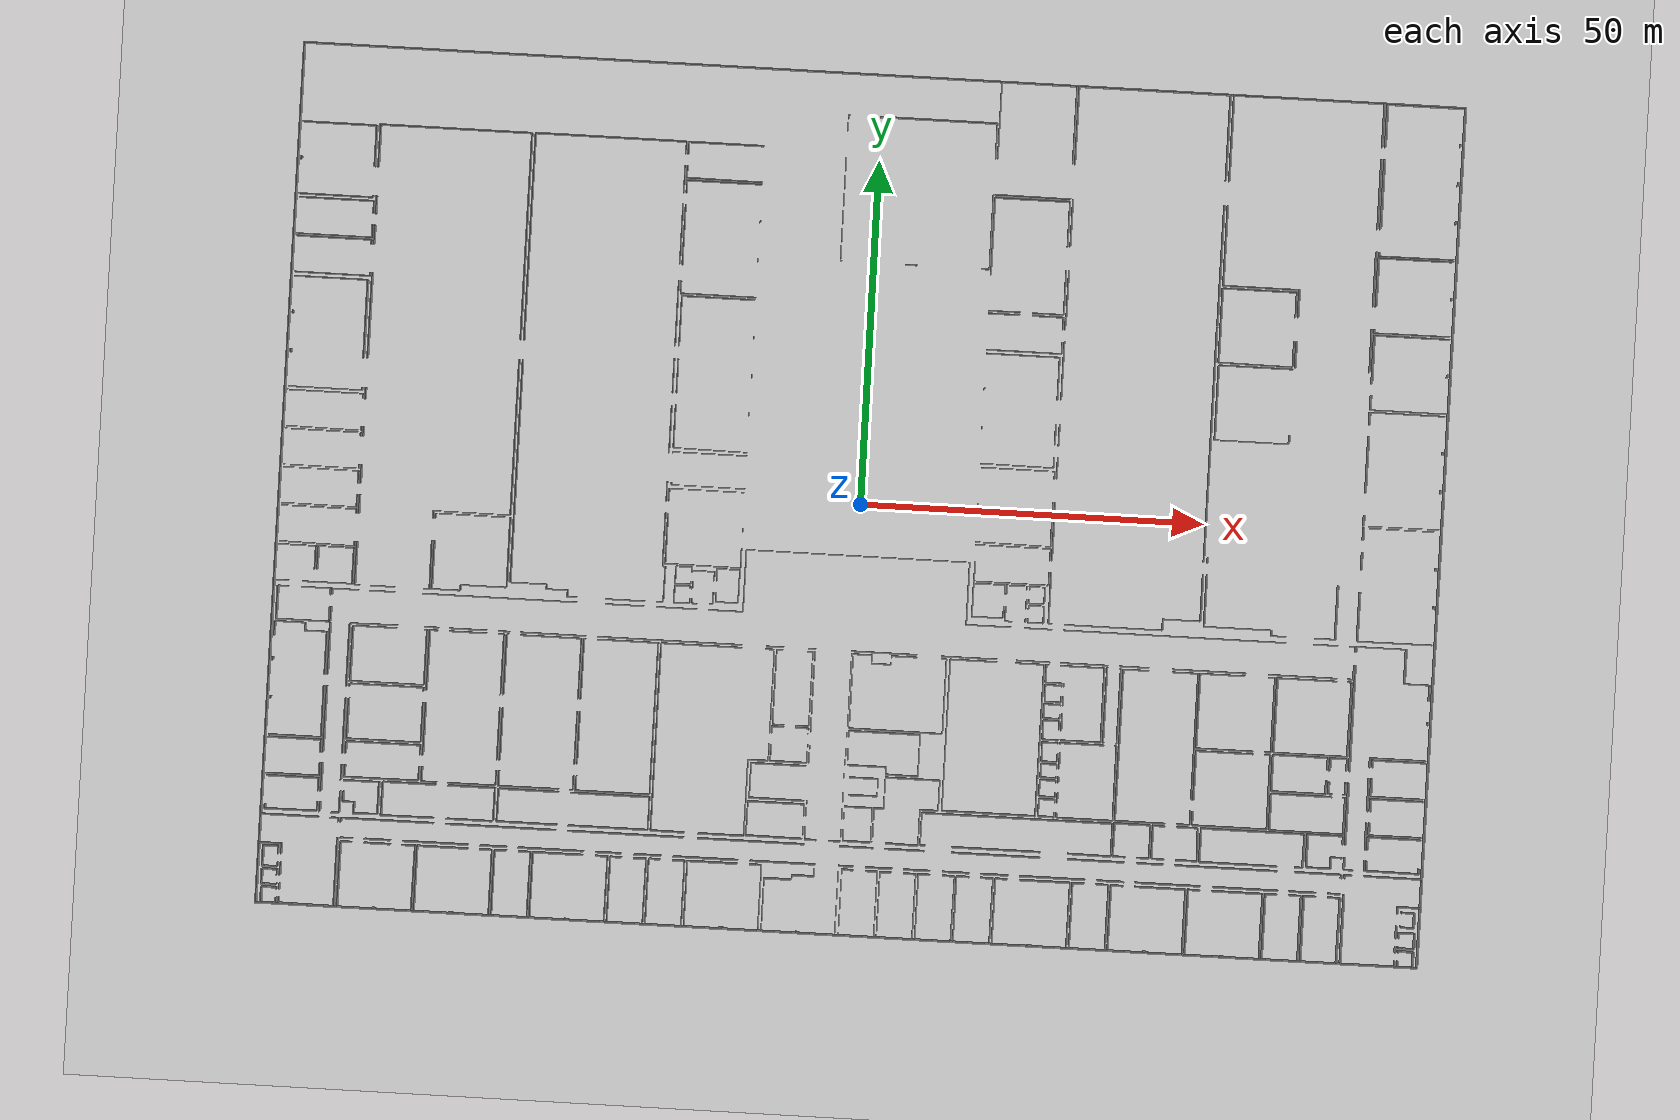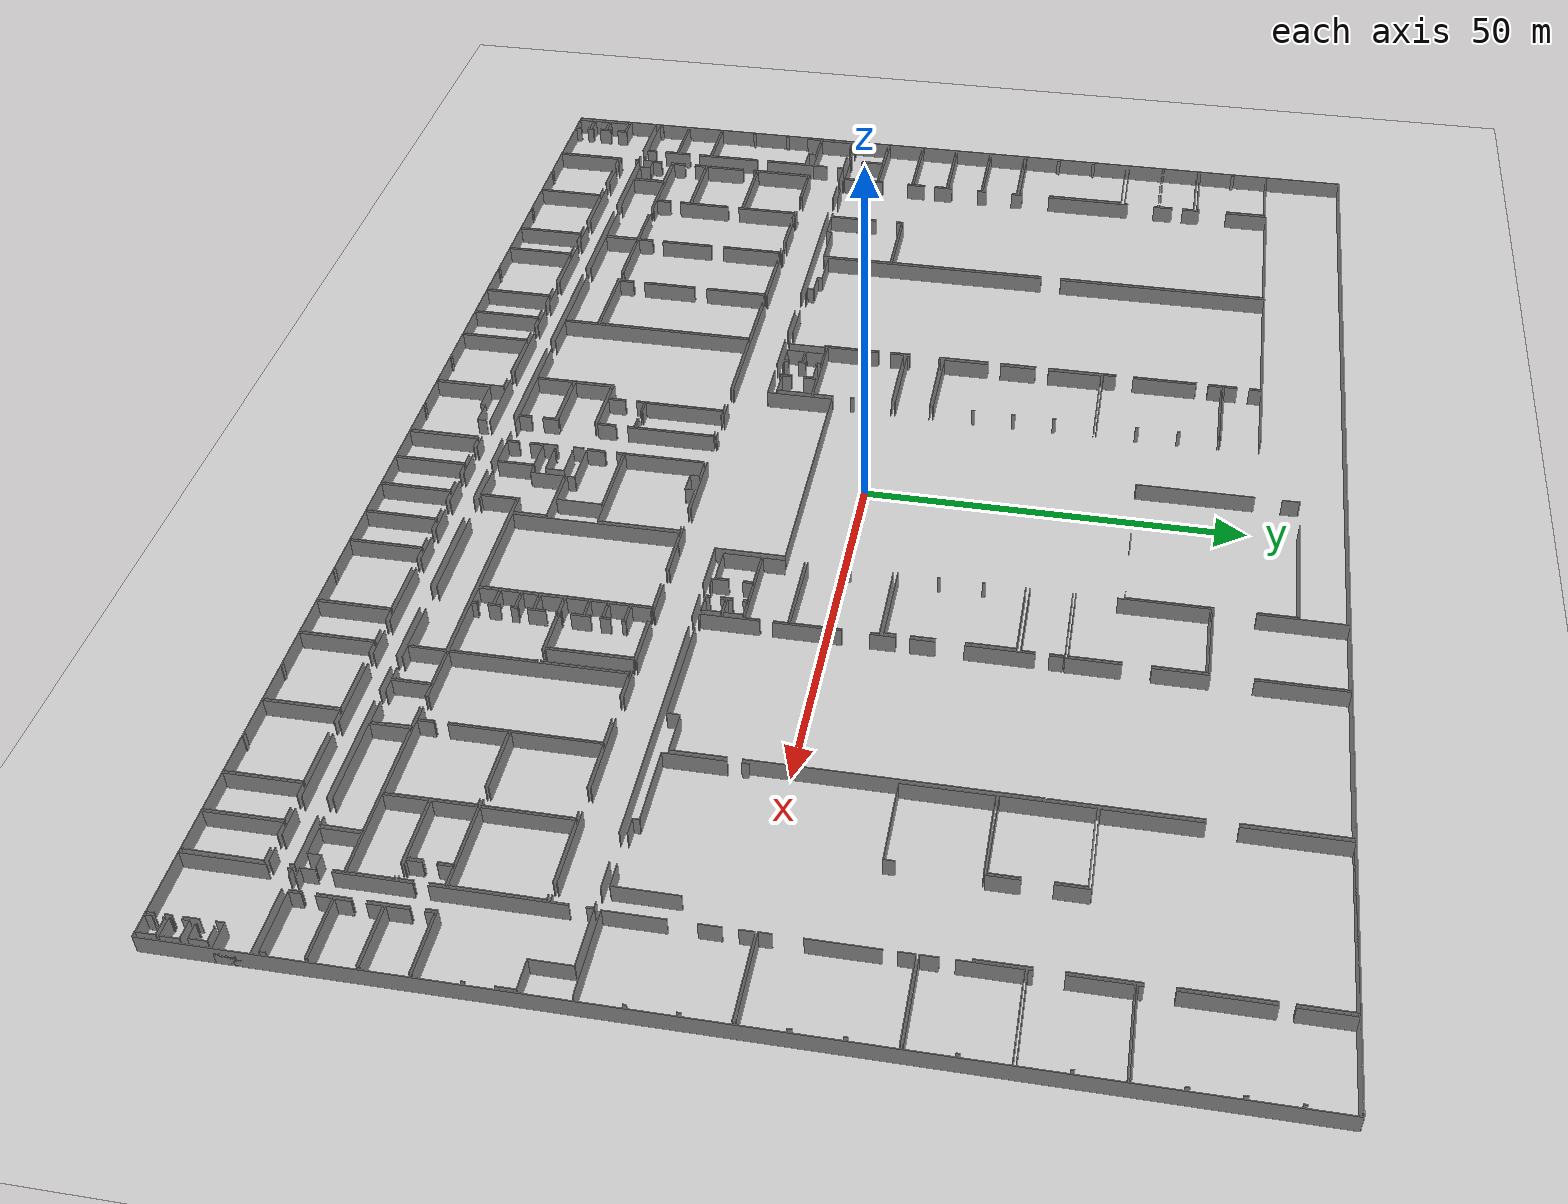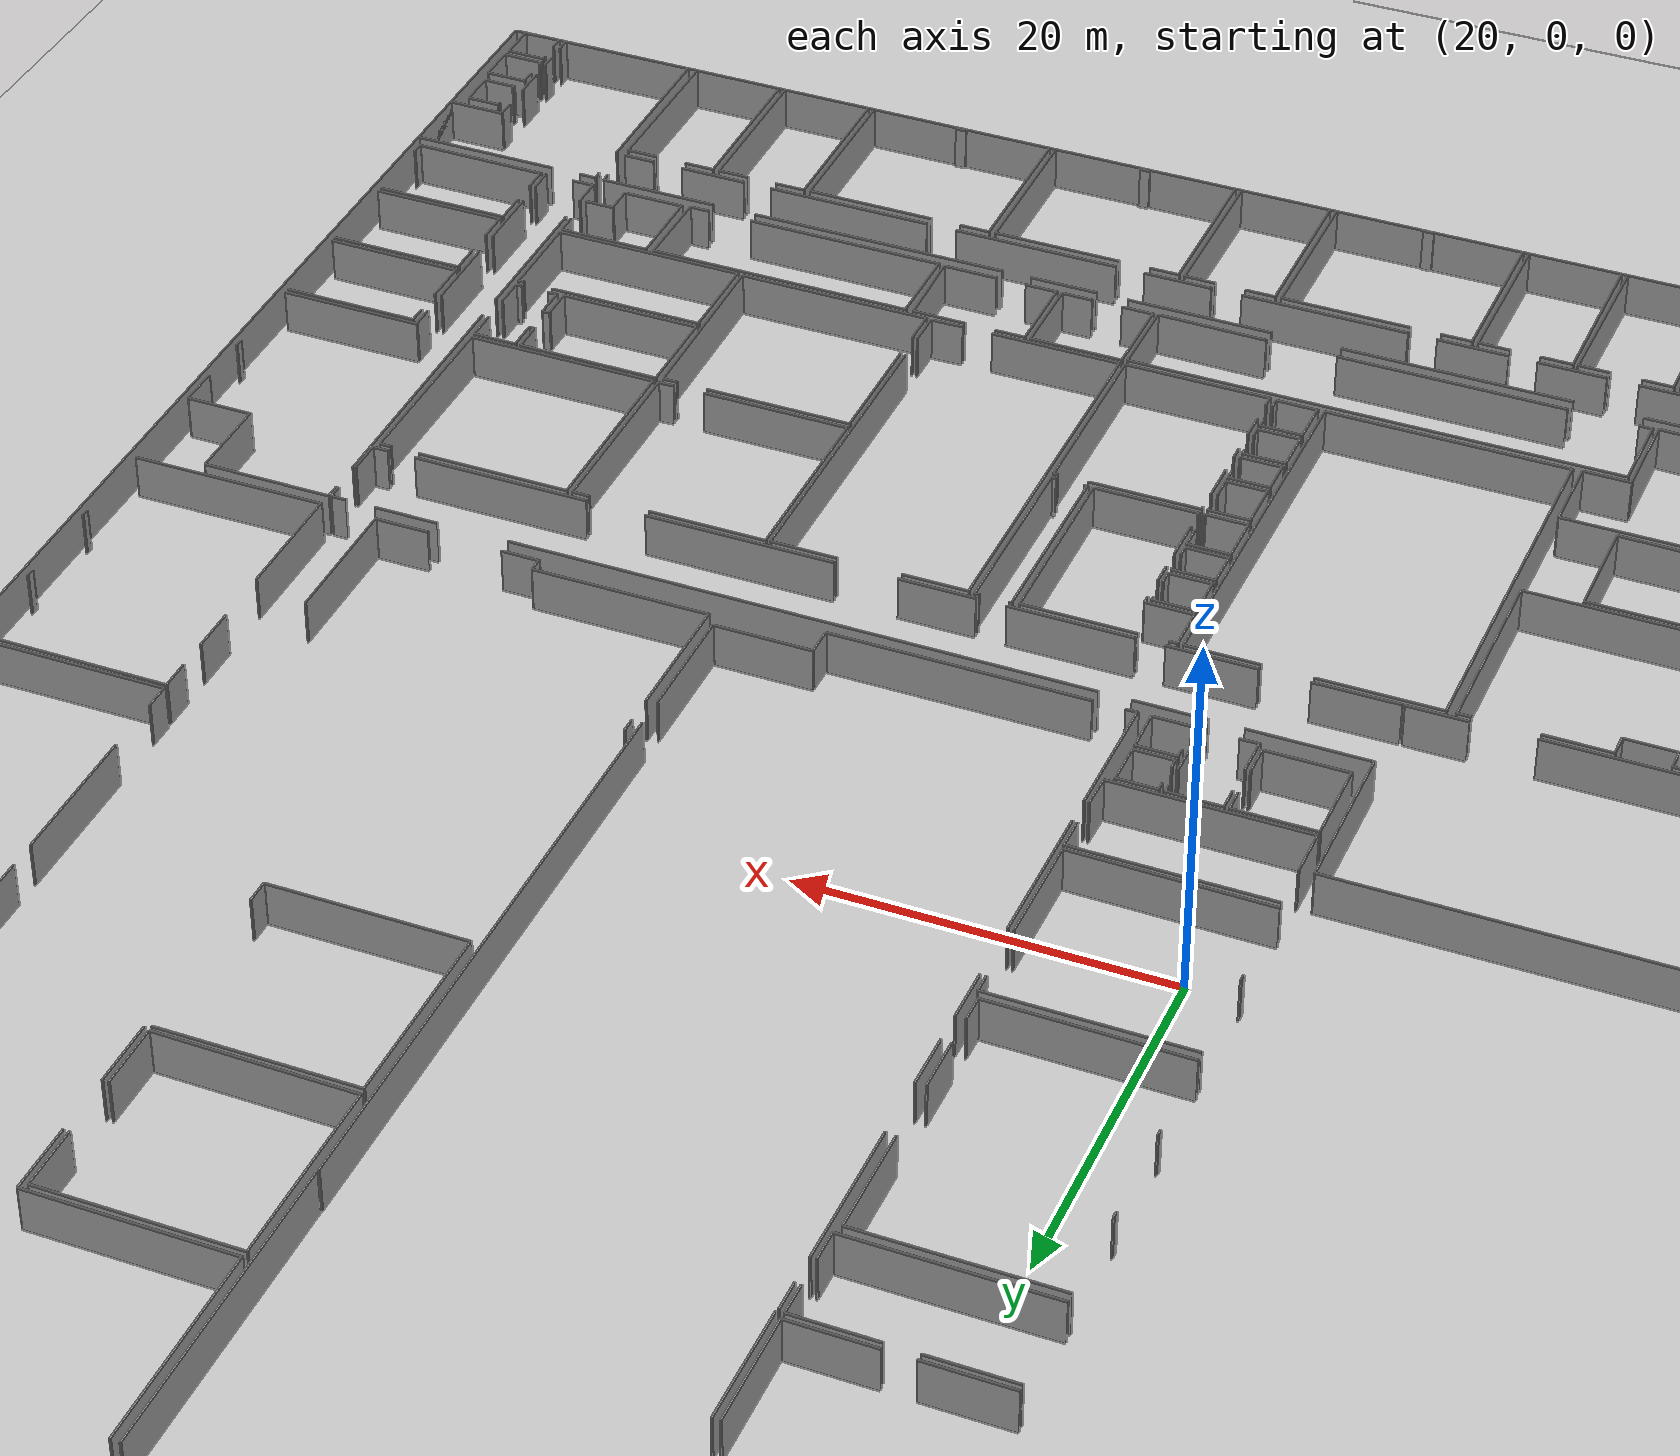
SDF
<sdf version="1.6">
  <world name="default">
    <light name="sun" type="directional">
      <cast_shadows>1</cast_shadows>
      <pose frame="">0 0 10 0 -0 0</pose>
      <diffuse>0.8 0.8 0.8 1</diffuse>
      <specular>0.1 0.1 0.1 1</specular>
      <attenuation>
        <range>1000</range>
        <constant>0.9</constant>
        <linear>0.01</linear>
        <quadratic>0.001</quadratic>
      </attenuation>
      <direction>-0.5 0.5 -1</direction>
    </light>
    <model name="ground_plane">
      <static>1</static>
      <link name="link">
        <collision name="collision">
          <geometry>
            <plane>
              <normal>0 0 1</normal>
              <size>100 100</size>
            </plane>
          </geometry>
          <surface>
            <friction>
              <ode>
                <mu>100</mu>
                <mu2>50</mu2>
              </ode>
              <torsional>
                <ode />
              </torsional>
            </friction>
            <contact>
              <ode />
            </contact>
            <bounce />
          </surface>
          <max_contacts>10</max_contacts>
        </collision>
        <visual name="visual">
          <cast_shadows>0</cast_shadows>
          <geometry>
            <plane>
              <normal>0 0 1</normal>
              <size>100 100</size>
            </plane>
          </geometry>
          <material>
            <script>
              <uri>file://media/materials/scripts/gazebo.material</uri>
              <name>Gazebo/Grey</name>
            </script>
          </material>
        </visual>
        <self_collide>0</self_collide>
        <kinematic>0</kinematic>
        <gravity>1</gravity>
      </link>
    </model>
    <gravity>0 0 -9.8</gravity>
    <magnetic_field>6e-06 2.3e-05 -4.2e-05</magnetic_field>
    <atmosphere type="adiabatic" />
    <physics default="0" name="default_physics" type="ode">
      <max_step_size>0.001</max_step_size>
      <real_time_factor>1</real_time_factor>
      <real_time_update_rate>1000</real_time_update_rate>
    </physics>
    <scene>
      <ambient>0.4 0.4 0.4 1</ambient>
      <background>0.7 0.7 0.7 1</background>
      <shadows>1</shadows>
    </scene>
    <spherical_coordinates>
      <surface_model>EARTH_WGS84</surface_model>
      <latitude_deg>0</latitude_deg>
      <longitude_deg>0</longitude_deg>
      <elevation>0</elevation>
      <heading_deg>0</heading_deg>
    </spherical_coordinates>
  <model name="0510045904_A_40_1_102">
		<static>1</static>
		<link name="Wall_0">
			<collision name="Wall_0_Collision">
				<geometry>
					<box>
						<size>0.837914354996 0.1 2.5</size>
					</box>
				</geometry>
				<pose frame="">0.418957177498 0 1.25 0 0 0</pose>
			</collision>
			<visual name="Wall_0_Visual">
				<pose frame="">0.418957177498 0 1.25 0 0 0</pose>
				<geometry>
					<box>
						<size>0.837914354996 0.1 2.5</size>
					</box>
				</geometry>
				<material>
					<script>
						<uri>file://media/materials/scripts/gazebo.material</uri>
						<name>Gazebo/Grey</name>
					</script>
					<ambient>1 1 1 1</ambient>
				</material>
			</visual>
			<pose frame="">22.6153084414 -78.1271344599 0 0 0 3.14159265359</pose>
		</link>
		<link name="Wall_1">
			<collision name="Wall_1_Collision">
				<geometry>
					<box>
						<size>3.37806441784 0.1 2.5</size>
					</box>
				</geometry>
				<pose frame="">1.68903220892 0 1.25 0 0 0</pose>
			</collision>
			<visual name="Wall_1_Visual">
				<pose frame="">1.68903220892 0 1.25 0 0 0</pose>
				<geometry>
					<box>
						<size>3.37806441784 0.1 2.5</size>
					</box>
				</geometry>
				<material>
					<script>
						<uri>file://media/materials/scripts/gazebo.material</uri>
						<name>Gazebo/Grey</name>
					</script>
					<ambient>1 1 1 1</ambient>
				</material>
			</visual>
			<pose frame="">17.4994604339 -78.1271344599 0 0 0 3.14159265359</pose>
		</link>
		<link name="Wall_2">
			<collision name="Wall_2_Collision">
				<geometry>
					<box>
						<size>0.685566290452 0.1 2.5</size>
					</box>
				</geometry>
				<pose frame="">0.342783145226 0 1.25 0 0 0</pose>
			</collision>
			<visual name="Wall_2_Visual">
				<pose frame="">0.342783145226 0 1.25 0 0 0</pose>
				<geometry>
					<box>
						<size>0.685566290452 0.1 2.5</size>
					</box>
				</geometry>
				<material>
					<script>
						<uri>file://media/materials/scripts/gazebo.material</uri>
						<name>Gazebo/Grey</name>
					</script>
					<ambient>1 1 1 1</ambient>
				</material>
			</visual>
			<pose frame="">12.4079881169 -78.1271344599 0 0 0 3.14159265359</pose>
		</link>
		<link name="Wall_3">
			<collision name="Wall_3_Collision">
				<geometry>
					<box>
						<size>6.29933855549 0.1 2.5</size>
					</box>
				</geometry>
				<pose frame="">3.14966927774 0 1.25 0 0 0</pose>
			</collision>
			<visual name="Wall_3_Visual">
				<pose frame="">3.14966927774 0 1.25 0 0 0</pose>
				<geometry>
					<box>
						<size>6.29933855549 0.1 2.5</size>
					</box>
				</geometry>
				<material>
					<script>
						<uri>file://media/materials/scripts/gazebo.material</uri>
						<name>Gazebo/Grey</name>
					</script>
					<ambient>1 1 1 1</ambient>
				</material>
			</visual>
			<pose frame="">11.7224218264 -78.1271344599 0 0 0 1.57079632679</pose>
		</link>
		<link name="Wall_4">
			<collision name="Wall_4_Collision">
				<geometry>
					<box>
						<size>2.73210862417 0.1 2.5</size>
					</box>
				</geometry>
				<pose frame="">1.36605431209 0 1.25 0 0 0</pose>
			</collision>
			<visual name="Wall_4_Visual">
				<pose frame="">1.36605431209 0 1.25 0 0 0</pose>
				<geometry>
					<box>
						<size>2.73210862417 0.1 2.5</size>
					</box>
				</geometry>
				<material>
					<script>
						<uri>file://media/materials/scripts/gazebo.material</uri>
						<name>Gazebo/Grey</name>
					</script>
					<ambient>1 1 1 1</ambient>
				</material>
			</visual>
			<pose frame="">11.7224218264 -67.818248759 0 0 0 1.57079632679</pose>
		</link>
		<link name="Wall_5">
			<collision name="Wall_5_Collision">
				<geometry>
					<box>
						<size>2.78390696612 0.1 2.5</size>
					</box>
				</geometry>
				<pose frame="">1.39195348306 0 1.25 0 0 0</pose>
			</collision>
			<visual name="Wall_5_Visual">
				<pose frame="">1.39195348306 0 1.25 0 0 0</pose>
				<geometry>
					<box>
						<size>2.78390696612 0.1 2.5</size>
					</box>
				</geometry>
				<material>
					<script>
						<uri>file://media/materials/scripts/gazebo.material</uri>
						<name>Gazebo/Grey</name>
					</script>
					<ambient>1 1 1 1</ambient>
				</material>
			</visual>
			<pose frame="">11.7224218264 -63.4349410286 0 0 0 1.57079632679</pose>
		</link>
		<link name="Wall_6">
			<collision name="Wall_6_Collision">
				<geometry>
					<box>
						<size>1.41328221209 0.1 2.5</size>
					</box>
				</geometry>
				<pose frame="">0.706641106047 0 1.25 0 0 0</pose>
			</collision>
			<visual name="Wall_6_Visual">
				<pose frame="">0.706641106047 0 1.25 0 0 0</pose>
				<geometry>
					<box>
						<size>1.41328221209 0.1 2.5</size>
					</box>
				</geometry>
				<material>
					<script>
						<uri>file://media/materials/scripts/gazebo.material</uri>
						<name>Gazebo/Grey</name>
					</script>
					<ambient>1 1 1 1</ambient>
				</material>
			</visual>
			<pose frame="">11.7224218264 -56.5434763289 0 0 0 1.57079632679</pose>
		</link>
		<link name="Wall_7">
			<collision name="Wall_7_Collision">
				<geometry>
					<box>
						<size>1.71290007237 0.1 2.5</size>
					</box>
				</geometry>
				<pose frame="">0.856450036183 0 1.25 0 0 0</pose>
			</collision>
			<visual name="Wall_7_Visual">
				<pose frame="">0.856450036183 0 1.25 0 0 0</pose>
				<geometry>
					<box>
						<size>1.71290007237 0.1 2.5</size>
					</box>
				</geometry>
				<material>
					<script>
						<uri>file://media/materials/scripts/gazebo.material</uri>
						<name>Gazebo/Grey</name>
					</script>
					<ambient>1 1 1 1</ambient>
				</material>
			</visual>
			<pose frame="">11.7224218264 -51.1582261607 0 0 0 1.57079632679</pose>
		</link>
		<link name="Wall_8">
			<collision name="Wall_8_Collision">
				<geometry>
					<box>
						<size>12.4971117346 0.1 2.5</size>
					</box>
				</geometry>
				<pose frame="">6.2485558673 0 1.25 0 0 0</pose>
			</collision>
			<visual name="Wall_8_Visual">
				<pose frame="">6.2485558673 0 1.25 0 0 0</pose>
				<geometry>
					<box>
						<size>12.4971117346 0.1 2.5</size>
					</box>
				</geometry>
				<material>
					<script>
						<uri>file://media/materials/scripts/gazebo.material</uri>
						<name>Gazebo/Grey</name>
					</script>
					<ambient>1 1 1 1</ambient>
				</material>
			</visual>
			<pose frame="">11.7224218264 -45.2608325822 0 0 0 1.57079632679</pose>
		</link>
		<link name="Wall_9">
			<collision name="Wall_9_Collision">
				<geometry>
					<box>
						<size>2.86922188226 0.1 2.5</size>
					</box>
				</geometry>
				<pose frame="">1.43461094113 0 1.25 0 0 0</pose>
			</collision>
			<visual name="Wall_9_Visual">
				<pose frame="">1.43461094113 0 1.25 0 0 0</pose>
				<geometry>
					<box>
						<size>2.86922188226 0.1 2.5</size>
					</box>
				</geometry>
				<material>
					<script>
						<uri>file://media/materials/scripts/gazebo.material</uri>
						<name>Gazebo/Grey</name>
					</script>
					<ambient>1 1 1 1</ambient>
				</material>
			</visual>
			<pose frame="">11.7224218264 -28.7155788592 0 0 0 1.57079632679</pose>
		</link>
		<link name="Wall_10">
			<collision name="Wall_10_Collision">
				<geometry>
					<box>
						<size>2.61530844135 0.1 2.5</size>
					</box>
				</geometry>
				<pose frame="">1.30765422068 0 1.25 0 0 0</pose>
			</collision>
			<visual name="Wall_10_Visual">
				<pose frame="">1.30765422068 0 1.25 0 0 0</pose>
				<geometry>
					<box>
						<size>2.61530844135 0.1 2.5</size>
					</box>
				</geometry>
				<material>
					<script>
						<uri>file://media/materials/scripts/gazebo.material</uri>
						<name>Gazebo/Grey</name>
					</script>
					<ambient>1 1 1 1</ambient>
				</material>
			</visual>
			<pose frame="">11.7224218264 -24.2467022992 0 0 0 1.57079632679</pose>
		</link>
		<link name="Wall_11">
			<collision name="Wall_11_Collision">
				<geometry>
					<box>
						<size>6.20437492859 0.1 2.5</size>
					</box>
				</geometry>
				<pose frame="">3.10218746429 0 1.25 0 0 0</pose>
			</collision>
			<visual name="Wall_11_Visual">
				<pose frame="">3.10218746429 0 1.25 0 0 0</pose>
				<geometry>
					<box>
						<size>6.20437492859 0.1 2.5</size>
					</box>
				</geometry>
				<material>
					<script>
						<uri>file://media/materials/scripts/gazebo.material</uri>
						<name>Gazebo/Grey</name>
					</script>
					<ambient>1 1 1 1</ambient>
				</material>
			</visual>
			<pose frame="">11.7224218264 -17.4849873678 0 0 0 1.57079632679</pose>
		</link>
		<link name="Wall_12">
			<collision name="Wall_12_Collision">
				<geometry>
					<box>
						<size>21.978747445 0.1 2.5</size>
					</box>
				</geometry>
				<pose frame="">10.9893737225 0 1.25 0 0 0</pose>
			</collision>
			<visual name="Wall_12_Visual">
				<pose frame="">10.9893737225 0 1.25 0 0 0</pose>
				<geometry>
					<box>
						<size>21.978747445 0.1 2.5</size>
					</box>
				</geometry>
				<material>
					<script>
						<uri>file://media/materials/scripts/gazebo.material</uri>
						<name>Gazebo/Grey</name>
					</script>
					<ambient>1 1 1 1</ambient>
				</material>
			</visual>
			<pose frame="">11.7224218264 -11.2806124392 0 0 0 0.0</pose>
		</link>
		<link name="Wall_13">
			<collision name="Wall_13_Collision">
				<geometry>
					<box>
						<size>30.0501479046 0.1 2.5</size>
					</box>
				</geometry>
				<pose frame="">15.0250739523 0 1.25 0 0 0</pose>
			</collision>
			<visual name="Wall_13_Visual">
				<pose frame="">15.0250739523 0 1.25 0 0 0</pose>
				<geometry>
					<box>
						<size>30.0501479046 0.1 2.5</size>
					</box>
				</geometry>
				<material>
					<script>
						<uri>file://media/materials/scripts/gazebo.material</uri>
						<name>Gazebo/Grey</name>
					</script>
					<ambient>1 1 1 1</ambient>
				</material>
			</visual>
			<pose frame="">33.7011692714 -11.2806124392 0 0 0 -1.57079632679</pose>
		</link>
		<link name="Wall_14">
			<collision name="Wall_14_Collision">
				<geometry>
					<box>
						<size>22.5977884139 0.1 2.5</size>
					</box>
				</geometry>
				<pose frame="">11.298894207 0 1.25 0 0 0</pose>
			</collision>
			<visual name="Wall_14_Visual">
				<pose frame="">11.298894207 0 1.25 0 0 0</pose>
				<geometry>
					<box>
						<size>22.5977884139 0.1 2.5</size>
					</box>
				</geometry>
				<material>
					<script>
						<uri>file://media/materials/scripts/gazebo.material</uri>
						<name>Gazebo/Grey</name>
					</script>
					<ambient>1 1 1 1</ambient>
				</material>
			</visual>
			<pose frame="">33.7011692714 -44.1971891782 0 0 0 -1.57079632679</pose>
		</link>
		<link name="Wall_15">
			<collision name="Wall_15_Collision">
				<geometry>
					<box>
						<size>11.1368974317 0.1 2.5</size>
					</box>
				</geometry>
				<pose frame="">5.56844871583 0 1.25 0 0 0</pose>
			</collision>
			<visual name="Wall_15_Visual">
				<pose frame="">5.56844871583 0 1.25 0 0 0</pose>
				<geometry>
					<box>
						<size>11.1368974317 0.1 2.5</size>
					</box>
				</geometry>
				<material>
					<script>
						<uri>file://media/materials/scripts/gazebo.material</uri>
						<name>Gazebo/Grey</name>
					</script>
					<ambient>1 1 1 1</ambient>
				</material>
			</visual>
			<pose frame="">33.7011692714 -66.7949775921 0 0 0 3.14159265359</pose>
		</link>
		<link name="Wall_16">
			<collision name="Wall_16_Collision">
				<geometry>
					<box>
						<size>1.05602600074 0.1 2.5</size>
					</box>
				</geometry>
				<pose frame="">0.528013000368 0 1.25 0 0 0</pose>
			</collision>
			<visual name="Wall_16_Visual">
				<pose frame="">0.528013000368 0 1.25 0 0 0</pose>
				<geometry>
					<box>
						<size>1.05602600074 0.1 2.5</size>
					</box>
				</geometry>
				<material>
					<script>
						<uri>file://media/materials/scripts/gazebo.material</uri>
						<name>Gazebo/Grey</name>
					</script>
					<ambient>1 1 1 1</ambient>
				</material>
			</visual>
			<pose frame="">22.5642718397 -66.7949775921 0 0 0 -1.57079632679</pose>
		</link>
		<link name="Wall_17">
			<collision name="Wall_17_Collision">
				<geometry>
					<box>
						<size>7.06761098928 0.1 2.5</size>
					</box>
				</geometry>
				<pose frame="">3.53380549464 0 1.25 0 0 0</pose>
			</collision>
			<visual name="Wall_17_Visual">
				<pose frame="">3.53380549464 0 1.25 0 0 0</pose>
				<geometry>
					<box>
						<size>7.06761098928 0.1 2.5</size>
					</box>
				</geometry>
				<material>
					<script>
						<uri>file://media/materials/scripts/gazebo.material</uri>
						<name>Gazebo/Grey</name>
					</script>
					<ambient>1 1 1 1</ambient>
				</material>
			</visual>
			<pose frame="">22.5642718397 -71.0597077456 0 0 0 -1.5635750684</pose>
		</link>
		<link name="Wall_18">
			<collision name="Wall_18_Collision">
				<geometry>
					<box>
						<size>10.6681732197 0.1 2.5</size>
					</box>
				</geometry>
				<pose frame="">5.33408660987 0 1.25 0 0 0</pose>
			</collision>
			<visual name="Wall_18_Visual">
				<pose frame="">5.33408660987 0 1.25 0 0 0</pose>
				<geometry>
					<box>
						<size>10.6681732197 0.1 2.5</size>
					</box>
				</geometry>
				<material>
					<script>
						<uri>file://media/materials/scripts/gazebo.material</uri>
						<name>Gazebo/Grey</name>
					</script>
					<ambient>1 1 1 1</ambient>
				</material>
			</visual>
			<pose frame="">11.1856488123 -21.9089212487 0 0 0 3.14159265359</pose>
		</link>
		<link name="Wall_19">
			<collision name="Wall_19_Collision">
				<geometry>
					<box>
						<size>0.480150316757 0.1 2.5</size>
					</box>
				</geometry>
				<pose frame="">0.240075158379 0 1.25 0 0 0</pose>
			</collision>
			<visual name="Wall_19_Visual">
				<pose frame="">0.240075158379 0 1.25 0 0 0</pose>
				<geometry>
					<box>
						<size>0.480150316757 0.1 2.5</size>
					</box>
				</geometry>
				<material>
					<script>
						<uri>file://media/materials/scripts/gazebo.material</uri>
						<name>Gazebo/Grey</name>
					</script>
					<ambient>1 1 1 1</ambient>
				</material>
			</visual>
			<pose frame="">0.517475592571 -16.9723361306 0 0 0 1.57079632679</pose>
		</link>
		<link name="Wall_20">
			<collision name="Wall_20_Collision">
				<geometry>
					<box>
						<size>10.6615714703 0.1 2.5</size>
					</box>
				</geometry>
				<pose frame="">5.33078573514 0 1.25 0 0 0</pose>
			</collision>
			<visual name="Wall_20_Visual">
				<pose frame="">5.33078573514 0 1.25 0 0 0</pose>
				<geometry>
					<box>
						<size>10.6615714703 0.1 2.5</size>
					</box>
				</geometry>
				<material>
					<script>
						<uri>file://media/materials/scripts/gazebo.material</uri>
						<name>Gazebo/Grey</name>
					</script>
					<ambient>1 1 1 1</ambient>
				</material>
			</visual>
			<pose frame="">0.517475592571 -11.461906636 0 0 0 0.0</pose>
		</link>
		<link name="Wall_21">
			<collision name="Wall_21_Collision">
				<geometry>
					<box>
						<size>5.95198496832 0.1 2.5</size>
					</box>
				</geometry>
				<pose frame="">2.97599248416 0 1.25 0 0 0</pose>
			</collision>
			<visual name="Wall_21_Visual">
				<pose frame="">2.97599248416 0 1.25 0 0 0</pose>
				<geometry>
					<box>
						<size>5.95198496832 0.1 2.5</size>
					</box>
				</geometry>
				<material>
					<script>
						<uri>file://media/materials/scripts/gazebo.material</uri>
						<name>Gazebo/Grey</name>
					</script>
					<ambient>1 1 1 1</ambient>
				</material>
			</visual>
			<pose frame="">11.1790470629 -11.461906636 0 0 0 -1.57079632679</pose>
		</link>
		<link name="Wall_22">
			<collision name="Wall_22_Collision">
				<geometry>
					<box>
						<size>0.293852018729 0.1 2.5</size>
					</box>
				</geometry>
				<pose frame="">0.146926009364 0 1.25 0 0 0</pose>
			</collision>
			<visual name="Wall_22_Visual">
				<pose frame="">0.146926009364 0 1.25 0 0 0</pose>
				<geometry>
					<box>
						<size>0.293852018729 0.1 2.5</size>
					</box>
				</geometry>
				<material>
					<script>
						<uri>file://media/materials/scripts/gazebo.material</uri>
						<name>Gazebo/Grey</name>
					</script>
					<ambient>1 1 1 1</ambient>
				</material>
			</visual>
			<pose frame="">11.1790470629 -21.6151433976 0 0 0 -1.54832819821</pose>
		</link>
		<link name="Wall_23">
			<collision name="Wall_23_Collision">
				<geometry>
					<box>
						<size>10.9071057676 0.1 2.5</size>
					</box>
				</geometry>
				<pose frame="">5.45355288382 0 1.25 0 0 0</pose>
			</collision>
			<visual name="Wall_23_Visual">
				<pose frame="">5.45355288382 0 1.25 0 0 0</pose>
				<geometry>
					<box>
						<size>10.9071057676 0.1 2.5</size>
					</box>
				</geometry>
				<material>
					<script>
						<uri>file://media/materials/scripts/gazebo.material</uri>
						<name>Gazebo/Grey</name>
					</script>
					<ambient>1 1 1 1</ambient>
				</material>
			</visual>
			<pose frame="">11.4276283215 -27.7296329681 0 0 0 3.14159265359</pose>
		</link>
		<link name="Wall_24">
			<collision name="Wall_24_Collision">
				<geometry>
					<box>
						<size>10.8784135488 0.1 2.5</size>
					</box>
				</geometry>
				<pose frame="">5.43920677441 0 1.25 0 0 0</pose>
			</collision>
			<visual name="Wall_24_Visual">
				<pose frame="">5.43920677441 0 1.25 0 0 0</pose>
				<geometry>
					<box>
						<size>10.8784135488 0.1 2.5</size>
					</box>
				</geometry>
				<material>
					<script>
						<uri>file://media/materials/scripts/gazebo.material</uri>
						<name>Gazebo/Grey</name>
					</script>
					<ambient>1 1 1 1</ambient>
				</material>
			</visual>
			<pose frame="">0.520522553861 -22.4159863902 0 0 0 0.0</pose>
		</link>
		<link name="Wall_25">
			<collision name="Wall_25_Collision">
				<geometry>
					<box>
						<size>1.79262889281 0.1 2.5</size>
					</box>
				</geometry>
				<pose frame="">0.896314446405 0 1.25 0 0 0</pose>
			</collision>
			<visual name="Wall_25_Visual">
				<pose frame="">0.896314446405 0 1.25 0 0 0</pose>
				<geometry>
					<box>
						<size>1.79262889281 0.1 2.5</size>
					</box>
				</geometry>
				<material>
					<script>
						<uri>file://media/materials/scripts/gazebo.material</uri>
						<name>Gazebo/Grey</name>
					</script>
					<ambient>1 1 1 1</ambient>
				</material>
			</visual>
			<pose frame="">11.3989361027 -22.4159863902 0 0 0 -1.57079632679</pose>
		</link>
		<link name="Wall_26">
			<collision name="Wall_26_Collision">
				<geometry>
					<box>
						<size>1.8466814538 0.1 2.5</size>
					</box>
				</geometry>
				<pose frame="">0.923340726898 0 1.25 0 0 0</pose>
			</collision>
			<visual name="Wall_26_Visual">
				<pose frame="">0.923340726898 0 1.25 0 0 0</pose>
				<geometry>
					<box>
						<size>1.8466814538 0.1 2.5</size>
					</box>
				</geometry>
				<material>
					<script>
						<uri>file://media/materials/scripts/gazebo.material</uri>
						<name>Gazebo/Grey</name>
					</script>
					<ambient>1 1 1 1</ambient>
				</material>
			</visual>
			<pose frame="">11.3989361027 -25.8831744258 0 0 0 -1.55525852341</pose>
		</link>
		<link name="Wall_27">
			<collision name="Wall_27_Collision">
				<geometry>
					<box>
						<size>0.484212931812 0.1 2.5</size>
					</box>
				</geometry>
				<pose frame="">0.242106465906 0 1.25 0 0 0</pose>
			</collision>
			<visual name="Wall_27_Visual">
				<pose frame="">0.242106465906 0 1.25 0 0 0</pose>
				<geometry>
					<box>
						<size>0.484212931812 0.1 2.5</size>
					</box>
				</geometry>
				<material>
					<script>
						<uri>file://media/materials/scripts/gazebo.material</uri>
						<name>Gazebo/Grey</name>
					</script>
					<ambient>1 1 1 1</ambient>
				</material>
			</visual>
			<pose frame="">11.3859865172 -33.2951616794 0 0 0 1.57079632679</pose>
		</link>
		<link name="Wall_28">
			<collision name="Wall_28_Collision">
				<geometry>
					<box>
						<size>0.662206253888 0.1 2.5</size>
					</box>
				</geometry>
				<pose frame="">0.331103126944 0 1.25 0 0 0</pose>
			</collision>
			<visual name="Wall_28_Visual">
				<pose frame="">0.331103126944 0 1.25 0 0 0</pose>
				<geometry>
					<box>
						<size>0.662206253888 0.1 2.5</size>
					</box>
				</geometry>
				<material>
					<script>
						<uri>file://media/materials/scripts/gazebo.material</uri>
						<name>Gazebo/Grey</name>
					</script>
					<ambient>1 1 1 1</ambient>
				</material>
			</visual>
			<pose frame="">11.3859865172 -28.701105793 0 0 0 1.57079632679</pose>
		</link>
		<link name="Wall_29">
			<collision name="Wall_29_Collision">
				<geometry>
					<box>
						<size>10.8235682456 0.1 2.5</size>
					</box>
				</geometry>
				<pose frame="">5.41178412279 0 1.25 0 0 0</pose>
			</collision>
			<visual name="Wall_29_Visual">
				<pose frame="">5.41178412279 0 1.25 0 0 0</pose>
				<geometry>
					<box>
						<size>10.8235682456 0.1 2.5</size>
					</box>
				</geometry>
				<material>
					<script>
						<uri>file://media/materials/scripts/gazebo.material</uri>
						<name>Gazebo/Grey</name>
					</script>
					<ambient>1 1 1 1</ambient>
				</material>
			</visual>
			<pose frame="">11.3859865172 -28.0388995391 0 0 0 3.14159265359</pose>
		</link>
		<link name="Wall_30">
			<collision name="Wall_30_Collision">
				<geometry>
					<box>
						<size>10.8235918368 0.1 2.5</size>
					</box>
				</geometry>
				<pose frame="">5.4117959184 0 1.25 0 0 0</pose>
			</collision>
			<visual name="Wall_30_Visual">
				<pose frame="">5.4117959184 0 1.25 0 0 0</pose>
				<geometry>
					<box>
						<size>10.8235918368 0.1 2.5</size>
					</box>
				</geometry>
				<material>
					<script>
						<uri>file://media/materials/scripts/gazebo.material</uri>
						<name>Gazebo/Grey</name>
					</script>
					<ambient>1 1 1 1</ambient>
				</material>
			</visual>
			<pose frame="">0.562418271611 -33.2725633831 0 0 0 -0.00208787554077</pose>
		</link>
		<link name="Wall_31">
			<collision name="Wall_31_Collision">
				<geometry>
					<box>
						<size>10.6516688461 0.1 2.5</size>
					</box>
				</geometry>
				<pose frame="">5.32583442305 0 1.25 0 0 0</pose>
			</collision>
			<visual name="Wall_31_Visual">
				<pose frame="">5.32583442305 0 1.25 0 0 0</pose>
				<geometry>
					<box>
						<size>10.6516688461 0.1 2.5</size>
					</box>
				</geometry>
				<material>
					<script>
						<uri>file://media/materials/scripts/gazebo.material</uri>
						<name>Gazebo/Grey</name>
					</script>
					<ambient>1 1 1 1</ambient>
				</material>
			</visual>
			<pose frame="">11.2024070994 -49.9069407239 0 0 0 3.14159265359</pose>
		</link>
		<link name="Wall_32">
			<collision name="Wall_32_Collision">
				<geometry>
					<box>
						<size>0.500971218911 0.1 2.5</size>
					</box>
				</geometry>
				<pose frame="">0.250485609456 0 1.25 0 0 0</pose>
			</collision>
			<visual name="Wall_32_Visual">
				<pose frame="">0.250485609456 0 1.25 0 0 0</pose>
				<geometry>
					<box>
						<size>0.500971218911 0.1 2.5</size>
					</box>
				</geometry>
				<material>
					<script>
						<uri>file://media/materials/scripts/gazebo.material</uri>
						<name>Gazebo/Grey</name>
					</script>
					<ambient>1 1 1 1</ambient>
				</material>
			</visual>
			<pose frame="">0.550738253329 -44.9485190499 0 0 0 1.57079632679</pose>
		</link>
		<link name="Wall_33">
			<collision name="Wall_33_Collision">
				<geometry>
					<box>
						<size>0.434191983953 0.1 2.5</size>
					</box>
				</geometry>
				<pose frame="">0.217095991976 0 1.25 0 0 0</pose>
			</collision>
			<visual name="Wall_33_Visual">
				<pose frame="">0.217095991976 0 1.25 0 0 0</pose>
				<geometry>
					<box>
						<size>0.434191983953 0.1 2.5</size>
					</box>
				</geometry>
				<material>
					<script>
						<uri>file://media/materials/scripts/gazebo.material</uri>
						<name>Gazebo/Grey</name>
					</script>
					<ambient>1 1 1 1</ambient>
				</material>
			</visual>
			<pose frame="">0.550738253329 -39.3055467391 0 0 0 1.57079632679</pose>
		</link>
		<link name="Wall_34">
			<collision name="Wall_34_Collision">
				<geometry>
					<box>
						<size>10.5841278708 0.1 2.5</size>
					</box>
				</geometry>
				<pose frame="">5.2920639354 0 1.25 0 0 0</pose>
			</collision>
			<visual name="Wall_34_Visual">
				<pose frame="">5.2920639354 0 1.25 0 0 0</pose>
				<geometry>
					<box>
						<size>10.5841278708 0.1 2.5</size>
					</box>
				</geometry>
				<material>
					<script>
						<uri>file://media/materials/scripts/gazebo.material</uri>
						<name>Gazebo/Grey</name>
					</script>
					<ambient>1 1 1 1</ambient>
				</material>
			</visual>
			<pose frame="">0.550738253329 -33.8855104295 0 0 0 0.0</pose>
		</link>
		<link name="Wall_35">
			<collision name="Wall_35_Collision">
				<geometry>
					<box>
						<size>11.3598334328 0.1 2.5</size>
					</box>
				</geometry>
				<pose frame="">5.67991671639 0 1.25 0 0 0</pose>
			</collision>
			<visual name="Wall_35_Visual">
				<pose frame="">5.67991671639 0 1.25 0 0 0</pose>
				<geometry>
					<box>
						<size>11.3598334328 0.1 2.5</size>
					</box>
				</geometry>
				<material>
					<script>
						<uri>file://media/materials/scripts/gazebo.material</uri>
						<name>Gazebo/Grey</name>
					</script>
					<ambient>1 1 1 1</ambient>
				</material>
			</visual>
			<pose frame="">11.1348661241 -33.8855104295 0 0 0 -1.57079632679</pose>
		</link>
		<link name="Wall_36">
			<collision name="Wall_36_Collision">
				<geometry>
					<box>
						<size>0.451711725919 0.1 2.5</size>
					</box>
				</geometry>
				<pose frame="">0.225855862959 0 1.25 0 0 0</pose>
			</collision>
			<visual name="Wall_36_Visual">
				<pose frame="">0.225855862959 0 1.25 0 0 0</pose>
				<geometry>
					<box>
						<size>0.451711725919 0.1 2.5</size>
					</box>
				</geometry>
				<material>
					<script>
						<uri>file://media/materials/scripts/gazebo.material</uri>
						<name>Gazebo/Grey</name>
					</script>
					<ambient>1 1 1 1</ambient>
				</material>
			</visual>
			<pose frame="">11.1348661241 -49.4603069814 0 0 0 -1.42071120493</pose>
		</link>
		<link name="Wall_37">
			<collision name="Wall_37_Collision">
				<geometry>
					<box>
						<size>0.614470526997 0.1 2.5</size>
					</box>
				</geometry>
				<pose frame="">0.307235263499 0 1.25 0 0 0</pose>
			</collision>
			<visual name="Wall_37_Visual">
				<pose frame="">0.307235263499 0 1.25 0 0 0</pose>
				<geometry>
					<box>
						<size>0.614470526997 0.1 2.5</size>
					</box>
				</geometry>
				<material>
					<script>
						<uri>file://media/materials/scripts/gazebo.material</uri>
						<name>Gazebo/Grey</name>
					</script>
					<ambient>1 1 1 1</ambient>
				</material>
			</visual>
			<pose frame="">11.4093465538 -55.7553290083 0 0 0 1.57079632679</pose>
		</link>
		<link name="Wall_38">
			<collision name="Wall_38_Collision">
				<geometry>
					<box>
						<size>0.706387192606 0.1 2.5</size>
					</box>
				</geometry>
				<pose frame="">0.353193596303 0 1.25 0 0 0</pose>
			</collision>
			<visual name="Wall_38_Visual">
				<pose frame="">0.353193596303 0 1.25 0 0 0</pose>
				<geometry>
					<box>
						<size>0.706387192606 0.1 2.5</size>
					</box>
				</geometry>
				<material>
					<script>
						<uri>file://media/materials/scripts/gazebo.material</uri>
						<name>Gazebo/Grey</name>
					</script>
					<ambient>1 1 1 1</ambient>
				</material>
			</visual>
			<pose frame="">11.4093465538 -51.111760001 0 0 0 1.57079632679</pose>
		</link>
		<link name="Wall_39">
			<collision name="Wall_39_Collision">
				<geometry>
					<box>
						<size>10.8888239999 0.1 2.5</size>
					</box>
				</geometry>
				<pose frame="">5.44441199995 0 1.25 0 0 0</pose>
			</collision>
			<visual name="Wall_39_Visual">
				<pose frame="">5.44441199995 0 1.25 0 0 0</pose>
				<geometry>
					<box>
						<size>10.8888239999 0.1 2.5</size>
					</box>
				</geometry>
				<material>
					<script>
						<uri>file://media/materials/scripts/gazebo.material</uri>
						<name>Gazebo/Grey</name>
					</script>
					<ambient>1 1 1 1</ambient>
				</material>
			</visual>
			<pose frame="">11.4093465538 -50.4053728084 0 0 0 3.14159265359</pose>
		</link>
		<link name="Wall_40">
			<collision name="Wall_40_Collision">
				<geometry>
					<box>
						<size>10.8892119446 0.1 2.5</size>
					</box>
				</geometry>
				<pose frame="">5.44460597229 0 1.25 0 0 0</pose>
			</collision>
			<visual name="Wall_40_Visual">
				<pose frame="">5.44460597229 0 1.25 0 0 0</pose>
				<geometry>
					<box>
						<size>10.8892119446 0.1 2.5</size>
					</box>
				</geometry>
				<material>
					<script>
						<uri>file://media/materials/scripts/gazebo.material</uri>
						<name>Gazebo/Grey</name>
					</script>
					<ambient>1 1 1 1</ambient>
				</material>
			</visual>
			<pose frame="">0.520522553861 -55.6634123427 0 0 0 -0.00844117624387</pose>
		</link>
		<link name="Wall_41">
			<collision name="Wall_41_Collision">
				<geometry>
					<box>
						<size>10.8672413574 0.1 2.5</size>
					</box>
				</geometry>
				<pose frame="">5.43362067871 0 1.25 0 0 0</pose>
			</collision>
			<visual name="Wall_41_Visual">
				<pose frame="">5.43362067871 0 1.25 0 0 0</pose>
				<geometry>
					<box>
						<size>10.8672413574 0.1 2.5</size>
					</box>
				</geometry>
				<material>
					<script>
						<uri>file://media/materials/scripts/gazebo.material</uri>
						<name>Gazebo/Grey</name>
					</script>
					<ambient>1 1 1 1</ambient>
				</material>
			</visual>
			<pose frame="">11.4093465538 -61.2665202432 0 0 0 3.14159265359</pose>
		</link>
		<link name="Wall_42">
			<collision name="Wall_42_Collision">
				<geometry>
					<box>
						<size>10.8423578402 0.1 2.5</size>
					</box>
				</geometry>
				<pose frame="">5.42117892011 0 1.25 0 0 0</pose>
			</collision>
			<visual name="Wall_42_Visual">
				<pose frame="">5.42117892011 0 1.25 0 0 0</pose>
				<geometry>
					<box>
						<size>10.8423578402 0.1 2.5</size>
					</box>
				</geometry>
				<material>
					<script>
						<uri>file://media/materials/scripts/gazebo.material</uri>
						<name>Gazebo/Grey</name>
					</script>
					<ambient>1 1 1 1</ambient>
				</material>
			</visual>
			<pose frame="">0.542105196339 -56.0452981579 0 0 0 0.0</pose>
		</link>
		<link name="Wall_43">
			<collision name="Wall_43_Collision">
				<geometry>
					<box>
						<size>0.505795574289 0.1 2.5</size>
					</box>
				</geometry>
				<pose frame="">0.252897787144 0 1.25 0 0 0</pose>
			</collision>
			<visual name="Wall_43_Visual">
				<pose frame="">0.252897787144 0 1.25 0 0 0</pose>
				<geometry>
					<box>
						<size>0.505795574289 0.1 2.5</size>
					</box>
				</geometry>
				<material>
					<script>
						<uri>file://media/materials/scripts/gazebo.material</uri>
						<name>Gazebo/Grey</name>
					</script>
					<ambient>1 1 1 1</ambient>
				</material>
			</visual>
			<pose frame="">11.3844630366 -56.0452981579 0 0 0 -1.57079632679</pose>
		</link>
		<link name="Wall_44">
			<collision name="Wall_44_Collision">
				<geometry>
					<box>
						<size>0.625122515433 0.1 2.5</size>
					</box>
				</geometry>
				<pose frame="">0.312561257717 0 1.25 0 0 0</pose>
			</collision>
			<visual name="Wall_44_Visual">
				<pose frame="">0.312561257717 0 1.25 0 0 0</pose>
				<geometry>
					<box>
						<size>0.625122515433 0.1 2.5</size>
					</box>
				</geometry>
				<material>
					<script>
						<uri>file://media/materials/scripts/gazebo.material</uri>
						<name>Gazebo/Grey</name>
					</script>
					<ambient>1 1 1 1</ambient>
				</material>
			</visual>
			<pose frame="">11.3844630366 -60.6418931786 0 0 0 -1.5309799826</pose>
		</link>
		<link name="Wall_45">
			<collision name="Wall_45_Collision">
				<geometry>
					<box>
						<size>1.81040283367 0.1 2.5</size>
					</box>
				</geometry>
				<pose frame="">0.905201416837 0 1.25 0 0 0</pose>
			</collision>
			<visual name="Wall_45_Visual">
				<pose frame="">0.905201416837 0 1.25 0 0 0</pose>
				<geometry>
					<box>
						<size>1.81040283367 0.1 2.5</size>
					</box>
				</geometry>
				<material>
					<script>
						<uri>file://media/materials/scripts/gazebo.material</uri>
						<name>Gazebo/Grey</name>
					</script>
					<ambient>1 1 1 1</ambient>
				</material>
			</visual>
			<pose frame="">11.3834473828 -66.8764838067 0 0 0 1.57079632679</pose>
		</link>
		<link name="Wall_46">
			<collision name="Wall_46_Collision">
				<geometry>
					<box>
						<size>1.76622189496 0.1 2.5</size>
					</box>
				</geometry>
				<pose frame="">0.883110947478 0 1.25 0 0 0</pose>
			</collision>
			<visual name="Wall_46_Visual">
				<pose frame="">0.883110947478 0 1.25 0 0 0</pose>
				<geometry>
					<box>
						<size>1.76622189496 0.1 2.5</size>
					</box>
				</geometry>
				<material>
					<script>
						<uri>file://media/materials/scripts/gazebo.material</uri>
						<name>Gazebo/Grey</name>
					</script>
					<ambient>1 1 1 1</ambient>
				</material>
			</visual>
			<pose frame="">11.3834473828 -63.396600099 0 0 0 1.57079632679</pose>
		</link>
		<link name="Wall_47">
			<collision name="Wall_47_Collision">
				<geometry>
					<box>
						<size>10.8794292026 0.1 2.5</size>
					</box>
				</geometry>
				<pose frame="">5.43971460129 0 1.25 0 0 0</pose>
			</collision>
			<visual name="Wall_47_Visual">
				<pose frame="">5.43971460129 0 1.25 0 0 0</pose>
				<geometry>
					<box>
						<size>10.8794292026 0.1 2.5</size>
					</box>
				</geometry>
				<material>
					<script>
						<uri>file://media/materials/scripts/gazebo.material</uri>
						<name>Gazebo/Grey</name>
					</script>
					<ambient>1 1 1 1</ambient>
				</material>
			</visual>
			<pose frame="">11.3834473828 -61.6303782041 0 0 0 3.14159265359</pose>
		</link>
		<link name="Wall_48">
			<collision name="Wall_48_Collision">
				<geometry>
					<box>
						<size>10.8794994735 0.1 2.5</size>
					</box>
				</geometry>
				<pose frame="">5.43974973673 0 1.25 0 0 0</pose>
			</collision>
			<visual name="Wall_48_Visual">
				<pose frame="">5.43974973673 0 1.25 0 0 0</pose>
				<geometry>
					<box>
						<size>10.8794994735 0.1 2.5</size>
					</box>
				</geometry>
				<material>
					<script>
						<uri>file://media/materials/scripts/gazebo.material</uri>
						<name>Gazebo/Grey</name>
					</script>
					<ambient>1 1 1 1</ambient>
				</material>
			</visual>
			<pose frame="">0.504018180202 -66.8373811368 0 0 0 -0.00359416848024</pose>
		</link>
		<link name="Wall_49">
			<collision name="Wall_49_Collision">
				<geometry>
					<box>
						<size>0.728477661965 0.1 2.5</size>
					</box>
				</geometry>
				<pose frame="">0.364238830983 0 1.25 0 0 0</pose>
			</collision>
			<visual name="Wall_49_Visual">
				<pose frame="">0.364238830983 0 1.25 0 0 0</pose>
				<geometry>
					<box>
						<size>0.728477661965 0.1 2.5</size>
					</box>
				</geometry>
				<material>
					<script>
						<uri>file://media/materials/scripts/gazebo.material</uri>
						<name>Gazebo/Grey</name>
					</script>
					<ambient>1 1 1 1</ambient>
				</material>
			</visual>
			<pose frame="">11.4055378521 -72.5509413841 0 0 0 1.57079632679</pose>
		</link>
		<link name="Wall_50">
			<collision name="Wall_50_Collision">
				<geometry>
					<box>
						<size>0.584000914088 0.1 2.5</size>
					</box>
				</geometry>
				<pose frame="">0.292000457044 0 1.25 0 0 0</pose>
			</collision>
			<visual name="Wall_50_Visual">
				<pose frame="">0.292000457044 0 1.25 0 0 0</pose>
				<geometry>
					<box>
						<size>0.584000914088 0.1 2.5</size>
					</box>
				</geometry>
				<material>
					<script>
						<uri>file://media/materials/scripts/gazebo.material</uri>
						<name>Gazebo/Grey</name>
					</script>
					<ambient>1 1 1 1</ambient>
				</material>
			</visual>
			<pose frame="">11.4055378521 -67.7674660708 0 0 0 1.57079632679</pose>
		</link>
		<link name="Wall_51">
			<collision name="Wall_51_Collision">
				<geometry>
					<box>
						<size>10.8629248289 0.1 2.5</size>
					</box>
				</geometry>
				<pose frame="">5.43146241446 0 1.25 0 0 0</pose>
			</collision>
			<visual name="Wall_51_Visual">
				<pose frame="">5.43146241446 0 1.25 0 0 0</pose>
				<geometry>
					<box>
						<size>10.8629248289 0.1 2.5</size>
					</box>
				</geometry>
				<material>
					<script>
						<uri>file://media/materials/scripts/gazebo.material</uri>
						<name>Gazebo/Grey</name>
					</script>
					<ambient>1 1 1 1</ambient>
				</material>
			</visual>
			<pose frame="">11.4055378521 -67.1834651567 0 0 0 3.14159265359</pose>
		</link>
		<link name="Wall_52">
			<collision name="Wall_52_Collision">
				<geometry>
					<box>
						<size>10.8639577758 0.1 2.5</size>
					</box>
				</geometry>
				<pose frame="">5.4319788879 0 1.25 0 0 0</pose>
			</collision>
			<visual name="Wall_52_Visual">
				<pose frame="">5.4319788879 0 1.25 0 0 0</pose>
				<geometry>
					<box>
						<size>10.8639577758 0.1 2.5</size>
					</box>
				</geometry>
				<material>
					<script>
						<uri>file://media/materials/scripts/gazebo.material</uri>
						<name>Gazebo/Grey</name>
					</script>
					<ambient>1 1 1 1</ambient>
				</material>
			</visual>
			<pose frame="">0.54261302322 -72.4011324539 0 0 0 -0.0137899724355</pose>
		</link>
		<link name="Wall_53">
			<collision name="Wall_53_Collision">
				<geometry>
					<box>
						<size>6.68681046631 0.1 2.5</size>
					</box>
				</geometry>
				<pose frame="">3.34340523316 0 1.25 0 0 0</pose>
			</collision>
			<visual name="Wall_53_Visual">
				<pose frame="">3.34340523316 0 1.25 0 0 0</pose>
				<geometry>
					<box>
						<size>6.68681046631 0.1 2.5</size>
					</box>
				</geometry>
				<material>
					<script>
						<uri>file://media/materials/scripts/gazebo.material</uri>
						<name>Gazebo/Grey</name>
					</script>
					<ambient>1 1 1 1</ambient>
				</material>
			</visual>
			<pose frame="">33.7595693628 -77.2930288065 0 0 0 3.14159265359</pose>
		</link>
		<link name="Wall_54">
			<collision name="Wall_54_Collision">
				<geometry>
					<box>
						<size>0.817601279724 0.1 2.5</size>
					</box>
				</geometry>
				<pose frame="">0.408800639862 0 1.25 0 0 0</pose>
			</collision>
			<visual name="Wall_54_Visual">
				<pose frame="">0.408800639862 0 1.25 0 0 0</pose>
				<geometry>
					<box>
						<size>0.817601279724 0.1 2.5</size>
					</box>
				</geometry>
				<material>
					<script>
						<uri>file://media/materials/scripts/gazebo.material</uri>
						<name>Gazebo/Grey</name>
					</script>
					<ambient>1 1 1 1</ambient>
				</material>
			</visual>
			<pose frame="">27.0727588965 -77.2930288065 0 0 0 -1.57079632679</pose>
		</link>
		<link name="Wall_55">
			<collision name="Wall_55_Collision">
				<geometry>
					<box>
						<size>4.17560653573 0.1 2.5</size>
					</box>
				</geometry>
				<pose frame="">2.08780326787 0 1.25 0 0 0</pose>
			</collision>
			<visual name="Wall_55_Visual">
				<pose frame="">2.08780326787 0 1.25 0 0 0</pose>
				<geometry>
					<box>
						<size>4.17560653573 0.1 2.5</size>
					</box>
				</geometry>
				<material>
					<script>
						<uri>file://media/materials/scripts/gazebo.material</uri>
						<name>Gazebo/Grey</name>
					</script>
					<ambient>1 1 1 1</ambient>
				</material>
			</visual>
			<pose frame="">27.0727588965 -78.1106300862 0 0 0 3.14159265359</pose>
		</link>
		<link name="Wall_56">
			<collision name="Wall_56_Collision">
				<geometry>
					<box>
						<size>7.09561110617 0.1 2.5</size>
					</box>
				</geometry>
				<pose frame="">3.54780555309 0 1.25 0 0 0</pose>
			</collision>
			<visual name="Wall_56_Visual">
				<pose frame="">3.54780555309 0 1.25 0 0 0</pose>
				<geometry>
					<box>
						<size>7.09561110617 0.1 2.5</size>
					</box>
				</geometry>
				<material>
					<script>
						<uri>file://media/materials/scripts/gazebo.material</uri>
						<name>Gazebo/Grey</name>
					</script>
					<ambient>1 1 1 1</ambient>
				</material>
			</visual>
			<pose frame="">22.8971523608 -78.1106300862 0 0 0 1.57079632679</pose>
		</link>
		<link name="Wall_57">
			<collision name="Wall_57_Collision">
				<geometry>
					<box>
						<size>0.736348978633 0.1 2.5</size>
					</box>
				</geometry>
				<pose frame="">0.368174489317 0 1.25 0 0 0</pose>
			</collision>
			<visual name="Wall_57_Visual">
				<pose frame="">0.368174489317 0 1.25 0 0 0</pose>
				<geometry>
					<box>
						<size>0.736348978633 0.1 2.5</size>
					</box>
				</geometry>
				<material>
					<script>
						<uri>file://media/materials/scripts/gazebo.material</uri>
						<name>Gazebo/Grey</name>
					</script>
					<ambient>1 1 1 1</ambient>
				</material>
			</visual>
			<pose frame="">22.8971523608 -67.8690314472 0 0 0 1.57079632679</pose>
		</link>
		<link name="Wall_58">
			<collision name="Wall_58_Collision">
				<geometry>
					<box>
						<size>10.8141734483 0.1 2.5</size>
					</box>
				</geometry>
				<pose frame="">5.40708672414 0 1.25 0 0 0</pose>
			</collision>
			<visual name="Wall_58_Visual">
				<pose frame="">5.40708672414 0 1.25 0 0 0</pose>
				<geometry>
					<box>
						<size>10.8141734483 0.1 2.5</size>
					</box>
				</geometry>
				<material>
					<script>
						<uri>file://media/materials/scripts/gazebo.material</uri>
						<name>Gazebo/Grey</name>
					</script>
					<ambient>1 1 1 1</ambient>
				</material>
			</visual>
			<pose frame="">22.8971523608 -67.1326824685 0 0 0 0.0</pose>
		</link>
		<link name="Wall_59">
			<collision name="Wall_59_Collision">
				<geometry>
					<box>
						<size>10.1604608728 0.1 2.5</size>
					</box>
				</geometry>
				<pose frame="">5.08023043639 0 1.25 0 0 0</pose>
			</collision>
			<visual name="Wall_59_Visual">
				<pose frame="">5.08023043639 0 1.25 0 0 0</pose>
				<geometry>
					<box>
						<size>10.1604608728 0.1 2.5</size>
					</box>
				</geometry>
				<material>
					<script>
						<uri>file://media/materials/scripts/gazebo.material</uri>
						<name>Gazebo/Grey</name>
					</script>
					<ambient>1 1 1 1</ambient>
				</material>
			</visual>
			<pose frame="">33.711325809 -67.1326824685 0 0 0 -1.56604814306</pose>
		</link>
		<link name="Wall_60">
			<collision name="Wall_60_Collision">
				<geometry>
					<box>
						<size>0.949382355555 0.1 2.5</size>
					</box>
				</geometry>
				<pose frame="">0.474691177777 0 1.25 0 0 0</pose>
			</collision>
			<visual name="Wall_60_Visual">
				<pose frame="">0.474691177777 0 1.25 0 0 0</pose>
				<geometry>
					<box>
						<size>0.949382355555 0.1 2.5</size>
					</box>
				</geometry>
				<material>
					<script>
						<uri>file://media/materials/scripts/gazebo.material</uri>
						<name>Gazebo/Grey</name>
					</script>
					<ambient>1 1 1 1</ambient>
				</material>
			</visual>
			<pose frame="">56.5137684563 -78.1370370841 0 0 0 3.14159265359</pose>
		</link>
		<link name="Wall_61">
			<collision name="Wall_61_Collision">
				<geometry>
					<box>
						<size>5.6762349715 0.1 2.5</size>
					</box>
				</geometry>
				<pose frame="">2.83811748575 0 1.25 0 0 0</pose>
			</collision>
			<visual name="Wall_61_Visual">
				<pose frame="">2.83811748575 0 1.25 0 0 0</pose>
				<geometry>
					<box>
						<size>5.6762349715 0.1 2.5</size>
					</box>
				</geometry>
				<material>
					<script>
						<uri>file://media/materials/scripts/gazebo.material</uri>
						<name>Gazebo/Grey</name>
					</script>
					<ambient>1 1 1 1</ambient>
				</material>
			</visual>
			<pose frame="">53.8753538919 -78.1370370841 0 0 0 3.14159265359</pose>
		</link>
		<link name="Wall_62">
			<collision name="Wall_62_Collision">
				<geometry>
					<box>
						<size>1.40160219381 0.1 2.5</size>
					</box>
				</geometry>
				<pose frame="">0.700801096906 0 1.25 0 0 0</pose>
			</collision>
			<visual name="Wall_62_Visual">
				<pose frame="">0.700801096906 0 1.25 0 0 0</pose>
				<geometry>
					<box>
						<size>1.40160219381 0.1 2.5</size>
					</box>
				</geometry>
				<material>
					<script>
						<uri>file://media/materials/scripts/gazebo.material</uri>
						<name>Gazebo/Grey</name>
					</script>
					<ambient>1 1 1 1</ambient>
				</material>
			</visual>
			<pose frame="">44.0293523938 -78.1370370841 0 0 0 3.14159265359</pose>
		</link>
		<link name="Wall_63">
			<collision name="Wall_63_Collision">
				<geometry>
					<box>
						<size>0.955222364696 0.1 2.5</size>
					</box>
				</geometry>
				<pose frame="">0.477611182348 0 1.25 0 0 0</pose>
			</collision>
			<visual name="Wall_63_Visual">
				<pose frame="">0.477611182348 0 1.25 0 0 0</pose>
				<geometry>
					<box>
						<size>0.955222364696 0.1 2.5</size>
					</box>
				</geometry>
				<material>
					<script>
						<uri>file://media/materials/scripts/gazebo.material</uri>
						<name>Gazebo/Grey</name>
					</script>
					<ambient>1 1 1 1</ambient>
				</material>
			</visual>
			<pose frame="">42.6277502 -78.1370370841 0 0 0 1.57079632679</pose>
		</link>
		<link name="Wall_64">
			<collision name="Wall_64_Collision">
				<geometry>
					<box>
						<size>3.09114222961 0.1 2.5</size>
					</box>
				</geometry>
				<pose frame="">1.54557111481 0 1.25 0 0 0</pose>
			</collision>
			<visual name="Wall_64_Visual">
				<pose frame="">1.54557111481 0 1.25 0 0 0</pose>
				<geometry>
					<box>
						<size>3.09114222961 0.1 2.5</size>
					</box>
				</geometry>
				<material>
					<script>
						<uri>file://media/materials/scripts/gazebo.material</uri>
						<name>Gazebo/Grey</name>
					</script>
					<ambient>1 1 1 1</ambient>
				</material>
			</visual>
			<pose frame="">42.6277502 -77.1818147194 0 0 0 3.14159265359</pose>
		</link>
		<link name="Wall_65">
			<collision name="Wall_65_Collision">
				<geometry>
					<box>
						<size>0.671854964643 0.1 2.5</size>
					</box>
				</geometry>
				<pose frame="">0.335927482321 0 1.25 0 0 0</pose>
			</collision>
			<visual name="Wall_65_Visual">
				<pose frame="">0.335927482321 0 1.25 0 0 0</pose>
				<geometry>
					<box>
						<size>0.671854964643 0.1 2.5</size>
					</box>
				</geometry>
				<material>
					<script>
						<uri>file://media/materials/scripts/gazebo.material</uri>
						<name>Gazebo/Grey</name>
					</script>
					<ambient>1 1 1 1</ambient>
				</material>
			</visual>
			<pose frame="">39.5366079703 -77.1818147194 0 0 0 1.57079632679</pose>
		</link>
		<link name="Wall_66">
			<collision name="Wall_66_Collision">
				<geometry>
					<box>
						<size>5.31821701982 0.1 2.5</size>
					</box>
				</geometry>
				<pose frame="">2.65910850991 0 1.25 0 0 0</pose>
			</collision>
			<visual name="Wall_66_Visual">
				<pose frame="">2.65910850991 0 1.25 0 0 0</pose>
				<geometry>
					<box>
						<size>5.31821701982 0.1 2.5</size>
					</box>
				</geometry>
				<material>
					<script>
						<uri>file://media/materials/scripts/gazebo.material</uri>
						<name>Gazebo/Grey</name>
					</script>
					<ambient>1 1 1 1</ambient>
				</material>
			</visual>
			<pose frame="">39.5366079703 -76.5099597547 0 0 0 3.14159265359</pose>
		</link>
		<link name="Wall_67">
			<collision name="Wall_67_Collision">
				<geometry>
					<box>
						<size>32.3056610002 0.1 2.5</size>
					</box>
				</geometry>
				<pose frame="">16.1528305001 0 1.25 0 0 0</pose>
			</collision>
			<visual name="Wall_67_Visual">
				<pose frame="">16.1528305001 0 1.25 0 0 0</pose>
				<geometry>
					<box>
						<size>32.3056610002 0.1 2.5</size>
					</box>
				</geometry>
				<material>
					<script>
						<uri>file://media/materials/scripts/gazebo.material</uri>
						<name>Gazebo/Grey</name>
					</script>
					<ambient>1 1 1 1</ambient>
				</material>
			</visual>
			<pose frame="">34.2183909505 -76.5099597547 0 0 0 1.57079632679</pose>
		</link>
		<link name="Wall_68">
			<collision name="Wall_68_Collision">
				<geometry>
					<box>
						<size>30.052687039 0.1 2.5</size>
					</box>
				</geometry>
				<pose frame="">15.0263435195 0 1.25 0 0 0</pose>
			</collision>
			<visual name="Wall_68_Visual">
				<pose frame="">15.0263435195 0 1.25 0 0 0</pose>
				<geometry>
					<box>
						<size>30.052687039 0.1 2.5</size>
					</box>
				</geometry>
				<material>
					<script>
						<uri>file://media/materials/scripts/gazebo.material</uri>
						<name>Gazebo/Grey</name>
					</script>
					<ambient>1 1 1 1</ambient>
				</material>
			</visual>
			<pose frame="">34.2183909505 -41.2842941841 0 0 0 1.57079632679</pose>
		</link>
		<link name="Wall_69">
			<collision name="Wall_69_Collision">
				<geometry>
					<box>
						<size>21.9259334493 0.1 2.5</size>
					</box>
				</geometry>
				<pose frame="">10.9629667246 0 1.25 0 0 0</pose>
			</collision>
			<visual name="Wall_69_Visual">
				<pose frame="">10.9629667246 0 1.25 0 0 0</pose>
				<geometry>
					<box>
						<size>21.9259334493 0.1 2.5</size>
					</box>
				</geometry>
				<material>
					<script>
						<uri>file://media/materials/scripts/gazebo.material</uri>
						<name>Gazebo/Grey</name>
					</script>
					<ambient>1 1 1 1</ambient>
				</material>
			</visual>
			<pose frame="">34.2183909505 -11.2316071451 0 0 0 0.0</pose>
		</link>
		<link name="Wall_70">
			<collision name="Wall_70_Collision">
				<geometry>
					<box>
						<size>1.76622189496 0.1 2.5</size>
					</box>
				</geometry>
				<pose frame="">0.883110947478 0 1.25 0 0 0</pose>
			</collision>
			<visual name="Wall_70_Visual">
				<pose frame="">0.883110947478 0 1.25 0 0 0</pose>
				<geometry>
					<box>
						<size>1.76622189496 0.1 2.5</size>
					</box>
				</geometry>
				<material>
					<script>
						<uri>file://media/materials/scripts/gazebo.material</uri>
						<name>Gazebo/Grey</name>
					</script>
					<ambient>1 1 1 1</ambient>
				</material>
			</visual>
			<pose frame="">56.1443243998 -11.2316071451 0 0 0 -1.57079632679</pose>
		</link>
		<link name="Wall_71">
			<collision name="Wall_71_Collision">
				<geometry>
					<box>
						<size>3.98644102226 0.1 2.5</size>
					</box>
				</geometry>
				<pose frame="">1.99322051113 0 1.25 0 0 0</pose>
			</collision>
			<visual name="Wall_71_Visual">
				<pose frame="">1.99322051113 0 1.25 0 0 0</pose>
				<geometry>
					<box>
						<size>3.98644102226 0.1 2.5</size>
					</box>
				</geometry>
				<material>
					<script>
						<uri>file://media/materials/scripts/gazebo.material</uri>
						<name>Gazebo/Grey</name>
					</script>
					<ambient>1 1 1 1</ambient>
				</material>
			</visual>
			<pose frame="">56.1443243998 -14.699556921 0 0 0 -1.57079632679</pose>
		</link>
		<link name="Wall_72">
			<collision name="Wall_72_Collision">
				<geometry>
					<box>
						<size>8.83161730166 0.1 2.5</size>
					</box>
				</geometry>
				<pose frame="">4.41580865083 0 1.25 0 0 0</pose>
			</collision>
			<visual name="Wall_72_Visual">
				<pose frame="">4.41580865083 0 1.25 0 0 0</pose>
				<geometry>
					<box>
						<size>8.83161730166 0.1 2.5</size>
					</box>
				</geometry>
				<material>
					<script>
						<uri>file://media/materials/scripts/gazebo.material</uri>
						<name>Gazebo/Grey</name>
					</script>
					<ambient>1 1 1 1</ambient>
				</material>
			</visual>
			<pose frame="">56.1443243998 -20.2554369216 0 0 0 -1.57079632679</pose>
		</link>
		<link name="Wall_73">
			<collision name="Wall_73_Collision">
				<geometry>
					<box>
						<size>9.51794533244 0.1 2.5</size>
					</box>
				</geometry>
				<pose frame="">4.75897266622 0 1.25 0 0 0</pose>
			</collision>
			<visual name="Wall_73_Visual">
				<pose frame="">4.75897266622 0 1.25 0 0 0</pose>
				<geometry>
					<box>
						<size>9.51794533244 0.1 2.5</size>
					</box>
				</geometry>
				<material>
					<script>
						<uri>file://media/materials/scripts/gazebo.material</uri>
						<name>Gazebo/Grey</name>
					</script>
					<ambient>1 1 1 1</ambient>
				</material>
			</visual>
			<pose frame="">56.1443243998 -31.4870440667 0 0 0 -1.57079632679</pose>
		</link>
		<link name="Wall_74">
			<collision name="Wall_74_Collision">
				<geometry>
					<box>
						<size>4.99777825739 0.1 2.5</size>
					</box>
				</geometry>
				<pose frame="">2.4988891287 0 1.25 0 0 0</pose>
			</collision>
			<visual name="Wall_74_Visual">
				<pose frame="">2.4988891287 0 1.25 0 0 0</pose>
				<geometry>
					<box>
						<size>4.99777825739 0.1 2.5</size>
					</box>
				</geometry>
				<material>
					<script>
						<uri>file://media/materials/scripts/gazebo.material</uri>
						<name>Gazebo/Grey</name>
					</script>
					<ambient>1 1 1 1</ambient>
				</material>
			</visual>
			<pose frame="">56.1443243998 -42.7613086699 0 0 0 -1.57079632679</pose>
		</link>
		<link name="Wall_75">
			<collision name="Wall_75_Collision">
				<geometry>
					<box>
						<size>7.01029619003 0.1 2.5</size>
					</box>
				</geometry>
				<pose frame="">3.50514809501 0 1.25 0 0 0</pose>
			</collision>
			<visual name="Wall_75_Visual">
				<pose frame="">3.50514809501 0 1.25 0 0 0</pose>
				<geometry>
					<box>
						<size>7.01029619003 0.1 2.5</size>
					</box>
				</geometry>
				<material>
					<script>
						<uri>file://media/materials/scripts/gazebo.material</uri>
						<name>Gazebo/Grey</name>
					</script>
					<ambient>1 1 1 1</ambient>
				</material>
			</visual>
			<pose frame="">56.1443243998 -49.5110896695 0 0 0 -1.57079632679</pose>
		</link>
		<link name="Wall_76">
			<collision name="Wall_76_Collision">
				<geometry>
					<box>
						<size>2.89892975485 0.1 2.5</size>
					</box>
				</geometry>
				<pose frame="">1.44946487742 0 1.25 0 0 0</pose>
			</collision>
			<visual name="Wall_76_Visual">
				<pose frame="">1.44946487742 0 1.25 0 0 0</pose>
				<geometry>
					<box>
						<size>2.89892975485 0.1 2.5</size>
					</box>
				</geometry>
				<material>
					<script>
						<uri>file://media/materials/scripts/gazebo.material</uri>
						<name>Gazebo/Grey</name>
					</script>
					<ambient>1 1 1 1</ambient>
				</material>
			</visual>
			<pose frame="">56.1443243998 -60.5936496248 0 0 0 -1.57079632679</pose>
		</link>
		<link name="Wall_77">
			<collision name="Wall_77_Collision">
				<geometry>
					<box>
						<size>7.83602269986 0.1 2.5</size>
					</box>
				</geometry>
				<pose frame="">3.91801134993 0 1.25 0 0 0</pose>
			</collision>
			<visual name="Wall_77_Visual">
				<pose frame="">3.91801134993 0 1.25 0 0 0</pose>
				<geometry>
					<box>
						<size>7.83602269986 0.1 2.5</size>
					</box>
				</geometry>
				<material>
					<script>
						<uri>file://media/materials/scripts/gazebo.material</uri>
						<name>Gazebo/Grey</name>
					</script>
					<ambient>1 1 1 1</ambient>
				</material>
			</visual>
			<pose frame="">56.1443243998 -65.1102619117 0 0 0 -1.57079632679</pose>
		</link>
		<link name="Wall_78">
			<collision name="Wall_78_Collision">
				<geometry>
					<box>
						<size>0.418957177498 0.1 2.5</size>
					</box>
				</geometry>
				<pose frame="">0.209478588749 0 1.25 0 0 0</pose>
			</collision>
			<visual name="Wall_78_Visual">
				<pose frame="">0.209478588749 0 1.25 0 0 0</pose>
				<geometry>
					<box>
						<size>0.418957177498 0.1 2.5</size>
					</box>
				</geometry>
				<material>
					<script>
						<uri>file://media/materials/scripts/gazebo.material</uri>
						<name>Gazebo/Grey</name>
					</script>
					<ambient>1 1 1 1</ambient>
				</material>
			</visual>
			<pose frame="">56.1443243998 -72.9462846116 0 0 0 0.0</pose>
		</link>
		<link name="Wall_79">
			<collision name="Wall_79_Collision">
				<geometry>
					<box>
						<size>5.19098861295 0.1 2.5</size>
					</box>
				</geometry>
				<pose frame="">2.59549430647 0 1.25 0 0 0</pose>
			</collision>
			<visual name="Wall_79_Visual">
				<pose frame="">2.59549430647 0 1.25 0 0 0</pose>
				<geometry>
					<box>
						<size>5.19098861295 0.1 2.5</size>
					</box>
				</geometry>
				<material>
					<script>
						<uri>file://media/materials/scripts/gazebo.material</uri>
						<name>Gazebo/Grey</name>
					</script>
					<ambient>1 1 1 1</ambient>
				</material>
			</visual>
			<pose frame="">56.5632815773 -72.9462846116 0 0 0 -1.58033475492</pose>
		</link>
		<link name="Wall_80">
			<collision name="Wall_80_Collision">
				<geometry>
					<box>
						<size>10.9799789252 0.1 2.5</size>
					</box>
				</geometry>
				<pose frame="">5.48998946259 0 1.25 0 0 0</pose>
			</collision>
			<visual name="Wall_80_Visual">
				<pose frame="">5.48998946259 0 1.25 0 0 0</pose>
				<geometry>
					<box>
						<size>10.9799789252 0.1 2.5</size>
					</box>
				</geometry>
				<material>
					<script>
						<uri>file://media/materials/scripts/gazebo.material</uri>
						<name>Gazebo/Grey</name>
					</script>
					<ambient>1 1 1 1</ambient>
				</material>
			</visual>
			<pose frame="">67.4432186068 -11.2575063161 0 0 0 3.14159265359</pose>
		</link>
		<link name="Wall_81">
			<collision name="Wall_81_Collision">
				<geometry>
					<box>
						<size>1.78628105679 0.1 2.5</size>
					</box>
				</geometry>
				<pose frame="">0.893140528394 0 1.25 0 0 0</pose>
			</collision>
			<visual name="Wall_81_Visual">
				<pose frame="">0.893140528394 0 1.25 0 0 0</pose>
				<geometry>
					<box>
						<size>1.78628105679 0.1 2.5</size>
					</box>
				</geometry>
				<material>
					<script>
						<uri>file://media/materials/scripts/gazebo.material</uri>
						<name>Gazebo/Grey</name>
					</script>
					<ambient>1 1 1 1</ambient>
				</material>
			</visual>
			<pose frame="">56.4632396816 -11.2575063161 0 0 0 -1.57079632679</pose>
		</link>
		<link name="Wall_82">
			<collision name="Wall_82_Collision">
				<geometry>
					<box>
						<size>1.82386024604 0.1 2.5</size>
					</box>
				</geometry>
				<pose frame="">0.911930123021 0 1.25 0 0 0</pose>
			</collision>
			<visual name="Wall_82_Visual">
				<pose frame="">0.911930123021 0 1.25 0 0 0</pose>
				<geometry>
					<box>
						<size>1.82386024604 0.1 2.5</size>
					</box>
				</geometry>
				<material>
					<script>
						<uri>file://media/materials/scripts/gazebo.material</uri>
						<name>Gazebo/Grey</name>
					</script>
					<ambient>1 1 1 1</ambient>
				</material>
			</visual>
			<pose frame="">56.4632396816 -14.6683255678 0 0 0 -1.57079632679</pose>
		</link>
		<link name="Wall_83">
			<collision name="Wall_83_Collision">
				<geometry>
					<box>
						<size>10.9801728361 0.1 2.5</size>
					</box>
				</geometry>
				<pose frame="">5.49008641806 0 1.25 0 0 0</pose>
			</collision>
			<visual name="Wall_83_Visual">
				<pose frame="">5.49008641806 0 1.25 0 0 0</pose>
				<geometry>
					<box>
						<size>10.9801728361 0.1 2.5</size>
					</box>
				</geometry>
				<material>
					<script>
						<uri>file://media/materials/scripts/gazebo.material</uri>
						<name>Gazebo/Grey</name>
					</script>
					<ambient>1 1 1 1</ambient>
				</material>
			</visual>
			<pose frame="">56.4632396816 -16.4921858139 0 0 0 -0.00594308845872</pose>
		</link>
		<link name="Wall_84">
			<collision name="Wall_84_Collision">
				<geometry>
					<box>
						<size>0.479896403316 0.1 2.5</size>
					</box>
				</geometry>
				<pose frame="">0.239948201658 0 1.25 0 0 0</pose>
			</collision>
			<visual name="Wall_84_Visual">
				<pose frame="">0.239948201658 0 1.25 0 0 0</pose>
				<geometry>
					<box>
						<size>0.479896403316 0.1 2.5</size>
					</box>
				</geometry>
				<material>
					<script>
						<uri>file://media/materials/scripts/gazebo.material</uri>
						<name>Gazebo/Grey</name>
					</script>
					<ambient>1 1 1 1</ambient>
				</material>
			</visual>
			<pose frame="">67.4653090761 -28.0886665736 0 0 0 1.57079632679</pose>
		</link>
		<link name="Wall_85">
			<collision name="Wall_85_Collision">
				<geometry>
					<box>
						<size>0.460852895248 0.1 2.5</size>
					</box>
				</geometry>
				<pose frame="">0.230426447624 0 1.25 0 0 0</pose>
			</collision>
			<visual name="Wall_85_Visual">
				<pose frame="">0.230426447624 0 1.25 0 0 0</pose>
				<geometry>
					<box>
						<size>0.460852895248 0.1 2.5</size>
					</box>
				</geometry>
				<material>
					<script>
						<uri>file://media/materials/scripts/gazebo.material</uri>
						<name>Gazebo/Grey</name>
					</script>
					<ambient>1 1 1 1</ambient>
				</material>
			</visual>
			<pose frame="">67.4653090761 -22.4441707822 0 0 0 1.57079632679</pose>
		</link>
		<link name="Wall_86">
			<collision name="Wall_86_Collision">
				<geometry>
					<box>
						<size>10.9563649752 0.1 2.5</size>
					</box>
				</geometry>
				<pose frame="">5.47818248759 0 1.25 0 0 0</pose>
			</collision>
			<visual name="Wall_86_Visual">
				<pose frame="">5.47818248759 0 1.25 0 0 0</pose>
				<geometry>
					<box>
						<size>10.9563649752 0.1 2.5</size>
					</box>
				</geometry>
				<material>
					<script>
						<uri>file://media/materials/scripts/gazebo.material</uri>
						<name>Gazebo/Grey</name>
					</script>
					<ambient>1 1 1 1</ambient>
				</material>
			</visual>
			<pose frame="">67.4653090761 -16.8187184989 0 0 0 3.14159265359</pose>
		</link>
		<link name="Wall_87">
			<collision name="Wall_87_Collision">
				<geometry>
					<box>
						<size>1.84315766755 0.1 2.5</size>
					</box>
				</geometry>
				<pose frame="">0.921578833776 0 1.25 0 0 0</pose>
			</collision>
			<visual name="Wall_87_Visual">
				<pose frame="">0.921578833776 0 1.25 0 0 0</pose>
				<geometry>
					<box>
						<size>1.84315766755 0.1 2.5</size>
					</box>
				</geometry>
				<material>
					<script>
						<uri>file://media/materials/scripts/gazebo.material</uri>
						<name>Gazebo/Grey</name>
					</script>
					<ambient>1 1 1 1</ambient>
				</material>
			</visual>
			<pose frame="">56.508944101 -16.8187184989 0 0 0 -1.57079632679</pose>
		</link>
		<link name="Wall_88">
			<collision name="Wall_88_Collision">
				<geometry>
					<box>
						<size>8.75595109627 0.1 2.5</size>
					</box>
				</geometry>
				<pose frame="">4.37797554814 0 1.25 0 0 0</pose>
			</collision>
			<visual name="Wall_88_Visual">
				<pose frame="">4.37797554814 0 1.25 0 0 0</pose>
				<geometry>
					<box>
						<size>8.75595109627 0.1 2.5</size>
					</box>
				</geometry>
				<material>
					<script>
						<uri>file://media/materials/scripts/gazebo.material</uri>
						<name>Gazebo/Grey</name>
					</script>
					<ambient>1 1 1 1</ambient>
				</material>
			</visual>
			<pose frame="">56.508944101 -20.3321187807 0 0 0 -1.57079632679</pose>
		</link>
		<link name="Wall_89">
			<collision name="Wall_89_Collision">
				<geometry>
					<box>
						<size>1.77485495195 0.1 2.5</size>
					</box>
				</geometry>
				<pose frame="">0.887427475973 0 1.25 0 0 0</pose>
			</collision>
			<visual name="Wall_89_Visual">
				<pose frame="">0.887427475973 0 1.25 0 0 0</pose>
				<geometry>
					<box>
						<size>1.77485495195 0.1 2.5</size>
					</box>
				</geometry>
				<material>
					<script>
						<uri>file://media/materials/scripts/gazebo.material</uri>
						<name>Gazebo/Grey</name>
					</script>
					<ambient>1 1 1 1</ambient>
				</material>
			</visual>
			<pose frame="">56.508944101 -31.4832353651 0 0 0 -1.57079632679</pose>
		</link>
		<link name="Wall_90">
			<collision name="Wall_90_Collision">
				<geometry>
					<box>
						<size>10.9563732399 0.1 2.5</size>
					</box>
				</geometry>
				<pose frame="">5.47818661993 0 1.25 0 0 0</pose>
			</collision>
			<visual name="Wall_90_Visual">
				<pose frame="">5.47818661993 0 1.25 0 0 0</pose>
				<geometry>
					<box>
						<size>10.9563732399 0.1 2.5</size>
					</box>
				</geometry>
				<material>
					<script>
						<uri>file://media/materials/scripts/gazebo.material</uri>
						<name>Gazebo/Grey</name>
					</script>
					<ambient>1 1 1 1</ambient>
				</material>
			</visual>
			<pose frame="">56.508944101 -33.258090317 0 0 0 -0.00122827284698</pose>
		</link>
		<link name="Wall_91">
			<collision name="Wall_91_Collision">
				<geometry>
					<box>
						<size>0.441555473739 0.1 2.5</size>
					</box>
				</geometry>
				<pose frame="">0.22077773687 0 1.25 0 0 0</pose>
			</collision>
			<visual name="Wall_91_Visual">
				<pose frame="">0.22077773687 0 1.25 0 0 0</pose>
				<geometry>
					<box>
						<size>0.441555473739 0.1 2.5</size>
					</box>
				</geometry>
				<material>
					<script>
						<uri>file://media/materials/scripts/gazebo.material</uri>
						<name>Gazebo/Grey</name>
					</script>
					<ambient>1 1 1 1</ambient>
				</material>
			</visual>
			<pose frame="">67.4490586159 -50.4495537471 0 0 0 1.57079632679</pose>
		</link>
		<link name="Wall_92">
			<collision name="Wall_92_Collision">
				<geometry>
					<box>
						<size>0.463899856539 0.1 2.5</size>
					</box>
				</geometry>
				<pose frame="">0.231949928269 0 1.25 0 0 0</pose>
			</collision>
			<visual name="Wall_92_Visual">
				<pose frame="">0.231949928269 0 1.25 0 0 0</pose>
				<geometry>
					<box>
						<size>0.463899856539 0.1 2.5</size>
					</box>
				</geometry>
				<material>
					<script>
						<uri>file://media/materials/scripts/gazebo.material</uri>
						<name>Gazebo/Grey</name>
					</script>
					<ambient>1 1 1 1</ambient>
				</material>
			</visual>
			<pose frame="">67.4490586159 -44.9076389859 0 0 0 1.57079632679</pose>
		</link>
		<link name="Wall_93">
			<collision name="Wall_93_Collision">
				<geometry>
					<box>
						<size>0.44180938718 0.1 2.5</size>
					</box>
				</geometry>
				<pose frame="">0.22090469359 0 1.25 0 0 0</pose>
			</collision>
			<visual name="Wall_93_Visual">
				<pose frame="">0.22090469359 0 1.25 0 0 0</pose>
				<geometry>
					<box>
						<size>0.44180938718 0.1 2.5</size>
					</box>
				</geometry>
				<material>
					<script>
						<uri>file://media/materials/scripts/gazebo.material</uri>
						<name>Gazebo/Grey</name>
					</script>
					<ambient>1 1 1 1</ambient>
				</material>
			</visual>
			<pose frame="">67.4490586159 -39.3215432859 0 0 0 1.57079632679</pose>
		</link>
		<link name="Wall_94">
			<collision name="Wall_94_Collision">
				<geometry>
					<box>
						<size>10.7326672337 0.1 2.5</size>
					</box>
				</geometry>
				<pose frame="">5.36633361687 0 1.25 0 0 0</pose>
			</collision>
			<visual name="Wall_94_Visual">
				<pose frame="">5.36633361687 0 1.25 0 0 0</pose>
				<geometry>
					<box>
						<size>10.7326672337 0.1 2.5</size>
					</box>
				</geometry>
				<material>
					<script>
						<uri>file://media/materials/scripts/gazebo.material</uri>
						<name>Gazebo/Grey</name>
					</script>
					<ambient>1 1 1 1</ambient>
				</material>
			</visual>
			<pose frame="">67.4490586159 -33.6211865375 0 0 0 3.14159265359</pose>
		</link>
		<link name="Wall_95">
			<collision name="Wall_95_Collision">
				<geometry>
					<box>
						<size>7.33403582719 0.1 2.5</size>
					</box>
				</geometry>
				<pose frame="">3.66701791359 0 1.25 0 0 0</pose>
			</collision>
			<visual name="Wall_95_Visual">
				<pose frame="">3.66701791359 0 1.25 0 0 0</pose>
				<geometry>
					<box>
						<size>7.33403582719 0.1 2.5</size>
					</box>
				</geometry>
				<material>
					<script>
						<uri>file://media/materials/scripts/gazebo.material</uri>
						<name>Gazebo/Grey</name>
					</script>
					<ambient>1 1 1 1</ambient>
				</material>
			</visual>
			<pose frame="">56.7163913822 -33.6211865375 0 0 0 -1.57079632679</pose>
		</link>
		<link name="Wall_96">
			<collision name="Wall_96_Collision">
				<geometry>
					<box>
						<size>4.94724948265 0.1 2.5</size>
					</box>
				</geometry>
				<pose frame="">2.47362474133 0 1.25 0 0 0</pose>
			</collision>
			<visual name="Wall_96_Visual">
				<pose frame="">2.47362474133 0 1.25 0 0 0</pose>
				<geometry>
					<box>
						<size>4.94724948265 0.1 2.5</size>
					</box>
				</geometry>
				<material>
					<script>
						<uri>file://media/materials/scripts/gazebo.material</uri>
						<name>Gazebo/Grey</name>
					</script>
					<ambient>1 1 1 1</ambient>
				</material>
			</visual>
			<pose frame="">56.7163913822 -42.7610547564 0 0 0 -1.57079632679</pose>
		</link>
		<link name="Wall_97">
			<collision name="Wall_97_Collision">
				<geometry>
					<box>
						<size>6.24347759849 0.1 2.5</size>
					</box>
				</geometry>
				<pose frame="">3.12173879924 0 1.25 0 0 0</pose>
			</collision>
			<visual name="Wall_97_Visual">
				<pose frame="">3.12173879924 0 1.25 0 0 0</pose>
				<geometry>
					<box>
						<size>6.24347759849 0.1 2.5</size>
					</box>
				</geometry>
				<material>
					<script>
						<uri>file://media/materials/scripts/gazebo.material</uri>
						<name>Gazebo/Grey</name>
					</script>
					<ambient>1 1 1 1</ambient>
				</material>
			</visual>
			<pose frame="">56.7163913822 -49.4349156373 0 0 0 -1.57079632679</pose>
		</link>
		<link name="Wall_98">
			<collision name="Wall_98_Collision">
				<geometry>
					<box>
						<size>10.7332487037 0.1 2.5</size>
					</box>
				</geometry>
				<pose frame="">5.36662435187 0 1.25 0 0 0</pose>
			</collision>
			<visual name="Wall_98_Visual">
				<pose frame="">5.36662435187 0 1.25 0 0 0</pose>
				<geometry>
					<box>
						<size>10.7332487037 0.1 2.5</size>
					</box>
				</geometry>
				<material>
					<script>
						<uri>file://media/materials/scripts/gazebo.material</uri>
						<name>Gazebo/Grey</name>
					</script>
					<ambient>1 1 1 1</ambient>
				</material>
			</visual>
			<pose frame="">56.7163913822 -55.6783932357 0 0 0 -0.0104091440183</pose>
		</link>
		<link name="Wall_99">
			<collision name="Wall_99_Collision">
				<geometry>
					<box>
						<size>10.6864549875 0.1 2.5</size>
					</box>
				</geometry>
				<pose frame="">5.34322749375 0 1.25 0 0 0</pose>
			</collision>
			<visual name="Wall_99_Visual">
				<pose frame="">5.34322749375 0 1.25 0 0 0</pose>
				<geometry>
					<box>
						<size>10.6864549875 0.1 2.5</size>
					</box>
				</geometry>
				<material>
					<script>
						<uri>file://media/materials/scripts/gazebo.material</uri>
						<name>Gazebo/Grey</name>
					</script>
					<ambient>1 1 1 1</ambient>
				</material>
			</visual>
			<pose frame="">67.4211281374 -56.2783906966 0 0 0 3.14159265359</pose>
		</link>
		<link name="Wall_100">
			<collision name="Wall_100_Collision">
				<geometry>
					<box>
						<size>0.198814224231 0.1 2.5</size>
					</box>
				</geometry>
				<pose frame="">0.0994071121155 0 1.25 0 0 0</pose>
			</collision>
			<visual name="Wall_100_Visual">
				<pose frame="">0.0994071121155 0 1.25 0 0 0</pose>
				<geometry>
					<box>
						<size>0.198814224231 0.1 2.5</size>
					</box>
				</geometry>
				<material>
					<script>
						<uri>file://media/materials/scripts/gazebo.material</uri>
						<name>Gazebo/Grey</name>
					</script>
					<ambient>1 1 1 1</ambient>
				</material>
			</visual>
			<pose frame="">56.7346731499 -56.2783906966 0 0 0 -1.57079632679</pose>
		</link>
		<link name="Wall_101">
			<collision name="Wall_101_Collision">
				<geometry>
					<box>
						<size>0.403214544162 0.1 2.5</size>
					</box>
				</geometry>
				<pose frame="">0.201607272081 0 1.25 0 0 0</pose>
			</collision>
			<visual name="Wall_101_Visual">
				<pose frame="">0.201607272081 0 1.25 0 0 0</pose>
				<geometry>
					<box>
						<size>0.403214544162 0.1 2.5</size>
					</box>
				</geometry>
				<material>
					<script>
						<uri>file://media/materials/scripts/gazebo.material</uri>
						<name>Gazebo/Grey</name>
					</script>
					<ambient>1 1 1 1</ambient>
				</material>
			</visual>
			<pose frame="">56.7346731499 -60.6510340625 0 0 0 -1.57079632679</pose>
		</link>
		<link name="Wall_102">
			<collision name="Wall_102_Collision">
				<geometry>
					<box>
						<size>10.686466212 0.1 2.5</size>
					</box>
				</geometry>
				<pose frame="">5.343233106 0 1.25 0 0 0</pose>
			</collision>
			<visual name="Wall_102_Visual">
				<pose frame="">5.343233106 0 1.25 0 0 0</pose>
				<geometry>
					<box>
						<size>10.686466212 0.1 2.5</size>
					</box>
				</geometry>
				<material>
					<script>
						<uri>file://media/materials/scripts/gazebo.material</uri>
						<name>Gazebo/Grey</name>
					</script>
					<ambient>1 1 1 1</ambient>
				</material>
			</visual>
			<pose frame="">56.7346731499 -61.0542486066 0 0 0 -0.0014493776531</pose>
		</link>
		<link name="Wall_103">
			<collision name="Wall_103_Collision">
				<geometry>
					<box>
						<size>2.81843919408 0.1 2.5</size>
					</box>
				</geometry>
				<pose frame="">1.40921959704 0 1.25 0 0 0</pose>
			</collision>
			<visual name="Wall_103_Visual">
				<pose frame="">1.40921959704 0 1.25 0 0 0</pose>
				<geometry>
					<box>
						<size>2.81843919408 0.1 2.5</size>
					</box>
				</geometry>
				<material>
					<script>
						<uri>file://media/materials/scripts/gazebo.material</uri>
						<name>Gazebo/Grey</name>
					</script>
					<ambient>1 1 1 1</ambient>
				</material>
			</visual>
			<pose frame="">67.4310307616 -72.5410387599 0 0 0 1.57079632679</pose>
		</link>
		<link name="Wall_104">
			<collision name="Wall_104_Collision">
				<geometry>
					<box>
						<size>0.492338161921 0.1 2.5</size>
					</box>
				</geometry>
				<pose frame="">0.24616908096 0 1.25 0 0 0</pose>
			</collision>
			<visual name="Wall_104_Visual">
				<pose frame="">0.24616908096 0 1.25 0 0 0</pose>
				<geometry>
					<box>
						<size>0.492338161921 0.1 2.5</size>
					</box>
				</geometry>
				<material>
					<script>
						<uri>file://media/materials/scripts/gazebo.material</uri>
						<name>Gazebo/Grey</name>
					</script>
					<ambient>1 1 1 1</ambient>
				</material>
			</visual>
			<pose frame="">67.4310307616 -67.2944253304 0 0 0 1.57079632679</pose>
		</link>
		<link name="Wall_105">
			<collision name="Wall_105_Collision">
				<geometry>
					<box>
						<size>10.9266571026 0.1 2.5</size>
					</box>
				</geometry>
				<pose frame="">5.4633285513 0 1.25 0 0 0</pose>
			</collision>
			<visual name="Wall_105_Visual">
				<pose frame="">5.4633285513 0 1.25 0 0 0</pose>
				<geometry>
					<box>
						<size>10.9266571026 0.1 2.5</size>
					</box>
				</geometry>
				<material>
					<script>
						<uri>file://media/materials/scripts/gazebo.material</uri>
						<name>Gazebo/Grey</name>
					</script>
					<ambient>1 1 1 1</ambient>
				</material>
			</visual>
			<pose frame="">67.4310307616 -61.6009242449 0 0 0 3.14159265359</pose>
		</link>
		<link name="Wall_106">
			<collision name="Wall_106_Collision">
				<geometry>
					<box>
						<size>1.8682950982 0.1 2.5</size>
					</box>
				</geometry>
				<pose frame="">0.934147549101 0 1.25 0 0 0</pose>
			</collision>
			<visual name="Wall_106_Visual">
				<pose frame="">0.934147549101 0 1.25 0 0 0</pose>
				<geometry>
					<box>
						<size>1.8682950982 0.1 2.5</size>
					</box>
				</geometry>
				<material>
					<script>
						<uri>file://media/materials/scripts/gazebo.material</uri>
						<name>Gazebo/Grey</name>
					</script>
					<ambient>1 1 1 1</ambient>
				</material>
			</visual>
			<pose frame="">56.504373659 -61.6009242449 0 0 0 -1.57079632679</pose>
		</link>
		<link name="Wall_107">
			<collision name="Wall_107_Collision">
				<geometry>
					<box>
						<size>7.3533332487 0.1 2.5</size>
					</box>
				</geometry>
				<pose frame="">3.67666662435 0 1.25 0 0 0</pose>
			</collision>
			<visual name="Wall_107_Visual">
				<pose frame="">3.67666662435 0 1.25 0 0 0</pose>
				<geometry>
					<box>
						<size>7.3533332487 0.1 2.5</size>
					</box>
				</geometry>
				<material>
					<script>
						<uri>file://media/materials/scripts/gazebo.material</uri>
						<name>Gazebo/Grey</name>
					</script>
					<ambient>1 1 1 1</ambient>
				</material>
			</visual>
			<pose frame="">56.504373659 -65.1630759074 0 0 0 -1.57079632679</pose>
		</link>
		<link name="Wall_108">
			<collision name="Wall_108_Collision">
				<geometry>
					<box>
						<size>10.9266848612 0.1 2.5</size>
					</box>
				</geometry>
				<pose frame="">5.46334243058 0 1.25 0 0 0</pose>
			</collision>
			<visual name="Wall_108_Visual">
				<pose frame="">5.46334243058 0 1.25 0 0 0</pose>
				<geometry>
					<box>
						<size>10.9266848612 0.1 2.5</size>
					</box>
				</geometry>
				<material>
					<script>
						<uri>file://media/materials/scripts/gazebo.material</uri>
						<name>Gazebo/Grey</name>
					</script>
					<ambient>1 1 1 1</ambient>
				</material>
			</visual>
			<pose frame="">56.504373659 -72.5164091561 0 0 0 -0.00225408025744</pose>
		</link>
		<link name="Wall_109">
			<collision name="Wall_109_Collision">
				<geometry>
					<box>
						<size>1.55521982556 0.1 2.5</size>
					</box>
				</geometry>
				<pose frame="">0.777609912781 0 1.25 0 0 0</pose>
			</collision>
			<visual name="Wall_109_Visual">
				<pose frame="">0.777609912781 0 1.25 0 0 0</pose>
				<geometry>
					<box>
						<size>1.55521982556 0.1 2.5</size>
					</box>
				</geometry>
				<material>
					<script>
						<uri>file://media/materials/scripts/gazebo.material</uri>
						<name>Gazebo/Grey</name>
					</script>
					<ambient>1 1 1 1</ambient>
				</material>
			</visual>
			<pose frame="">0.523315601711 -78.0458821588 0 0 0 0.0</pose>
		</link>
		<link name="Wall_110">
			<collision name="Wall_110_Collision">
				<geometry>
					<box>
						<size>1.63190168472 0.1 2.5</size>
					</box>
				</geometry>
				<pose frame="">0.815950842358 0 1.25 0 0 0</pose>
			</collision>
			<visual name="Wall_110_Visual">
				<pose frame="">0.815950842358 0 1.25 0 0 0</pose>
				<geometry>
					<box>
						<size>1.63190168472 0.1 2.5</size>
					</box>
				</geometry>
				<material>
					<script>
						<uri>file://media/materials/scripts/gazebo.material</uri>
						<name>Gazebo/Grey</name>
					</script>
					<ambient>1 1 1 1</ambient>
				</material>
			</visual>
			<pose frame="">4.20963093681 -78.0458821588 0 0 0 0.0</pose>
		</link>
		<link name="Wall_111">
			<collision name="Wall_111_Collision">
				<geometry>
					<box>
						<size>3.33388347912 0.1 2.5</size>
					</box>
				</geometry>
				<pose frame="">1.66694173956 0 1.25 0 0 0</pose>
			</collision>
			<visual name="Wall_111_Visual">
				<pose frame="">1.66694173956 0 1.25 0 0 0</pose>
				<geometry>
					<box>
						<size>3.33388347912 0.1 2.5</size>
					</box>
				</geometry>
				<material>
					<script>
						<uri>file://media/materials/scripts/gazebo.material</uri>
						<name>Gazebo/Grey</name>
					</script>
					<ambient>1 1 1 1</ambient>
				</material>
			</visual>
			<pose frame="">5.84153262153 -76.1720009649 0 0 0 1.57079632679</pose>
		</link>
		<link name="Wall_112">
			<collision name="Wall_112_Collision">
				<geometry>
					<box>
						<size>5.34310053703 0.1 2.5</size>
					</box>
				</geometry>
				<pose frame="">2.67155026851 0 1.25 0 0 0</pose>
			</collision>
			<visual name="Wall_112_Visual">
				<pose frame="">2.67155026851 0 1.25 0 0 0</pose>
				<geometry>
					<box>
						<size>5.34310053703 0.1 2.5</size>
					</box>
				</geometry>
				<material>
					<script>
						<uri>file://media/materials/scripts/gazebo.material</uri>
						<name>Gazebo/Grey</name>
					</script>
					<ambient>1 1 1 1</ambient>
				</material>
			</visual>
			<pose frame="">5.84153262153 -72.8381174857 0 0 0 3.14159265359</pose>
		</link>
		<link name="Wall_113">
			<collision name="Wall_113_Collision">
				<geometry>
					<box>
						<size>5.19608465474 0.1 2.5</size>
					</box>
				</geometry>
				<pose frame="">2.59804232737 0 1.25 0 0 0</pose>
			</collision>
			<visual name="Wall_113_Visual">
				<pose frame="">2.59804232737 0 1.25 0 0 0</pose>
				<geometry>
					<box>
						<size>5.19608465474 0.1 2.5</size>
					</box>
				</geometry>
				<material>
					<script>
						<uri>file://media/materials/scripts/gazebo.material</uri>
						<name>Gazebo/Grey</name>
					</script>
					<ambient>1 1 1 1</ambient>
				</material>
			</visual>
			<pose frame="">11.361103 -78.0121116711 0 0 0 1.57079632679</pose>
		</link>
		<link name="Wall_114">
			<collision name="Wall_114_Collision">
				<geometry>
					<box>
						<size>5.21030380743 0.1 2.5</size>
					</box>
				</geometry>
				<pose frame="">2.60515190372 0 1.25 0 0 0</pose>
			</collision>
			<visual name="Wall_114_Visual">
				<pose frame="">2.60515190372 0 1.25 0 0 0</pose>
				<geometry>
					<box>
						<size>5.21030380743 0.1 2.5</size>
					</box>
				</geometry>
				<material>
					<script>
						<uri>file://media/materials/scripts/gazebo.material</uri>
						<name>Gazebo/Grey</name>
					</script>
					<ambient>1 1 1 1</ambient>
				</material>
			</visual>
			<pose frame="">11.361103 -72.8160270164 0 0 0 3.14159265359</pose>
		</link>
		<link name="Wall_115">
			<collision name="Wall_115_Collision">
				<geometry>
					<box>
						<size>3.36079830386 0.1 2.5</size>
					</box>
				</geometry>
				<pose frame="">1.68039915193 0 1.25 0 0 0</pose>
			</collision>
			<visual name="Wall_115_Visual">
				<pose frame="">1.68039915193 0 1.25 0 0 0</pose>
				<geometry>
					<box>
						<size>3.36079830386 0.1 2.5</size>
					</box>
				</geometry>
				<material>
					<script>
						<uri>file://media/materials/scripts/gazebo.material</uri>
						<name>Gazebo/Grey</name>
					</script>
					<ambient>1 1 1 1</ambient>
				</material>
			</visual>
			<pose frame="">6.15079919256 -72.8160270164 0 0 0 -1.57079632679</pose>
		</link>
		<link name="Wall_116">
			<collision name="Wall_116_Collision">
				<geometry>
					<box>
						<size>5.21036444562 0.1 2.5</size>
					</box>
				</geometry>
				<pose frame="">2.60518222281 0 1.25 0 0 0</pose>
			</collision>
			<visual name="Wall_116_Visual">
				<pose frame="">2.60518222281 0 1.25 0 0 0</pose>
				<geometry>
					<box>
						<size>5.21036444562 0.1 2.5</size>
					</box>
				</geometry>
				<material>
					<script>
						<uri>file://media/materials/scripts/gazebo.material</uri>
						<name>Gazebo/Grey</name>
					</script>
					<ambient>1 1 1 1</ambient>
				</material>
			</visual>
			<pose frame="">6.15079919256 -78.0372491018 0 0 0 0.00482452397124</pose>
		</link>
		<link name="Wall_117">
			<collision name="Wall_117_Collision">
				<geometry>
					<box>
						<size>4.81902319499 0.1 2.5</size>
					</box>
				</geometry>
				<pose frame="">2.4095115975 0 1.25 0 0 0</pose>
			</collision>
			<visual name="Wall_117_Visual">
				<pose frame="">2.4095115975 0 1.25 0 0 0</pose>
				<geometry>
					<box>
						<size>4.81902319499 0.1 2.5</size>
					</box>
				</geometry>
				<material>
					<script>
						<uri>file://media/materials/scripts/gazebo.material</uri>
						<name>Gazebo/Grey</name>
					</script>
					<ambient>1 1 1 1</ambient>
				</material>
			</visual>
			<pose frame="">0.638592303884 -83.6713344421 0 0 0 1.57079632679</pose>
		</link>
		<link name="Wall_118">
			<collision name="Wall_118_Collision">
				<geometry>
					<box>
						<size>1.47828405297 0.1 2.5</size>
					</box>
				</geometry>
				<pose frame="">0.739142026483 0 1.25 0 0 0</pose>
			</collision>
			<visual name="Wall_118_Visual">
				<pose frame="">0.739142026483 0 1.25 0 0 0</pose>
				<geometry>
					<box>
						<size>1.47828405297 0.1 2.5</size>
					</box>
				</geometry>
				<material>
					<script>
						<uri>file://media/materials/scripts/gazebo.material</uri>
						<name>Gazebo/Grey</name>
					</script>
					<ambient>1 1 1 1</ambient>
				</material>
			</visual>
			<pose frame="">0.638592303884 -78.8523112471 0 0 0 0.0</pose>
		</link>
		<link name="Wall_119">
			<collision name="Wall_119_Collision">
				<geometry>
					<box>
						<size>4.17408305509 0.1 2.5</size>
					</box>
				</geometry>
				<pose frame="">2.08704152754 0 1.25 0 0 0</pose>
			</collision>
			<visual name="Wall_119_Visual">
				<pose frame="">2.08704152754 0 1.25 0 0 0</pose>
				<geometry>
					<box>
						<size>4.17408305509 0.1 2.5</size>
					</box>
				</geometry>
				<material>
					<script>
						<uri>file://media/materials/scripts/gazebo.material</uri>
						<name>Gazebo/Grey</name>
					</script>
					<ambient>1 1 1 1</ambient>
				</material>
			</visual>
			<pose frame="">4.1624030368 -78.8523112471 0 0 0 0.0</pose>
		</link>
		<link name="Wall_120">
			<collision name="Wall_120_Collision">
				<geometry>
					<box>
						<size>0.918658829205 0.1 2.5</size>
					</box>
				</geometry>
				<pose frame="">0.459329414603 0 1.25 0 0 0</pose>
			</collision>
			<visual name="Wall_120_Visual">
				<pose frame="">0.459329414603 0 1.25 0 0 0</pose>
				<geometry>
					<box>
						<size>0.918658829205 0.1 2.5</size>
					</box>
				</geometry>
				<material>
					<script>
						<uri>file://media/materials/scripts/gazebo.material</uri>
						<name>Gazebo/Grey</name>
					</script>
					<ambient>1 1 1 1</ambient>
				</material>
			</visual>
			<pose frame="">8.33648609189 -78.8523112471 0 0 0 -1.57079632679</pose>
		</link>
		<link name="Wall_121">
			<collision name="Wall_121_Collision">
				<geometry>
					<box>
						<size>2.22986783805 0.1 2.5</size>
					</box>
				</geometry>
				<pose frame="">1.11493391903 0 1.25 0 0 0</pose>
			</collision>
			<visual name="Wall_121_Visual">
				<pose frame="">1.11493391903 0 1.25 0 0 0</pose>
				<geometry>
					<box>
						<size>2.22986783805 0.1 2.5</size>
					</box>
				</geometry>
				<material>
					<script>
						<uri>file://media/materials/scripts/gazebo.material</uri>
						<name>Gazebo/Grey</name>
					</script>
					<ambient>1 1 1 1</ambient>
				</material>
			</visual>
			<pose frame="">8.33648609189 -81.4490840073 0 0 0 -1.57079632679</pose>
		</link>
		<link name="Wall_122">
			<collision name="Wall_122_Collision">
				<geometry>
					<box>
						<size>7.69789755688 0.1 2.5</size>
					</box>
				</geometry>
				<pose frame="">3.84894877844 0 1.25 0 0 0</pose>
			</collision>
			<visual name="Wall_122_Visual">
				<pose frame="">3.84894877844 0 1.25 0 0 0</pose>
				<geometry>
					<box>
						<size>7.69789755688 0.1 2.5</size>
					</box>
				</geometry>
				<material>
					<script>
						<uri>file://media/materials/scripts/gazebo.material</uri>
						<name>Gazebo/Grey</name>
					</script>
					<ambient>1 1 1 1</ambient>
				</material>
			</visual>
			<pose frame="">8.33648609189 -83.6789518453 0 0 0 3.14060311009</pose>
		</link>
		<link name="Wall_123">
			<collision name="Wall_123_Collision">
				<geometry>
					<box>
						<size>2.25145048053 0.1 2.5</size>
					</box>
				</geometry>
				<pose frame="">1.12572524027 0 1.25 0 0 0</pose>
			</collision>
			<visual name="Wall_123_Visual">
				<pose frame="">1.12572524027 0 1.25 0 0 0</pose>
				<geometry>
					<box>
						<size>2.25145048053 0.1 2.5</size>
					</box>
				</geometry>
				<material>
					<script>
						<uri>file://media/materials/scripts/gazebo.material</uri>
						<name>Gazebo/Grey</name>
					</script>
					<ambient>1 1 1 1</ambient>
				</material>
			</visual>
			<pose frame="">8.48096283977 -83.7289727932 0 0 0 1.57079632679</pose>
		</link>
		<link name="Wall_124">
			<collision name="Wall_124_Collision">
				<geometry>
					<box>
						<size>0.934909289423 0.1 2.5</size>
					</box>
				</geometry>
				<pose frame="">0.467454644712 0 1.25 0 0 0</pose>
			</collision>
			<visual name="Wall_124_Visual">
				<pose frame="">0.467454644712 0 1.25 0 0 0</pose>
				<geometry>
					<box>
						<size>0.934909289423 0.1 2.5</size>
					</box>
				</geometry>
				<material>
					<script>
						<uri>file://media/materials/scripts/gazebo.material</uri>
						<name>Gazebo/Grey</name>
					</script>
					<ambient>1 1 1 1</ambient>
				</material>
			</visual>
			<pose frame="">8.48096283977 -79.7912831516 0 0 0 1.57079632679</pose>
		</link>
		<link name="Wall_125">
			<collision name="Wall_125_Collision">
				<geometry>
					<box>
						<size>3.87344954105 0.1 2.5</size>
					</box>
				</geometry>
				<pose frame="">1.93672477053 0 1.25 0 0 0</pose>
			</collision>
			<visual name="Wall_125_Visual">
				<pose frame="">1.93672477053 0 1.25 0 0 0</pose>
				<geometry>
					<box>
						<size>3.87344954105 0.1 2.5</size>
					</box>
				</geometry>
				<material>
					<script>
						<uri>file://media/materials/scripts/gazebo.material</uri>
						<name>Gazebo/Grey</name>
					</script>
					<ambient>1 1 1 1</ambient>
				</material>
			</visual>
			<pose frame="">8.48096283977 -78.8563738622 0 0 0 0.0</pose>
		</link>
		<link name="Wall_126">
			<collision name="Wall_126_Collision">
				<geometry>
					<box>
						<size>3.53269770335 0.1 2.5</size>
					</box>
				</geometry>
				<pose frame="">1.76634885168 0 1.25 0 0 0</pose>
			</collision>
			<visual name="Wall_126_Visual">
				<pose frame="">1.76634885168 0 1.25 0 0 0</pose>
				<geometry>
					<box>
						<size>3.53269770335 0.1 2.5</size>
					</box>
				</geometry>
				<material>
					<script>
						<uri>file://media/materials/scripts/gazebo.material</uri>
						<name>Gazebo/Grey</name>
					</script>
					<ambient>1 1 1 1</ambient>
				</material>
			</visual>
			<pose frame="">14.0589333096 -78.8563738622 0 0 0 0.0</pose>
		</link>
		<link name="Wall_127">
			<collision name="Wall_127_Collision">
				<geometry>
					<box>
						<size>22.369774144 0.1 2.5</size>
					</box>
				</geometry>
				<pose frame="">11.184887072 0 1.25 0 0 0</pose>
			</collision>
			<visual name="Wall_127_Visual">
				<pose frame="">11.184887072 0 1.25 0 0 0</pose>
				<geometry>
					<box>
						<size>22.369774144 0.1 2.5</size>
					</box>
				</geometry>
				<material>
					<script>
						<uri>file://media/materials/scripts/gazebo.material</uri>
						<name>Gazebo/Grey</name>
					</script>
					<ambient>1 1 1 1</ambient>
				</material>
			</visual>
			<pose frame="">21.67582871 -78.8563738622 0 0 0 0.0</pose>
		</link>
		<link name="Wall_128">
			<collision name="Wall_128_Collision">
				<geometry>
					<box>
						<size>5.63560882095 0.1 2.5</size>
					</box>
				</geometry>
				<pose frame="">2.81780441048 0 1.25 0 0 0</pose>
			</collision>
			<visual name="Wall_128_Visual">
				<pose frame="">2.81780441048 0 1.25 0 0 0</pose>
				<geometry>
					<box>
						<size>5.63560882095 0.1 2.5</size>
					</box>
				</geometry>
				<material>
					<script>
						<uri>file://media/materials/scripts/gazebo.material</uri>
						<name>Gazebo/Grey</name>
					</script>
					<ambient>1 1 1 1</ambient>
				</material>
			</visual>
			<pose frame="">48.1843919408 -78.8563738622 0 0 0 0.0</pose>
		</link>
		<link name="Wall_129">
			<collision name="Wall_129_Collision">
				<geometry>
					<box>
						<size>5.9568093237 0.1 2.5</size>
					</box>
				</geometry>
				<pose frame="">2.97840466185 0 1.25 0 0 0</pose>
			</collision>
			<visual name="Wall_129_Visual">
				<pose frame="">2.97840466185 0 1.25 0 0 0</pose>
				<geometry>
					<box>
						<size>5.9568093237 0.1 2.5</size>
					</box>
				</geometry>
				<material>
					<script>
						<uri>file://media/materials/scripts/gazebo.material</uri>
						<name>Gazebo/Grey</name>
					</script>
					<ambient>1 1 1 1</ambient>
				</material>
			</visual>
			<pose frame="">55.572003504 -78.8563738622 0 0 0 0.0</pose>
		</link>
		<link name="Wall_130">
			<collision name="Wall_130_Collision">
				<geometry>
					<box>
						<size>4.99269998857 0.1 2.5</size>
					</box>
				</geometry>
				<pose frame="">2.49634999429 0 1.25 0 0 0</pose>
			</collision>
			<visual name="Wall_130_Visual">
				<pose frame="">2.49634999429 0 1.25 0 0 0</pose>
				<geometry>
					<box>
						<size>4.99269998857 0.1 2.5</size>
					</box>
				</geometry>
				<material>
					<script>
						<uri>file://media/materials/scripts/gazebo.material</uri>
						<name>Gazebo/Grey</name>
					</script>
					<ambient>1 1 1 1</ambient>
				</material>
			</visual>
			<pose frame="">63.1348153415 -78.8563738622 0 0 0 0.0</pose>
		</link>
		<link name="Wall_131">
			<collision name="Wall_131_Collision">
				<geometry>
					<box>
						<size>3.30442951998 0.1 2.5</size>
					</box>
				</geometry>
				<pose frame="">1.65221475999 0 1.25 0 0 0</pose>
			</collision>
			<visual name="Wall_131_Visual">
				<pose frame="">1.65221475999 0 1.25 0 0 0</pose>
				<geometry>
					<box>
						<size>3.30442951998 0.1 2.5</size>
					</box>
				</geometry>
				<material>
					<script>
						<uri>file://media/materials/scripts/gazebo.material</uri>
						<name>Gazebo/Grey</name>
					</script>
					<ambient>1 1 1 1</ambient>
				</material>
			</visual>
			<pose frame="">100.57409829 -83.65863877 0 0 0 3.14159265359</pose>
		</link>
		<link name="Wall_132">
			<collision name="Wall_132_Collision">
				<geometry>
					<box>
						<size>9.57761499105 0.1 2.5</size>
					</box>
				</geometry>
				<pose frame="">4.78880749552 0 1.25 0 0 0</pose>
			</collision>
			<visual name="Wall_132_Visual">
				<pose frame="">4.78880749552 0 1.25 0 0 0</pose>
				<geometry>
					<box>
						<size>9.57761499105 0.1 2.5</size>
					</box>
				</geometry>
				<material>
					<script>
						<uri>file://media/materials/scripts/gazebo.material</uri>
						<name>Gazebo/Grey</name>
					</script>
					<ambient>1 1 1 1</ambient>
				</material>
			</visual>
			<pose frame="">93.7948633311 -83.65863877 0 0 0 3.14159265359</pose>
		</link>
		<link name="Wall_133">
			<collision name="Wall_133_Collision">
				<geometry>
					<box>
						<size>1.09309736311 0.1 2.5</size>
					</box>
				</geometry>
				<pose frame="">0.546548681554 0 1.25 0 0 0</pose>
			</collision>
			<visual name="Wall_133_Visual">
				<pose frame="">0.546548681554 0 1.25 0 0 0</pose>
				<geometry>
					<box>
						<size>1.09309736311 0.1 2.5</size>
					</box>
				</geometry>
				<material>
					<script>
						<uri>file://media/materials/scripts/gazebo.material</uri>
						<name>Gazebo/Grey</name>
					</script>
					<ambient>1 1 1 1</ambient>
				</material>
			</visual>
			<pose frame="">79.0488402504 -83.65863877 0 0 0 3.14159265359</pose>
		</link>
		<link name="Wall_134">
			<collision name="Wall_134_Collision">
				<geometry>
					<box>
						<size>2.62775019996 0.1 2.5</size>
					</box>
				</geometry>
				<pose frame="">1.31387509998 0 1.25 0 0 0</pose>
			</collision>
			<visual name="Wall_134_Visual">
				<pose frame="">1.31387509998 0 1.25 0 0 0</pose>
				<geometry>
					<box>
						<size>2.62775019996 0.1 2.5</size>
					</box>
				</geometry>
				<material>
					<script>
						<uri>file://media/materials/scripts/gazebo.material</uri>
						<name>Gazebo/Grey</name>
					</script>
					<ambient>1 1 1 1</ambient>
				</material>
			</visual>
			<pose frame="">74.4133964731 -83.65863877 0 0 0 3.14159265359</pose>
		</link>
		<link name="Wall_135">
			<collision name="Wall_135_Collision">
				<geometry>
					<box>
						<size>20.9851841507 0.1 2.5</size>
					</box>
				</geometry>
				<pose frame="">10.4925920754 0 1.25 0 0 0</pose>
			</collision>
			<visual name="Wall_135_Visual">
				<pose frame="">10.4925920754 0 1.25 0 0 0</pose>
				<geometry>
					<box>
						<size>20.9851841507 0.1 2.5</size>
					</box>
				</geometry>
				<material>
					<script>
						<uri>file://media/materials/scripts/gazebo.material</uri>
						<name>Gazebo/Grey</name>
					</script>
					<ambient>1 1 1 1</ambient>
				</material>
			</visual>
			<pose frame="">68.2976373354 -83.65863877 0 0 0 3.14159265359</pose>
		</link>
		<link name="Wall_136">
			<collision name="Wall_136_Collision">
				<geometry>
					<box>
						<size>9.54206710932 0.1 2.5</size>
					</box>
				</geometry>
				<pose frame="">4.77103355466 0 1.25 0 0 0</pose>
			</collision>
			<visual name="Wall_136_Visual">
				<pose frame="">4.77103355466 0 1.25 0 0 0</pose>
				<geometry>
					<box>
						<size>9.54206710932 0.1 2.5</size>
					</box>
				</geometry>
				<material>
					<script>
						<uri>file://media/materials/scripts/gazebo.material</uri>
						<name>Gazebo/Grey</name>
					</script>
					<ambient>1 1 1 1</ambient>
				</material>
			</visual>
			<pose frame="">45.6612540785 -83.65863877 0 0 0 3.14159265359</pose>
		</link>
		<link name="Wall_137">
			<collision name="Wall_137_Collision">
				<geometry>
					<box>
						<size>1.5163710691 0.1 2.5</size>
					</box>
				</geometry>
				<pose frame="">0.758185534551 0 1.25 0 0 0</pose>
			</collision>
			<visual name="Wall_137_Visual">
				<pose frame="">0.758185534551 0 1.25 0 0 0</pose>
				<geometry>
					<box>
						<size>1.5163710691 0.1 2.5</size>
					</box>
				</geometry>
				<material>
					<script>
						<uri>file://media/materials/scripts/gazebo.material</uri>
						<name>Gazebo/Grey</name>
					</script>
					<ambient>1 1 1 1</ambient>
				</material>
			</visual>
			<pose frame="">34.5385757995 -83.65863877 0 0 0 3.14159265359</pose>
		</link>
		<link name="Wall_138">
			<collision name="Wall_138_Collision">
				<geometry>
					<box>
						<size>5.33040486498 0.1 2.5</size>
					</box>
				</geometry>
				<pose frame="">2.66520243249 0 1.25 0 0 0</pose>
			</collision>
			<visual name="Wall_138_Visual">
				<pose frame="">2.66520243249 0 1.25 0 0 0</pose>
				<geometry>
					<box>
						<size>5.33040486498 0.1 2.5</size>
					</box>
				</geometry>
				<material>
					<script>
						<uri>file://media/materials/scripts/gazebo.material</uri>
						<name>Gazebo/Grey</name>
					</script>
					<ambient>1 1 1 1</ambient>
				</material>
			</visual>
			<pose frame="">31.1744766209 -83.65863877 0 0 0 3.14159265359</pose>
		</link>
		<link name="Wall_139">
			<collision name="Wall_139_Collision">
				<geometry>
					<box>
						<size>2.00870923102 0.1 2.5</size>
					</box>
				</geometry>
				<pose frame="">1.00435461551 0 1.25 0 0 0</pose>
			</collision>
			<visual name="Wall_139_Visual">
				<pose frame="">1.00435461551 0 1.25 0 0 0</pose>
				<geometry>
					<box>
						<size>2.00870923102 0.1 2.5</size>
					</box>
				</geometry>
				<material>
					<script>
						<uri>file://media/materials/scripts/gazebo.material</uri>
						<name>Gazebo/Grey</name>
					</script>
					<ambient>1 1 1 1</ambient>
				</material>
			</visual>
			<pose frame="">24.2637144997 -83.65863877 0 0 0 3.14159265359</pose>
		</link>
		<link name="Wall_140">
			<collision name="Wall_140_Collision">
				<geometry>
					<box>
						<size>6.79788059049 0.1 2.5</size>
					</box>
				</geometry>
				<pose frame="">3.39894029524 0 1.25 0 0 0</pose>
			</collision>
			<visual name="Wall_140_Visual">
				<pose frame="">3.39894029524 0 1.25 0 0 0</pose>
				<geometry>
					<box>
						<size>6.79788059049 0.1 2.5</size>
					</box>
				</geometry>
				<material>
					<script>
						<uri>file://media/materials/scripts/gazebo.material</uri>
						<name>Gazebo/Grey</name>
					</script>
					<ambient>1 1 1 1</ambient>
				</material>
			</visual>
			<pose frame="">18.2645016314 -83.65863877 0 0 0 -3.13124600552</pose>
		</link>
		<link name="Wall_141">
			<collision name="Wall_141_Collision">
				<geometry>
					<box>
						<size>1.7441314256 0.1 2.5</size>
					</box>
				</geometry>
				<pose frame="">0.872065712799 0 1.25 0 0 0</pose>
			</collision>
			<visual name="Wall_141_Visual">
				<pose frame="">0.872065712799 0 1.25 0 0 0</pose>
				<geometry>
					<box>
						<size>1.7441314256 0.1 2.5</size>
					</box>
				</geometry>
				<material>
					<script>
						<uri>file://media/materials/scripts/gazebo.material</uri>
						<name>Gazebo/Grey</name>
					</script>
					<ambient>1 1 1 1</ambient>
				</material>
			</visual>
			<pose frame="">63.7337971486 -78.0044942679 0 0 0 1.57079632679</pose>
		</link>
		<link name="Wall_142">
			<collision name="Wall_142_Collision">
				<geometry>
					<box>
						<size>1.36884735994 0.1 2.5</size>
					</box>
				</geometry>
				<pose frame="">0.684423679968 0 1.25 0 0 0</pose>
			</collision>
			<visual name="Wall_142_Visual">
				<pose frame="">0.684423679968 0 1.25 0 0 0</pose>
				<geometry>
					<box>
						<size>1.36884735994 0.1 2.5</size>
					</box>
				</geometry>
				<material>
					<script>
						<uri>file://media/materials/scripts/gazebo.material</uri>
						<name>Gazebo/Grey</name>
					</script>
					<ambient>1 1 1 1</ambient>
				</material>
			</visual>
			<pose frame="">63.7337971486 -74.6706107888 0 0 0 1.57079632679</pose>
		</link>
		<link name="Wall_143">
			<collision name="Wall_143_Collision">
				<geometry>
					<box>
						<size>3.09114222961 0.1 2.5</size>
					</box>
				</geometry>
				<pose frame="">1.54557111481 0 1.25 0 0 0</pose>
			</collision>
			<visual name="Wall_143_Visual">
				<pose frame="">1.54557111481 0 1.25 0 0 0</pose>
				<geometry>
					<box>
						<size>3.09114222961 0.1 2.5</size>
					</box>
				</geometry>
				<material>
					<script>
						<uri>file://media/materials/scripts/gazebo.material</uri>
						<name>Gazebo/Grey</name>
					</script>
					<ambient>1 1 1 1</ambient>
				</material>
			</visual>
			<pose frame="">63.7337971486 -73.3017634288 0 0 0 3.14159265359</pose>
		</link>
		<link name="Wall_144">
			<collision name="Wall_144_Collision">
				<geometry>
					<box>
						<size>0.19856031079 0.1 2.5</size>
					</box>
				</geometry>
				<pose frame="">0.099280155395 0 1.25 0 0 0</pose>
			</collision>
			<visual name="Wall_144_Visual">
				<pose frame="">0.099280155395 0 1.25 0 0 0</pose>
				<geometry>
					<box>
						<size>0.19856031079 0.1 2.5</size>
					</box>
				</geometry>
				<material>
					<script>
						<uri>file://media/materials/scripts/gazebo.material</uri>
						<name>Gazebo/Grey</name>
					</script>
					<ambient>1 1 1 1</ambient>
				</material>
			</visual>
			<pose frame="">60.6426549189 -73.3017634288 0 0 0 -1.57079632679</pose>
		</link>
		<link name="Wall_145">
			<collision name="Wall_145_Collision">
				<geometry>
					<box>
						<size>1.05983470235 0.1 2.5</size>
					</box>
				</geometry>
				<pose frame="">0.529917351175 0 1.25 0 0 0</pose>
			</collision>
			<visual name="Wall_145_Visual">
				<pose frame="">0.529917351175 0 1.25 0 0 0</pose>
				<geometry>
					<box>
						<size>1.05983470235 0.1 2.5</size>
					</box>
				</geometry>
				<material>
					<script>
						<uri>file://media/materials/scripts/gazebo.material</uri>
						<name>Gazebo/Grey</name>
					</script>
					<ambient>1 1 1 1</ambient>
				</material>
			</visual>
			<pose frame="">60.6426549189 -74.9090355098 0 0 0 -1.57079632679</pose>
		</link>
		<link name="Wall_146">
			<collision name="Wall_146_Collision">
				<geometry>
					<box>
						<size>0.694199347442 0.1 2.5</size>
					</box>
				</geometry>
				<pose frame="">0.347099673721 0 1.25 0 0 0</pose>
			</collision>
			<visual name="Wall_146_Visual">
				<pose frame="">0.347099673721 0 1.25 0 0 0</pose>
				<geometry>
					<box>
						<size>0.694199347442 0.1 2.5</size>
					</box>
				</geometry>
				<material>
					<script>
						<uri>file://media/materials/scripts/gazebo.material</uri>
						<name>Gazebo/Grey</name>
					</script>
					<ambient>1 1 1 1</ambient>
				</material>
			</visual>
			<pose frame="">60.6426549189 -77.3557454264 0 0 0 -1.57079632679</pose>
		</link>
		<link name="Wall_147">
			<collision name="Wall_147_Collision">
				<geometry>
					<box>
						<size>0.785100359288 0.1 2.5</size>
					</box>
				</geometry>
				<pose frame="">0.392550179644 0 1.25 0 0 0</pose>
			</collision>
			<visual name="Wall_147_Visual">
				<pose frame="">0.392550179644 0 1.25 0 0 0</pose>
				<geometry>
					<box>
						<size>0.785100359288 0.1 2.5</size>
					</box>
				</geometry>
				<material>
					<script>
						<uri>file://media/materials/scripts/gazebo.material</uri>
						<name>Gazebo/Grey</name>
					</script>
					<ambient>1 1 1 1</ambient>
				</material>
			</visual>
			<pose frame="">60.6426549189 -78.0499447738 0 0 0 0.0</pose>
		</link>
		<link name="Wall_148">
			<collision name="Wall_148_Collision">
				<geometry>
					<box>
						<size>0.544260188191 0.1 2.5</size>
					</box>
				</geometry>
				<pose frame="">0.272130094095 0 1.25 0 0 0</pose>
			</collision>
			<visual name="Wall_148_Visual">
				<pose frame="">0.272130094095 0 1.25 0 0 0</pose>
				<geometry>
					<box>
						<size>0.544260188191 0.1 2.5</size>
					</box>
				</geometry>
				<material>
					<script>
						<uri>file://media/materials/scripts/gazebo.material</uri>
						<name>Gazebo/Grey</name>
					</script>
					<ambient>1 1 1 1</ambient>
				</material>
			</visual>
			<pose frame="">63.1914380388 -78.0499447738 0 0 0 0.0836061499131</pose>
		</link>
		<link name="Wall_149">
			<collision name="Wall_149_Collision">
				<geometry>
					<box>
						<size>2.29740881334 0.1 2.5</size>
					</box>
				</geometry>
				<pose frame="">1.14870440667 0 1.25 0 0 0</pose>
			</collision>
			<visual name="Wall_149_Visual">
				<pose frame="">1.14870440667 0 1.25 0 0 0</pose>
				<geometry>
					<box>
						<size>2.29740881334 0.1 2.5</size>
					</box>
				</geometry>
				<material>
					<script>
						<uri>file://media/materials/scripts/gazebo.material</uri>
						<name>Gazebo/Grey</name>
					</script>
					<ambient>1 1 1 1</ambient>
				</material>
			</visual>
			<pose frame="">60.3925501796 -75.3104726599 0 0 0 3.14159265359</pose>
		</link>
		<link name="Wall_150">
			<collision name="Wall_150_Collision">
				<geometry>
					<box>
						<size>2.4995239123 0.1 2.5</size>
					</box>
				</geometry>
				<pose frame="">1.24976195615 0 1.25 0 0 0</pose>
			</collision>
			<visual name="Wall_150_Visual">
				<pose frame="">1.24976195615 0 1.25 0 0 0</pose>
				<geometry>
					<box>
						<size>2.4995239123 0.1 2.5</size>
					</box>
				</geometry>
				<material>
					<script>
						<uri>file://media/materials/scripts/gazebo.material</uri>
						<name>Gazebo/Grey</name>
					</script>
					<ambient>1 1 1 1</ambient>
				</material>
			</visual>
			<pose frame="">58.0951413663 -75.3104726599 0 0 0 1.57079632679</pose>
		</link>
		<link name="Wall_151">
			<collision name="Wall_151_Collision">
				<geometry>
					<box>
						<size>2.32280015743 0.1 2.5</size>
					</box>
				</geometry>
				<pose frame="">1.16140007871 0 1.25 0 0 0</pose>
			</collision>
			<visual name="Wall_151_Visual">
				<pose frame="">1.16140007871 0 1.25 0 0 0</pose>
				<geometry>
					<box>
						<size>2.32280015743 0.1 2.5</size>
					</box>
				</geometry>
				<material>
					<script>
						<uri>file://media/materials/scripts/gazebo.material</uri>
						<name>Gazebo/Grey</name>
					</script>
					<ambient>1 1 1 1</ambient>
				</material>
			</visual>
			<pose frame="">58.0951413663 -72.8109487476 0 0 0 0.0</pose>
		</link>
		<link name="Wall_152">
			<collision name="Wall_152_Collision">
				<geometry>
					<box>
						<size>0.706895019488 0.1 2.5</size>
					</box>
				</geometry>
				<pose frame="">0.353447509744 0 1.25 0 0 0</pose>
			</collision>
			<visual name="Wall_152_Visual">
				<pose frame="">0.353447509744 0 1.25 0 0 0</pose>
				<geometry>
					<box>
						<size>0.706895019488 0.1 2.5</size>
					</box>
				</geometry>
				<material>
					<script>
						<uri>file://media/materials/scripts/gazebo.material</uri>
						<name>Gazebo/Grey</name>
					</script>
					<ambient>1 1 1 1</ambient>
				</material>
			</visual>
			<pose frame="">60.4179415237 -72.8109487476 0 0 0 -1.57079632679</pose>
		</link>
		<link name="Wall_153">
			<collision name="Wall_153_Collision">
				<geometry>
					<box>
						<size>0.387796238529 0.1 2.5</size>
					</box>
				</geometry>
				<pose frame="">0.193898119264 0 1.25 0 0 0</pose>
			</collision>
			<visual name="Wall_153_Visual">
				<pose frame="">0.193898119264 0 1.25 0 0 0</pose>
				<geometry>
					<box>
						<size>0.387796238529 0.1 2.5</size>
					</box>
				</geometry>
				<material>
					<script>
						<uri>file://media/materials/scripts/gazebo.material</uri>
						<name>Gazebo/Grey</name>
					</script>
					<ambient>1 1 1 1</ambient>
				</material>
			</visual>
			<pose frame="">60.4179415237 -74.9235085759 0 0 0 -1.63631919478</pose>
		</link>
		<link name="Wall_154">
			<collision name="Wall_154_Collision">
				<geometry>
					<box>
						<size>0.653319283456 0.1 2.5</size>
					</box>
				</geometry>
				<pose frame="">0.326659641728 0 1.25 0 0 0</pose>
			</collision>
			<visual name="Wall_154_Visual">
				<pose frame="">0.326659641728 0 1.25 0 0 0</pose>
				<geometry>
					<box>
						<size>0.653319283456 0.1 2.5</size>
					</box>
				</geometry>
				<material>
					<script>
						<uri>file://media/materials/scripts/gazebo.material</uri>
						<name>Gazebo/Grey</name>
					</script>
					<ambient>1 1 1 1</ambient>
				</material>
			</visual>
			<pose frame="">60.3458301065 -78.0593395711 0 0 0 1.57079632679</pose>
		</link>
		<link name="Wall_155">
			<collision name="Wall_155_Collision">
				<geometry>
					<box>
						<size>0.364873614585 0.1 2.5</size>
					</box>
				</geometry>
				<pose frame="">0.182436807292 0 1.25 0 0 0</pose>
			</collision>
			<visual name="Wall_155_Visual">
				<pose frame="">0.182436807292 0 1.25 0 0 0</pose>
				<geometry>
					<box>
						<size>0.364873614585 0.1 2.5</size>
					</box>
				</geometry>
				<material>
					<script>
						<uri>file://media/materials/scripts/gazebo.material</uri>
						<name>Gazebo/Grey</name>
					</script>
					<ambient>1 1 1 1</ambient>
				</material>
			</visual>
			<pose frame="">60.3458301065 -75.9531275788 0 0 0 1.57079632679</pose>
		</link>
		<link name="Wall_156">
			<collision name="Wall_156_Collision">
				<geometry>
					<box>
						<size>2.28166618 0.1 2.5</size>
					</box>
				</geometry>
				<pose frame="">1.14083309 0 1.25 0 0 0</pose>
			</collision>
			<visual name="Wall_156_Visual">
				<pose frame="">1.14083309 0 1.25 0 0 0</pose>
				<geometry>
					<box>
						<size>2.28166618 0.1 2.5</size>
					</box>
				</geometry>
				<material>
					<script>
						<uri>file://media/materials/scripts/gazebo.material</uri>
						<name>Gazebo/Grey</name>
					</script>
					<ambient>1 1 1 1</ambient>
				</material>
			</visual>
			<pose frame="">60.3458301065 -75.5882539642 0 0 0 3.14159265359</pose>
		</link>
		<link name="Wall_157">
			<collision name="Wall_157_Collision">
				<geometry>
					<box>
						<size>2.47692561606 0.1 2.5</size>
					</box>
				</geometry>
				<pose frame="">1.23846280803 0 1.25 0 0 0</pose>
			</collision>
			<visual name="Wall_157_Visual">
				<pose frame="">1.23846280803 0 1.25 0 0 0</pose>
				<geometry>
					<box>
						<size>2.47692561606 0.1 2.5</size>
					</box>
				</geometry>
				<material>
					<script>
						<uri>file://media/materials/scripts/gazebo.material</uri>
						<name>Gazebo/Grey</name>
					</script>
					<ambient>1 1 1 1</ambient>
				</material>
			</visual>
			<pose frame="">58.0641639265 -75.5882539642 0 0 0 -1.57079632679</pose>
		</link>
		<link name="Wall_158">
			<collision name="Wall_158_Collision">
				<geometry>
					<box>
						<size>2.28167365385 0.1 2.5</size>
					</box>
				</geometry>
				<pose frame="">1.14083682692 0 1.25 0 0 0</pose>
			</collision>
			<visual name="Wall_158_Visual">
				<pose frame="">1.14083682692 0 1.25 0 0 0</pose>
				<geometry>
					<box>
						<size>2.28167365385 0.1 2.5</size>
					</box>
				</geometry>
				<material>
					<script>
						<uri>file://media/materials/scripts/gazebo.material</uri>
						<name>Gazebo/Grey</name>
					</script>
					<ambient>1 1 1 1</ambient>
				</material>
			</visual>
			<pose frame="">58.0641639265 -78.0651795803 0 0 0 0.00255953146829</pose>
		</link>
		<link name="Wall_159">
			<collision name="Wall_159_Collision">
				<geometry>
					<box>
						<size>4.84746150037 0.1 2.5</size>
					</box>
				</geometry>
				<pose frame="">2.42373075019 0 1.25 0 0 0</pose>
			</collision>
			<visual name="Wall_159_Visual">
				<pose frame="">2.42373075019 0 1.25 0 0 0</pose>
				<geometry>
					<box>
						<size>4.84746150037 0.1 2.5</size>
					</box>
				</geometry>
				<material>
					<script>
						<uri>file://media/materials/scripts/gazebo.material</uri>
						<name>Gazebo/Grey</name>
					</script>
					<ambient>1 1 1 1</ambient>
				</material>
			</visual>
			<pose frame="">67.373646324 -77.683801592 0 0 0 1.57079632679</pose>
		</link>
		<link name="Wall_160">
			<collision name="Wall_160_Collision">
				<geometry>
					<box>
						<size>3.28233905062 0.1 2.5</size>
					</box>
				</geometry>
				<pose frame="">1.64116952531 0 1.25 0 0 0</pose>
			</collision>
			<visual name="Wall_160_Visual">
				<pose frame="">1.64116952531 0 1.25 0 0 0</pose>
				<geometry>
					<box>
						<size>3.28233905062 0.1 2.5</size>
					</box>
				</geometry>
				<material>
					<script>
						<uri>file://media/materials/scripts/gazebo.material</uri>
						<name>Gazebo/Grey</name>
					</script>
					<ambient>1 1 1 1</ambient>
				</material>
			</visual>
			<pose frame="">67.373646324 -72.8363400917 0 0 0 3.14159265359</pose>
		</link>
		<link name="Wall_161">
			<collision name="Wall_161_Collision">
				<geometry>
					<box>
						<size>1.80507065141 0.1 2.5</size>
					</box>
				</geometry>
				<pose frame="">0.902535325707 0 1.25 0 0 0</pose>
			</collision>
			<visual name="Wall_161_Visual">
				<pose frame="">0.902535325707 0 1.25 0 0 0</pose>
				<geometry>
					<box>
						<size>1.80507065141 0.1 2.5</size>
					</box>
				</geometry>
				<material>
					<script>
						<uri>file://media/materials/scripts/gazebo.material</uri>
						<name>Gazebo/Grey</name>
					</script>
					<ambient>1 1 1 1</ambient>
				</material>
			</visual>
			<pose frame="">64.0913072734 -72.8363400917 0 0 0 -1.57079632679</pose>
		</link>
		<link name="Wall_162">
			<collision name="Wall_162_Collision">
				<geometry>
					<box>
						<size>1.32009597928 0.1 2.5</size>
					</box>
				</geometry>
				<pose frame="">0.66004798964 0 1.25 0 0 0</pose>
			</collision>
			<visual name="Wall_162_Visual">
				<pose frame="">0.66004798964 0 1.25 0 0 0</pose>
				<geometry>
					<box>
						<size>1.32009597928 0.1 2.5</size>
					</box>
				</geometry>
				<material>
					<script>
						<uri>file://media/materials/scripts/gazebo.material</uri>
						<name>Gazebo/Grey</name>
					</script>
					<ambient>1 1 1 1</ambient>
				</material>
			</visual>
			<pose frame="">64.0913072734 -76.3027663869 0 0 0 -1.57079632679</pose>
		</link>
		<link name="Wall_163">
			<collision name="Wall_163_Collision">
				<geometry>
					<box>
						<size>3.28290469439 0.1 2.5</size>
					</box>
				</geometry>
				<pose frame="">1.6414523472 0 1.25 0 0 0</pose>
			</collision>
			<visual name="Wall_163_Visual">
				<pose frame="">1.6414523472 0 1.25 0 0 0</pose>
				<geometry>
					<box>
						<size>3.28290469439 0.1 2.5</size>
					</box>
				</geometry>
				<material>
					<script>
						<uri>file://media/materials/scripts/gazebo.material</uri>
						<name>Gazebo/Grey</name>
					</script>
					<ambient>1 1 1 1</ambient>
				</material>
			</visual>
			<pose frame="">64.0913072734 -77.6228623662 0 0 0 -0.018563659829</pose>
		</link>
		<link name="Wall_164">
			<collision name="Wall_164_Collision">
				<geometry>
					<box>
						<size>9.07131158988 0.1 2.5</size>
					</box>
				</geometry>
				<pose frame="">4.53565579494 0 1.25 0 0 0</pose>
			</collision>
			<visual name="Wall_164_Visual">
				<pose frame="">4.53565579494 0 1.25 0 0 0</pose>
				<geometry>
					<box>
						<size>9.07131158988 0.1 2.5</size>
					</box>
				</geometry>
				<material>
					<script>
						<uri>file://media/materials/scripts/gazebo.material</uri>
						<name>Gazebo/Grey</name>
					</script>
					<ambient>1 1 1 1</ambient>
				</material>
			</visual>
			<pose frame="">100.589333096 -78.9183287417 0 0 0 1.57079632679</pose>
		</link>
		<link name="Wall_165">
			<collision name="Wall_165_Collision">
				<geometry>
					<box>
						<size>32.435156855 0.1 2.5</size>
					</box>
				</geometry>
				<pose frame="">16.2175784275 0 1.25 0 0 0</pose>
			</collision>
			<visual name="Wall_165_Visual">
				<pose frame="">16.2175784275 0 1.25 0 0 0</pose>
				<geometry>
					<box>
						<size>32.435156855 0.1 2.5</size>
					</box>
				</geometry>
				<material>
					<script>
						<uri>file://media/materials/scripts/gazebo.material</uri>
						<name>Gazebo/Grey</name>
					</script>
					<ambient>1 1 1 1</ambient>
				</material>
			</visual>
			<pose frame="">100.589333096 -69.8470171519 0 0 0 3.14159265359</pose>
		</link>
		<link name="Wall_166">
			<collision name="Wall_166_Collision">
				<geometry>
					<box>
						<size>9.01265758503 0.1 2.5</size>
					</box>
				</geometry>
				<pose frame="">4.50632879251 0 1.25 0 0 0</pose>
			</collision>
			<visual name="Wall_166_Visual">
				<pose frame="">4.50632879251 0 1.25 0 0 0</pose>
				<geometry>
					<box>
						<size>9.01265758503 0.1 2.5</size>
					</box>
				</geometry>
				<material>
					<script>
						<uri>file://media/materials/scripts/gazebo.material</uri>
						<name>Gazebo/Grey</name>
					</script>
					<ambient>1 1 1 1</ambient>
				</material>
			</visual>
			<pose frame="">68.1541762413 -69.8470171519 0 0 0 -1.57079632679</pose>
		</link>
		<link name="Wall_167">
			<collision name="Wall_167_Collision">
				<geometry>
					<box>
						<size>6.50297713509 0.1 2.5</size>
					</box>
				</geometry>
				<pose frame="">3.25148856755 0 1.25 0 0 0</pose>
			</collision>
			<visual name="Wall_167_Visual">
				<pose frame="">3.25148856755 0 1.25 0 0 0</pose>
				<geometry>
					<box>
						<size>6.50297713509 0.1 2.5</size>
					</box>
				</geometry>
				<material>
					<script>
						<uri>file://media/materials/scripts/gazebo.material</uri>
						<name>Gazebo/Grey</name>
					</script>
					<ambient>1 1 1 1</ambient>
				</material>
			</visual>
			<pose frame="">100.705371539 -78.8878591288 0 0 0 0.0</pose>
		</link>
		<link name="Wall_168">
			<collision name="Wall_168_Collision">
				<geometry>
					<box>
						<size>4.00675409753 0.1 2.5</size>
					</box>
				</geometry>
				<pose frame="">2.00337704876 0 1.25 0 0 0</pose>
			</collision>
			<visual name="Wall_168_Visual">
				<pose frame="">2.00337704876 0 1.25 0 0 0</pose>
				<geometry>
					<box>
						<size>4.00675409753 0.1 2.5</size>
					</box>
				</geometry>
				<material>
					<script>
						<uri>file://media/materials/scripts/gazebo.material</uri>
						<name>Gazebo/Grey</name>
					</script>
					<ambient>1 1 1 1</ambient>
				</material>
			</visual>
			<pose frame="">109.069788109 -78.8878591288 0 0 0 0.0</pose>
		</link>
		<link name="Wall_169">
			<collision name="Wall_169_Collision">
				<geometry>
					<box>
						<size>32.1962243071 0.1 2.5</size>
					</box>
				</geometry>
				<pose frame="">16.0981121536 0 1.25 0 0 0</pose>
			</collision>
			<visual name="Wall_169_Visual">
				<pose frame="">16.0981121536 0 1.25 0 0 0</pose>
				<geometry>
					<box>
						<size>32.1962243071 0.1 2.5</size>
					</box>
				</geometry>
				<material>
					<script>
						<uri>file://media/materials/scripts/gazebo.material</uri>
						<name>Gazebo/Grey</name>
					</script>
					<ambient>1 1 1 1</ambient>
				</material>
			</visual>
			<pose frame="">114.811278835 -78.8878591288 0 0 0 0.0</pose>
		</link>
		<link name="Wall_170">
			<collision name="Wall_170_Collision">
				<geometry>
					<box>
						<size>3.59312910229 0.1 2.5</size>
					</box>
				</geometry>
				<pose frame="">1.79656455114 0 1.25 0 0 0</pose>
			</collision>
			<visual name="Wall_170_Visual">
				<pose frame="">1.79656455114 0 1.25 0 0 0</pose>
				<geometry>
					<box>
						<size>3.59312910229 0.1 2.5</size>
					</box>
				</geometry>
				<material>
					<script>
						<uri>file://media/materials/scripts/gazebo.material</uri>
						<name>Gazebo/Grey</name>
					</script>
					<ambient>1 1 1 1</ambient>
				</material>
			</visual>
			<pose frame="">151.02974596 -78.8878591288 0 0 0 0.0</pose>
		</link>
		<link name="Wall_171">
			<collision name="Wall_171_Collision">
				<geometry>
					<box>
						<size>0.82775781736 0.1 2.5</size>
					</box>
				</geometry>
				<pose frame="">0.41387890868 0 1.25 0 0 0</pose>
			</collision>
			<visual name="Wall_171_Visual">
				<pose frame="">0.41387890868 0 1.25 0 0 0</pose>
				<geometry>
					<box>
						<size>0.82775781736 0.1 2.5</size>
					</box>
				</geometry>
				<material>
					<script>
						<uri>file://media/materials/scripts/gazebo.material</uri>
						<name>Gazebo/Grey</name>
					</script>
					<ambient>1 1 1 1</ambient>
				</material>
			</visual>
			<pose frame="">156.302004647 -78.8878591288 0 0 0 0.0</pose>
		</link>
		<link name="Wall_172">
			<collision name="Wall_172_Collision">
				<geometry>
					<box>
						<size>0.794749070042 0.1 2.5</size>
					</box>
				</geometry>
				<pose frame="">0.397374535021 0 1.25 0 0 0</pose>
			</collision>
			<visual name="Wall_172_Visual">
				<pose frame="">0.397374535021 0 1.25 0 0 0</pose>
				<geometry>
					<box>
						<size>0.794749070042 0.1 2.5</size>
					</box>
				</geometry>
				<material>
					<script>
						<uri>file://media/materials/scripts/gazebo.material</uri>
						<name>Gazebo/Grey</name>
					</script>
					<ambient>1 1 1 1</ambient>
				</material>
			</visual>
			<pose frame="">157.129762464 -78.8878591288 0 0 0 -1.57079632679</pose>
		</link>
		<link name="Wall_173">
			<collision name="Wall_173_Collision">
				<geometry>
					<box>
						<size>2.03130752726 0.1 2.5</size>
					</box>
				</geometry>
				<pose frame="">1.01565376363 0 1.25 0 0 0</pose>
			</collision>
			<visual name="Wall_173_Visual">
				<pose frame="">1.01565376363 0 1.25 0 0 0</pose>
				<geometry>
					<box>
						<size>2.03130752726 0.1 2.5</size>
					</box>
				</geometry>
				<material>
					<script>
						<uri>file://media/materials/scripts/gazebo.material</uri>
						<name>Gazebo/Grey</name>
					</script>
					<ambient>1 1 1 1</ambient>
				</material>
			</visual>
			<pose frame="">157.129762464 -81.6057486003 0 0 0 -1.57079632679</pose>
		</link>
		<link name="Wall_174">
			<collision name="Wall_174_Collision">
				<geometry>
					<box>
						<size>0.854418728655 0.1 2.5</size>
					</box>
				</geometry>
				<pose frame="">0.427209364328 0 1.25 0 0 0</pose>
			</collision>
			<visual name="Wall_174_Visual">
				<pose frame="">0.427209364328 0 1.25 0 0 0</pose>
				<geometry>
					<box>
						<size>0.854418728655 0.1 2.5</size>
					</box>
				</geometry>
				<material>
					<script>
						<uri>file://media/materials/scripts/gazebo.material</uri>
						<name>Gazebo/Grey</name>
					</script>
					<ambient>1 1 1 1</ambient>
				</material>
			</visual>
			<pose frame="">157.129762464 -83.6370561276 0 0 0 3.14159265359</pose>
		</link>
		<link name="Wall_175">
			<collision name="Wall_175_Collision">
				<geometry>
					<box>
						<size>9.8876433024 0.1 2.5</size>
					</box>
				</geometry>
				<pose frame="">4.9438216512 0 1.25 0 0 0</pose>
			</collision>
			<visual name="Wall_175_Visual">
				<pose frame="">4.9438216512 0 1.25 0 0 0</pose>
				<geometry>
					<box>
						<size>9.8876433024 0.1 2.5</size>
					</box>
				</geometry>
				<material>
					<script>
						<uri>file://media/materials/scripts/gazebo.material</uri>
						<name>Gazebo/Grey</name>
					</script>
					<ambient>1 1 1 1</ambient>
				</material>
			</visual>
			<pose frame="">154.695240393 -83.6370561276 0 0 0 3.14159265359</pose>
		</link>
		<link name="Wall_176">
			<collision name="Wall_176_Collision">
				<geometry>
					<box>
						<size>10.540454759 0.1 2.5</size>
					</box>
				</geometry>
				<pose frame="">5.27022737949 0 1.25 0 0 0</pose>
			</collision>
			<visual name="Wall_176_Visual">
				<pose frame="">5.27022737949 0 1.25 0 0 0</pose>
				<geometry>
					<box>
						<size>10.540454759 0.1 2.5</size>
					</box>
				</geometry>
				<material>
					<script>
						<uri>file://media/materials/scripts/gazebo.material</uri>
						<name>Gazebo/Grey</name>
					</script>
					<ambient>1 1 1 1</ambient>
				</material>
			</visual>
			<pose frame="">141.466857948 -83.6370561276 0 0 0 3.14159265359</pose>
		</link>
		<link name="Wall_177">
			<collision name="Wall_177_Collision">
				<geometry>
					<box>
						<size>4.24289359757 0.1 2.5</size>
					</box>
				</geometry>
				<pose frame="">2.12144679879 0 1.25 0 0 0</pose>
			</collision>
			<visual name="Wall_177_Visual">
				<pose frame="">2.12144679879 0 1.25 0 0 0</pose>
				<geometry>
					<box>
						<size>4.24289359757 0.1 2.5</size>
					</box>
				</geometry>
				<material>
					<script>
						<uri>file://media/materials/scripts/gazebo.material</uri>
						<name>Gazebo/Grey</name>
					</script>
					<ambient>1 1 1 1</ambient>
				</material>
			</visual>
			<pose frame="">127.412748994 -83.6370561276 0 0 0 3.14159265359</pose>
		</link>
		<link name="Wall_178">
			<collision name="Wall_178_Collision">
				<geometry>
					<box>
						<size>6.88105424861 0.1 2.5</size>
					</box>
				</geometry>
				<pose frame="">3.4405271243 0 1.25 0 0 0</pose>
			</collision>
			<visual name="Wall_178_Visual">
				<pose frame="">3.4405271243 0 1.25 0 0 0</pose>
				<geometry>
					<box>
						<size>6.88105424861 0.1 2.5</size>
					</box>
				</geometry>
				<material>
					<script>
						<uri>file://media/materials/scripts/gazebo.material</uri>
						<name>Gazebo/Grey</name>
					</script>
					<ambient>1 1 1 1</ambient>
				</material>
			</visual>
			<pose frame="">121.514593675 -83.6370561276 0 0 0 3.14159265359</pose>
		</link>
		<link name="Wall_179">
			<collision name="Wall_179_Collision">
				<geometry>
					<box>
						<size>4.90078332297 0.1 2.5</size>
					</box>
				</geometry>
				<pose frame="">2.45039166148 0 1.25 0 0 0</pose>
			</collision>
			<visual name="Wall_179_Visual">
				<pose frame="">2.45039166148 0 1.25 0 0 0</pose>
				<geometry>
					<box>
						<size>4.90078332297 0.1 2.5</size>
					</box>
				</geometry>
				<material>
					<script>
						<uri>file://media/materials/scripts/gazebo.material</uri>
						<name>Gazebo/Grey</name>
					</script>
					<ambient>1 1 1 1</ambient>
				</material>
			</visual>
			<pose frame="">113.037185623 -83.6370561276 0 0 0 3.14159265359</pose>
		</link>
		<link name="Wall_180">
			<collision name="Wall_180_Collision">
				<geometry>
					<box>
						<size>4.70484355194 0.1 2.5</size>
					</box>
				</geometry>
				<pose frame="">2.35242177597 0 1.25 0 0 0</pose>
			</collision>
			<visual name="Wall_180_Visual">
				<pose frame="">2.35242177597 0 1.25 0 0 0</pose>
				<geometry>
					<box>
						<size>4.70484355194 0.1 2.5</size>
					</box>
				</geometry>
				<material>
					<script>
						<uri>file://media/materials/scripts/gazebo.material</uri>
						<name>Gazebo/Grey</name>
					</script>
					<ambient>1 1 1 1</ambient>
				</material>
			</visual>
			<pose frame="">105.410133685 -83.6370561276 0 0 0 -3.13571005104</pose>
		</link>
		<link name="Wall_181">
			<collision name="Wall_181_Collision">
				<geometry>
					<box>
						<size>2.17756166923 0.1 2.5</size>
					</box>
				</geometry>
				<pose frame="">1.08878083461 0 1.25 0 0 0</pose>
			</collision>
			<visual name="Wall_181_Visual">
				<pose frame="">1.08878083461 0 1.25 0 0 0</pose>
				<geometry>
					<box>
						<size>2.17756166923 0.1 2.5</size>
					</box>
				</geometry>
				<material>
					<script>
						<uri>file://media/materials/scripts/gazebo.material</uri>
						<name>Gazebo/Grey</name>
					</script>
					<ambient>1 1 1 1</ambient>
				</material>
			</visual>
			<pose frame="">106.163240951 -78.0593395711 0 0 0 1.57079632679</pose>
		</link>
		<link name="Wall_182">
			<collision name="Wall_182_Collision">
				<geometry>
					<box>
						<size>1.28759505884 0.1 2.5</size>
					</box>
				</geometry>
				<pose frame="">0.643797529422 0 1.25 0 0 0</pose>
			</collision>
			<visual name="Wall_182_Visual">
				<pose frame="">0.643797529422 0 1.25 0 0 0</pose>
				<geometry>
					<box>
						<size>1.28759505884 0.1 2.5</size>
					</box>
				</geometry>
				<material>
					<script>
						<uri>file://media/materials/scripts/gazebo.material</uri>
						<name>Gazebo/Grey</name>
					</script>
					<ambient>1 1 1 1</ambient>
				</material>
			</visual>
			<pose frame="">106.163240951 -74.1239351505 0 0 0 1.57079632679</pose>
		</link>
		<link name="Wall_183">
			<collision name="Wall_183_Collision">
				<geometry>
					<box>
						<size>2.97053334518 0.1 2.5</size>
					</box>
				</geometry>
				<pose frame="">1.48526667259 0 1.25 0 0 0</pose>
			</collision>
			<visual name="Wall_183_Visual">
				<pose frame="">1.48526667259 0 1.25 0 0 0</pose>
				<geometry>
					<box>
						<size>2.97053334518 0.1 2.5</size>
					</box>
				</geometry>
				<material>
					<script>
						<uri>file://media/materials/scripts/gazebo.material</uri>
						<name>Gazebo/Grey</name>
					</script>
					<ambient>1 1 1 1</ambient>
				</material>
			</visual>
			<pose frame="">106.163240951 -72.8363400917 0 0 0 0.0</pose>
		</link>
		<link name="Wall_184">
			<collision name="Wall_184_Collision">
				<geometry>
					<box>
						<size>0.54261302322 0.1 2.5</size>
					</box>
				</geometry>
				<pose frame="">0.27130651161 0 1.25 0 0 0</pose>
			</collision>
			<visual name="Wall_184_Visual">
				<pose frame="">0.27130651161 0 1.25 0 0 0</pose>
				<geometry>
					<box>
						<size>0.54261302322 0.1 2.5</size>
					</box>
				</geometry>
				<material>
					<script>
						<uri>file://media/materials/scripts/gazebo.material</uri>
						<name>Gazebo/Grey</name>
					</script>
					<ambient>1 1 1 1</ambient>
				</material>
			</visual>
			<pose frame="">109.133774296 -72.8363400917 0 0 0 -1.57079632679</pose>
		</link>
		<link name="Wall_185">
			<collision name="Wall_185_Collision">
				<geometry>
					<box>
						<size>1.55268069115 0.1 2.5</size>
					</box>
				</geometry>
				<pose frame="">0.776340345576 0 1.25 0 0 0</pose>
			</collision>
			<visual name="Wall_185_Visual">
				<pose frame="">0.776340345576 0 1.25 0 0 0</pose>
				<geometry>
					<box>
						<size>1.55268069115 0.1 2.5</size>
					</box>
				</geometry>
				<material>
					<script>
						<uri>file://media/materials/scripts/gazebo.material</uri>
						<name>Gazebo/Grey</name>
					</script>
					<ambient>1 1 1 1</ambient>
				</material>
			</visual>
			<pose frame="">109.133774296 -74.6492820597 0 0 0 -1.57079632679</pose>
		</link>
		<link name="Wall_186">
			<collision name="Wall_186_Collision">
				<geometry>
					<box>
						<size>0.508080795257 0.1 2.5</size>
					</box>
				</geometry>
				<pose frame="">0.254040397628 0 1.25 0 0 0</pose>
			</collision>
			<visual name="Wall_186_Visual">
				<pose frame="">0.254040397628 0 1.25 0 0 0</pose>
				<geometry>
					<box>
						<size>0.508080795257 0.1 2.5</size>
					</box>
				</geometry>
				<material>
					<script>
						<uri>file://media/materials/scripts/gazebo.material</uri>
						<name>Gazebo/Grey</name>
					</script>
					<ambient>1 1 1 1</ambient>
				</material>
			</visual>
			<pose frame="">109.133774296 -77.5367857098 0 0 0 -1.57079632679</pose>
		</link>
		<link name="Wall_187">
			<collision name="Wall_187_Collision">
				<geometry>
					<box>
						<size>1.03251349247 0.1 2.5</size>
					</box>
				</geometry>
				<pose frame="">0.516256746237 0 1.25 0 0 0</pose>
			</collision>
			<visual name="Wall_187_Visual">
				<pose frame="">0.516256746237 0 1.25 0 0 0</pose>
				<geometry>
					<box>
						<size>1.03251349247 0.1 2.5</size>
					</box>
				</geometry>
				<material>
					<script>
						<uri>file://media/materials/scripts/gazebo.material</uri>
						<name>Gazebo/Grey</name>
					</script>
					<ambient>1 1 1 1</ambient>
				</material>
			</visual>
			<pose frame="">107.195653002 -78.044866505 0 0 0 -3.12757488023</pose>
		</link>
		<link name="Wall_188">
			<collision name="Wall_188_Collision">
				<geometry>
					<box>
						<size>2.22174260794 0.1 2.5</size>
					</box>
				</geometry>
				<pose frame="">1.11087130397 0 1.25 0 0 0</pose>
			</collision>
			<visual name="Wall_188_Visual">
				<pose frame="">1.11087130397 0 1.25 0 0 0</pose>
				<geometry>
					<box>
						<size>2.22174260794 0.1 2.5</size>
					</box>
				</geometry>
				<material>
					<script>
						<uri>file://media/materials/scripts/gazebo.material</uri>
						<name>Gazebo/Grey</name>
					</script>
					<ambient>1 1 1 1</ambient>
				</material>
			</visual>
			<pose frame="">111.708964414 -75.2726395572 0 0 0 3.14159265359</pose>
		</link>
		<link name="Wall_189">
			<collision name="Wall_189_Collision">
				<geometry>
					<box>
						<size>0.580700039357 0.1 2.5</size>
					</box>
				</geometry>
				<pose frame="">0.290350019678 0 1.25 0 0 0</pose>
			</collision>
			<visual name="Wall_189_Visual">
				<pose frame="">0.290350019678 0 1.25 0 0 0</pose>
				<geometry>
					<box>
						<size>0.580700039357 0.1 2.5</size>
					</box>
				</geometry>
				<material>
					<script>
						<uri>file://media/materials/scripts/gazebo.material</uri>
						<name>Gazebo/Grey</name>
					</script>
					<ambient>1 1 1 1</ambient>
				</material>
			</visual>
			<pose frame="">109.487221806 -75.2726395572 0 0 0 1.57079632679</pose>
		</link>
		<link name="Wall_190">
			<collision name="Wall_190_Collision">
				<geometry>
					<box>
						<size>0.50604948773 0.1 2.5</size>
					</box>
				</geometry>
				<pose frame="">0.253024743865 0 1.25 0 0 0</pose>
			</collision>
			<visual name="Wall_190_Visual">
				<pose frame="">0.253024743865 0 1.25 0 0 0</pose>
				<geometry>
					<box>
						<size>0.50604948773 0.1 2.5</size>
					</box>
				</geometry>
				<material>
					<script>
						<uri>file://media/materials/scripts/gazebo.material</uri>
						<name>Gazebo/Grey</name>
					</script>
					<ambient>1 1 1 1</ambient>
				</material>
			</visual>
			<pose frame="">109.487221806 -73.3609252606 0 0 0 1.57079632679</pose>
		</link>
		<link name="Wall_191">
			<collision name="Wall_191_Collision">
				<geometry>
					<box>
						<size>2.22098086762 0.1 2.5</size>
					</box>
				</geometry>
				<pose frame="">1.11049043381 0 1.25 0 0 0</pose>
			</collision>
			<visual name="Wall_191_Visual">
				<pose frame="">1.11049043381 0 1.25 0 0 0</pose>
				<geometry>
					<box>
						<size>2.22098086762 0.1 2.5</size>
					</box>
				</geometry>
				<material>
					<script>
						<uri>file://media/materials/scripts/gazebo.material</uri>
						<name>Gazebo/Grey</name>
					</script>
					<ambient>1 1 1 1</ambient>
				</material>
			</visual>
			<pose frame="">109.487221806 -72.8548757728 0 0 0 0.0</pose>
		</link>
		<link name="Wall_192">
			<collision name="Wall_192_Collision">
				<geometry>
					<box>
						<size>2.41776390432 0.1 2.5</size>
					</box>
				</geometry>
				<pose frame="">1.20888195216 0 1.25 0 0 0</pose>
			</collision>
			<visual name="Wall_192_Visual">
				<pose frame="">1.20888195216 0 1.25 0 0 0</pose>
				<geometry>
					<box>
						<size>2.41776390432 0.1 2.5</size>
					</box>
				</geometry>
				<material>
					<script>
						<uri>file://media/materials/scripts/gazebo.material</uri>
						<name>Gazebo/Grey</name>
					</script>
					<ambient>1 1 1 1</ambient>
				</material>
			</visual>
			<pose frame="">111.708202674 -72.8548757728 0 0 0 -1.57048126694</pose>
		</link>
		<link name="Wall_193">
			<collision name="Wall_193_Collision">
				<geometry>
					<box>
						<size>2.26135310473 0.1 2.5</size>
					</box>
				</geometry>
				<pose frame="">1.13067655236 0 1.25 0 0 0</pose>
			</collision>
			<visual name="Wall_193_Visual">
				<pose frame="">1.13067655236 0 1.25 0 0 0</pose>
				<geometry>
					<box>
						<size>2.26135310473 0.1 2.5</size>
					</box>
				</geometry>
				<material>
					<script>
						<uri>file://media/materials/scripts/gazebo.material</uri>
						<name>Gazebo/Grey</name>
					</script>
					<ambient>1 1 1 1</ambient>
				</material>
			</visual>
			<pose frame="">111.742480988 -78.062132619 0 0 0 3.14159265359</pose>
		</link>
		<link name="Wall_194">
			<collision name="Wall_194_Collision">
				<geometry>
					<box>
						<size>0.538042581284 0.1 2.5</size>
					</box>
				</geometry>
				<pose frame="">0.269021290642 0 1.25 0 0 0</pose>
			</collision>
			<visual name="Wall_194_Visual">
				<pose frame="">0.269021290642 0 1.25 0 0 0</pose>
				<geometry>
					<box>
						<size>0.538042581284 0.1 2.5</size>
					</box>
				</geometry>
				<material>
					<script>
						<uri>file://media/materials/scripts/gazebo.material</uri>
						<name>Gazebo/Grey</name>
					</script>
					<ambient>1 1 1 1</ambient>
				</material>
			</visual>
			<pose frame="">109.481127884 -78.062132619 0 0 0 1.57079632679</pose>
		</link>
		<link name="Wall_195">
			<collision name="Wall_195_Collision">
				<geometry>
					<box>
						<size>0.542866936661 0.1 2.5</size>
					</box>
				</geometry>
				<pose frame="">0.271433468331 0 1.25 0 0 0</pose>
			</collision>
			<visual name="Wall_195_Visual">
				<pose frame="">0.271433468331 0 1.25 0 0 0</pose>
				<geometry>
					<box>
						<size>0.542866936661 0.1 2.5</size>
					</box>
				</geometry>
				<material>
					<script>
						<uri>file://media/materials/scripts/gazebo.material</uri>
						<name>Gazebo/Grey</name>
					</script>
					<ambient>1 1 1 1</ambient>
				</material>
			</visual>
			<pose frame="">109.481127884 -76.1438165729 0 0 0 1.57079632679</pose>
		</link>
		<link name="Wall_196">
			<collision name="Wall_196_Collision">
				<geometry>
					<box>
						<size>2.22783653053 0.1 2.5</size>
					</box>
				</geometry>
				<pose frame="">1.11391826526 0 1.25 0 0 0</pose>
			</collision>
			<visual name="Wall_196_Visual">
				<pose frame="">1.11391826526 0 1.25 0 0 0</pose>
				<geometry>
					<box>
						<size>2.22783653053 0.1 2.5</size>
					</box>
				</geometry>
				<material>
					<script>
						<uri>file://media/materials/scripts/gazebo.material</uri>
						<name>Gazebo/Grey</name>
					</script>
					<ambient>1 1 1 1</ambient>
				</material>
			</visual>
			<pose frame="">109.481127884 -75.6009496363 0 0 0 0.0</pose>
		</link>
		<link name="Wall_197">
			<collision name="Wall_197_Collision">
				<geometry>
					<box>
						<size>2.46141118775 0.1 2.5</size>
					</box>
				</geometry>
				<pose frame="">1.23070559388 0 1.25 0 0 0</pose>
			</collision>
			<visual name="Wall_197_Visual">
				<pose frame="">1.23070559388 0 1.25 0 0 0</pose>
				<geometry>
					<box>
						<size>2.46141118775 0.1 2.5</size>
					</box>
				</geometry>
				<material>
					<script>
						<uri>file://media/materials/scripts/gazebo.material</uri>
						<name>Gazebo/Grey</name>
					</script>
					<ambient>1 1 1 1</ambient>
				</material>
			</visual>
			<pose frame="">111.708964414 -75.6009496363 0 0 0 -1.55717909363</pose>
		</link>
		<link name="Wall_198">
			<collision name="Wall_198_Collision">
				<geometry>
					<box>
						<size>1.76749146216 0.1 2.5</size>
					</box>
				</geometry>
				<pose frame="">0.88374573108 0 1.25 0 0 0</pose>
			</collision>
			<visual name="Wall_198_Visual">
				<pose frame="">0.88374573108 0 1.25 0 0 0</pose>
				<geometry>
					<box>
						<size>1.76749146216 0.1 2.5</size>
					</box>
				</geometry>
				<material>
					<script>
						<uri>file://media/materials/scripts/gazebo.material</uri>
						<name>Gazebo/Grey</name>
					</script>
					<ambient>1 1 1 1</ambient>
				</material>
			</visual>
			<pose frame="">105.880635291 -77.6449528356 0 0 0 1.57079632679</pose>
		</link>
		<link name="Wall_199">
			<collision name="Wall_199_Collision">
				<geometry>
					<box>
						<size>1.28886462605 0.1 2.5</size>
					</box>
				</geometry>
				<pose frame="">0.644432313024 0 1.25 0 0 0</pose>
			</collision>
			<visual name="Wall_199_Visual">
				<pose frame="">0.644432313024 0 1.25 0 0 0</pose>
				<geometry>
					<box>
						<size>1.28886462605 0.1 2.5</size>
					</box>
				</geometry>
				<material>
					<script>
						<uri>file://media/materials/scripts/gazebo.material</uri>
						<name>Gazebo/Grey</name>
					</script>
					<ambient>1 1 1 1</ambient>
				</material>
			</visual>
			<pose frame="">105.880635291 -74.1150481801 0 0 0 1.57079632679</pose>
		</link>
		<link name="Wall_200">
			<collision name="Wall_200_Collision">
				<geometry>
					<box>
						<size>4.54835146698 0.1 2.5</size>
					</box>
				</geometry>
				<pose frame="">2.27417573349 0 1.25 0 0 0</pose>
			</collision>
			<visual name="Wall_200_Visual">
				<pose frame="">2.27417573349 0 1.25 0 0 0</pose>
				<geometry>
					<box>
						<size>4.54835146698 0.1 2.5</size>
					</box>
				</geometry>
				<material>
					<script>
						<uri>file://media/materials/scripts/gazebo.material</uri>
						<name>Gazebo/Grey</name>
					</script>
					<ambient>1 1 1 1</ambient>
				</material>
			</visual>
			<pose frame="">105.880635291 -72.826183554 0 0 0 3.14159265359</pose>
		</link>
		<link name="Wall_201">
			<collision name="Wall_201_Collision">
				<geometry>
					<box>
						<size>4.81876928155 0.1 2.5</size>
					</box>
				</geometry>
				<pose frame="">2.40938464078 0 1.25 0 0 0</pose>
			</collision>
			<visual name="Wall_201_Visual">
				<pose frame="">2.40938464078 0 1.25 0 0 0</pose>
				<geometry>
					<box>
						<size>4.81876928155 0.1 2.5</size>
					</box>
				</geometry>
				<material>
					<script>
						<uri>file://media/materials/scripts/gazebo.material</uri>
						<name>Gazebo/Grey</name>
					</script>
					<ambient>1 1 1 1</ambient>
				</material>
			</visual>
			<pose frame="">101.332283824 -72.826183554 0 0 0 -1.57079632679</pose>
		</link>
		<link name="Wall_202">
			<collision name="Wall_202_Collision">
				<geometry>
					<box>
						<size>4.54835146698 0.1 2.5</size>
					</box>
				</geometry>
				<pose frame="">2.27417573349 0 1.25 0 0 0</pose>
			</collision>
			<visual name="Wall_202_Visual">
				<pose frame="">2.27417573349 0 1.25 0 0 0</pose>
				<geometry>
					<box>
						<size>4.54835146698 0.1 2.5</size>
					</box>
				</geometry>
				<material>
					<script>
						<uri>file://media/materials/scripts/gazebo.material</uri>
						<name>Gazebo/Grey</name>
					</script>
					<ambient>1 1 1 1</ambient>
				</material>
			</visual>
			<pose frame="">101.332283824 -77.6449528356 0 0 0 0.0</pose>
		</link>
		<link name="Wall_203">
			<collision name="Wall_203_Collision">
				<geometry>
					<box>
						<size>6.77136364213 0.1 2.5</size>
					</box>
				</geometry>
				<pose frame="">3.38568182107 0 1.25 0 0 0</pose>
			</collision>
			<visual name="Wall_203_Visual">
				<pose frame="">3.38568182107 0 1.25 0 0 0</pose>
				<geometry>
					<box>
						<size>6.77136364213 0.1 2.5</size>
					</box>
				</geometry>
				<material>
					<script>
						<uri>file://media/materials/scripts/gazebo.material</uri>
						<name>Gazebo/Grey</name>
					</script>
					<ambient>1 1 1 1</ambient>
				</material>
			</visual>
			<pose frame="">112.547132682 -33.5818299542 0 0 0 1.57079632679</pose>
		</link>
		<link name="Wall_204">
			<collision name="Wall_204_Collision">
				<geometry>
					<box>
						<size>6.89121078624 0.1 2.5</size>
					</box>
				</geometry>
				<pose frame="">3.44560539312 0 1.25 0 0 0</pose>
			</collision>
			<visual name="Wall_204_Visual">
				<pose frame="">3.44560539312 0 1.25 0 0 0</pose>
				<geometry>
					<box>
						<size>6.89121078624 0.1 2.5</size>
					</box>
				</geometry>
				<material>
					<script>
						<uri>file://media/materials/scripts/gazebo.material</uri>
						<name>Gazebo/Grey</name>
					</script>
					<ambient>1 1 1 1</ambient>
				</material>
			</visual>
			<pose frame="">112.547132682 -23.302144299 0 0 0 1.57079632679</pose>
		</link>
		<link name="Wall_205">
			<collision name="Wall_205_Collision">
				<geometry>
					<box>
						<size>11.3110820521 0.1 2.5</size>
					</box>
				</geometry>
				<pose frame="">5.65554102606 0 1.25 0 0 0</pose>
			</collision>
			<visual name="Wall_205_Visual">
				<pose frame="">5.65554102606 0 1.25 0 0 0</pose>
				<geometry>
					<box>
						<size>11.3110820521 0.1 2.5</size>
					</box>
				</geometry>
				<material>
					<script>
						<uri>file://media/materials/scripts/gazebo.material</uri>
						<name>Gazebo/Grey</name>
					</script>
					<ambient>1 1 1 1</ambient>
				</material>
			</visual>
			<pose frame="">112.547132682 -11.3301255602 0 0 0 1.57079632679</pose>
		</link>
		<link name="Wall_206">
			<collision name="Wall_206_Collision">
				<geometry>
					<box>
						<size>21.9612274176 0.1 2.5</size>
					</box>
				</geometry>
				<pose frame="">10.9806137088 0 1.25 0 0 0</pose>
			</collision>
			<visual name="Wall_206_Visual">
				<pose frame="">10.9806137088 0 1.25 0 0 0</pose>
				<geometry>
					<box>
						<size>21.9612274176 0.1 2.5</size>
					</box>
				</geometry>
				<material>
					<script>
						<uri>file://media/materials/scripts/gazebo.material</uri>
						<name>Gazebo/Grey</name>
					</script>
					<ambient>1 1 1 1</ambient>
				</material>
			</visual>
			<pose frame="">112.547132682 -0.0190435080681 0 0 0 0.0</pose>
		</link>
		<link name="Wall_207">
			<collision name="Wall_207_Collision">
				<geometry>
					<box>
						<size>12.4978734749 0.1 2.5</size>
					</box>
				</geometry>
				<pose frame="">6.24893673747 0 1.25 0 0 0</pose>
			</collision>
			<visual name="Wall_207_Visual">
				<pose frame="">6.24893673747 0 1.25 0 0 0</pose>
				<geometry>
					<box>
						<size>12.4978734749 0.1 2.5</size>
					</box>
				</geometry>
				<material>
					<script>
						<uri>file://media/materials/scripts/gazebo.material</uri>
						<name>Gazebo/Grey</name>
					</script>
					<ambient>1 1 1 1</ambient>
				</material>
			</visual>
			<pose frame="">134.5083601 -0.0190435080681 0 0 0 -1.57079632679</pose>
		</link>
		<link name="Wall_208">
			<collision name="Wall_208_Collision">
				<geometry>
					<box>
						<size>17.4921019273 0.1 2.5</size>
					</box>
				</geometry>
				<pose frame="">8.74605096366 0 1.25 0 0 0</pose>
			</collision>
			<visual name="Wall_208_Visual">
				<pose frame="">8.74605096366 0 1.25 0 0 0</pose>
				<geometry>
					<box>
						<size>17.4921019273 0.1 2.5</size>
					</box>
				</geometry>
				<material>
					<script>
						<uri>file://media/materials/scripts/gazebo.material</uri>
						<name>Gazebo/Grey</name>
					</script>
					<ambient>1 1 1 1</ambient>
				</material>
			</visual>
			<pose frame="">134.5083601 -16.08973301 0 0 0 -1.57155115319</pose>
		</link>
		<link name="Wall_209">
			<collision name="Wall_209_Collision">
				<geometry>
					<box>
						<size>11.2978785532 0.1 2.5</size>
					</box>
				</geometry>
				<pose frame="">5.6489392766 0 1.25 0 0 0</pose>
			</collision>
			<visual name="Wall_209_Visual">
				<pose frame="">5.6489392766 0 1.25 0 0 0</pose>
				<geometry>
					<box>
						<size>11.2978785532 0.1 2.5</size>
					</box>
				</geometry>
				<material>
					<script>
						<uri>file://media/materials/scripts/gazebo.material</uri>
						<name>Gazebo/Grey</name>
					</script>
					<ambient>1 1 1 1</ambient>
				</material>
			</visual>
			<pose frame="">112.220346084 -11.3027029086 0 0 0 1.57079632679</pose>
		</link>
		<link name="Wall_210">
			<collision name="Wall_210_Collision">
				<geometry>
					<box>
						<size>10.9139614305 0.1 2.5</size>
					</box>
				</geometry>
				<pose frame="">5.45698071527 0 1.25 0 0 0</pose>
			</collision>
			<visual name="Wall_210_Visual">
				<pose frame="">5.45698071527 0 1.25 0 0 0</pose>
				<geometry>
					<box>
						<size>10.9139614305 0.1 2.5</size>
					</box>
				</geometry>
				<material>
					<script>
						<uri>file://media/materials/scripts/gazebo.material</uri>
						<name>Gazebo/Grey</name>
					</script>
					<ambient>1 1 1 1</ambient>
				</material>
			</visual>
			<pose frame="">112.220346084 -0.00482435537725 0 0 0 3.14159265359</pose>
		</link>
		<link name="Wall_211">
			<collision name="Wall_211_Collision">
				<geometry>
					<box>
						<size>11.2074853682 0.1 2.5</size>
					</box>
				</geometry>
				<pose frame="">5.60374268412 0 1.25 0 0 0</pose>
			</collision>
			<visual name="Wall_211_Visual">
				<pose frame="">5.60374268412 0 1.25 0 0 0</pose>
				<geometry>
					<box>
						<size>11.2074853682 0.1 2.5</size>
					</box>
				</geometry>
				<material>
					<script>
						<uri>file://media/materials/scripts/gazebo.material</uri>
						<name>Gazebo/Grey</name>
					</script>
					<ambient>1 1 1 1</ambient>
				</material>
			</visual>
			<pose frame="">101.306384653 -0.00482435537725 0 0 0 -1.57079632679</pose>
		</link>
		<link name="Wall_212">
			<collision name="Wall_212_Collision">
				<geometry>
					<box>
						<size>10.9140941786 0.1 2.5</size>
					</box>
				</geometry>
				<pose frame="">5.45704708928 0 1.25 0 0 0</pose>
			</collision>
			<visual name="Wall_212_Visual">
				<pose frame="">5.45704708928 0 1.25 0 0 0</pose>
				<geometry>
					<box>
						<size>10.9140941786 0.1 2.5</size>
					</box>
				</geometry>
				<material>
					<script>
						<uri>file://media/materials/scripts/gazebo.material</uri>
						<name>Gazebo/Grey</name>
					</script>
					<ambient>1 1 1 1</ambient>
				</material>
			</visual>
			<pose frame="">101.306384653 -16.4155039547 0 0 0 -0.00493214249721</pose>
		</link>
		<link name="Wall_213">
			<collision name="Wall_213_Collision">
				<geometry>
					<box>
						<size>1.17028704914 0.1 2.5</size>
					</box>
				</geometry>
				<pose frame="">0.585143524572 0 1.25 0 0 0</pose>
			</collision>
			<visual name="Wall_213_Visual">
				<pose frame="">0.585143524572 0 1.25 0 0 0</pose>
				<geometry>
					<box>
						<size>1.17028704914 0.1 2.5</size>
					</box>
				</geometry>
				<material>
					<script>
						<uri>file://media/materials/scripts/gazebo.material</uri>
						<name>Gazebo/Grey</name>
					</script>
					<ambient>1 1 1 1</ambient>
				</material>
			</visual>
			<pose frame="">101.003973745 -27.2438965557 0 0 0 3.14159265359</pose>
		</link>
		<link name="Wall_214">
			<collision name="Wall_214_Collision">
				<geometry>
					<box>
						<size>1.65297650031 0.1 2.5</size>
					</box>
				</geometry>
				<pose frame="">0.826488250156 0 1.25 0 0 0</pose>
			</collision>
			<visual name="Wall_214_Visual">
				<pose frame="">0.826488250156 0 1.25 0 0 0</pose>
				<geometry>
					<box>
						<size>1.65297650031 0.1 2.5</size>
					</box>
				</geometry>
				<material>
					<script>
						<uri>file://media/materials/scripts/gazebo.material</uri>
						<name>Gazebo/Grey</name>
					</script>
					<ambient>1 1 1 1</ambient>
				</material>
			</visual>
			<pose frame="">90.538169538 -27.2438965557 0 0 0 3.14159265359</pose>
		</link>
		<link name="Wall_215">
			<collision name="Wall_215_Collision">
				<geometry>
					<box>
						<size>0.226998616172 0.1 2.5</size>
					</box>
				</geometry>
				<pose frame="">0.113499308086 0 1.25 0 0 0</pose>
			</collision>
			<visual name="Wall_215_Visual">
				<pose frame="">0.113499308086 0 1.25 0 0 0</pose>
				<geometry>
					<box>
						<size>0.226998616172 0.1 2.5</size>
					</box>
				</geometry>
				<material>
					<script>
						<uri>file://media/materials/scripts/gazebo.material</uri>
						<name>Gazebo/Grey</name>
					</script>
					<ambient>1 1 1 1</ambient>
				</material>
			</visual>
			<pose frame="">79.602625465 -27.2438965557 0 0 0 3.14159265359</pose>
		</link>
		<link name="Wall_216">
			<collision name="Wall_216_Collision">
				<geometry>
					<box>
						<size>15.4364137266 0.1 2.5</size>
					</box>
				</geometry>
				<pose frame="">7.71820686328 0 1.25 0 0 0</pose>
			</collision>
			<visual name="Wall_216_Visual">
				<pose frame="">7.71820686328 0 1.25 0 0 0</pose>
				<geometry>
					<box>
						<size>15.4364137266 0.1 2.5</size>
					</box>
				</geometry>
				<material>
					<script>
						<uri>file://media/materials/scripts/gazebo.material</uri>
						<name>Gazebo/Grey</name>
					</script>
					<ambient>1 1 1 1</ambient>
				</material>
			</visual>
			<pose frame="">79.3756268488 -27.2438965557 0 0 0 1.57079632679</pose>
		</link>
		<link name="Wall_217">
			<collision name="Wall_217_Collision">
				<geometry>
					<box>
						<size>2.26440006602 0.1 2.5</size>
					</box>
				</geometry>
				<pose frame="">1.13220003301 0 1.25 0 0 0</pose>
			</collision>
			<visual name="Wall_217_Visual">
				<pose frame="">1.13220003301 0 1.25 0 0 0</pose>
				<geometry>
					<box>
						<size>2.26440006602 0.1 2.5</size>
					</box>
				</geometry>
				<material>
					<script>
						<uri>file://media/materials/scripts/gazebo.material</uri>
						<name>Gazebo/Grey</name>
					</script>
					<ambient>1 1 1 1</ambient>
				</material>
			</visual>
			<pose frame="">79.3756268488 -8.33242347684 0 0 0 1.57079632679</pose>
		</link>
		<link name="Wall_218">
			<collision name="Wall_218_Collision">
				<geometry>
					<box>
						<size>0.230553404344 0.1 2.5</size>
					</box>
				</geometry>
				<pose frame="">0.115276702172 0 1.25 0 0 0</pose>
			</collision>
			<visual name="Wall_218_Visual">
				<pose frame="">0.115276702172 0 1.25 0 0 0</pose>
				<geometry>
					<box>
						<size>0.230553404344 0.1 2.5</size>
					</box>
				</geometry>
				<material>
					<script>
						<uri>file://media/materials/scripts/gazebo.material</uri>
						<name>Gazebo/Grey</name>
					</script>
					<ambient>1 1 1 1</ambient>
				</material>
			</visual>
			<pose frame="">79.3756268488 -6.06802341082 0 0 0 0.0</pose>
		</link>
		<link name="Wall_219">
			<collision name="Wall_219_Collision">
				<geometry>
					<box>
						<size>16.9918874656 0.1 2.5</size>
					</box>
				</geometry>
				<pose frame="">8.49594373278 0 1.25 0 0 0</pose>
			</collision>
			<visual name="Wall_219_Visual">
				<pose frame="">8.49594373278 0 1.25 0 0 0</pose>
				<geometry>
					<box>
						<size>16.9918874656 0.1 2.5</size>
					</box>
				</geometry>
				<material>
					<script>
						<uri>file://media/materials/scripts/gazebo.material</uri>
						<name>Gazebo/Grey</name>
					</script>
					<ambient>1 1 1 1</ambient>
				</material>
			</visual>
			<pose frame="">83.9993906077 -6.06802341082 0 0 0 0.0</pose>
		</link>
		<link name="Wall_220">
			<collision name="Wall_220_Collision">
				<geometry>
					<box>
						<size>5.16307590742 0.1 2.5</size>
					</box>
				</geometry>
				<pose frame="">2.58153795371 0 1.25 0 0 0</pose>
			</collision>
			<visual name="Wall_220_Visual">
				<pose frame="">2.58153795371 0 1.25 0 0 0</pose>
				<geometry>
					<box>
						<size>5.16307590742 0.1 2.5</size>
					</box>
				</geometry>
				<material>
					<script>
						<uri>file://media/materials/scripts/gazebo.material</uri>
						<name>Gazebo/Grey</name>
					</script>
					<ambient>1 1 1 1</ambient>
				</material>
			</visual>
			<pose frame="">100.991278073 -6.06802341082 0 0 0 -1.57079632679</pose>
		</link>
		<link name="Wall_221">
			<collision name="Wall_221_Collision">
				<geometry>
					<box>
						<size>10.8776592173 0.1 2.5</size>
					</box>
				</geometry>
				<pose frame="">5.43882960863 0 1.25 0 0 0</pose>
			</collision>
			<visual name="Wall_221_Visual">
				<pose frame="">5.43882960863 0 1.25 0 0 0</pose>
				<geometry>
					<box>
						<size>10.8776592173 0.1 2.5</size>
					</box>
				</geometry>
				<material>
					<script>
						<uri>file://media/materials/scripts/gazebo.material</uri>
						<name>Gazebo/Grey</name>
					</script>
					<ambient>1 1 1 1</ambient>
				</material>
			</visual>
			<pose frame="">100.991278073 -16.3662447472 0 0 0 -1.5696291938</pose>
		</link>
		<link name="Wall_222">
			<collision name="Wall_222_Collision">
				<geometry>
					<box>
						<size>4.59583328043 0.1 2.5</size>
					</box>
				</geometry>
				<pose frame="">2.29791664022 0 1.25 0 0 0</pose>
			</collision>
			<visual name="Wall_222_Visual">
				<pose frame="">2.29791664022 0 1.25 0 0 0</pose>
				<geometry>
					<box>
						<size>4.59583328043 0.1 2.5</size>
					</box>
				</geometry>
				<material>
					<script>
						<uri>file://media/materials/scripts/gazebo.material</uri>
						<name>Gazebo/Grey</name>
					</script>
					<ambient>1 1 1 1</ambient>
				</material>
			</visual>
			<pose frame="">112.17057905 -33.2352381073 0 0 0 3.14159265359</pose>
		</link>
		<link name="Wall_223">
			<collision name="Wall_223_Collision">
				<geometry>
					<box>
						<size>4.64636205518 0.1 2.5</size>
					</box>
				</geometry>
				<pose frame="">2.32318102759 0 1.25 0 0 0</pose>
			</collision>
			<visual name="Wall_223_Visual">
				<pose frame="">2.32318102759 0 1.25 0 0 0</pose>
				<geometry>
					<box>
						<size>4.64636205518 0.1 2.5</size>
					</box>
				</geometry>
				<material>
					<script>
						<uri>file://media/materials/scripts/gazebo.material</uri>
						<name>Gazebo/Grey</name>
					</script>
					<ambient>1 1 1 1</ambient>
				</material>
			</visual>
			<pose frame="">105.928624932 -33.2352381073 0 0 0 3.14159265359</pose>
		</link>
		<link name="Wall_224">
			<collision name="Wall_224_Collision">
				<geometry>
					<box>
						<size>11.3077811774 0.1 2.5</size>
					</box>
				</geometry>
				<pose frame="">5.6538905887 0 1.25 0 0 0</pose>
			</collision>
			<visual name="Wall_224_Visual">
				<pose frame="">5.6538905887 0 1.25 0 0 0</pose>
				<geometry>
					<box>
						<size>11.3077811774 0.1 2.5</size>
					</box>
				</geometry>
				<material>
					<script>
						<uri>file://media/materials/scripts/gazebo.material</uri>
						<name>Gazebo/Grey</name>
					</script>
					<ambient>1 1 1 1</ambient>
				</material>
			</visual>
			<pose frame="">101.282262877 -28.1079639951 0 0 0 1.57079632679</pose>
		</link>
		<link name="Wall_225">
			<collision name="Wall_225_Collision">
				<geometry>
					<box>
						<size>10.8593700408 0.1 2.5</size>
					</box>
				</geometry>
				<pose frame="">5.42968502038 0 1.25 0 0 0</pose>
			</collision>
			<visual name="Wall_225_Visual">
				<pose frame="">5.42968502038 0 1.25 0 0 0</pose>
				<geometry>
					<box>
						<size>10.8593700408 0.1 2.5</size>
					</box>
				</geometry>
				<material>
					<script>
						<uri>file://media/materials/scripts/gazebo.material</uri>
						<name>Gazebo/Grey</name>
					</script>
					<ambient>1 1 1 1</ambient>
				</material>
			</visual>
			<pose frame="">101.282262877 -16.8001828177 0 0 0 0.0</pose>
		</link>
		<link name="Wall_226">
			<collision name="Wall_226_Collision">
				<geometry>
					<box>
						<size>6.5613772265 0.1 2.5</size>
					</box>
				</geometry>
				<pose frame="">3.28068861325 0 1.25 0 0 0</pose>
			</collision>
			<visual name="Wall_226_Visual">
				<pose frame="">3.28068861325 0 1.25 0 0 0</pose>
				<geometry>
					<box>
						<size>6.5613772265 0.1 2.5</size>
					</box>
				</geometry>
				<material>
					<script>
						<uri>file://media/materials/scripts/gazebo.material</uri>
						<name>Gazebo/Grey</name>
					</script>
					<ambient>1 1 1 1</ambient>
				</material>
			</visual>
			<pose frame="">112.141632917 -16.8001828177 0 0 0 -1.57079632679</pose>
		</link>
		<link name="Wall_227">
			<collision name="Wall_227_Collision">
				<geometry>
					<box>
						<size>6.39995373816 0.1 2.5</size>
					</box>
				</geometry>
				<pose frame="">3.19997686908 0 1.25 0 0 0</pose>
			</collision>
			<visual name="Wall_227_Visual">
				<pose frame="">3.19997686908 0 1.25 0 0 0</pose>
				<geometry>
					<box>
						<size>6.39995373816 0.1 2.5</size>
					</box>
				</geometry>
				<material>
					<script>
						<uri>file://media/materials/scripts/gazebo.material</uri>
						<name>Gazebo/Grey</name>
					</script>
					<ambient>1 1 1 1</ambient>
				</material>
			</visual>
			<pose frame="">112.141632917 -26.8353498292 0 0 0 -1.56627344552</pose>
		</link>
		<link name="Wall_228">
			<collision name="Wall_228_Collision">
				<geometry>
					<box>
						<size>5.43984155801 0.1 2.5</size>
					</box>
				</geometry>
				<pose frame="">2.71992077901 0 1.25 0 0 0</pose>
			</collision>
			<visual name="Wall_228_Visual">
				<pose frame="">2.71992077901 0 1.25 0 0 0</pose>
				<geometry>
					<box>
						<size>5.43984155801 0.1 2.5</size>
					</box>
				</geometry>
				<material>
					<script>
						<uri>file://media/materials/scripts/gazebo.material</uri>
						<name>Gazebo/Grey</name>
					</script>
					<ambient>1 1 1 1</ambient>
				</material>
			</visual>
			<pose frame="">134.474843526 -76.4754275268 0 0 0 3.14159265359</pose>
		</link>
		<link name="Wall_229">
			<collision name="Wall_229_Collision">
				<geometry>
					<box>
						<size>1.61184252288 0.1 2.5</size>
					</box>
				</geometry>
				<pose frame="">0.805921261442 0 1.25 0 0 0</pose>
			</collision>
			<visual name="Wall_229_Visual">
				<pose frame="">0.805921261442 0 1.25 0 0 0</pose>
				<geometry>
					<box>
						<size>1.61184252288 0.1 2.5</size>
					</box>
				</geometry>
				<material>
					<script>
						<uri>file://media/materials/scripts/gazebo.material</uri>
						<name>Gazebo/Grey</name>
					</script>
					<ambient>1 1 1 1</ambient>
				</material>
			</visual>
			<pose frame="">129.035001968 -76.4754275268 0 0 0 -1.57079632679</pose>
		</link>
		<link name="Wall_230">
			<collision name="Wall_230_Collision">
				<geometry>
					<box>
						<size>14.1983317887 0.1 2.5</size>
					</box>
				</geometry>
				<pose frame="">7.09916589435 0 1.25 0 0 0</pose>
			</collision>
			<visual name="Wall_230_Visual">
				<pose frame="">7.09916589435 0 1.25 0 0 0</pose>
				<geometry>
					<box>
						<size>14.1983317887 0.1 2.5</size>
					</box>
				</geometry>
				<material>
					<script>
						<uri>file://media/materials/scripts/gazebo.material</uri>
						<name>Gazebo/Grey</name>
					</script>
					<ambient>1 1 1 1</ambient>
				</material>
			</visual>
			<pose frame="">129.035001968 -78.0872700496 0 0 0 3.14159265359</pose>
		</link>
		<link name="Wall_231">
			<collision name="Wall_231_Collision">
				<geometry>
					<box>
						<size>0.63478360227 0.1 2.5</size>
					</box>
				</geometry>
				<pose frame="">0.317391801135 0 1.25 0 0 0</pose>
			</collision>
			<visual name="Wall_231_Visual">
				<pose frame="">0.317391801135 0 1.25 0 0 0</pose>
				<geometry>
					<box>
						<size>0.63478360227 0.1 2.5</size>
					</box>
				</geometry>
				<material>
					<script>
						<uri>file://media/materials/scripts/gazebo.material</uri>
						<name>Gazebo/Grey</name>
					</script>
					<ambient>1 1 1 1</ambient>
				</material>
			</visual>
			<pose frame="">113.110058781 -78.0872700496 0 0 0 3.14159265359</pose>
		</link>
		<link name="Wall_232">
			<collision name="Wall_232_Collision">
				<geometry>
					<box>
						<size>7.45058209656 0.1 2.5</size>
					</box>
				</geometry>
				<pose frame="">3.72529104828 0 1.25 0 0 0</pose>
			</collision>
			<visual name="Wall_232_Visual">
				<pose frame="">3.72529104828 0 1.25 0 0 0</pose>
				<geometry>
					<box>
						<size>7.45058209656 0.1 2.5</size>
					</box>
				</geometry>
				<material>
					<script>
						<uri>file://media/materials/scripts/gazebo.material</uri>
						<name>Gazebo/Grey</name>
					</script>
					<ambient>1 1 1 1</ambient>
				</material>
			</visual>
			<pose frame="">112.475275179 -78.0872700496 0 0 0 1.57079632679</pose>
		</link>
		<link name="Wall_233">
			<collision name="Wall_233_Collision">
				<geometry>
					<box>
						<size>8.55408991075 0.1 2.5</size>
					</box>
				</geometry>
				<pose frame="">4.27704495537 0 1.25 0 0 0</pose>
			</collision>
			<visual name="Wall_233_Visual">
				<pose frame="">4.27704495537 0 1.25 0 0 0</pose>
				<geometry>
					<box>
						<size>8.55408991075 0.1 2.5</size>
					</box>
				</geometry>
				<material>
					<script>
						<uri>file://media/materials/scripts/gazebo.material</uri>
						<name>Gazebo/Grey</name>
					</script>
					<ambient>1 1 1 1</ambient>
				</material>
			</visual>
			<pose frame="">112.475275179 -69.0616628791 0 0 0 1.57079632679</pose>
		</link>
		<link name="Wall_234">
			<collision name="Wall_234_Collision">
				<geometry>
					<box>
						<size>3.15030406135 0.1 2.5</size>
					</box>
				</geometry>
				<pose frame="">1.57515203067 0 1.25 0 0 0</pose>
			</collision>
			<visual name="Wall_234_Visual">
				<pose frame="">1.57515203067 0 1.25 0 0 0</pose>
				<geometry>
					<box>
						<size>3.15030406135 0.1 2.5</size>
					</box>
				</geometry>
				<material>
					<script>
						<uri>file://media/materials/scripts/gazebo.material</uri>
						<name>Gazebo/Grey</name>
					</script>
					<ambient>1 1 1 1</ambient>
				</material>
			</visual>
			<pose frame="">112.475275179 -57.0670458441 0 0 0 1.57079632679</pose>
		</link>
		<link name="Wall_235">
			<collision name="Wall_235_Collision">
				<geometry>
					<box>
						<size>3.12186575596 0.1 2.5</size>
					</box>
				</geometry>
				<pose frame="">1.56093287798 0 1.25 0 0 0</pose>
			</collision>
			<visual name="Wall_235_Visual">
				<pose frame="">1.56093287798 0 1.25 0 0 0</pose>
				<geometry>
					<box>
						<size>3.12186575596 0.1 2.5</size>
					</box>
				</geometry>
				<material>
					<script>
						<uri>file://media/materials/scripts/gazebo.material</uri>
						<name>Gazebo/Grey</name>
					</script>
					<ambient>1 1 1 1</ambient>
				</material>
			</visual>
			<pose frame="">112.475275179 -52.2442139475 0 0 0 1.57079632679</pose>
		</link>
		<link name="Wall_236">
			<collision name="Wall_236_Collision">
				<geometry>
					<box>
						<size>8.5246359516 0.1 2.5</size>
					</box>
				</geometry>
				<pose frame="">4.2623179758 0 1.25 0 0 0</pose>
			</collision>
			<visual name="Wall_236_Visual">
				<pose frame="">4.2623179758 0 1.25 0 0 0</pose>
				<geometry>
					<box>
						<size>8.5246359516 0.1 2.5</size>
					</box>
				</geometry>
				<material>
					<script>
						<uri>file://media/materials/scripts/gazebo.material</uri>
						<name>Gazebo/Grey</name>
					</script>
					<ambient>1 1 1 1</ambient>
				</material>
			</visual>
			<pose frame="">112.475275179 -45.6371323016 0 0 0 1.57079632679</pose>
		</link>
		<link name="Wall_237">
			<collision name="Wall_237_Collision">
				<geometry>
					<box>
						<size>1.72584965785 0.1 2.5</size>
					</box>
				</geometry>
				<pose frame="">0.862924828926 0 1.25 0 0 0</pose>
			</collision>
			<visual name="Wall_237_Visual">
				<pose frame="">0.862924828926 0 1.25 0 0 0</pose>
				<geometry>
					<box>
						<size>1.72584965785 0.1 2.5</size>
					</box>
				</geometry>
				<material>
					<script>
						<uri>file://media/materials/scripts/gazebo.material</uri>
						<name>Gazebo/Grey</name>
					</script>
					<ambient>1 1 1 1</ambient>
				</material>
			</visual>
			<pose frame="">112.475275179 -35.4656137723 0 0 0 1.57079632679</pose>
		</link>
		<link name="Wall_238">
			<collision name="Wall_238_Collision">
				<geometry>
					<box>
						<size>34.2145822489 0.1 2.5</size>
					</box>
				</geometry>
				<pose frame="">17.1072911245 0 1.25 0 0 0</pose>
			</collision>
			<visual name="Wall_238_Visual">
				<pose frame="">17.1072911245 0 1.25 0 0 0</pose>
				<geometry>
					<box>
						<size>34.2145822489 0.1 2.5</size>
					</box>
				</geometry>
				<material>
					<script>
						<uri>file://media/materials/scripts/gazebo.material</uri>
						<name>Gazebo/Grey</name>
					</script>
					<ambient>1 1 1 1</ambient>
				</material>
			</visual>
			<pose frame="">134.463163508 -33.7397641144 0 0 0 -1.57079632679</pose>
		</link>
		<link name="Wall_239">
			<collision name="Wall_239_Collision">
				<geometry>
					<box>
						<size>6.77822936835 0.1 2.5</size>
					</box>
				</geometry>
				<pose frame="">3.38911468418 0 1.25 0 0 0</pose>
			</collision>
			<visual name="Wall_239_Visual">
				<pose frame="">3.38911468418 0 1.25 0 0 0</pose>
				<geometry>
					<box>
						<size>6.77822936835 0.1 2.5</size>
					</box>
				</geometry>
				<material>
					<script>
						<uri>file://media/materials/scripts/gazebo.material</uri>
						<name>Gazebo/Grey</name>
					</script>
					<ambient>1 1 1 1</ambient>
				</material>
			</visual>
			<pose frame="">134.463163508 -69.6972082217 0 0 0 -1.56907315937</pose>
		</link>
		<link name="Wall_240">
			<collision name="Wall_240_Collision">
				<geometry>
					<box>
						<size>1.75200274227 0.1 2.5</size>
					</box>
				</geometry>
				<pose frame="">0.876001371133 0 1.25 0 0 0</pose>
			</collision>
			<visual name="Wall_240_Visual">
				<pose frame="">0.876001371133 0 1.25 0 0 0</pose>
				<geometry>
					<box>
						<size>1.75200274227 0.1 2.5</size>
					</box>
				</geometry>
				<material>
					<script>
						<uri>file://media/materials/scripts/gazebo.material</uri>
						<name>Gazebo/Grey</name>
					</script>
					<ambient>1 1 1 1</ambient>
				</material>
			</visual>
			<pose frame="">112.161692079 -38.8949687052 0 0 0 1.57079632679</pose>
		</link>
		<link name="Wall_241">
			<collision name="Wall_241_Collision">
				<geometry>
					<box>
						<size>1.81979763099 0.1 2.5</size>
					</box>
				</geometry>
				<pose frame="">0.909898815494 0 1.25 0 0 0</pose>
			</collision>
			<visual name="Wall_241_Visual">
				<pose frame="">0.909898815494 0 1.25 0 0 0</pose>
				<geometry>
					<box>
						<size>1.81979763099 0.1 2.5</size>
					</box>
				</geometry>
				<material>
					<script>
						<uri>file://media/materials/scripts/gazebo.material</uri>
						<name>Gazebo/Grey</name>
					</script>
					<ambient>1 1 1 1</ambient>
				</material>
			</visual>
			<pose frame="">112.161692079 -35.4320971981 0 0 0 1.57079632679</pose>
		</link>
		<link name="Wall_242">
			<collision name="Wall_242_Collision">
				<geometry>
					<box>
						<size>4.54428885193 0.1 2.5</size>
					</box>
				</geometry>
				<pose frame="">2.27214442597 0 1.25 0 0 0</pose>
			</collision>
			<visual name="Wall_242_Visual">
				<pose frame="">2.27214442597 0 1.25 0 0 0</pose>
				<geometry>
					<box>
						<size>4.54428885193 0.1 2.5</size>
					</box>
				</geometry>
				<material>
					<script>
						<uri>file://media/materials/scripts/gazebo.material</uri>
						<name>Gazebo/Grey</name>
					</script>
					<ambient>1 1 1 1</ambient>
				</material>
			</visual>
			<pose frame="">112.161692079 -33.6122995671 0 0 0 3.14159265359</pose>
		</link>
		<link name="Wall_243">
			<collision name="Wall_243_Collision">
				<geometry>
					<box>
						<size>4.61462287506 0.1 2.5</size>
					</box>
				</geometry>
				<pose frame="">2.30731143753 0 1.25 0 0 0</pose>
			</collision>
			<visual name="Wall_243_Visual">
				<pose frame="">2.30731143753 0 1.25 0 0 0</pose>
				<geometry>
					<box>
						<size>4.61462287506 0.1 2.5</size>
					</box>
				</geometry>
				<material>
					<script>
						<uri>file://media/materials/scripts/gazebo.material</uri>
						<name>Gazebo/Grey</name>
					</script>
					<ambient>1 1 1 1</ambient>
				</material>
			</visual>
			<pose frame="">105.905518809 -33.6122995671 0 0 0 3.14159265359</pose>
		</link>
		<link name="Wall_244">
			<collision name="Wall_244_Collision">
				<geometry>
					<box>
						<size>10.8707971064 0.1 2.5</size>
					</box>
				</geometry>
				<pose frame="">5.43539855319 0 1.25 0 0 0</pose>
			</collision>
			<visual name="Wall_244_Visual">
				<pose frame="">5.43539855319 0 1.25 0 0 0</pose>
				<geometry>
					<box>
						<size>10.8707971064 0.1 2.5</size>
					</box>
				</geometry>
				<material>
					<script>
						<uri>file://media/materials/scripts/gazebo.material</uri>
						<name>Gazebo/Grey</name>
					</script>
					<ambient>1 1 1 1</ambient>
				</material>
			</visual>
			<pose frame="">101.290895934 -38.8903982632 0 0 0 -0.000420433021266</pose>
		</link>
		<link name="Wall_245">
			<collision name="Wall_245_Collision">
				<geometry>
					<box>
						<size>1.52348064545 0.1 2.5</size>
					</box>
				</geometry>
				<pose frame="">0.761740322724 0 1.25 0 0 0</pose>
			</collision>
			<visual name="Wall_245_Visual">
				<pose frame="">0.761740322724 0 1.25 0 0 0</pose>
				<geometry>
					<box>
						<size>1.52348064545 0.1 2.5</size>
					</box>
				</geometry>
				<material>
					<script>
						<uri>file://media/materials/scripts/gazebo.material</uri>
						<name>Gazebo/Grey</name>
					</script>
					<ambient>1 1 1 1</ambient>
				</material>
			</visual>
			<pose frame="">111.933169982 -55.4836416266 0 0 0 1.57079632679</pose>
		</link>
		<link name="Wall_246">
			<collision name="Wall_246_Collision">
				<geometry>
					<box>
						<size>3.07209872155 0.1 2.5</size>
					</box>
				</geometry>
				<pose frame="">1.53604936077 0 1.25 0 0 0</pose>
			</collision>
			<visual name="Wall_246_Visual">
				<pose frame="">1.53604936077 0 1.25 0 0 0</pose>
				<geometry>
					<box>
						<size>3.07209872155 0.1 2.5</size>
					</box>
				</geometry>
				<material>
					<script>
						<uri>file://media/materials/scripts/gazebo.material</uri>
						<name>Gazebo/Grey</name>
					</script>
					<ambient>1 1 1 1</ambient>
				</material>
			</visual>
			<pose frame="">111.933169982 -52.2109512867 0 0 0 1.57079632679</pose>
		</link>
		<link name="Wall_247">
			<collision name="Wall_247_Collision">
				<geometry>
					<box>
						<size>6.16324095116 0.1 2.5</size>
					</box>
				</geometry>
				<pose frame="">3.08162047558 0 1.25 0 0 0</pose>
			</collision>
			<visual name="Wall_247_Visual">
				<pose frame="">3.08162047558 0 1.25 0 0 0</pose>
				<geometry>
					<box>
						<size>6.16324095116 0.1 2.5</size>
					</box>
				</geometry>
				<material>
					<script>
						<uri>file://media/materials/scripts/gazebo.material</uri>
						<name>Gazebo/Grey</name>
					</script>
					<ambient>1 1 1 1</ambient>
				</material>
			</visual>
			<pose frame="">111.933169982 -45.598791372 0 0 0 1.57079632679</pose>
		</link>
		<link name="Wall_248">
			<collision name="Wall_248_Collision">
				<geometry>
					<box>
						<size>10.6509071058 0.1 2.5</size>
					</box>
				</geometry>
				<pose frame="">5.32545355288 0 1.25 0 0 0</pose>
			</collision>
			<visual name="Wall_248_Visual">
				<pose frame="">5.32545355288 0 1.25 0 0 0</pose>
				<geometry>
					<box>
						<size>10.6509071058 0.1 2.5</size>
					</box>
				</geometry>
				<material>
					<script>
						<uri>file://media/materials/scripts/gazebo.material</uri>
						<name>Gazebo/Grey</name>
					</script>
					<ambient>1 1 1 1</ambient>
				</material>
			</visual>
			<pose frame="">111.933169982 -39.4355504209 0 0 0 3.14159265359</pose>
		</link>
		<link name="Wall_249">
			<collision name="Wall_249_Collision">
				<geometry>
					<box>
						<size>0.406515418894 0.1 2.5</size>
					</box>
				</geometry>
				<pose frame="">0.203257709447 0 1.25 0 0 0</pose>
			</collision>
			<visual name="Wall_249_Visual">
				<pose frame="">0.203257709447 0 1.25 0 0 0</pose>
				<geometry>
					<box>
						<size>0.406515418894 0.1 2.5</size>
					</box>
				</geometry>
				<material>
					<script>
						<uri>file://media/materials/scripts/gazebo.material</uri>
						<name>Gazebo/Grey</name>
					</script>
					<ambient>1 1 1 1</ambient>
				</material>
			</visual>
			<pose frame="">101.282262877 -44.4221564869 0 0 0 -1.57079632679</pose>
		</link>
		<link name="Wall_250">
			<collision name="Wall_250_Collision">
				<geometry>
					<box>
						<size>0.384171036094 0.1 2.5</size>
					</box>
				</geometry>
				<pose frame="">0.192085518047 0 1.25 0 0 0</pose>
			</collision>
			<visual name="Wall_250_Visual">
				<pose frame="">0.192085518047 0 1.25 0 0 0</pose>
				<geometry>
					<box>
						<size>0.384171036094 0.1 2.5</size>
					</box>
				</geometry>
				<material>
					<script>
						<uri>file://media/materials/scripts/gazebo.material</uri>
						<name>Gazebo/Grey</name>
					</script>
					<ambient>1 1 1 1</ambient>
				</material>
			</visual>
			<pose frame="">101.282262877 -50.0587809616 0 0 0 -1.57079632679</pose>
		</link>
		<link name="Wall_251">
			<collision name="Wall_251_Collision">
				<geometry>
					<box>
						<size>10.6511164505 0.1 2.5</size>
					</box>
				</geometry>
				<pose frame="">5.32555822525 0 1.25 0 0 0</pose>
			</collision>
			<visual name="Wall_251_Visual">
				<pose frame="">5.32555822525 0 1.25 0 0 0</pose>
				<geometry>
					<box>
						<size>10.6511164505 0.1 2.5</size>
					</box>
				</geometry>
				<material>
					<script>
						<uri>file://media/materials/scripts/gazebo.material</uri>
						<name>Gazebo/Grey</name>
					</script>
					<ambient>1 1 1 1</ambient>
				</material>
			</visual>
			<pose frame="">101.282262877 -55.4168623916 0 0 0 -0.0062697345186</pose>
		</link>
		<link name="Wall_252">
			<collision name="Wall_252_Collision">
				<geometry>
					<box>
						<size>6.4024274125 0.1 2.5</size>
					</box>
				</geometry>
				<pose frame="">3.20121370625 0 1.25 0 0 0</pose>
			</collision>
			<visual name="Wall_252_Visual">
				<pose frame="">3.20121370625 0 1.25 0 0 0</pose>
				<geometry>
					<box>
						<size>6.4024274125 0.1 2.5</size>
					</box>
				</geometry>
				<material>
					<script>
						<uri>file://media/materials/scripts/gazebo.material</uri>
						<name>Gazebo/Grey</name>
					</script>
					<ambient>1 1 1 1</ambient>
				</material>
			</visual>
			<pose frame="">112.159152945 -66.9100003809 0 0 0 1.57079632679</pose>
		</link>
		<link name="Wall_253">
			<collision name="Wall_253_Collision">
				<geometry>
					<box>
						<size>1.0750695088 0.1 2.5</size>
					</box>
				</geometry>
				<pose frame="">0.537534754402 0 1.25 0 0 0</pose>
			</collision>
			<visual name="Wall_253_Visual">
				<pose frame="">0.537534754402 0 1.25 0 0 0</pose>
				<geometry>
					<box>
						<size>1.0750695088 0.1 2.5</size>
					</box>
				</geometry>
				<material>
					<script>
						<uri>file://media/materials/scripts/gazebo.material</uri>
						<name>Gazebo/Grey</name>
					</script>
					<ambient>1 1 1 1</ambient>
				</material>
			</visual>
			<pose frame="">112.159152945 -57.060698008 0 0 0 1.57079632679</pose>
		</link>
		<link name="Wall_254">
			<collision name="Wall_254_Collision">
				<geometry>
					<box>
						<size>10.8575926467 0.1 2.5</size>
					</box>
				</geometry>
				<pose frame="">5.42879632333 0 1.25 0 0 0</pose>
			</collision>
			<visual name="Wall_254_Visual">
				<pose frame="">5.42879632333 0 1.25 0 0 0</pose>
				<geometry>
					<box>
						<size>10.8575926467 0.1 2.5</size>
					</box>
				</geometry>
				<material>
					<script>
						<uri>file://media/materials/scripts/gazebo.material</uri>
						<name>Gazebo/Grey</name>
					</script>
					<ambient>1 1 1 1</ambient>
				</material>
			</visual>
			<pose frame="">112.159152945 -55.9856284992 0 0 0 3.14159265359</pose>
		</link>
		<link name="Wall_255">
			<collision name="Wall_255_Collision">
				<geometry>
					<box>
						<size>0.428098061371 0.1 2.5</size>
					</box>
				</geometry>
				<pose frame="">0.214049030685 0 1.25 0 0 0</pose>
			</collision>
			<visual name="Wall_255_Visual">
				<pose frame="">0.214049030685 0 1.25 0 0 0</pose>
				<geometry>
					<box>
						<size>0.428098061371 0.1 2.5</size>
					</box>
				</geometry>
				<material>
					<script>
						<uri>file://media/materials/scripts/gazebo.material</uri>
						<name>Gazebo/Grey</name>
					</script>
					<ambient>1 1 1 1</ambient>
				</material>
			</visual>
			<pose frame="">101.301560298 -61.2556019653 0 0 0 -1.57079632679</pose>
		</link>
		<link name="Wall_256">
			<collision name="Wall_256_Collision">
				<geometry>
					<box>
						<size>10.857941939 0.1 2.5</size>
					</box>
				</geometry>
				<pose frame="">5.42897096952 0 1.25 0 0 0</pose>
			</collision>
			<visual name="Wall_256_Visual">
				<pose frame="">5.42897096952 0 1.25 0 0 0</pose>
				<geometry>
					<box>
						<size>10.857941939 0.1 2.5</size>
					</box>
				</geometry>
				<material>
					<script>
						<uri>file://media/materials/scripts/gazebo.material</uri>
						<name>Gazebo/Grey</name>
					</script>
					<ambient>1 1 1 1</ambient>
				</material>
			</visual>
			<pose frame="">101.301560298 -66.8229080706 0 0 0 -0.00802115581682</pose>
		</link>
		<link name="Wall_257">
			<collision name="Wall_257_Collision">
				<geometry>
					<box>
						<size>10.8184899768 0.1 2.5</size>
					</box>
				</geometry>
				<pose frame="">5.40924498838 0 1.25 0 0 0</pose>
			</collision>
			<visual name="Wall_257_Visual">
				<pose frame="">5.40924498838 0 1.25 0 0 0</pose>
				<geometry>
					<box>
						<size>10.8184899768 0.1 2.5</size>
					</box>
				</geometry>
				<material>
					<script>
						<uri>file://media/materials/scripts/gazebo.material</uri>
						<name>Gazebo/Grey</name>
					</script>
					<ambient>1 1 1 1</ambient>
				</material>
			</visual>
			<pose frame="">112.175149492 -72.5288509147 0 0 0 3.14159265359</pose>
		</link>
		<link name="Wall_258">
			<collision name="Wall_258_Collision">
				<geometry>
					<box>
						<size>2.83799052903 0.1 2.5</size>
					</box>
				</geometry>
				<pose frame="">1.41899526451 0 1.25 0 0 0</pose>
			</collision>
			<visual name="Wall_258_Visual">
				<pose frame="">1.41899526451 0 1.25 0 0 0</pose>
				<geometry>
					<box>
						<size>2.83799052903 0.1 2.5</size>
					</box>
				</geometry>
				<material>
					<script>
						<uri>file://media/materials/scripts/gazebo.material</uri>
						<name>Gazebo/Grey</name>
					</script>
					<ambient>1 1 1 1</ambient>
				</material>
			</visual>
			<pose frame="">101.356659515 -72.5288509147 0 0 0 1.57079632679</pose>
		</link>
		<link name="Wall_259">
			<collision name="Wall_259_Collision">
				<geometry>
					<box>
						<size>10.8517526375 0.1 2.5</size>
					</box>
				</geometry>
				<pose frame="">5.42587631876 0 1.25 0 0 0</pose>
			</collision>
			<visual name="Wall_259_Visual">
				<pose frame="">5.42587631876 0 1.25 0 0 0</pose>
				<geometry>
					<box>
						<size>10.8517526375 0.1 2.5</size>
					</box>
				</geometry>
				<material>
					<script>
						<uri>file://media/materials/scripts/gazebo.material</uri>
						<name>Gazebo/Grey</name>
					</script>
					<ambient>1 1 1 1</ambient>
				</material>
			</visual>
			<pose frame="">101.356659515 -67.2197747788 0 0 0 0.0</pose>
		</link>
		<link name="Wall_260">
			<collision name="Wall_260_Collision">
				<geometry>
					<box>
						<size>1.78653497023 0.1 2.5</size>
					</box>
				</geometry>
				<pose frame="">0.893267485114 0 1.25 0 0 0</pose>
			</collision>
			<visual name="Wall_260_Visual">
				<pose frame="">0.893267485114 0 1.25 0 0 0</pose>
				<geometry>
					<box>
						<size>1.78653497023 0.1 2.5</size>
					</box>
				</geometry>
				<material>
					<script>
						<uri>file://media/materials/scripts/gazebo.material</uri>
						<name>Gazebo/Grey</name>
					</script>
					<ambient>1 1 1 1</ambient>
				</material>
			</visual>
			<pose frame="">112.208412152 -67.2197747788 0 0 0 -1.57079632679</pose>
		</link>
		<link name="Wall_261">
			<collision name="Wall_261_Collision">
				<geometry>
					<box>
						<size>1.93028267696 0.1 2.5</size>
					</box>
				</geometry>
				<pose frame="">0.96514133848 0 1.25 0 0 0</pose>
			</collision>
			<visual name="Wall_261_Visual">
				<pose frame="">0.96514133848 0 1.25 0 0 0</pose>
				<geometry>
					<box>
						<size>1.93028267696 0.1 2.5</size>
					</box>
				</geometry>
				<material>
					<script>
						<uri>file://media/materials/scripts/gazebo.material</uri>
						<name>Gazebo/Grey</name>
					</script>
					<ambient>1 1 1 1</ambient>
				</material>
			</visual>
			<pose frame="">112.208412152 -70.5988548504 0 0 0 -1.5880291951</pose>
		</link>
		<link name="Wall_262">
			<collision name="Wall_262_Collision">
				<geometry>
					<box>
						<size>3.87903563675 0.1 2.5</size>
					</box>
				</geometry>
				<pose frame="">1.93951781838 0 1.25 0 0 0</pose>
			</collision>
			<visual name="Wall_262_Visual">
				<pose frame="">1.93951781838 0 1.25 0 0 0</pose>
				<geometry>
					<box>
						<size>3.87903563675 0.1 2.5</size>
					</box>
				</geometry>
				<material>
					<script>
						<uri>file://media/materials/scripts/gazebo.material</uri>
						<name>Gazebo/Grey</name>
					</script>
					<ambient>1 1 1 1</ambient>
				</material>
			</visual>
			<pose frame="">146.092145188 -39.0655985375 0 0 0 1.57079632679</pose>
		</link>
		<link name="Wall_263">
			<collision name="Wall_263_Collision">
				<geometry>
					<box>
						<size>4.02960630721 0.1 2.5</size>
					</box>
				</geometry>
				<pose frame="">2.0148031536 0 1.25 0 0 0</pose>
			</collision>
			<visual name="Wall_263_Visual">
				<pose frame="">2.0148031536 0 1.25 0 0 0</pose>
				<geometry>
					<box>
						<size>4.02960630721 0.1 2.5</size>
					</box>
				</geometry>
				<material>
					<script>
						<uri>file://media/materials/scripts/gazebo.material</uri>
						<name>Gazebo/Grey</name>
					</script>
					<ambient>1 1 1 1</ambient>
				</material>
			</visual>
			<pose frame="">146.092145188 -31.7132809425 0 0 0 1.57079632679</pose>
		</link>
		<link name="Wall_264">
			<collision name="Wall_264_Collision">
				<geometry>
					<box>
						<size>11.0800208209 0.1 2.5</size>
					</box>
				</geometry>
				<pose frame="">5.54001041045 0 1.25 0 0 0</pose>
			</collision>
			<visual name="Wall_264_Visual">
				<pose frame="">5.54001041045 0 1.25 0 0 0</pose>
				<geometry>
					<box>
						<size>11.0800208209 0.1 2.5</size>
					</box>
				</geometry>
				<material>
					<script>
						<uri>file://media/materials/scripts/gazebo.material</uri>
						<name>Gazebo/Grey</name>
					</script>
					<ambient>1 1 1 1</ambient>
				</material>
			</visual>
			<pose frame="">146.092145188 -27.6836746353 0 0 0 3.14159265359</pose>
		</link>
		<link name="Wall_265">
			<collision name="Wall_265_Collision">
				<geometry>
					<box>
						<size>11.5622024452 0.1 2.5</size>
					</box>
				</geometry>
				<pose frame="">5.78110122259 0 1.25 0 0 0</pose>
			</collision>
			<visual name="Wall_265_Visual">
				<pose frame="">5.78110122259 0 1.25 0 0 0</pose>
				<geometry>
					<box>
						<size>11.5622024452 0.1 2.5</size>
					</box>
				</geometry>
				<material>
					<script>
						<uri>file://media/materials/scripts/gazebo.material</uri>
						<name>Gazebo/Grey</name>
					</script>
					<ambient>1 1 1 1</ambient>
				</material>
			</visual>
			<pose frame="">135.012124367 -27.6836746353 0 0 0 1.57079632679</pose>
		</link>
		<link name="Wall_266">
			<collision name="Wall_266_Collision">
				<geometry>
					<box>
						<size>12.5412926733 0.1 2.5</size>
					</box>
				</geometry>
				<pose frame="">6.27064633666 0 1.25 0 0 0</pose>
			</collision>
			<visual name="Wall_266_Visual">
				<pose frame="">6.27064633666 0 1.25 0 0 0</pose>
				<geometry>
					<box>
						<size>12.5412926733 0.1 2.5</size>
					</box>
				</geometry>
				<material>
					<script>
						<uri>file://media/materials/scripts/gazebo.material</uri>
						<name>Gazebo/Grey</name>
					</script>
					<ambient>1 1 1 1</ambient>
				</material>
			</visual>
			<pose frame="">135.012124367 -12.5412926733 0 0 0 1.57079632679</pose>
		</link>
		<link name="Wall_267">
			<collision name="Wall_267_Collision">
				<geometry>
					<box>
						<size>21.8941942692 0.1 2.5</size>
					</box>
				</geometry>
				<pose frame="">10.9470971346 0 1.25 0 0 0</pose>
			</collision>
			<visual name="Wall_267_Visual">
				<pose frame="">10.9470971346 0 1.25 0 0 0</pose>
				<geometry>
					<box>
						<size>21.8941942692 0.1 2.5</size>
					</box>
				</geometry>
				<material>
					<script>
						<uri>file://media/materials/scripts/gazebo.material</uri>
						<name>Gazebo/Grey</name>
					</script>
					<ambient>1 1 1 1</ambient>
				</material>
			</visual>
			<pose frame="">135.012124367 -0.0 0 0 0 0.0</pose>
		</link>
		<link name="Wall_268">
			<collision name="Wall_268_Collision">
				<geometry>
					<box>
						<size>6.3937943555 0.1 2.5</size>
					</box>
				</geometry>
				<pose frame="">3.19689717775 0 1.25 0 0 0</pose>
			</collision>
			<visual name="Wall_268_Visual">
				<pose frame="">3.19689717775 0 1.25 0 0 0</pose>
				<geometry>
					<box>
						<size>6.3937943555 0.1 2.5</size>
					</box>
				</geometry>
				<material>
					<script>
						<uri>file://media/materials/scripts/gazebo.material</uri>
						<name>Gazebo/Grey</name>
					</script>
					<ambient>1 1 1 1</ambient>
				</material>
			</visual>
			<pose frame="">156.906318636 -0.0 0 0 0 -1.57079632679</pose>
		</link>
		<link name="Wall_269">
			<collision name="Wall_269_Collision">
				<geometry>
					<box>
						<size>10.2223012175 0.1 2.5</size>
					</box>
				</geometry>
				<pose frame="">5.11115060876 0 1.25 0 0 0</pose>
			</collision>
			<visual name="Wall_269_Visual">
				<pose frame="">5.11115060876 0 1.25 0 0 0</pose>
				<geometry>
					<box>
						<size>10.2223012175 0.1 2.5</size>
					</box>
				</geometry>
				<material>
					<script>
						<uri>file://media/materials/scripts/gazebo.material</uri>
						<name>Gazebo/Grey</name>
					</script>
					<ambient>1 1 1 1</ambient>
				</material>
			</visual>
			<pose frame="">156.906318636 -8.06378305636 0 0 0 -1.57079632679</pose>
		</link>
		<link name="Wall_270">
			<collision name="Wall_270_Collision">
				<geometry>
					<box>
						<size>7.93174806708 0.1 2.5</size>
					</box>
				</geometry>
				<pose frame="">3.96587403354 0 1.25 0 0 0</pose>
			</collision>
			<visual name="Wall_270_Visual">
				<pose frame="">3.96587403354 0 1.25 0 0 0</pose>
				<geometry>
					<box>
						<size>7.93174806708 0.1 2.5</size>
					</box>
				</geometry>
				<material>
					<script>
						<uri>file://media/materials/scripts/gazebo.material</uri>
						<name>Gazebo/Grey</name>
					</script>
					<ambient>1 1 1 1</ambient>
				</material>
			</visual>
			<pose frame="">156.906318636 -21.5608059213 0 0 0 -1.57079632679</pose>
		</link>
		<link name="Wall_271">
			<collision name="Wall_271_Collision">
				<geometry>
					<box>
						<size>6.27983753179 0.1 2.5</size>
					</box>
				</geometry>
				<pose frame="">3.13991876589 0 1.25 0 0 0</pose>
			</collision>
			<visual name="Wall_271_Visual">
				<pose frame="">3.13991876589 0 1.25 0 0 0</pose>
				<geometry>
					<box>
						<size>6.27983753179 0.1 2.5</size>
					</box>
				</geometry>
				<material>
					<script>
						<uri>file://media/materials/scripts/gazebo.material</uri>
						<name>Gazebo/Grey</name>
					</script>
					<ambient>1 1 1 1</ambient>
				</material>
			</visual>
			<pose frame="">156.906318636 -32.7858113169 0 0 0 -1.56679343697</pose>
		</link>
		<link name="Wall_272">
			<collision name="Wall_272_Collision">
				<geometry>
					<box>
						<size>3.70713623726 0.1 2.5</size>
					</box>
				</geometry>
				<pose frame="">1.85356811863 0 1.25 0 0 0</pose>
			</collision>
			<visual name="Wall_272_Visual">
				<pose frame="">1.85356811863 0 1.25 0 0 0</pose>
				<geometry>
					<box>
						<size>3.70713623726 0.1 2.5</size>
					</box>
				</geometry>
				<material>
					<script>
						<uri>file://media/materials/scripts/gazebo.material</uri>
						<name>Gazebo/Grey</name>
					</script>
					<ambient>1 1 1 1</ambient>
				</material>
			</visual>
			<pose frame="">145.763327282 -38.9228991837 0 0 0 1.57079632679</pose>
		</link>
		<link name="Wall_273">
			<collision name="Wall_273_Collision">
				<geometry>
					<box>
						<size>3.65000571305 0.1 2.5</size>
					</box>
				</geometry>
				<pose frame="">1.82500285653 0 1.25 0 0 0</pose>
			</collision>
			<visual name="Wall_273_Visual">
				<pose frame="">1.82500285653 0 1.25 0 0 0</pose>
				<geometry>
					<box>
						<size>3.65000571305 0.1 2.5</size>
					</box>
				</geometry>
				<material>
					<script>
						<uri>file://media/materials/scripts/gazebo.material</uri>
						<name>Gazebo/Grey</name>
					</script>
					<ambient>1 1 1 1</ambient>
				</material>
			</visual>
			<pose frame="">145.763327282 -31.7117574619 0 0 0 1.57079632679</pose>
		</link>
		<link name="Wall_274">
			<collision name="Wall_274_Collision">
				<geometry>
					<box>
						<size>10.7963995074 0.1 2.5</size>
					</box>
				</geometry>
				<pose frame="">5.3981997537 0 1.25 0 0 0</pose>
			</collision>
			<visual name="Wall_274_Visual">
				<pose frame="">5.3981997537 0 1.25 0 0 0</pose>
				<geometry>
					<box>
						<size>10.7963995074 0.1 2.5</size>
					</box>
				</geometry>
				<material>
					<script>
						<uri>file://media/materials/scripts/gazebo.material</uri>
						<name>Gazebo/Grey</name>
					</script>
					<ambient>1 1 1 1</ambient>
				</material>
			</visual>
			<pose frame="">145.763327282 -28.0617517488 0 0 0 3.14159265359</pose>
		</link>
		<link name="Wall_275">
			<collision name="Wall_275_Collision">
				<geometry>
					<box>
						<size>10.7740551246 0.1 2.5</size>
					</box>
				</geometry>
				<pose frame="">5.3870275623 0 1.25 0 0 0</pose>
			</collision>
			<visual name="Wall_275_Visual">
				<pose frame="">5.3870275623 0 1.25 0 0 0</pose>
				<geometry>
					<box>
						<size>10.7740551246 0.1 2.5</size>
					</box>
				</geometry>
				<material>
					<script>
						<uri>file://media/materials/scripts/gazebo.material</uri>
						<name>Gazebo/Grey</name>
					</script>
					<ambient>1 1 1 1</ambient>
				</material>
			</visual>
			<pose frame="">134.966927774 -28.0617517488 0 0 0 -1.57079632679</pose>
		</link>
		<link name="Wall_276">
			<collision name="Wall_276_Collision">
				<geometry>
					<box>
						<size>10.7967507795 0.1 2.5</size>
					</box>
				</geometry>
				<pose frame="">5.39837538974 0 1.25 0 0 0</pose>
			</collision>
			<visual name="Wall_276_Visual">
				<pose frame="">5.39837538974 0 1.25 0 0 0</pose>
				<geometry>
					<box>
						<size>10.7967507795 0.1 2.5</size>
					</box>
				</geometry>
				<material>
					<script>
						<uri>file://media/materials/scripts/gazebo.material</uri>
						<name>Gazebo/Grey</name>
					</script>
					<ambient>1 1 1 1</ambient>
				</material>
			</visual>
			<pose frame="">134.966927774 -38.8358068734 0 0 0 -0.00806661712752</pose>
		</link>
		<link name="Wall_277">
			<collision name="Wall_277_Collision">
				<geometry>
					<box>
						<size>0.500971218911 0.1 2.5</size>
					</box>
				</geometry>
				<pose frame="">0.250485609456 0 1.25 0 0 0</pose>
			</collision>
			<visual name="Wall_277_Visual">
				<pose frame="">0.250485609456 0 1.25 0 0 0</pose>
				<geometry>
					<box>
						<size>0.500971218911 0.1 2.5</size>
					</box>
				</geometry>
				<material>
					<script>
						<uri>file://media/materials/scripts/gazebo.material</uri>
						<name>Gazebo/Grey</name>
					</script>
					<ambient>1 1 1 1</ambient>
				</material>
			</visual>
			<pose frame="">168.196579786 -16.9672578618 0 0 0 1.57079632679</pose>
		</link>
		<link name="Wall_278">
			<collision name="Wall_278_Collision">
				<geometry>
					<box>
						<size>0.51747559257 0.1 2.5</size>
					</box>
				</geometry>
				<pose frame="">0.258737796285 0 1.25 0 0 0</pose>
			</collision>
			<visual name="Wall_278_Visual">
				<pose frame="">0.258737796285 0 1.25 0 0 0</pose>
				<geometry>
					<box>
						<size>0.51747559257 0.1 2.5</size>
					</box>
				</geometry>
				<material>
					<script>
						<uri>file://media/materials/scripts/gazebo.material</uri>
						<name>Gazebo/Grey</name>
					</script>
					<ambient>1 1 1 1</ambient>
				</material>
			</visual>
			<pose frame="">168.196579786 -11.3575482118 0 0 0 1.57079632679</pose>
		</link>
		<link name="Wall_279">
			<collision name="Wall_279_Collision">
				<geometry>
					<box>
						<size>0.460852895248 0.1 2.5</size>
					</box>
				</geometry>
				<pose frame="">0.230426447624 0 1.25 0 0 0</pose>
			</collision>
			<visual name="Wall_279_Visual">
				<pose frame="">0.230426447624 0 1.25 0 0 0</pose>
				<geometry>
					<box>
						<size>0.460852895248 0.1 2.5</size>
					</box>
				</geometry>
				<material>
					<script>
						<uri>file://media/materials/scripts/gazebo.material</uri>
						<name>Gazebo/Grey</name>
					</script>
					<ambient>1 1 1 1</ambient>
				</material>
			</visual>
			<pose frame="">168.196579786 -5.72143156398 0 0 0 1.57079632679</pose>
		</link>
		<link name="Wall_280">
			<collision name="Wall_280_Collision">
				<geometry>
					<box>
						<size>10.8540378585 0.1 2.5</size>
					</box>
				</geometry>
				<pose frame="">5.42701892925 0 1.25 0 0 0</pose>
			</collision>
			<visual name="Wall_280_Visual">
				<pose frame="">5.42701892925 0 1.25 0 0 0</pose>
				<geometry>
					<box>
						<size>10.8540378585 0.1 2.5</size>
					</box>
				</geometry>
				<material>
					<script>
						<uri>file://media/materials/scripts/gazebo.material</uri>
						<name>Gazebo/Grey</name>
					</script>
					<ambient>1 1 1 1</ambient>
				</material>
			</visual>
			<pose frame="">168.196579786 -0.0677948887224 0 0 0 3.14159265359</pose>
		</link>
		<link name="Wall_281">
			<collision name="Wall_281_Collision">
				<geometry>
					<box>
						<size>6.31838206355 0.1 2.5</size>
					</box>
				</geometry>
				<pose frame="">3.15919103178 0 1.25 0 0 0</pose>
			</collision>
			<visual name="Wall_281_Visual">
				<pose frame="">3.15919103178 0 1.25 0 0 0</pose>
				<geometry>
					<box>
						<size>6.31838206355 0.1 2.5</size>
					</box>
				</geometry>
				<material>
					<script>
						<uri>file://media/materials/scripts/gazebo.material</uri>
						<name>Gazebo/Grey</name>
					</script>
					<ambient>1 1 1 1</ambient>
				</material>
			</visual>
			<pose frame="">157.342541927 -0.0677948887224 0 0 0 -1.57079632679</pose>
		</link>
		<link name="Wall_282">
			<collision name="Wall_282_Collision">
				<geometry>
					<box>
						<size>10.2332194955 0.1 2.5</size>
					</box>
				</geometry>
				<pose frame="">5.11660974774 0 1.25 0 0 0</pose>
			</collision>
			<visual name="Wall_282_Visual">
				<pose frame="">5.11660974774 0 1.25 0 0 0</pose>
				<geometry>
					<box>
						<size>10.2332194955 0.1 2.5</size>
					</box>
				</geometry>
				<material>
					<script>
						<uri>file://media/materials/scripts/gazebo.material</uri>
						<name>Gazebo/Grey</name>
					</script>
					<ambient>1 1 1 1</ambient>
				</material>
			</visual>
			<pose frame="">157.342541927 -8.04448563485 0 0 0 -1.57079632679</pose>
		</link>
		<link name="Wall_283">
			<collision name="Wall_283_Collision">
				<geometry>
					<box>
						<size>0.613200959793 0.1 2.5</size>
					</box>
				</geometry>
				<pose frame="">0.306600479896 0 1.25 0 0 0</pose>
			</collision>
			<visual name="Wall_283_Visual">
				<pose frame="">0.306600479896 0 1.25 0 0 0</pose>
				<geometry>
					<box>
						<size>0.613200959793 0.1 2.5</size>
					</box>
				</geometry>
				<material>
					<script>
						<uri>file://media/materials/scripts/gazebo.material</uri>
						<name>Gazebo/Grey</name>
					</script>
					<ambient>1 1 1 1</ambient>
				</material>
			</visual>
			<pose frame="">157.342541927 -21.5501415567 0 0 0 -1.57079632679</pose>
		</link>
		<link name="Wall_284">
			<collision name="Wall_284_Collision">
				<geometry>
					<box>
						<size>10.854194968 0.1 2.5</size>
					</box>
				</geometry>
				<pose frame="">5.42709748402 0 1.25 0 0 0</pose>
			</collision>
			<visual name="Wall_284_Visual">
				<pose frame="">5.42709748402 0 1.25 0 0 0</pose>
				<geometry>
					<box>
						<size>10.854194968 0.1 2.5</size>
					</box>
				</geometry>
				<material>
					<script>
						<uri>file://media/materials/scripts/gazebo.material</uri>
						<name>Gazebo/Grey</name>
					</script>
					<ambient>1 1 1 1</ambient>
				</material>
			</visual>
			<pose frame="">157.342541927 -22.1633425165 0 0 0 0.00538044261726</pose>
		</link>
		<link name="Wall_285">
			<collision name="Wall_285_Collision">
				<geometry>
					<box>
						<size>0.573844376452 0.1 2.5</size>
					</box>
				</geometry>
				<pose frame="">0.286922188226 0 1.25 0 0 0</pose>
			</collision>
			<visual name="Wall_285_Visual">
				<pose frame="">0.286922188226 0 1.25 0 0 0</pose>
				<geometry>
					<box>
						<size>0.573844376452 0.1 2.5</size>
					</box>
				</geometry>
				<material>
					<script>
						<uri>file://media/materials/scripts/gazebo.material</uri>
						<name>Gazebo/Grey</name>
					</script>
					<ambient>1 1 1 1</ambient>
				</material>
			</visual>
			<pose frame="">157.306486219 -33.3157286681 0 0 0 1.57079632679</pose>
		</link>
		<link name="Wall_286">
			<collision name="Wall_286_Collision">
				<geometry>
					<box>
						<size>7.09535719273 0.1 2.5</size>
					</box>
				</geometry>
				<pose frame="">3.54767859637 0 1.25 0 0 0</pose>
			</collision>
			<visual name="Wall_286_Visual">
				<pose frame="">3.54767859637 0 1.25 0 0 0</pose>
				<geometry>
					<box>
						<size>7.09535719273 0.1 2.5</size>
					</box>
				</geometry>
				<material>
					<script>
						<uri>file://media/materials/scripts/gazebo.material</uri>
						<name>Gazebo/Grey</name>
					</script>
					<ambient>1 1 1 1</ambient>
				</material>
			</visual>
			<pose frame="">157.306486219 -29.4884913733 0 0 0 1.57079632679</pose>
		</link>
		<link name="Wall_287">
			<collision name="Wall_287_Collision">
				<geometry>
					<box>
						<size>10.8266152069 0.1 2.5</size>
					</box>
				</geometry>
				<pose frame="">5.41330760344 0 1.25 0 0 0</pose>
			</collision>
			<visual name="Wall_287_Visual">
				<pose frame="">5.41330760344 0 1.25 0 0 0</pose>
				<geometry>
					<box>
						<size>10.8266152069 0.1 2.5</size>
					</box>
				</geometry>
				<material>
					<script>
						<uri>file://media/materials/scripts/gazebo.material</uri>
						<name>Gazebo/Grey</name>
					</script>
					<ambient>1 1 1 1</ambient>
				</material>
			</visual>
			<pose frame="">157.306486219 -22.3931341806 0 0 0 0.0</pose>
		</link>
		<link name="Wall_288">
			<collision name="Wall_288_Collision">
				<geometry>
					<box>
						<size>0.433938070512 0.1 2.5</size>
					</box>
				</geometry>
				<pose frame="">0.216969035256 0 1.25 0 0 0</pose>
			</collision>
			<visual name="Wall_288_Visual">
				<pose frame="">0.216969035256 0 1.25 0 0 0</pose>
				<geometry>
					<box>
						<size>0.433938070512 0.1 2.5</size>
					</box>
				</geometry>
				<material>
					<script>
						<uri>file://media/materials/scripts/gazebo.material</uri>
						<name>Gazebo/Grey</name>
					</script>
					<ambient>1 1 1 1</ambient>
				</material>
			</visual>
			<pose frame="">168.133101426 -27.6021684208 0 0 0 -1.57079632679</pose>
		</link>
		<link name="Wall_289">
			<collision name="Wall_289_Collision">
				<geometry>
					<box>
						<size>10.8267490259 0.1 2.5</size>
					</box>
				</geometry>
				<pose frame="">5.41337451293 0 1.25 0 0 0</pose>
			</collision>
			<visual name="Wall_289_Visual">
				<pose frame="">5.41337451293 0 1.25 0 0 0</pose>
				<geometry>
					<box>
						<size>10.8267490259 0.1 2.5</size>
					</box>
				</geometry>
				<material>
					<script>
						<uri>file://media/materials/scripts/gazebo.material</uri>
						<name>Gazebo/Grey</name>
					</script>
					<ambient>1 1 1 1</ambient>
				</material>
			</visual>
			<pose frame="">168.133101426 -33.2618990186 0 0 0 -3.13662072054</pose>
		</link>
		<link name="Wall_290">
			<collision name="Wall_290_Collision">
				<geometry>
					<box>
						<size>10.8629248289 0.1 2.5</size>
					</box>
				</geometry>
				<pose frame="">5.43146241446 0 1.25 0 0 0</pose>
			</collision>
			<visual name="Wall_290_Visual">
				<pose frame="">5.43146241446 0 1.25 0 0 0</pose>
				<geometry>
					<box>
						<size>10.8629248289 0.1 2.5</size>
					</box>
				</geometry>
				<material>
					<script>
						<uri>file://media/materials/scripts/gazebo.material</uri>
						<name>Gazebo/Grey</name>
					</script>
					<ambient>1 1 1 1</ambient>
				</material>
			</visual>
			<pose frame="">135.028374827 -50.0961062374 0 0 0 1.57079632679</pose>
		</link>
		<link name="Wall_291">
			<collision name="Wall_291_Collision">
				<geometry>
					<box>
						<size>10.7857351429 0.1 2.5</size>
					</box>
				</geometry>
				<pose frame="">5.39286757144 0 1.25 0 0 0</pose>
			</collision>
			<visual name="Wall_291_Visual">
				<pose frame="">5.39286757144 0 1.25 0 0 0</pose>
				<geometry>
					<box>
						<size>10.7857351429 0.1 2.5</size>
					</box>
				</geometry>
				<material>
					<script>
						<uri>file://media/materials/scripts/gazebo.material</uri>
						<name>Gazebo/Grey</name>
					</script>
					<ambient>1 1 1 1</ambient>
				</material>
			</visual>
			<pose frame="">135.028374827 -39.2331814085 0 0 0 0.0</pose>
		</link>
		<link name="Wall_292">
			<collision name="Wall_292_Collision">
				<geometry>
					<box>
						<size>1.34396384273 0.1 2.5</size>
					</box>
				</geometry>
				<pose frame="">0.671981921363 0 1.25 0 0 0</pose>
			</collision>
			<visual name="Wall_292_Visual">
				<pose frame="">0.671981921363 0 1.25 0 0 0</pose>
				<geometry>
					<box>
						<size>1.34396384273 0.1 2.5</size>
					</box>
				</geometry>
				<material>
					<script>
						<uri>file://media/materials/scripts/gazebo.material</uri>
						<name>Gazebo/Grey</name>
					</script>
					<ambient>1 1 1 1</ambient>
				</material>
			</visual>
			<pose frame="">145.81410997 -48.7473180393 0 0 0 -1.57079632679</pose>
		</link>
		<link name="Wall_293">
			<collision name="Wall_293_Collision">
				<geometry>
					<box>
						<size>10.7857362218 0.1 2.5</size>
					</box>
				</geometry>
				<pose frame="">5.39286811092 0 1.25 0 0 0</pose>
			</collision>
			<visual name="Wall_293_Visual">
				<pose frame="">5.39286811092 0 1.25 0 0 0</pose>
				<geometry>
					<box>
						<size>10.7857362218 0.1 2.5</size>
					</box>
				</geometry>
				<material>
					<script>
						<uri>file://media/materials/scripts/gazebo.material</uri>
						<name>Gazebo/Grey</name>
					</script>
					<ambient>1 1 1 1</ambient>
				</material>
			</visual>
			<pose frame="">145.81410997 -50.091281882 0 0 0 -3.14114536326</pose>
		</link>
		<link name="Wall_294">
			<collision name="Wall_294_Collision">
				<geometry>
					<box>
						<size>2.08209021545 0.1 2.5</size>
					</box>
				</geometry>
				<pose frame="">1.04104510772 0 1.25 0 0 0</pose>
			</collision>
			<visual name="Wall_294_Visual">
				<pose frame="">1.04104510772 0 1.25 0 0 0</pose>
				<geometry>
					<box>
						<size>2.08209021545 0.1 2.5</size>
					</box>
				</geometry>
				<material>
					<script>
						<uri>file://media/materials/scripts/gazebo.material</uri>
						<name>Gazebo/Grey</name>
					</script>
					<ambient>1 1 1 1</ambient>
				</material>
			</visual>
			<pose frame="">157.309279267 -44.4737009154 0 0 0 1.57079632679</pose>
		</link>
		<link name="Wall_295">
			<collision name="Wall_295_Collision">
				<geometry>
					<box>
						<size>7.08418500133 0.1 2.5</size>
					</box>
				</geometry>
				<pose frame="">3.54209250067 0 1.25 0 0 0</pose>
			</collision>
			<visual name="Wall_295_Visual">
				<pose frame="">3.54209250067 0 1.25 0 0 0</pose>
				<geometry>
					<box>
						<size>7.08418500133 0.1 2.5</size>
					</box>
				</geometry>
				<material>
					<script>
						<uri>file://media/materials/scripts/gazebo.material</uri>
						<name>Gazebo/Grey</name>
					</script>
					<ambient>1 1 1 1</ambient>
				</material>
			</visual>
			<pose frame="">157.309279267 -40.7256846141 0 0 0 1.57079632679</pose>
		</link>
		<link name="Wall_296">
			<collision name="Wall_296_Collision">
				<geometry>
					<box>
						<size>10.8746048472 0.1 2.5</size>
					</box>
				</geometry>
				<pose frame="">5.4373024236 0 1.25 0 0 0</pose>
			</collision>
			<visual name="Wall_296_Visual">
				<pose frame="">5.4373024236 0 1.25 0 0 0</pose>
				<geometry>
					<box>
						<size>10.8746048472 0.1 2.5</size>
					</box>
				</geometry>
				<material>
					<script>
						<uri>file://media/materials/scripts/gazebo.material</uri>
						<name>Gazebo/Grey</name>
					</script>
					<ambient>1 1 1 1</ambient>
				</material>
			</visual>
			<pose frame="">157.309279267 -33.6414996128 0 0 0 0.0</pose>
		</link>
		<link name="Wall_297">
			<collision name="Wall_297_Collision">
				<geometry>
					<box>
						<size>0.478880749552 0.1 2.5</size>
					</box>
				</geometry>
				<pose frame="">0.239440374776 0 1.25 0 0 0</pose>
			</collision>
			<visual name="Wall_297_Visual">
				<pose frame="">0.239440374776 0 1.25 0 0 0</pose>
				<geometry>
					<box>
						<size>0.478880749552 0.1 2.5</size>
					</box>
				</geometry>
				<material>
					<script>
						<uri>file://media/materials/scripts/gazebo.material</uri>
						<name>Gazebo/Grey</name>
					</script>
					<ambient>1 1 1 1</ambient>
				</material>
			</visual>
			<pose frame="">168.183884114 -38.7603945815 0 0 0 -1.57079632679</pose>
		</link>
		<link name="Wall_298">
			<collision name="Wall_298_Collision">
				<geometry>
					<box>
						<size>10.8746076959 0.1 2.5</size>
					</box>
				</geometry>
				<pose frame="">5.43730384797 0 1.25 0 0 0</pose>
			</collision>
			<visual name="Wall_298_Visual">
				<pose frame="">5.43730384797 0 1.25 0 0 0</pose>
				<geometry>
					<box>
						<size>10.8746076959 0.1 2.5</size>
					</box>
				</geometry>
				<material>
					<script>
						<uri>file://media/materials/scripts/gazebo.material</uri>
						<name>Gazebo/Grey</name>
					</script>
					<ambient>1 1 1 1</ambient>
				</material>
			</visual>
			<pose frame="">168.183884114 -44.4658295987 0 0 0 -3.14086882818</pose>
		</link>
		<link name="Wall_299">
			<collision name="Wall_299_Collision">
				<geometry>
					<box>
						<size>1.51840237663 0.1 2.5</size>
					</box>
				</geometry>
				<pose frame="">0.759201188315 0 1.25 0 0 0</pose>
			</collision>
			<visual name="Wall_299_Visual">
				<pose frame="">0.759201188315 0 1.25 0 0 0</pose>
				<geometry>
					<box>
						<size>1.51840237663 0.1 2.5</size>
					</box>
				</geometry>
				<material>
					<script>
						<uri>file://media/materials/scripts/gazebo.material</uri>
						<name>Gazebo/Grey</name>
					</script>
					<ambient>1 1 1 1</ambient>
				</material>
			</visual>
			<pose frame="">157.304962738 -61.3498038519 0 0 0 1.57079632679</pose>
		</link>
		<link name="Wall_300">
			<collision name="Wall_300_Collision">
				<geometry>
					<box>
						<size>8.26107379994 0.1 2.5</size>
					</box>
				</geometry>
				<pose frame="">4.13053689997 0 1.25 0 0 0</pose>
			</collision>
			<visual name="Wall_300_Visual">
				<pose frame="">4.13053689997 0 1.25 0 0 0</pose>
				<geometry>
					<box>
						<size>8.26107379994 0.1 2.5</size>
					</box>
				</geometry>
				<material>
					<script>
						<uri>file://media/materials/scripts/gazebo.material</uri>
						<name>Gazebo/Grey</name>
					</script>
					<ambient>1 1 1 1</ambient>
				</material>
			</visual>
			<pose frame="">157.304962738 -56.5025962649 0 0 0 1.57079632679</pose>
		</link>
		<link name="Wall_301">
			<collision name="Wall_301_Collision">
				<geometry>
					<box>
						<size>1.87895946272 0.1 2.5</size>
					</box>
				</geometry>
				<pose frame="">0.93947973136 0 1.25 0 0 0</pose>
			</collision>
			<visual name="Wall_301_Visual">
				<pose frame="">0.93947973136 0 1.25 0 0 0</pose>
				<geometry>
					<box>
						<size>1.87895946272 0.1 2.5</size>
					</box>
				</geometry>
				<material>
					<script>
						<uri>file://media/materials/scripts/gazebo.material</uri>
						<name>Gazebo/Grey</name>
					</script>
					<ambient>1 1 1 1</ambient>
				</material>
			</visual>
			<pose frame="">157.304962738 -46.6926504755 0 0 0 1.57079632679</pose>
		</link>
		<link name="Wall_302">
			<collision name="Wall_302_Collision">
				<geometry>
					<box>
						<size>10.8789213757 0.1 2.5</size>
					</box>
				</geometry>
				<pose frame="">5.43946068785 0 1.25 0 0 0</pose>
			</collision>
			<visual name="Wall_302_Visual">
				<pose frame="">5.43946068785 0 1.25 0 0 0</pose>
				<geometry>
					<box>
						<size>10.8789213757 0.1 2.5</size>
					</box>
				</geometry>
				<material>
					<script>
						<uri>file://media/materials/scripts/gazebo.material</uri>
						<name>Gazebo/Grey</name>
					</script>
					<ambient>1 1 1 1</ambient>
				</material>
			</visual>
			<pose frame="">157.304962738 -44.8136910127 0 0 0 0.0</pose>
		</link>
		<link name="Wall_303">
			<collision name="Wall_303_Collision">
				<geometry>
					<box>
						<size>0.517729506011 0.1 2.5</size>
					</box>
				</geometry>
				<pose frame="">0.258864753006 0 1.25 0 0 0</pose>
			</collision>
			<visual name="Wall_303_Visual">
				<pose frame="">0.258864753006 0 1.25 0 0 0</pose>
				<geometry>
					<box>
						<size>0.517729506011 0.1 2.5</size>
					</box>
				</geometry>
				<material>
					<script>
						<uri>file://media/materials/scripts/gazebo.material</uri>
						<name>Gazebo/Grey</name>
					</script>
					<ambient>1 1 1 1</ambient>
				</material>
			</visual>
			<pose frame="">168.183884114 -49.9402033847 0 0 0 -1.57079632679</pose>
		</link>
		<link name="Wall_304">
			<collision name="Wall_304_Collision">
				<geometry>
					<box>
						<size>0.522553861389 0.1 2.5</size>
					</box>
				</geometry>
				<pose frame="">0.261276930694 0 1.25 0 0 0</pose>
			</collision>
			<visual name="Wall_304_Visual">
				<pose frame="">0.261276930694 0 1.25 0 0 0</pose>
				<geometry>
					<box>
						<size>0.522553861389 0.1 2.5</size>
					</box>
				</geometry>
				<material>
					<script>
						<uri>file://media/materials/scripts/gazebo.material</uri>
						<name>Gazebo/Grey</name>
					</script>
					<ambient>1 1 1 1</ambient>
				</material>
			</visual>
			<pose frame="">168.183884114 -55.5717495906 0 0 0 -1.57079632679</pose>
		</link>
		<link name="Wall_305">
			<collision name="Wall_305_Collision">
				<geometry>
					<box>
						<size>10.8791637479 0.1 2.5</size>
					</box>
				</geometry>
				<pose frame="">5.43958187394 0 1.25 0 0 0</pose>
			</collision>
			<visual name="Wall_305_Visual">
				<pose frame="">5.43958187394 0 1.25 0 0 0</pose>
				<geometry>
					<box>
						<size>10.8791637479 0.1 2.5</size>
					</box>
				</geometry>
				<material>
					<script>
						<uri>file://media/materials/scripts/gazebo.material</uri>
						<name>Gazebo/Grey</name>
					</script>
					<ambient>1 1 1 1</ambient>
				</material>
			</visual>
			<pose frame="">168.183884114 -61.2771846078 0 0 0 -3.13491752809</pose>
		</link>
		<link name="Wall_306">
			<collision name="Wall_306_Collision">
				<geometry>
					<box>
						<size>7.10957634542 0.1 2.5</size>
					</box>
				</geometry>
				<pose frame="">3.55478817271 0 1.25 0 0 0</pose>
			</collision>
			<visual name="Wall_306_Visual">
				<pose frame="">3.55478817271 0 1.25 0 0 0</pose>
				<geometry>
					<box>
						<size>7.10957634542 0.1 2.5</size>
					</box>
				</geometry>
				<material>
					<script>
						<uri>file://media/materials/scripts/gazebo.material</uri>
						<name>Gazebo/Grey</name>
					</script>
					<ambient>1 1 1 1</ambient>
				</material>
			</visual>
			<pose frame="">157.328576688 -78.0928561453 0 0 0 1.57079632679</pose>
		</link>
		<link name="Wall_307">
			<collision name="Wall_307_Collision">
				<geometry>
					<box>
						<size>2.64222326609 0.1 2.5</size>
					</box>
				</geometry>
				<pose frame="">1.32111163304 0 1.25 0 0 0</pose>
			</collision>
			<visual name="Wall_307_Visual">
				<pose frame="">1.32111163304 0 1.25 0 0 0</pose>
				<geometry>
					<box>
						<size>2.64222326609 0.1 2.5</size>
					</box>
				</geometry>
				<material>
					<script>
						<uri>file://media/materials/scripts/gazebo.material</uri>
						<name>Gazebo/Grey</name>
					</script>
					<ambient>1 1 1 1</ambient>
				</material>
			</visual>
			<pose frame="">157.328576688 -67.7664504171 0 0 0 1.57079632679</pose>
		</link>
		<link name="Wall_308">
			<collision name="Wall_308_Collision">
				<geometry>
					<box>
						<size>1.7565731842 0.1 2.5</size>
					</box>
				</geometry>
				<pose frame="">0.878286592101 0 1.25 0 0 0</pose>
			</collision>
			<visual name="Wall_308_Visual">
				<pose frame="">0.878286592101 0 1.25 0 0 0</pose>
				<geometry>
					<box>
						<size>1.7565731842 0.1 2.5</size>
					</box>
				</geometry>
				<material>
					<script>
						<uri>file://media/materials/scripts/gazebo.material</uri>
						<name>Gazebo/Grey</name>
					</script>
					<ambient>1 1 1 1</ambient>
				</material>
			</visual>
			<pose frame="">157.328576688 -63.3821270329 0 0 0 1.57079632679</pose>
		</link>
		<link name="Wall_309">
			<collision name="Wall_309_Collision">
				<geometry>
					<box>
						<size>10.8393108789 0.1 2.5</size>
					</box>
				</geometry>
				<pose frame="">5.41965543946 0 1.25 0 0 0</pose>
			</collision>
			<visual name="Wall_309_Visual">
				<pose frame="">5.41965543946 0 1.25 0 0 0</pose>
				<geometry>
					<box>
						<size>10.8393108789 0.1 2.5</size>
					</box>
				</geometry>
				<material>
					<script>
						<uri>file://media/materials/scripts/gazebo.material</uri>
						<name>Gazebo/Grey</name>
					</script>
					<ambient>1 1 1 1</ambient>
				</material>
			</visual>
			<pose frame="">157.328576688 -61.6255538487 0 0 0 0.0</pose>
		</link>
		<link name="Wall_310">
			<collision name="Wall_310_Collision">
				<geometry>
					<box>
						<size>0.479134662993 0.1 2.5</size>
					</box>
				</geometry>
				<pose frame="">0.239567331497 0 1.25 0 0 0</pose>
			</collision>
			<visual name="Wall_310_Visual">
				<pose frame="">0.239567331497 0 1.25 0 0 0</pose>
				<geometry>
					<box>
						<size>0.479134662993 0.1 2.5</size>
					</box>
				</geometry>
				<material>
					<script>
						<uri>file://media/materials/scripts/gazebo.material</uri>
						<name>Gazebo/Grey</name>
					</script>
					<ambient>1 1 1 1</ambient>
				</material>
			</visual>
			<pose frame="">168.167887567 -66.8081810911 0 0 0 -1.57079632679</pose>
		</link>
		<link name="Wall_311">
			<collision name="Wall_311_Collision">
				<geometry>
					<box>
						<size>0.421242398466 0.1 2.5</size>
					</box>
				</geometry>
				<pose frame="">0.210621199233 0 1.25 0 0 0</pose>
			</collision>
			<visual name="Wall_311_Visual">
				<pose frame="">0.210621199233 0 1.25 0 0 0</pose>
				<geometry>
					<box>
						<size>0.421242398466 0.1 2.5</size>
					</box>
				</geometry>
				<material>
					<script>
						<uri>file://media/materials/scripts/gazebo.material</uri>
						<name>Gazebo/Grey</name>
					</script>
					<ambient>1 1 1 1</ambient>
				</material>
			</visual>
			<pose frame="">168.167887567 -72.4409968642 0 0 0 -1.57079632679</pose>
		</link>
		<link name="Wall_312">
			<collision name="Wall_312_Collision">
				<geometry>
					<box>
						<size>10.8394908515 0.1 2.5</size>
					</box>
				</geometry>
				<pose frame="">5.41974542575 0 1.25 0 0 0</pose>
			</collision>
			<visual name="Wall_312_Visual">
				<pose frame="">5.41974542575 0 1.25 0 0 0</pose>
				<geometry>
					<box>
						<size>10.8394908515 0.1 2.5</size>
					</box>
				</geometry>
				<material>
					<script>
						<uri>file://media/materials/scripts/gazebo.material</uri>
						<name>Gazebo/Grey</name>
					</script>
					<ambient>1 1 1 1</ambient>
				</material>
			</visual>
			<pose frame="">168.167887567 -78.0303934389 0 0 0 -3.13583010874</pose>
		</link>
		<link name="Wall_313">
			<collision name="Wall_313_Collision">
				<geometry>
					<box>
						<size>7.62121192885 0.1 2.5</size>
					</box>
				</geometry>
				<pose frame="">3.81060596443 0 1.25 0 0 0</pose>
			</collision>
			<visual name="Wall_313_Visual">
				<pose frame="">3.81060596443 0 1.25 0 0 0</pose>
				<geometry>
					<box>
						<size>7.62121192885 0.1 2.5</size>
					</box>
				</geometry>
				<material>
					<script>
						<uri>file://media/materials/scripts/gazebo.material</uri>
						<name>Gazebo/Grey</name>
					</script>
					<ambient>1 1 1 1</ambient>
				</material>
			</visual>
			<pose frame="">135.025327866 -77.2054286694 0 0 0 1.57079632679</pose>
		</link>
		<link name="Wall_314">
			<collision name="Wall_314_Collision">
				<geometry>
					<box>
						<size>0.883110947478 0.1 2.5</size>
					</box>
				</geometry>
				<pose frame="">0.441555473739 0 1.25 0 0 0</pose>
			</collision>
			<visual name="Wall_314_Visual">
				<pose frame="">0.441555473739 0 1.25 0 0 0</pose>
				<geometry>
					<box>
						<size>0.883110947478 0.1 2.5</size>
					</box>
				</geometry>
				<material>
					<script>
						<uri>file://media/materials/scripts/gazebo.material</uri>
						<name>Gazebo/Grey</name>
					</script>
					<ambient>1 1 1 1</ambient>
				</material>
			</visual>
			<pose frame="">135.025327866 -67.9584089784 0 0 0 1.57079632679</pose>
		</link>
		<link name="Wall_315">
			<collision name="Wall_315_Collision">
				<geometry>
					<box>
						<size>7.8251044219 0.1 2.5</size>
					</box>
				</geometry>
				<pose frame="">3.91255221095 0 1.25 0 0 0</pose>
			</collision>
			<visual name="Wall_315_Visual">
				<pose frame="">3.91255221095 0 1.25 0 0 0</pose>
				<geometry>
					<box>
						<size>7.8251044219 0.1 2.5</size>
					</box>
				</geometry>
				<material>
					<script>
						<uri>file://media/materials/scripts/gazebo.material</uri>
						<name>Gazebo/Grey</name>
					</script>
					<ambient>1 1 1 1</ambient>
				</material>
			</visual>
			<pose frame="">154.119364709 -70.1763428847 0 0 0 -1.57079632679</pose>
		</link>
		<link name="Wall_316">
			<collision name="Wall_316_Collision">
				<geometry>
					<box>
						<size>2.98043596938 0.1 2.5</size>
					</box>
				</geometry>
				<pose frame="">1.49021798469 0 1.25 0 0 0</pose>
			</collision>
			<visual name="Wall_316_Visual">
				<pose frame="">1.49021798469 0 1.25 0 0 0</pose>
				<geometry>
					<box>
						<size>2.98043596938 0.1 2.5</size>
					</box>
				</geometry>
				<material>
					<script>
						<uri>file://media/materials/scripts/gazebo.material</uri>
						<name>Gazebo/Grey</name>
					</script>
					<ambient>1 1 1 1</ambient>
				</material>
			</visual>
			<pose frame="">154.119364709 -78.0014473066 0 0 0 3.14159265359</pose>
		</link>
		<link name="Wall_317">
			<collision name="Wall_317_Collision">
				<geometry>
					<box>
						<size>2.1196694047 0.1 2.5</size>
					</box>
				</geometry>
				<pose frame="">1.05983470235 0 1.25 0 0 0</pose>
			</collision>
			<visual name="Wall_317_Visual">
				<pose frame="">1.05983470235 0 1.25 0 0 0</pose>
				<geometry>
					<box>
						<size>2.1196694047 0.1 2.5</size>
					</box>
				</geometry>
				<material>
					<script>
						<uri>file://media/materials/scripts/gazebo.material</uri>
						<name>Gazebo/Grey</name>
					</script>
					<ambient>1 1 1 1</ambient>
				</material>
			</visual>
			<pose frame="">146.951134358 -78.0014473066 0 0 0 3.14159265359</pose>
		</link>
		<link name="Wall_318">
			<collision name="Wall_318_Collision">
				<geometry>
					<box>
						<size>0.81379257811 0.1 2.5</size>
					</box>
				</geometry>
				<pose frame="">0.406896289055 0 1.25 0 0 0</pose>
			</collision>
			<visual name="Wall_318_Visual">
				<pose frame="">0.406896289055 0 1.25 0 0 0</pose>
				<geometry>
					<box>
						<size>0.81379257811 0.1 2.5</size>
					</box>
				</geometry>
				<material>
					<script>
						<uri>file://media/materials/scripts/gazebo.material</uri>
						<name>Gazebo/Grey</name>
					</script>
					<ambient>1 1 1 1</ambient>
				</material>
			</visual>
			<pose frame="">144.831464954 -78.0014473066 0 0 0 1.57079632679</pose>
		</link>
		<link name="Wall_319">
			<collision name="Wall_319_Collision">
				<geometry>
					<box>
						<size>9.80615319578 0.1 2.5</size>
					</box>
				</geometry>
				<pose frame="">4.90307659789 0 1.25 0 0 0</pose>
			</collision>
			<visual name="Wall_319_Visual">
				<pose frame="">4.90307659789 0 1.25 0 0 0</pose>
				<geometry>
					<box>
						<size>9.80615319578 0.1 2.5</size>
					</box>
				</geometry>
				<material>
					<script>
						<uri>file://media/materials/scripts/gazebo.material</uri>
						<name>Gazebo/Grey</name>
					</script>
					<ambient>1 1 1 1</ambient>
				</material>
			</visual>
			<pose frame="">144.831464954 -77.1876547285 0 0 0 -3.13978012321</pose>
		</link>
		<link name="Wall_320">
			<collision name="Wall_320_Collision">
				<geometry>
					<box>
						<size>1.40160219381 0.1 2.5</size>
					</box>
				</geometry>
				<pose frame="">0.700801096906 0 1.25 0 0 0</pose>
			</collision>
			<visual name="Wall_320_Visual">
				<pose frame="">0.700801096906 0 1.25 0 0 0</pose>
				<geometry>
					<box>
						<size>1.40160219381 0.1 2.5</size>
					</box>
				</geometry>
				<material>
					<script>
						<uri>file://media/materials/scripts/gazebo.material</uri>
						<name>Gazebo/Grey</name>
					</script>
					<ambient>1 1 1 1</ambient>
				</material>
			</visual>
			<pose frame="">8.51447941397 -111.261061104 0 0 0 1.57079632679</pose>
		</link>
		<link name="Wall_321">
			<collision name="Wall_321_Collision">
				<geometry>
					<box>
						<size>4.06261505453 0.1 2.5</size>
					</box>
				</geometry>
				<pose frame="">2.03130752726 0 1.25 0 0 0</pose>
			</collision>
			<visual name="Wall_321_Visual">
				<pose frame="">2.03130752726 0 1.25 0 0 0</pose>
				<geometry>
					<box>
						<size>4.06261505453 0.1 2.5</size>
					</box>
				</geometry>
				<material>
					<script>
						<uri>file://media/materials/scripts/gazebo.material</uri>
						<name>Gazebo/Grey</name>
					</script>
					<ambient>1 1 1 1</ambient>
				</material>
			</visual>
			<pose frame="">8.51447941397 -108.253456397 0 0 0 1.57079632679</pose>
		</link>
		<link name="Wall_322">
			<collision name="Wall_322_Collision">
				<geometry>
					<box>
						<size>9.676641233 0.1 2.5</size>
					</box>
				</geometry>
				<pose frame="">4.8383206165 0 1.25 0 0 0</pose>
			</collision>
			<visual name="Wall_322_Visual">
				<pose frame="">4.8383206165 0 1.25 0 0 0</pose>
				<geometry>
					<box>
						<size>9.676641233 0.1 2.5</size>
					</box>
				</geometry>
				<material>
					<script>
						<uri>file://media/materials/scripts/gazebo.material</uri>
						<name>Gazebo/Grey</name>
					</script>
					<ambient>1 1 1 1</ambient>
				</material>
			</visual>
			<pose frame="">8.51447941397 -102.640445872 0 0 0 1.57079632679</pose>
		</link>
		<link name="Wall_323">
			<collision name="Wall_323_Collision">
				<geometry>
					<box>
						<size>7.4942552084 0.1 2.5</size>
					</box>
				</geometry>
				<pose frame="">3.7471276042 0 1.25 0 0 0</pose>
			</collision>
			<visual name="Wall_323_Visual">
				<pose frame="">3.7471276042 0 1.25 0 0 0</pose>
				<geometry>
					<box>
						<size>7.4942552084 0.1 2.5</size>
					</box>
				</geometry>
				<material>
					<script>
						<uri>file://media/materials/scripts/gazebo.material</uri>
						<name>Gazebo/Grey</name>
					</script>
					<ambient>1 1 1 1</ambient>
				</material>
			</visual>
			<pose frame="">8.51447941397 -91.3512003758 0 0 0 1.57079632679</pose>
		</link>
		<link name="Wall_324">
			<collision name="Wall_324_Collision">
				<geometry>
					<box>
						<size>9.08781596354 0.1 2.5</size>
					</box>
				</geometry>
				<pose frame="">4.54390798177 0 1.25 0 0 0</pose>
			</collision>
			<visual name="Wall_324_Visual">
				<pose frame="">4.54390798177 0 1.25 0 0 0</pose>
				<geometry>
					<box>
						<size>9.08781596354 0.1 2.5</size>
					</box>
				</geometry>
				<material>
					<script>
						<uri>file://media/materials/scripts/gazebo.material</uri>
						<name>Gazebo/Grey</name>
					</script>
					<ambient>1 1 1 1</ambient>
				</material>
			</visual>
			<pose frame="">11.3489151548 -83.8569451674 0 0 0 -1.57079632679</pose>
		</link>
		<link name="Wall_325">
			<collision name="Wall_325_Collision">
				<geometry>
					<box>
						<size>8.02036385796 0.1 2.5</size>
					</box>
				</geometry>
				<pose frame="">4.01018192898 0 1.25 0 0 0</pose>
			</collision>
			<visual name="Wall_325_Visual">
				<pose frame="">4.01018192898 0 1.25 0 0 0</pose>
				<geometry>
					<box>
						<size>8.02036385796 0.1 2.5</size>
					</box>
				</geometry>
				<material>
					<script>
						<uri>file://media/materials/scripts/gazebo.material</uri>
						<name>Gazebo/Grey</name>
					</script>
					<ambient>1 1 1 1</ambient>
				</material>
			</visual>
			<pose frame="">11.3489151548 -94.6094176495 0 0 0 -1.57079632679</pose>
		</link>
		<link name="Wall_326">
			<collision name="Wall_326_Collision">
				<geometry>
					<box>
						<size>2.26541571978 0.1 2.5</size>
					</box>
				</geometry>
				<pose frame="">1.13270785989 0 1.25 0 0 0</pose>
			</collision>
			<visual name="Wall_326_Visual">
				<pose frame="">1.13270785989 0 1.25 0 0 0</pose>
				<geometry>
					<box>
						<size>2.26541571978 0.1 2.5</size>
					</box>
				</geometry>
				<material>
					<script>
						<uri>file://media/materials/scripts/gazebo.material</uri>
						<name>Gazebo/Grey</name>
					</script>
					<ambient>1 1 1 1</ambient>
				</material>
			</visual>
			<pose frame="">11.3489151548 -104.253304049 0 0 0 -1.57079632679</pose>
		</link>
		<link name="Wall_327">
			<collision name="Wall_327_Collision">
				<geometry>
					<box>
						<size>3.13862404306 0.1 2.5</size>
					</box>
				</geometry>
				<pose frame="">1.56931202153 0 1.25 0 0 0</pose>
			</collision>
			<visual name="Wall_327_Visual">
				<pose frame="">1.56931202153 0 1.25 0 0 0</pose>
				<geometry>
					<box>
						<size>3.13862404306 0.1 2.5</size>
					</box>
				</geometry>
				<material>
					<script>
						<uri>file://media/materials/scripts/gazebo.material</uri>
						<name>Gazebo/Grey</name>
					</script>
					<ambient>1 1 1 1</ambient>
				</material>
			</visual>
			<pose frame="">11.3489151548 -108.112280524 0 0 0 -1.57079632679</pose>
		</link>
		<link name="Wall_328">
			<collision name="Wall_328_Collision">
				<geometry>
					<box>
						<size>1.14900321001 0.1 2.5</size>
					</box>
				</geometry>
				<pose frame="">0.574501605003 0 1.25 0 0 0</pose>
			</collision>
			<visual name="Wall_328_Visual">
				<pose frame="">0.574501605003 0 1.25 0 0 0</pose>
				<geometry>
					<box>
						<size>1.14900321001 0.1 2.5</size>
					</box>
				</geometry>
				<material>
					<script>
						<uri>file://media/materials/scripts/gazebo.material</uri>
						<name>Gazebo/Grey</name>
					</script>
					<ambient>1 1 1 1</ambient>
				</material>
			</visual>
			<pose frame="">11.3489151548 -111.250904567 0 0 0 -3.13275310483</pose>
		</link>
		<link name="Wall_329">
			<collision name="Wall_329_Collision">
				<geometry>
					<box>
						<size>7.67047113639 0.1 2.5</size>
					</box>
				</geometry>
				<pose frame="">3.83523556819 0 1.25 0 0 0</pose>
			</collision>
			<visual name="Wall_329_Visual">
				<pose frame="">3.83523556819 0 1.25 0 0 0</pose>
				<geometry>
					<box>
						<size>7.67047113639 0.1 2.5</size>
					</box>
				</geometry>
				<material>
					<script>
						<uri>file://media/materials/scripts/gazebo.material</uri>
						<name>Gazebo/Grey</name>
					</script>
					<ambient>1 1 1 1</ambient>
				</material>
			</visual>
			<pose frame="">8.14681275153 -100.485228586 0 0 0 3.14159265359</pose>
		</link>
		<link name="Wall_330">
			<collision name="Wall_330_Collision">
				<geometry>
					<box>
						<size>0.422511965671 0.1 2.5</size>
					</box>
				</geometry>
				<pose frame="">0.211255982835 0 1.25 0 0 0</pose>
			</collision>
			<visual name="Wall_330_Visual">
				<pose frame="">0.211255982835 0 1.25 0 0 0</pose>
				<geometry>
					<box>
						<size>0.422511965671 0.1 2.5</size>
					</box>
				</geometry>
				<material>
					<script>
						<uri>file://media/materials/scripts/gazebo.material</uri>
						<name>Gazebo/Grey</name>
					</script>
					<ambient>1 1 1 1</ambient>
				</material>
			</visual>
			<pose frame="">0.476341615143 -95.2871126233 0 0 0 1.57079632679</pose>
		</link>
		<link name="Wall_331">
			<collision name="Wall_331_Collision">
				<geometry>
					<box>
						<size>0.479896403316 0.1 2.5</size>
					</box>
				</geometry>
				<pose frame="">0.239948201658 0 1.25 0 0 0</pose>
			</collision>
			<visual name="Wall_331_Visual">
				<pose frame="">0.239948201658 0 1.25 0 0 0</pose>
				<geometry>
					<box>
						<size>0.479896403316 0.1 2.5</size>
					</box>
				</geometry>
				<material>
					<script>
						<uri>file://media/materials/scripts/gazebo.material</uri>
						<name>Gazebo/Grey</name>
					</script>
					<ambient>1 1 1 1</ambient>
				</material>
			</visual>
			<pose frame="">0.476341615143 -89.7190447776 0 0 0 1.57079632679</pose>
		</link>
		<link name="Wall_332">
			<collision name="Wall_332_Collision">
				<geometry>
					<box>
						<size>2.14125204718 0.1 2.5</size>
					</box>
				</geometry>
				<pose frame="">1.07062602359 0 1.25 0 0 0</pose>
			</collision>
			<visual name="Wall_332_Visual">
				<pose frame="">1.07062602359 0 1.25 0 0 0</pose>
				<geometry>
					<box>
						<size>2.14125204718 0.1 2.5</size>
					</box>
				</geometry>
				<material>
					<script>
						<uri>file://media/materials/scripts/gazebo.material</uri>
						<name>Gazebo/Grey</name>
					</script>
					<ambient>1 1 1 1</ambient>
				</material>
			</visual>
			<pose frame="">0.476341615143 -86.1673035662 0 0 0 1.57079632679</pose>
		</link>
		<link name="Wall_333">
			<collision name="Wall_333_Collision">
				<geometry>
					<box>
						<size>4.44145390836 0.1 2.5</size>
					</box>
				</geometry>
				<pose frame="">2.22072695418 0 1.25 0 0 0</pose>
			</collision>
			<visual name="Wall_333_Visual">
				<pose frame="">2.22072695418 0 1.25 0 0 0</pose>
				<geometry>
					<box>
						<size>4.44145390836 0.1 2.5</size>
					</box>
				</geometry>
				<material>
					<script>
						<uri>file://media/materials/scripts/gazebo.material</uri>
						<name>Gazebo/Grey</name>
					</script>
					<ambient>1 1 1 1</ambient>
				</material>
			</visual>
			<pose frame="">0.476341615143 -84.026051519 0 0 0 0.0</pose>
		</link>
		<link name="Wall_334">
			<collision name="Wall_334_Collision">
				<geometry>
					<box>
						<size>1.13245394645 0.1 2.5</size>
					</box>
				</geometry>
				<pose frame="">0.566226973225 0 1.25 0 0 0</pose>
			</collision>
			<visual name="Wall_334_Visual">
				<pose frame="">0.566226973225 0 1.25 0 0 0</pose>
				<geometry>
					<box>
						<size>1.13245394645 0.1 2.5</size>
					</box>
				</geometry>
				<material>
					<script>
						<uri>file://media/materials/scripts/gazebo.material</uri>
						<name>Gazebo/Grey</name>
					</script>
					<ambient>1 1 1 1</ambient>
				</material>
			</visual>
			<pose frame="">4.91779552351 -84.026051519 0 0 0 -1.57079632679</pose>
		</link>
		<link name="Wall_335">
			<collision name="Wall_335_Collision">
				<geometry>
					<box>
						<size>3.20845023931 0.1 2.5</size>
					</box>
				</geometry>
				<pose frame="">1.60422511966 0 1.25 0 0 0</pose>
			</collision>
			<visual name="Wall_335_Visual">
				<pose frame="">1.60422511966 0 1.25 0 0 0</pose>
				<geometry>
					<box>
						<size>3.20845023931 0.1 2.5</size>
					</box>
				</geometry>
				<material>
					<script>
						<uri>file://media/materials/scripts/gazebo.material</uri>
						<name>Gazebo/Grey</name>
					</script>
					<ambient>1 1 1 1</ambient>
				</material>
			</visual>
			<pose frame="">4.91779552351 -85.1585054655 0 0 0 0.0</pose>
		</link>
		<link name="Wall_336">
			<collision name="Wall_336_Collision">
				<geometry>
					<box>
						<size>6.19269491031 0.1 2.5</size>
					</box>
				</geometry>
				<pose frame="">3.09634745515 0 1.25 0 0 0</pose>
			</collision>
			<visual name="Wall_336_Visual">
				<pose frame="">3.09634745515 0 1.25 0 0 0</pose>
				<geometry>
					<box>
						<size>6.19269491031 0.1 2.5</size>
					</box>
				</geometry>
				<material>
					<script>
						<uri>file://media/materials/scripts/gazebo.material</uri>
						<name>Gazebo/Grey</name>
					</script>
					<ambient>1 1 1 1</ambient>
				</material>
			</visual>
			<pose frame="">8.12624576282 -85.1585054655 0 0 0 -1.57079632679</pose>
		</link>
		<link name="Wall_337">
			<collision name="Wall_337_Collision">
				<geometry>
					<box>
						<size>7.52145206627 0.1 2.5</size>
					</box>
				</geometry>
				<pose frame="">3.76072603313 0 1.25 0 0 0</pose>
			</collision>
			<visual name="Wall_337_Visual">
				<pose frame="">3.76072603313 0 1.25 0 0 0</pose>
				<geometry>
					<box>
						<size>7.52145206627 0.1 2.5</size>
					</box>
				</geometry>
				<material>
					<script>
						<uri>file://media/materials/scripts/gazebo.material</uri>
						<name>Gazebo/Grey</name>
					</script>
					<ambient>1 1 1 1</ambient>
				</material>
			</visual>
			<pose frame="">8.12624576282 -92.963804639 0 0 0 -1.56806187949</pose>
		</link>
		<link name="Wall_338">
			<collision name="Wall_338_Collision">
				<geometry>
					<box>
						<size>7.72760166059 0.1 2.5</size>
					</box>
				</geometry>
				<pose frame="">3.8638008303 0 1.25 0 0 0</pose>
			</collision>
			<visual name="Wall_338_Visual">
				<pose frame="">3.8638008303 0 1.25 0 0 0</pose>
				<geometry>
					<box>
						<size>7.72760166059 0.1 2.5</size>
					</box>
				</geometry>
				<material>
					<script>
						<uri>file://media/materials/scripts/gazebo.material</uri>
						<name>Gazebo/Grey</name>
					</script>
					<ambient>1 1 1 1</ambient>
				</material>
			</visual>
			<pose frame="">8.2260337451 -106.089606053 0 0 0 3.14159265359</pose>
		</link>
		<link name="Wall_339">
			<collision name="Wall_339_Collision">
				<geometry>
					<box>
						<size>7.65675981058 0.1 2.5</size>
					</box>
				</geometry>
				<pose frame="">3.82837990529 0 1.25 0 0 0</pose>
			</collision>
			<visual name="Wall_339_Visual">
				<pose frame="">3.82837990529 0 1.25 0 0 0</pose>
				<geometry>
					<box>
						<size>7.65675981058 0.1 2.5</size>
					</box>
				</geometry>
				<material>
					<script>
						<uri>file://media/materials/scripts/gazebo.material</uri>
						<name>Gazebo/Grey</name>
					</script>
					<ambient>1 1 1 1</ambient>
				</material>
			</visual>
			<pose frame="">0.498432084502 -100.837406528 0 0 0 0.0</pose>
		</link>
		<link name="Wall_340">
			<collision name="Wall_340_Collision">
				<geometry>
					<box>
						<size>1.80024629604 0.1 2.5</size>
					</box>
				</geometry>
				<pose frame="">0.900123148019 0 1.25 0 0 0</pose>
			</collision>
			<visual name="Wall_340_Visual">
				<pose frame="">0.900123148019 0 1.25 0 0 0</pose>
				<geometry>
					<box>
						<size>1.80024629604 0.1 2.5</size>
					</box>
				</geometry>
				<material>
					<script>
						<uri>file://media/materials/scripts/gazebo.material</uri>
						<name>Gazebo/Grey</name>
					</script>
					<ambient>1 1 1 1</ambient>
				</material>
			</visual>
			<pose frame="">8.15519189508 -100.837406528 0 0 0 -1.57079632679</pose>
		</link>
		<link name="Wall_341">
			<collision name="Wall_341_Collision">
				<geometry>
					<box>
						<size>1.87801085656 0.1 2.5</size>
					</box>
				</geometry>
				<pose frame="">0.939005428281 0 1.25 0 0 0</pose>
			</collision>
			<visual name="Wall_341_Visual">
				<pose frame="">0.939005428281 0 1.25 0 0 0</pose>
				<geometry>
					<box>
						<size>1.87801085656 0.1 2.5</size>
					</box>
				</geometry>
				<material>
					<script>
						<uri>file://media/materials/scripts/gazebo.material</uri>
						<name>Gazebo/Grey</name>
					</script>
					<ambient>1 1 1 1</ambient>
				</material>
			</visual>
			<pose frame="">8.15519189508 -104.212931812 0 0 0 -1.53306562836</pose>
		</link>
		<link name="Wall_342">
			<collision name="Wall_342_Collision">
				<geometry>
					<box>
						<size>0.617771401729 0.1 2.5</size>
					</box>
				</geometry>
				<pose frame="">0.308885700865 0 1.25 0 0 0</pose>
			</collision>
			<visual name="Wall_342_Visual">
				<pose frame="">0.308885700865 0 1.25 0 0 0</pose>
				<geometry>
					<box>
						<size>0.617771401729 0.1 2.5</size>
					</box>
				</geometry>
				<material>
					<script>
						<uri>file://media/materials/scripts/gazebo.material</uri>
						<name>Gazebo/Grey</name>
					</script>
					<ambient>1 1 1 1</ambient>
				</material>
			</visual>
			<pose frame="">0.567496540429 -111.228560184 0 0 0 1.57079632679</pose>
		</link>
		<link name="Wall_343">
			<collision name="Wall_343_Collision">
				<geometry>
					<box>
						<size>7.57957012454 0.1 2.5</size>
					</box>
				</geometry>
				<pose frame="">3.78978506227 0 1.25 0 0 0</pose>
			</collision>
			<visual name="Wall_343_Visual">
				<pose frame="">3.78978506227 0 1.25 0 0 0</pose>
				<geometry>
					<box>
						<size>7.57957012454 0.1 2.5</size>
					</box>
				</geometry>
				<material>
					<script>
						<uri>file://media/materials/scripts/gazebo.material</uri>
						<name>Gazebo/Grey</name>
					</script>
					<ambient>1 1 1 1</ambient>
				</material>
			</visual>
			<pose frame="">0.567496540429 -106.420201353 0 0 0 0.0</pose>
		</link>
		<link name="Wall_344">
			<collision name="Wall_344_Collision">
				<geometry>
					<box>
						<size>1.83655591809 0.1 2.5</size>
					</box>
				</geometry>
				<pose frame="">0.918277959044 0 1.25 0 0 0</pose>
			</collision>
			<visual name="Wall_344_Visual">
				<pose frame="">0.918277959044 0 1.25 0 0 0</pose>
				<geometry>
					<box>
						<size>1.83655591809 0.1 2.5</size>
					</box>
				</geometry>
				<material>
					<script>
						<uri>file://media/materials/scripts/gazebo.material</uri>
						<name>Gazebo/Grey</name>
					</script>
					<ambient>1 1 1 1</ambient>
				</material>
			</visual>
			<pose frame="">8.14706666497 -106.420201353 0 0 0 -1.57079632679</pose>
		</link>
		<link name="Wall_345">
			<collision name="Wall_345_Collision">
				<geometry>
					<box>
						<size>1.34828037122 0.1 2.5</size>
					</box>
				</geometry>
				<pose frame="">0.674140185611 0 1.25 0 0 0</pose>
			</collision>
			<visual name="Wall_345_Visual">
				<pose frame="">0.674140185611 0 1.25 0 0 0</pose>
				<geometry>
					<box>
						<size>1.34828037122 0.1 2.5</size>
					</box>
				</geometry>
				<material>
					<script>
						<uri>file://media/materials/scripts/gazebo.material</uri>
						<name>Gazebo/Grey</name>
					</script>
					<ambient>1 1 1 1</ambient>
				</material>
			</visual>
			<pose frame="">8.14706666497 -109.840161489 0 0 0 -1.57079632679</pose>
		</link>
		<link name="Wall_346">
			<collision name="Wall_346_Collision">
				<geometry>
					<box>
						<size>7.57967629604 0.1 2.5</size>
					</box>
				</geometry>
				<pose frame="">3.78983814802 0 1.25 0 0 0</pose>
			</collision>
			<visual name="Wall_346_Visual">
				<pose frame="">3.78983814802 0 1.25 0 0 0</pose>
				<geometry>
					<box>
						<size>7.57967629604 0.1 2.5</size>
					</box>
				</geometry>
				<material>
					<script>
						<uri>file://media/materials/scripts/gazebo.material</uri>
						<name>Gazebo/Grey</name>
					</script>
					<ambient>1 1 1 1</ambient>
				</material>
			</visual>
			<pose frame="">8.14706666497 -111.18844186 0 0 0 -3.13629974801</pose>
		</link>
		<link name="Wall_347">
			<collision name="Wall_347_Collision">
				<geometry>
					<box>
						<size>5.85092741884 0.1 2.5</size>
					</box>
				</geometry>
				<pose frame="">2.92546370942 0 1.25 0 0 0</pose>
			</collision>
			<visual name="Wall_347_Visual">
				<pose frame="">2.92546370942 0 1.25 0 0 0</pose>
				<geometry>
					<box>
						<size>5.85092741884 0.1 2.5</size>
					</box>
				</geometry>
				<material>
					<script>
						<uri>file://media/materials/scripts/gazebo.material</uri>
						<name>Gazebo/Grey</name>
					</script>
					<ambient>1 1 1 1</ambient>
				</material>
			</visual>
			<pose frame="">11.8029123872 -100.459329415 0 0 0 1.57079632679</pose>
		</link>
		<link name="Wall_348">
			<collision name="Wall_348_Collision">
				<geometry>
					<box>
						<size>0.457044193634 0.1 2.5</size>
					</box>
				</geometry>
				<pose frame="">0.228522096817 0 1.25 0 0 0</pose>
			</collision>
			<visual name="Wall_348_Visual">
				<pose frame="">0.228522096817 0 1.25 0 0 0</pose>
				<geometry>
					<box>
						<size>0.457044193634 0.1 2.5</size>
					</box>
				</geometry>
				<material>
					<script>
						<uri>file://media/materials/scripts/gazebo.material</uri>
						<name>Gazebo/Grey</name>
					</script>
					<ambient>1 1 1 1</ambient>
				</material>
			</visual>
			<pose frame="">11.8029123872 -92.9302880648 0 0 0 1.57079632679</pose>
		</link>
		<link name="Wall_349">
			<collision name="Wall_349_Collision">
				<geometry>
					<box>
						<size>10.7997003821 0.1 2.5</size>
					</box>
				</geometry>
				<pose frame="">5.39985019107 0 1.25 0 0 0</pose>
			</collision>
			<visual name="Wall_349_Visual">
				<pose frame="">5.39985019107 0 1.25 0 0 0</pose>
				<geometry>
					<box>
						<size>10.7997003821 0.1 2.5</size>
					</box>
				</geometry>
				<material>
					<script>
						<uri>file://media/materials/scripts/gazebo.material</uri>
						<name>Gazebo/Grey</name>
					</script>
					<ambient>1 1 1 1</ambient>
				</material>
			</visual>
			<pose frame="">11.8029123872 -92.4732438712 0 0 0 0.0</pose>
		</link>
		<link name="Wall_350">
			<collision name="Wall_350_Collision">
				<geometry>
					<box>
						<size>0.490560767834 0.1 2.5</size>
					</box>
				</geometry>
				<pose frame="">0.245280383917 0 1.25 0 0 0</pose>
			</collision>
			<visual name="Wall_350_Visual">
				<pose frame="">0.245280383917 0 1.25 0 0 0</pose>
				<geometry>
					<box>
						<size>0.490560767834 0.1 2.5</size>
					</box>
				</geometry>
				<material>
					<script>
						<uri>file://media/materials/scripts/gazebo.material</uri>
						<name>Gazebo/Grey</name>
					</script>
					<ambient>1 1 1 1</ambient>
				</material>
			</visual>
			<pose frame="">22.6026127693 -92.4732438712 0 0 0 -1.57079632679</pose>
		</link>
		<link name="Wall_351">
			<collision name="Wall_351_Collision">
				<geometry>
					<box>
						<size>5.85930656239 0.1 2.5</size>
					</box>
				</geometry>
				<pose frame="">2.9296532812 0 1.25 0 0 0</pose>
			</collision>
			<visual name="Wall_351_Visual">
				<pose frame="">2.9296532812 0 1.25 0 0 0</pose>
				<geometry>
					<box>
						<size>5.85930656239 0.1 2.5</size>
					</box>
				</geometry>
				<material>
					<script>
						<uri>file://media/materials/scripts/gazebo.material</uri>
						<name>Gazebo/Grey</name>
					</script>
					<ambient>1 1 1 1</ambient>
				</material>
			</visual>
			<pose frame="">22.6026127693 -94.5863115264 0 0 0 -1.57079632679</pose>
		</link>
		<link name="Wall_352">
			<collision name="Wall_352_Collision">
				<geometry>
					<box>
						<size>10.7997090861 0.1 2.5</size>
					</box>
				</geometry>
				<pose frame="">5.39985454305 0 1.25 0 0 0</pose>
			</collision>
			<visual name="Wall_352_Visual">
				<pose frame="">5.39985454305 0 1.25 0 0 0</pose>
				<geometry>
					<box>
						<size>10.7997090861 0.1 2.5</size>
					</box>
				</geometry>
				<material>
					<script>
						<uri>file://media/materials/scripts/gazebo.material</uri>
						<name>Gazebo/Grey</name>
					</script>
					<ambient>1 1 1 1</ambient>
				</material>
			</visual>
			<pose frame="">22.6026127693 -100.445618089 0 0 0 -3.14032305185</pose>
		</link>
		<link name="Wall_353">
			<collision name="Wall_353_Collision">
				<geometry>
					<box>
						<size>1.78551931647 0.1 2.5</size>
					</box>
				</geometry>
				<pose frame="">0.892759658233 0 1.25 0 0 0</pose>
			</collision>
			<visual name="Wall_353_Visual">
				<pose frame="">0.892759658233 0 1.25 0 0 0</pose>
				<geometry>
					<box>
						<size>1.78551931647 0.1 2.5</size>
					</box>
				</geometry>
				<material>
					<script>
						<uri>file://media/materials/scripts/gazebo.material</uri>
						<name>Gazebo/Grey</name>
					</script>
					<ambient>1 1 1 1</ambient>
				</material>
			</visual>
			<pose frame="">11.7935175899 -106.019525944 0 0 0 1.57079632679</pose>
		</link>
		<link name="Wall_354">
			<collision name="Wall_354_Collision">
				<geometry>
					<box>
						<size>1.72229486968 0.1 2.5</size>
					</box>
				</geometry>
				<pose frame="">0.861147434839 0 1.25 0 0 0</pose>
			</collision>
			<visual name="Wall_354_Visual">
				<pose frame="">0.861147434839 0 1.25 0 0 0</pose>
				<geometry>
					<box>
						<size>1.72229486968 0.1 2.5</size>
					</box>
				</geometry>
				<material>
					<script>
						<uri>file://media/materials/scripts/gazebo.material</uri>
						<name>Gazebo/Grey</name>
					</script>
					<ambient>1 1 1 1</ambient>
				</material>
			</visual>
			<pose frame="">11.7935175899 -102.578998819 0 0 0 1.57079632679</pose>
		</link>
		<link name="Wall_355">
			<collision name="Wall_355_Collision">
				<geometry>
					<box>
						<size>10.7783716531 0.1 2.5</size>
					</box>
				</geometry>
				<pose frame="">5.38918582655 0 1.25 0 0 0</pose>
			</collision>
			<visual name="Wall_355_Visual">
				<pose frame="">5.38918582655 0 1.25 0 0 0</pose>
				<geometry>
					<box>
						<size>10.7783716531 0.1 2.5</size>
					</box>
				</geometry>
				<material>
					<script>
						<uri>file://media/materials/scripts/gazebo.material</uri>
						<name>Gazebo/Grey</name>
					</script>
					<ambient>1 1 1 1</ambient>
				</material>
			</visual>
			<pose frame="">11.7935175899 -100.85670395 0 0 0 0.0</pose>
		</link>
		<link name="Wall_356">
			<collision name="Wall_356_Collision">
				<geometry>
					<box>
						<size>1.42318483629 0.1 2.5</size>
					</box>
				</geometry>
				<pose frame="">0.711592418145 0 1.25 0 0 0</pose>
			</collision>
			<visual name="Wall_356_Visual">
				<pose frame="">0.711592418145 0 1.25 0 0 0</pose>
				<geometry>
					<box>
						<size>1.42318483629 0.1 2.5</size>
					</box>
				</geometry>
				<material>
					<script>
						<uri>file://media/materials/scripts/gazebo.material</uri>
						<name>Gazebo/Grey</name>
					</script>
					<ambient>1 1 1 1</ambient>
				</material>
			</visual>
			<pose frame="">22.571889243 -100.85670395 0 0 0 -1.57079632679</pose>
		</link>
		<link name="Wall_357">
			<collision name="Wall_357_Collision">
				<geometry>
					<box>
						<size>2.10341894448 0.1 2.5</size>
					</box>
				</geometry>
				<pose frame="">1.05170947224 0 1.25 0 0 0</pose>
			</collision>
			<visual name="Wall_357_Visual">
				<pose frame="">1.05170947224 0 1.25 0 0 0</pose>
				<geometry>
					<box>
						<size>2.10341894448 0.1 2.5</size>
					</box>
				</geometry>
				<material>
					<script>
						<uri>file://media/materials/scripts/gazebo.material</uri>
						<name>Gazebo/Grey</name>
					</script>
					<ambient>1 1 1 1</ambient>
				</material>
			</visual>
			<pose frame="">22.571889243 -103.899348712 0 0 0 -1.57079632679</pose>
		</link>
		<link name="Wall_358">
			<collision name="Wall_358_Collision">
				<geometry>
					<box>
						<size>10.778384681 0.1 2.5</size>
					</box>
				</geometry>
				<pose frame="">5.38919234052 0 1.25 0 0 0</pose>
			</collision>
			<visual name="Wall_358_Visual">
				<pose frame="">5.38919234052 0 1.25 0 0 0</pose>
				<geometry>
					<box>
						<size>10.778384681 0.1 2.5</size>
					</box>
				</geometry>
				<material>
					<script>
						<uri>file://media/materials/scripts/gazebo.material</uri>
						<name>Gazebo/Grey</name>
					</script>
					<ambient>1 1 1 1</ambient>
				</material>
			</visual>
			<pose frame="">22.571889243 -106.002767657 0 0 0 -3.1400378479</pose>
		</link>
		<link name="Wall_359">
			<collision name="Wall_359_Collision">
				<geometry>
					<box>
						<size>1.61361991697 0.1 2.5</size>
					</box>
				</geometry>
				<pose frame="">0.806809958485 0 1.25 0 0 0</pose>
			</collision>
			<visual name="Wall_359_Visual">
				<pose frame="">0.806809958485 0 1.25 0 0 0</pose>
				<geometry>
					<box>
						<size>1.61361991697 0.1 2.5</size>
					</box>
				</geometry>
				<material>
					<script>
						<uri>file://media/materials/scripts/gazebo.material</uri>
						<name>Gazebo/Grey</name>
					</script>
					<ambient>1 1 1 1</ambient>
				</material>
			</visual>
			<pose frame="">13.4363375525 -111.223481915 0 0 0 1.57079632679</pose>
		</link>
		<link name="Wall_360">
			<collision name="Wall_360_Collision">
				<geometry>
					<box>
						<size>1.66211738418 0.1 2.5</size>
					</box>
				</geometry>
				<pose frame="">0.831058692092 0 1.25 0 0 0</pose>
			</collision>
			<visual name="Wall_360_Visual">
				<pose frame="">0.831058692092 0 1.25 0 0 0</pose>
				<geometry>
					<box>
						<size>1.66211738418 0.1 2.5</size>
					</box>
				</geometry>
				<material>
					<script>
						<uri>file://media/materials/scripts/gazebo.material</uri>
						<name>Gazebo/Grey</name>
					</script>
					<ambient>1 1 1 1</ambient>
				</material>
			</visual>
			<pose frame="">13.4363375525 -109.609861998 0 0 0 3.14159265359</pose>
		</link>
		<link name="Wall_361">
			<collision name="Wall_361_Collision">
				<geometry>
					<box>
						<size>1.47828405297 0.1 2.5</size>
					</box>
				</geometry>
				<pose frame="">0.739142026483 0 1.25 0 0 0</pose>
			</collision>
			<visual name="Wall_361_Visual">
				<pose frame="">0.739142026483 0 1.25 0 0 0</pose>
				<geometry>
					<box>
						<size>1.47828405297 0.1 2.5</size>
					</box>
				</geometry>
				<material>
					<script>
						<uri>file://media/materials/scripts/gazebo.material</uri>
						<name>Gazebo/Grey</name>
					</script>
					<ambient>1 1 1 1</ambient>
				</material>
			</visual>
			<pose frame="">11.7742201683 -109.609861998 0 0 0 1.57079632679</pose>
		</link>
		<link name="Wall_362">
			<collision name="Wall_362_Collision">
				<geometry>
					<box>
						<size>5.12625845849 0.1 2.5</size>
					</box>
				</geometry>
				<pose frame="">2.56312922925 0 1.25 0 0 0</pose>
			</collision>
			<visual name="Wall_362_Visual">
				<pose frame="">2.56312922925 0 1.25 0 0 0</pose>
				<geometry>
					<box>
						<size>5.12625845849 0.1 2.5</size>
					</box>
				</geometry>
				<material>
					<script>
						<uri>file://media/materials/scripts/gazebo.material</uri>
						<name>Gazebo/Grey</name>
					</script>
					<ambient>1 1 1 1</ambient>
				</material>
			</visual>
			<pose frame="">11.7742201683 -106.518719768 0 0 0 0.0</pose>
		</link>
		<link name="Wall_363">
			<collision name="Wall_363_Collision">
				<geometry>
					<box>
						<size>4.64636205518 0.1 2.5</size>
					</box>
				</geometry>
				<pose frame="">2.32318102759 0 1.25 0 0 0</pose>
			</collision>
			<visual name="Wall_363_Visual">
				<pose frame="">2.32318102759 0 1.25 0 0 0</pose>
				<geometry>
					<box>
						<size>4.64636205518 0.1 2.5</size>
					</box>
				</geometry>
				<material>
					<script>
						<uri>file://media/materials/scripts/gazebo.material</uri>
						<name>Gazebo/Grey</name>
					</script>
					<ambient>1 1 1 1</ambient>
				</material>
			</visual>
			<pose frame="">16.9004786268 -106.518719768 0 0 0 -1.57079632679</pose>
		</link>
		<link name="Wall_364">
			<collision name="Wall_364_Collision">
				<geometry>
					<box>
						<size>3.4646333072 0.1 2.5</size>
					</box>
				</geometry>
				<pose frame="">1.7323166536 0 1.25 0 0 0</pose>
			</collision>
			<visual name="Wall_364_Visual">
				<pose frame="">1.7323166536 0 1.25 0 0 0</pose>
				<geometry>
					<box>
						<size>3.4646333072 0.1 2.5</size>
					</box>
				</geometry>
				<material>
					<script>
						<uri>file://media/materials/scripts/gazebo.material</uri>
						<name>Gazebo/Grey</name>
					</script>
					<ambient>1 1 1 1</ambient>
				</material>
			</visual>
			<pose frame="">16.9004786268 -111.165081824 0 0 0 -3.1247357882</pose>
		</link>
		<link name="Wall_365">
			<collision name="Wall_365_Collision">
				<geometry>
					<box>
						<size>6.9133012556 0.1 2.5</size>
					</box>
				</geometry>
				<pose frame="">3.4566506278 0 1.25 0 0 0</pose>
			</collision>
			<visual name="Wall_365_Visual">
				<pose frame="">3.4566506278 0 1.25 0 0 0</pose>
				<geometry>
					<box>
						<size>6.9133012556 0.1 2.5</size>
					</box>
				</geometry>
				<material>
					<script>
						<uri>file://media/materials/scripts/gazebo.material</uri>
						<name>Gazebo/Grey</name>
					</script>
					<ambient>1 1 1 1</ambient>
				</material>
			</visual>
			<pose frame="">33.7816598322 -106.075894727 0 0 0 3.14159265359</pose>
		</link>
		<link name="Wall_366">
			<collision name="Wall_366_Collision">
				<geometry>
					<box>
						<size>2.19000342783 0.1 2.5</size>
					</box>
				</geometry>
				<pose frame="">1.09500171392 0 1.25 0 0 0</pose>
			</collision>
			<visual name="Wall_366_Visual">
				<pose frame="">1.09500171392 0 1.25 0 0 0</pose>
				<geometry>
					<box>
						<size>2.19000342783 0.1 2.5</size>
					</box>
				</geometry>
				<material>
					<script>
						<uri>file://media/materials/scripts/gazebo.material</uri>
						<name>Gazebo/Grey</name>
					</script>
					<ambient>1 1 1 1</ambient>
				</material>
			</visual>
			<pose frame="">25.1747559257 -106.075894727 0 0 0 3.14159265359</pose>
		</link>
		<link name="Wall_367">
			<collision name="Wall_367_Collision">
				<geometry>
					<box>
						<size>2.18162428428 0.1 2.5</size>
					</box>
				</geometry>
				<pose frame="">1.09081214214 0 1.25 0 0 0</pose>
			</collision>
			<visual name="Wall_367_Visual">
				<pose frame="">1.09081214214 0 1.25 0 0 0</pose>
				<geometry>
					<box>
						<size>2.18162428428 0.1 2.5</size>
					</box>
				</geometry>
				<material>
					<script>
						<uri>file://media/materials/scripts/gazebo.material</uri>
						<name>Gazebo/Grey</name>
					</script>
					<ambient>1 1 1 1</ambient>
				</material>
			</visual>
			<pose frame="">22.9847524979 -106.075894727 0 0 0 1.57079632679</pose>
		</link>
		<link name="Wall_368">
			<collision name="Wall_368_Collision">
				<geometry>
					<box>
						<size>7.70881206597 0.1 2.5</size>
					</box>
				</geometry>
				<pose frame="">3.85440603298 0 1.25 0 0 0</pose>
			</collision>
			<visual name="Wall_368_Visual">
				<pose frame="">3.85440603298 0 1.25 0 0 0</pose>
				<geometry>
					<box>
						<size>7.70881206597 0.1 2.5</size>
					</box>
				</geometry>
				<material>
					<script>
						<uri>file://media/materials/scripts/gazebo.material</uri>
						<name>Gazebo/Grey</name>
					</script>
					<ambient>1 1 1 1</ambient>
				</material>
			</visual>
			<pose frame="">22.9847524979 -102.288267929 0 0 0 1.57079632679</pose>
		</link>
		<link name="Wall_369">
			<collision name="Wall_369_Collision">
				<geometry>
					<box>
						<size>8.78210418068 0.1 2.5</size>
					</box>
				</geometry>
				<pose frame="">4.39105209034 0 1.25 0 0 0</pose>
			</collision>
			<visual name="Wall_369_Visual">
				<pose frame="">4.39105209034 0 1.25 0 0 0</pose>
				<geometry>
					<box>
						<size>8.78210418068 0.1 2.5</size>
					</box>
				</geometry>
				<material>
					<script>
						<uri>file://media/materials/scripts/gazebo.material</uri>
						<name>Gazebo/Grey</name>
					</script>
					<ambient>1 1 1 1</ambient>
				</material>
			</visual>
			<pose frame="">22.9847524979 -92.8640166567 0 0 0 1.57079632679</pose>
		</link>
		<link name="Wall_370">
			<collision name="Wall_370_Collision">
				<geometry>
					<box>
						<size>1.22310104485 0.1 2.5</size>
					</box>
				</geometry>
				<pose frame="">0.611550522427 0 1.25 0 0 0</pose>
			</collision>
			<visual name="Wall_370_Visual">
				<pose frame="">0.611550522427 0 1.25 0 0 0</pose>
				<geometry>
					<box>
						<size>1.22310104485 0.1 2.5</size>
					</box>
				</geometry>
				<material>
					<script>
						<uri>file://media/materials/scripts/gazebo.material</uri>
						<name>Gazebo/Grey</name>
					</script>
					<ambient>1 1 1 1</ambient>
				</material>
			</visual>
			<pose frame="">22.9847524979 -84.081912476 0 0 0 0.0</pose>
		</link>
		<link name="Wall_371">
			<collision name="Wall_371_Collision">
				<geometry>
					<box>
						<size>5.40607107037 0.1 2.5</size>
					</box>
				</geometry>
				<pose frame="">2.70303553519 0 1.25 0 0 0</pose>
			</collision>
			<visual name="Wall_371_Visual">
				<pose frame="">2.70303553519 0 1.25 0 0 0</pose>
				<geometry>
					<box>
						<size>5.40607107037 0.1 2.5</size>
					</box>
				</geometry>
				<material>
					<script>
						<uri>file://media/materials/scripts/gazebo.material</uri>
						<name>Gazebo/Grey</name>
					</script>
					<ambient>1 1 1 1</ambient>
				</material>
			</visual>
			<pose frame="">25.8171569312 -84.081912476 0 0 0 0.0</pose>
		</link>
		<link name="Wall_372">
			<collision name="Wall_372_Collision">
				<geometry>
					<box>
						<size>0.806429088324 0.1 2.5</size>
					</box>
				</geometry>
				<pose frame="">0.403214544162 0 1.25 0 0 0</pose>
			</collision>
			<visual name="Wall_372_Visual">
				<pose frame="">0.403214544162 0 1.25 0 0 0</pose>
				<geometry>
					<box>
						<size>0.806429088324 0.1 2.5</size>
					</box>
				</geometry>
				<material>
					<script>
						<uri>file://media/materials/scripts/gazebo.material</uri>
						<name>Gazebo/Grey</name>
					</script>
					<ambient>1 1 1 1</ambient>
				</material>
			</visual>
			<pose frame="">32.9704063885 -84.081912476 0 0 0 0.0</pose>
		</link>
		<link name="Wall_373">
			<collision name="Wall_373_Collision">
				<geometry>
					<box>
						<size>8.77220155649 0.1 2.5</size>
					</box>
				</geometry>
				<pose frame="">4.38610077824 0 1.25 0 0 0</pose>
			</collision>
			<visual name="Wall_373_Visual">
				<pose frame="">4.38610077824 0 1.25 0 0 0</pose>
				<geometry>
					<box>
						<size>8.77220155649 0.1 2.5</size>
					</box>
				</geometry>
				<material>
					<script>
						<uri>file://media/materials/scripts/gazebo.material</uri>
						<name>Gazebo/Grey</name>
					</script>
					<ambient>1 1 1 1</ambient>
				</material>
			</visual>
			<pose frame="">33.7768354768 -84.081912476 0 0 0 -1.57079632679</pose>
		</link>
		<link name="Wall_374">
			<collision name="Wall_374_Collision">
				<geometry>
					<box>
						<size>7.59201188315 0.1 2.5</size>
					</box>
				</geometry>
				<pose frame="">3.79600594157 0 1.25 0 0 0</pose>
			</collision>
			<visual name="Wall_374_Visual">
				<pose frame="">3.79600594157 0 1.25 0 0 0</pose>
				<geometry>
					<box>
						<size>7.59201188315 0.1 2.5</size>
					</box>
				</geometry>
				<material>
					<script>
						<uri>file://media/materials/scripts/gazebo.material</uri>
						<name>Gazebo/Grey</name>
					</script>
					<ambient>1 1 1 1</ambient>
				</material>
			</visual>
			<pose frame="">33.7768354768 -94.7076821512 0 0 0 -1.57079632679</pose>
		</link>
		<link name="Wall_375">
			<collision name="Wall_375_Collision">
				<geometry>
					<box>
						<size>2.20194264453 0.1 2.5</size>
					</box>
				</geometry>
				<pose frame="">1.10097132227 0 1.25 0 0 0</pose>
			</collision>
			<visual name="Wall_375_Visual">
				<pose frame="">1.10097132227 0 1.25 0 0 0</pose>
				<geometry>
					<box>
						<size>2.20194264453 0.1 2.5</size>
					</box>
				</geometry>
				<material>
					<script>
						<uri>file://media/materials/scripts/gazebo.material</uri>
						<name>Gazebo/Grey</name>
					</script>
					<ambient>1 1 1 1</ambient>
				</material>
			</visual>
			<pose frame="">33.7768354768 -103.873957368 0 0 0 -1.56860537089</pose>
		</link>
		<link name="Wall_376">
			<collision name="Wall_376_Collision">
				<geometry>
					<box>
						<size>4.87716937296 0.1 2.5</size>
					</box>
				</geometry>
				<pose frame="">2.43858468648 0 1.25 0 0 0</pose>
			</collision>
			<visual name="Wall_376_Visual">
				<pose frame="">2.43858468648 0 1.25 0 0 0</pose>
				<geometry>
					<box>
						<size>4.87716937296 0.1 2.5</size>
					</box>
				</geometry>
				<material>
					<script>
						<uri>file://media/materials/scripts/gazebo.material</uri>
						<name>Gazebo/Grey</name>
					</script>
					<ambient>1 1 1 1</ambient>
				</material>
			</visual>
			<pose frame="">17.4149072581 -111.297878553 0 0 0 1.57079632679</pose>
		</link>
		<link name="Wall_377">
			<collision name="Wall_377_Collision">
				<geometry>
					<box>
						<size>7.7903182805 0.1 2.5</size>
					</box>
				</geometry>
				<pose frame="">3.89515914025 0 1.25 0 0 0</pose>
			</collision>
			<visual name="Wall_377_Visual">
				<pose frame="">3.89515914025 0 1.25 0 0 0</pose>
				<geometry>
					<box>
						<size>7.7903182805 0.1 2.5</size>
					</box>
				</geometry>
				<material>
					<script>
						<uri>file://media/materials/scripts/gazebo.material</uri>
						<name>Gazebo/Grey</name>
					</script>
					<ambient>1 1 1 1</ambient>
				</material>
			</visual>
			<pose frame="">17.4149072581 -106.42070918 0 0 0 0.0</pose>
		</link>
		<link name="Wall_378">
			<collision name="Wall_378_Collision">
				<geometry>
					<box>
						<size>6.85413942387 0.1 2.5</size>
					</box>
				</geometry>
				<pose frame="">3.42706971194 0 1.25 0 0 0</pose>
			</collision>
			<visual name="Wall_378_Visual">
				<pose frame="">3.42706971194 0 1.25 0 0 0</pose>
				<geometry>
					<box>
						<size>6.85413942387 0.1 2.5</size>
					</box>
				</geometry>
				<material>
					<script>
						<uri>file://media/materials/scripts/gazebo.material</uri>
						<name>Gazebo/Grey</name>
					</script>
					<ambient>1 1 1 1</ambient>
				</material>
			</visual>
			<pose frame="">26.8650577018 -106.42070918 0 0 0 0.0</pose>
		</link>
		<link name="Wall_379">
			<collision name="Wall_379_Collision">
				<geometry>
					<box>
						<size>4.82105450252 0.1 2.5</size>
					</box>
				</geometry>
				<pose frame="">2.41052725126 0 1.25 0 0 0</pose>
			</collision>
			<visual name="Wall_379_Visual">
				<pose frame="">2.41052725126 0 1.25 0 0 0</pose>
				<geometry>
					<box>
						<size>4.82105450252 0.1 2.5</size>
					</box>
				</geometry>
				<material>
					<script>
						<uri>file://media/materials/scripts/gazebo.material</uri>
						<name>Gazebo/Grey</name>
					</script>
					<ambient>1 1 1 1</ambient>
				</material>
			</visual>
			<pose frame="">33.7191971257 -106.42070918 0 0 0 -1.57079632679</pose>
		</link>
		<link name="Wall_380">
			<collision name="Wall_380_Collision">
				<geometry>
					<box>
						<size>6.77745756472 0.1 2.5</size>
					</box>
				</geometry>
				<pose frame="">3.38872878236 0 1.25 0 0 0</pose>
			</collision>
			<visual name="Wall_380_Visual">
				<pose frame="">3.38872878236 0 1.25 0 0 0</pose>
				<geometry>
					<box>
						<size>6.77745756472 0.1 2.5</size>
					</box>
				</geometry>
				<material>
					<script>
						<uri>file://media/materials/scripts/gazebo.material</uri>
						<name>Gazebo/Grey</name>
					</script>
					<ambient>1 1 1 1</ambient>
				</material>
			</visual>
			<pose frame="">33.7191971257 -111.241763683 0 0 0 3.14159265359</pose>
		</link>
		<link name="Wall_381">
			<collision name="Wall_381_Collision">
				<geometry>
					<box>
						<size>7.7308522812 0.1 2.5</size>
					</box>
				</geometry>
				<pose frame="">3.8654261406 0 1.25 0 0 0</pose>
			</collision>
			<visual name="Wall_381_Visual">
				<pose frame="">3.8654261406 0 1.25 0 0 0</pose>
				<geometry>
					<box>
						<size>7.7308522812 0.1 2.5</size>
					</box>
				</geometry>
				<material>
					<script>
						<uri>file://media/materials/scripts/gazebo.material</uri>
						<name>Gazebo/Grey</name>
					</script>
					<ambient>1 1 1 1</ambient>
				</material>
			</visual>
			<pose frame="">25.14555588 -111.241763683 0 0 0 -3.13433402787</pose>
		</link>
		<link name="Wall_382">
			<collision name="Wall_382_Collision">
				<geometry>
					<box>
						<size>8.03001256872 0.1 2.5</size>
					</box>
				</geometry>
				<pose frame="">4.01500628436 0 1.25 0 0 0</pose>
			</collision>
			<visual name="Wall_382_Visual">
				<pose frame="">4.01500628436 0 1.25 0 0 0</pose>
				<geometry>
					<box>
						<size>8.03001256872 0.1 2.5</size>
					</box>
				</geometry>
				<material>
					<script>
						<uri>file://media/materials/scripts/gazebo.material</uri>
						<name>Gazebo/Grey</name>
					</script>
					<ambient>1 1 1 1</ambient>
				</material>
			</visual>
			<pose frame="">11.8303350388 -92.0974519786 0 0 0 1.57079632679</pose>
		</link>
		<link name="Wall_383">
			<collision name="Wall_383_Collision">
				<geometry>
					<box>
						<size>6.36560996356 0.1 2.5</size>
					</box>
				</geometry>
				<pose frame="">3.18280498178 0 1.25 0 0 0</pose>
			</collision>
			<visual name="Wall_383_Visual">
				<pose frame="">3.18280498178 0 1.25 0 0 0</pose>
				<geometry>
					<box>
						<size>6.36560996356 0.1 2.5</size>
					</box>
				</geometry>
				<material>
					<script>
						<uri>file://media/materials/scripts/gazebo.material</uri>
						<name>Gazebo/Grey</name>
					</script>
					<ambient>1 1 1 1</ambient>
				</material>
			</visual>
			<pose frame="">11.8303350388 -84.0674394099 0 0 0 0.0</pose>
		</link>
		<link name="Wall_384">
			<collision name="Wall_384_Collision">
				<geometry>
					<box>
						<size>0.350400548453 0.1 2.5</size>
					</box>
				</geometry>
				<pose frame="">0.175200274227 0 1.25 0 0 0</pose>
			</collision>
			<visual name="Wall_384_Visual">
				<pose frame="">0.175200274227 0 1.25 0 0 0</pose>
				<geometry>
					<box>
						<size>0.350400548453 0.1 2.5</size>
					</box>
				</geometry>
				<material>
					<script>
						<uri>file://media/materials/scripts/gazebo.material</uri>
						<name>Gazebo/Grey</name>
					</script>
					<ambient>1 1 1 1</ambient>
				</material>
			</visual>
			<pose frame="">22.2547513553 -84.0674394099 0 0 0 0.0</pose>
		</link>
		<link name="Wall_385">
			<collision name="Wall_385_Collision">
				<geometry>
					<box>
						<size>8.02391864613 0.1 2.5</size>
					</box>
				</geometry>
				<pose frame="">4.01195932307 0 1.25 0 0 0</pose>
			</collision>
			<visual name="Wall_385_Visual">
				<pose frame="">4.01195932307 0 1.25 0 0 0</pose>
				<geometry>
					<box>
						<size>8.02391864613 0.1 2.5</size>
					</box>
				</geometry>
				<material>
					<script>
						<uri>file://media/materials/scripts/gazebo.material</uri>
						<name>Gazebo/Grey</name>
					</script>
					<ambient>1 1 1 1</ambient>
				</material>
			</visual>
			<pose frame="">22.6051519037 -84.0674394099 0 0 0 -1.57079632679</pose>
		</link>
		<link name="Wall_386">
			<collision name="Wall_386_Collision">
				<geometry>
					<box>
						<size>10.7748185882 0.1 2.5</size>
					</box>
				</geometry>
				<pose frame="">5.3874092941 0 1.25 0 0 0</pose>
			</collision>
			<visual name="Wall_386_Visual">
				<pose frame="">5.3874092941 0 1.25 0 0 0</pose>
				<geometry>
					<box>
						<size>10.7748185882 0.1 2.5</size>
					</box>
				</geometry>
				<material>
					<script>
						<uri>file://media/materials/scripts/gazebo.material</uri>
						<name>Gazebo/Grey</name>
					</script>
					<ambient>1 1 1 1</ambient>
				</material>
			</visual>
			<pose frame="">22.6051519037 -92.091358056 0 0 0 -3.14102708278</pose>
		</link>
		<link name="Wall_387">
			<collision name="Wall_387_Collision">
				<geometry>
					<box>
						<size>2.17045209288 0.1 2.5</size>
					</box>
				</geometry>
				<pose frame="">1.08522604644 0 1.25 0 0 0</pose>
			</collision>
			<visual name="Wall_387_Visual">
				<pose frame="">1.08522604644 0 1.25 0 0 0</pose>
				<geometry>
					<box>
						<size>2.17045209288 0.1 2.5</size>
					</box>
				</geometry>
				<material>
					<script>
						<uri>file://media/materials/scripts/gazebo.material</uri>
						<name>Gazebo/Grey</name>
					</script>
					<ambient>1 1 1 1</ambient>
				</material>
			</visual>
			<pose frame="">34.158213465 -106.086305179 0 0 0 1.57079632679</pose>
		</link>
		<link name="Wall_388">
			<collision name="Wall_388_Collision">
				<geometry>
					<box>
						<size>7.57728490358 0.1 2.5</size>
					</box>
				</geometry>
				<pose frame="">3.78864245179 0 1.25 0 0 0</pose>
			</collision>
			<visual name="Wall_388_Visual">
				<pose frame="">3.78864245179 0 1.25 0 0 0</pose>
				<geometry>
					<box>
						<size>7.57728490358 0.1 2.5</size>
					</box>
				</geometry>
				<material>
					<script>
						<uri>file://media/materials/scripts/gazebo.material</uri>
						<name>Gazebo/Grey</name>
					</script>
					<ambient>1 1 1 1</ambient>
				</material>
			</visual>
			<pose frame="">34.158213465 -102.317467975 0 0 0 1.57079632679</pose>
		</link>
		<link name="Wall_389">
			<collision name="Wall_389_Collision">
				<geometry>
					<box>
						<size>8.79759290058 0.1 2.5</size>
					</box>
				</geometry>
				<pose frame="">4.39879645029 0 1.25 0 0 0</pose>
			</collision>
			<visual name="Wall_389_Visual">
				<pose frame="">4.39879645029 0 1.25 0 0 0</pose>
				<geometry>
					<box>
						<size>8.79759290058 0.1 2.5</size>
					</box>
				</geometry>
				<material>
					<script>
						<uri>file://media/materials/scripts/gazebo.material</uri>
						<name>Gazebo/Grey</name>
					</script>
					<ambient>1 1 1 1</ambient>
				</material>
			</visual>
			<pose frame="">34.158213465 -92.8673175315 0 0 0 1.57079632679</pose>
		</link>
		<link name="Wall_390">
			<collision name="Wall_390_Collision">
				<geometry>
					<box>
						<size>0.317391801135 0.1 2.5</size>
					</box>
				</geometry>
				<pose frame="">0.158695900568 0 1.25 0 0 0</pose>
			</collision>
			<visual name="Wall_390_Visual">
				<pose frame="">0.158695900568 0 1.25 0 0 0</pose>
				<geometry>
					<box>
						<size>0.317391801135 0.1 2.5</size>
					</box>
				</geometry>
				<material>
					<script>
						<uri>file://media/materials/scripts/gazebo.material</uri>
						<name>Gazebo/Grey</name>
					</script>
					<ambient>1 1 1 1</ambient>
				</material>
			</visual>
			<pose frame="">34.158213465 -84.0697246309 0 0 0 0.0</pose>
		</link>
		<link name="Wall_391">
			<collision name="Wall_391_Collision">
				<geometry>
					<box>
						<size>8.85396168446 0.1 2.5</size>
					</box>
				</geometry>
				<pose frame="">4.42698084223 0 1.25 0 0 0</pose>
			</collision>
			<visual name="Wall_391_Visual">
				<pose frame="">4.42698084223 0 1.25 0 0 0</pose>
				<geometry>
					<box>
						<size>8.85396168446 0.1 2.5</size>
					</box>
				</geometry>
				<material>
					<script>
						<uri>file://media/materials/scripts/gazebo.material</uri>
						<name>Gazebo/Grey</name>
					</script>
					<ambient>1 1 1 1</ambient>
				</material>
			</visual>
			<pose frame="">36.156512245 -84.0697246309 0 0 0 0.0</pose>
		</link>
		<link name="Wall_392">
			<collision name="Wall_392_Collision">
				<geometry>
					<box>
						<size>8.75011108713 0.1 2.5</size>
					</box>
				</geometry>
				<pose frame="">4.37505554357 0 1.25 0 0 0</pose>
			</collision>
			<visual name="Wall_392_Visual">
				<pose frame="">4.37505554357 0 1.25 0 0 0</pose>
				<geometry>
					<box>
						<size>8.75011108713 0.1 2.5</size>
					</box>
				</geometry>
				<material>
					<script>
						<uri>file://media/materials/scripts/gazebo.material</uri>
						<name>Gazebo/Grey</name>
					</script>
					<ambient>1 1 1 1</ambient>
				</material>
			</visual>
			<pose frame="">45.0104739294 -84.0697246309 0 0 0 -1.57079632679</pose>
		</link>
		<link name="Wall_393">
			<collision name="Wall_393_Collision">
				<geometry>
					<box>
						<size>7.6575215509 0.1 2.5</size>
					</box>
				</geometry>
				<pose frame="">3.82876077545 0 1.25 0 0 0</pose>
			</collision>
			<visual name="Wall_393_Visual">
				<pose frame="">3.82876077545 0 1.25 0 0 0</pose>
				<geometry>
					<box>
						<size>7.6575215509 0.1 2.5</size>
					</box>
				</geometry>
				<material>
					<script>
						<uri>file://media/materials/scripts/gazebo.material</uri>
						<name>Gazebo/Grey</name>
					</script>
					<ambient>1 1 1 1</ambient>
				</material>
			</visual>
			<pose frame="">45.0104739294 -94.6675638275 0 0 0 -1.57079632679</pose>
		</link>
		<link name="Wall_394">
			<collision name="Wall_394_Collision">
				<geometry>
					<box>
						<size>2.09275457996 0.1 2.5</size>
					</box>
				</geometry>
				<pose frame="">1.04637728998 0 1.25 0 0 0</pose>
			</collision>
			<visual name="Wall_394_Visual">
				<pose frame="">1.04637728998 0 1.25 0 0 0</pose>
				<geometry>
					<box>
						<size>2.09275457996 0.1 2.5</size>
					</box>
				</geometry>
				<material>
					<script>
						<uri>file://media/materials/scripts/gazebo.material</uri>
						<name>Gazebo/Grey</name>
					</script>
					<ambient>1 1 1 1</ambient>
				</material>
			</visual>
			<pose frame="">45.0104739294 -103.965112293 0 0 0 -1.57079632679</pose>
		</link>
		<link name="Wall_395">
			<collision name="Wall_395_Collision">
				<geometry>
					<box>
						<size>0.387217997385 0.1 2.5</size>
					</box>
				</geometry>
				<pose frame="">0.193608998692 0 1.25 0 0 0</pose>
			</collision>
			<visual name="Wall_395_Visual">
				<pose frame="">0.193608998692 0 1.25 0 0 0</pose>
				<geometry>
					<box>
						<size>0.387217997385 0.1 2.5</size>
					</box>
				</geometry>
				<material>
					<script>
						<uri>file://media/materials/scripts/gazebo.material</uri>
						<name>Gazebo/Grey</name>
					</script>
					<ambient>1 1 1 1</ambient>
				</material>
			</visual>
			<pose frame="">45.0104739294 -106.057866873 0 0 0 3.14159265359</pose>
		</link>
		<link name="Wall_396">
			<collision name="Wall_396_Collision">
				<geometry>
					<box>
						<size>8.85781603724 0.1 2.5</size>
					</box>
				</geometry>
				<pose frame="">4.42890801862 0 1.25 0 0 0</pose>
			</collision>
			<visual name="Wall_396_Visual">
				<pose frame="">4.42890801862 0 1.25 0 0 0</pose>
				<geometry>
					<box>
						<size>8.85781603724 0.1 2.5</size>
					</box>
				</geometry>
				<material>
					<script>
						<uri>file://media/materials/scripts/gazebo.material</uri>
						<name>Gazebo/Grey</name>
					</script>
					<ambient>1 1 1 1</ambient>
				</material>
			</visual>
			<pose frame="">43.0159838511 -106.057866873 0 0 0 -3.13838211567</pose>
		</link>
		<link name="Wall_397">
			<collision name="Wall_397_Collision">
				<geometry>
					<box>
						<size>10.7659298945 0.1 2.5</size>
					</box>
				</geometry>
				<pose frame="">5.38296494725 0 1.25 0 0 0</pose>
			</collision>
			<visual name="Wall_397_Visual">
				<pose frame="">5.38296494725 0 1.25 0 0 0</pose>
				<geometry>
					<box>
						<size>10.7659298945 0.1 2.5</size>
					</box>
				</geometry>
				<material>
					<script>
						<uri>file://media/materials/scripts/gazebo.material</uri>
						<name>Gazebo/Grey</name>
					</script>
					<ambient>1 1 1 1</ambient>
				</material>
			</visual>
			<pose frame="">56.1318826412 -106.108395648 0 0 0 3.14159265359</pose>
		</link>
		<link name="Wall_398">
			<collision name="Wall_398_Collision">
				<geometry>
					<box>
						<size>2.08209021545 0.1 2.5</size>
					</box>
				</geometry>
				<pose frame="">1.04104510772 0 1.25 0 0 0</pose>
			</collision>
			<visual name="Wall_398_Visual">
				<pose frame="">1.04104510772 0 1.25 0 0 0</pose>
				<geometry>
					<box>
						<size>2.08209021545 0.1 2.5</size>
					</box>
				</geometry>
				<material>
					<script>
						<uri>file://media/materials/scripts/gazebo.material</uri>
						<name>Gazebo/Grey</name>
					</script>
					<ambient>1 1 1 1</ambient>
				</material>
			</visual>
			<pose frame="">45.3659527467 -106.108395648 0 0 0 1.57079632679</pose>
		</link>
		<link name="Wall_399">
			<collision name="Wall_399_Collision">
				<geometry>
					<box>
						<size>7.64152500413 0.1 2.5</size>
					</box>
				</geometry>
				<pose frame="">3.82076250206 0 1.25 0 0 0</pose>
			</collision>
			<visual name="Wall_399_Visual">
				<pose frame="">3.82076250206 0 1.25 0 0 0</pose>
				<geometry>
					<box>
						<size>7.64152500413 0.1 2.5</size>
					</box>
				</geometry>
				<material>
					<script>
						<uri>file://media/materials/scripts/gazebo.material</uri>
						<name>Gazebo/Grey</name>
					</script>
					<ambient>1 1 1 1</ambient>
				</material>
			</visual>
			<pose frame="">45.3659527467 -102.325085378 0 0 0 1.57079632679</pose>
		</link>
		<link name="Wall_400">
			<collision name="Wall_400_Collision">
				<geometry>
					<box>
						<size>8.78794418983 0.1 2.5</size>
					</box>
				</geometry>
				<pose frame="">4.39397209491 0 1.25 0 0 0</pose>
			</collision>
			<visual name="Wall_400_Visual">
				<pose frame="">4.39397209491 0 1.25 0 0 0</pose>
				<geometry>
					<box>
						<size>8.78794418983 0.1 2.5</size>
					</box>
				</geometry>
				<material>
					<script>
						<uri>file://media/materials/scripts/gazebo.material</uri>
						<name>Gazebo/Grey</name>
					</script>
					<ambient>1 1 1 1</ambient>
				</material>
			</visual>
			<pose frame="">45.3659527467 -92.8470044562 0 0 0 1.57079632679</pose>
		</link>
		<link name="Wall_401">
			<collision name="Wall_401_Collision">
				<geometry>
					<box>
						<size>0.269148247362 0.1 2.5</size>
					</box>
				</geometry>
				<pose frame="">0.134574123681 0 1.25 0 0 0</pose>
			</collision>
			<visual name="Wall_401_Visual">
				<pose frame="">0.134574123681 0 1.25 0 0 0</pose>
				<geometry>
					<box>
						<size>0.269148247362 0.1 2.5</size>
					</box>
				</geometry>
				<material>
					<script>
						<uri>file://media/materials/scripts/gazebo.material</uri>
						<name>Gazebo/Grey</name>
					</script>
					<ambient>1 1 1 1</ambient>
				</material>
			</visual>
			<pose frame="">45.3659527467 -84.0590602664 0 0 0 0.0</pose>
		</link>
		<link name="Wall_402">
			<collision name="Wall_402_Collision">
				<geometry>
					<box>
						<size>8.81231988015 0.1 2.5</size>
					</box>
				</geometry>
				<pose frame="">4.40615994008 0 1.25 0 0 0</pose>
			</collision>
			<visual name="Wall_402_Visual">
				<pose frame="">4.40615994008 0 1.25 0 0 0</pose>
				<geometry>
					<box>
						<size>8.81231988015 0.1 2.5</size>
					</box>
				</geometry>
				<material>
					<script>
						<uri>file://media/materials/scripts/gazebo.material</uri>
						<name>Gazebo/Grey</name>
					</script>
					<ambient>1 1 1 1</ambient>
				</material>
			</visual>
			<pose frame="">47.3525715084 -84.0590602664 0 0 0 0.0</pose>
		</link>
		<link name="Wall_403">
			<collision name="Wall_403_Collision">
				<geometry>
					<box>
						<size>22.0493600893 0.1 2.5</size>
					</box>
				</geometry>
				<pose frame="">11.0246800446 0 1.25 0 0 0</pose>
			</collision>
			<visual name="Wall_403_Visual">
				<pose frame="">11.0246800446 0 1.25 0 0 0</pose>
				<geometry>
					<box>
						<size>22.0493600893 0.1 2.5</size>
					</box>
				</geometry>
				<material>
					<script>
						<uri>file://media/materials/scripts/gazebo.material</uri>
						<name>Gazebo/Grey</name>
					</script>
					<ambient>1 1 1 1</ambient>
				</material>
			</visual>
			<pose frame="">56.1648913885 -84.0590602664 0 0 0 -1.57229336614</pose>
		</link>
		<link name="Wall_404">
			<collision name="Wall_404_Collision">
				<geometry>
					<box>
						<size>11.563218099 0.1 2.5</size>
					</box>
				</geometry>
				<pose frame="">5.78160904948 0 1.25 0 0 0</pose>
			</collision>
			<visual name="Wall_404_Visual">
				<pose frame="">5.78160904948 0 1.25 0 0 0</pose>
				<geometry>
					<box>
						<size>11.563218099 0.1 2.5</size>
					</box>
				</geometry>
				<material>
					<script>
						<uri>file://media/materials/scripts/gazebo.material</uri>
						<name>Gazebo/Grey</name>
					</script>
					<ambient>1 1 1 1</ambient>
				</material>
			</visual>
			<pose frame="">56.1852044638 -111.223481915 0 0 0 3.14159265359</pose>
		</link>
		<link name="Wall_405">
			<collision name="Wall_405_Collision">
				<geometry>
					<box>
						<size>8.76001371133 0.1 2.5</size>
					</box>
				</geometry>
				<pose frame="">4.38000685566 0 1.25 0 0 0</pose>
			</collision>
			<visual name="Wall_405_Visual">
				<pose frame="">4.38000685566 0 1.25 0 0 0</pose>
				<geometry>
					<box>
						<size>8.76001371133 0.1 2.5</size>
					</box>
				</geometry>
				<material>
					<script>
						<uri>file://media/materials/scripts/gazebo.material</uri>
						<name>Gazebo/Grey</name>
					</script>
					<ambient>1 1 1 1</ambient>
				</material>
			</visual>
			<pose frame="">42.9867838054 -111.223481915 0 0 0 3.14159265359</pose>
		</link>
		<link name="Wall_406">
			<collision name="Wall_406_Collision">
				<geometry>
					<box>
						<size>4.75859179606 0.1 2.5</size>
					</box>
				</geometry>
				<pose frame="">2.37929589803 0 1.25 0 0 0</pose>
			</collision>
			<visual name="Wall_406_Visual">
				<pose frame="">2.37929589803 0 1.25 0 0 0</pose>
				<geometry>
					<box>
						<size>4.75859179606 0.1 2.5</size>
					</box>
				</geometry>
				<material>
					<script>
						<uri>file://media/materials/scripts/gazebo.material</uri>
						<name>Gazebo/Grey</name>
					</script>
					<ambient>1 1 1 1</ambient>
				</material>
			</visual>
			<pose frame="">34.2267700941 -111.223481915 0 0 0 1.57079632679</pose>
		</link>
		<link name="Wall_407">
			<collision name="Wall_407_Collision">
				<geometry>
					<box>
						<size>8.77448677746 0.1 2.5</size>
					</box>
				</geometry>
				<pose frame="">4.38724338873 0 1.25 0 0 0</pose>
			</collision>
			<visual name="Wall_407_Visual">
				<pose frame="">4.38724338873 0 1.25 0 0 0</pose>
				<geometry>
					<box>
						<size>8.77448677746 0.1 2.5</size>
					</box>
				</geometry>
				<material>
					<script>
						<uri>file://media/materials/scripts/gazebo.material</uri>
						<name>Gazebo/Grey</name>
					</script>
					<ambient>1 1 1 1</ambient>
				</material>
			</visual>
			<pose frame="">34.2267700941 -106.464890119 0 0 0 0.0</pose>
		</link>
		<link name="Wall_408">
			<collision name="Wall_408_Collision">
				<geometry>
					<box>
						<size>11.476887529 0.1 2.5</size>
					</box>
				</geometry>
				<pose frame="">5.73844376452 0 1.25 0 0 0</pose>
			</collision>
			<visual name="Wall_408_Visual">
				<pose frame="">5.73844376452 0 1.25 0 0 0</pose>
				<geometry>
					<box>
						<size>11.476887529 0.1 2.5</size>
					</box>
				</geometry>
				<material>
					<script>
						<uri>file://media/materials/scripts/gazebo.material</uri>
						<name>Gazebo/Grey</name>
					</script>
					<ambient>1 1 1 1</ambient>
				</material>
			</visual>
			<pose frame="">44.6803864563 -106.464890119 0 0 0 0.0</pose>
		</link>
		<link name="Wall_409">
			<collision name="Wall_409_Collision">
				<geometry>
					<box>
						<size>4.7586737641 0.1 2.5</size>
					</box>
				</geometry>
				<pose frame="">2.37933688205 0 1.25 0 0 0</pose>
			</collision>
			<visual name="Wall_409_Visual">
				<pose frame="">2.37933688205 0 1.25 0 0 0</pose>
				<geometry>
					<box>
						<size>4.7586737641 0.1 2.5</size>
					</box>
				</geometry>
				<material>
					<script>
						<uri>file://media/materials/scripts/gazebo.material</uri>
						<name>Gazebo/Grey</name>
					</script>
					<ambient>1 1 1 1</ambient>
				</material>
			</visual>
			<pose frame="">56.1572739853 -106.464890119 0 0 0 -1.56492691018</pose>
		</link>
		<link name="Wall_410">
			<collision name="Wall_410_Collision">
				<geometry>
					<box>
						<size>27.1969225691 0.1 2.5</size>
					</box>
				</geometry>
				<pose frame="">13.5984612845 0 1.25 0 0 0</pose>
			</collision>
			<visual name="Wall_410_Visual">
				<pose frame="">13.5984612845 0 1.25 0 0 0</pose>
				<geometry>
					<box>
						<size>27.1969225691 0.1 2.5</size>
					</box>
				</geometry>
				<material>
					<script>
						<uri>file://media/materials/scripts/gazebo.material</uri>
						<name>Gazebo/Grey</name>
					</script>
					<ambient>1 1 1 1</ambient>
				</material>
			</visual>
			<pose frame="">56.5691215865 -111.264361979 0 0 0 1.57079632679</pose>
		</link>
		<link name="Wall_411">
			<collision name="Wall_411_Collision">
				<geometry>
					<box>
						<size>11.7341018447 0.1 2.5</size>
					</box>
				</geometry>
				<pose frame="">5.86705092234 0 1.25 0 0 0</pose>
			</collision>
			<visual name="Wall_411_Visual">
				<pose frame="">5.86705092234 0 1.25 0 0 0</pose>
				<geometry>
					<box>
						<size>11.7341018447 0.1 2.5</size>
					</box>
				</geometry>
				<material>
					<script>
						<uri>file://media/materials/scripts/gazebo.material</uri>
						<name>Gazebo/Grey</name>
					</script>
					<ambient>1 1 1 1</ambient>
				</material>
			</visual>
			<pose frame="">56.5691215865 -84.0674394099 0 0 0 0.0</pose>
		</link>
		<link name="Wall_412">
			<collision name="Wall_412_Collision">
				<geometry>
					<box>
						<size>1.28480201099 0.1 2.5</size>
					</box>
				</geometry>
				<pose frame="">0.642401005497 0 1.25 0 0 0</pose>
			</collision>
			<visual name="Wall_412_Visual">
				<pose frame="">0.642401005497 0 1.25 0 0 0</pose>
				<geometry>
					<box>
						<size>1.28480201099 0.1 2.5</size>
					</box>
				</geometry>
				<material>
					<script>
						<uri>file://media/materials/scripts/gazebo.material</uri>
						<name>Gazebo/Grey</name>
					</script>
					<ambient>1 1 1 1</ambient>
				</material>
			</visual>
			<pose frame="">71.7488288243 -84.0674394099 0 0 0 0.0</pose>
		</link>
		<link name="Wall_413">
			<collision name="Wall_413_Collision">
				<geometry>
					<box>
						<size>12.1898764711 0.1 2.5</size>
					</box>
				</geometry>
				<pose frame="">6.09493823556 0 1.25 0 0 0</pose>
			</collision>
			<visual name="Wall_413_Visual">
				<pose frame="">6.09493823556 0 1.25 0 0 0</pose>
				<geometry>
					<box>
						<size>12.1898764711 0.1 2.5</size>
					</box>
				</geometry>
				<material>
					<script>
						<uri>file://media/materials/scripts/gazebo.material</uri>
						<name>Gazebo/Grey</name>
					</script>
					<ambient>1 1 1 1</ambient>
				</material>
			</visual>
			<pose frame="">73.0336308352 -84.0674394099 0 0 0 -1.57079632679</pose>
		</link>
		<link name="Wall_414">
			<collision name="Wall_414_Collision">
				<geometry>
					<box>
						<size>2.41776378433 0.1 2.5</size>
					</box>
				</geometry>
				<pose frame="">1.20888189216 0 1.25 0 0 0</pose>
			</collision>
			<visual name="Wall_414_Visual">
				<pose frame="">1.20888189216 0 1.25 0 0 0</pose>
				<geometry>
					<box>
						<size>2.41776378433 0.1 2.5</size>
					</box>
				</geometry>
				<material>
					<script>
						<uri>file://media/materials/scripts/gazebo.material</uri>
						<name>Gazebo/Grey</name>
					</script>
					<ambient>1 1 1 1</ambient>
				</material>
			</visual>
			<pose frame="">73.0336308352 -97.7988243808 0 0 0 -1.57079632679</pose>
		</link>
		<link name="Wall_415">
			<collision name="Wall_415_Collision">
				<geometry>
					<box>
						<size>2.93168458872 0.1 2.5</size>
					</box>
				</geometry>
				<pose frame="">1.46584229436 0 1.25 0 0 0</pose>
			</collision>
			<visual name="Wall_415_Visual">
				<pose frame="">1.46584229436 0 1.25 0 0 0</pose>
				<geometry>
					<box>
						<size>2.93168458872 0.1 2.5</size>
					</box>
				</geometry>
				<material>
					<script>
						<uri>file://media/materials/scripts/gazebo.material</uri>
						<name>Gazebo/Grey</name>
					</script>
					<ambient>1 1 1 1</ambient>
				</material>
			</visual>
			<pose frame="">73.0336308352 -100.216588165 0 0 0 3.14159265359</pose>
		</link>
		<link name="Wall_416">
			<collision name="Wall_416_Collision">
				<geometry>
					<box>
						<size>11.0716416774 0.1 2.5</size>
					</box>
				</geometry>
				<pose frame="">5.53582083868 0 1.25 0 0 0</pose>
			</collision>
			<visual name="Wall_416_Visual">
				<pose frame="">5.53582083868 0 1.25 0 0 0</pose>
				<geometry>
					<box>
						<size>11.0716416774 0.1 2.5</size>
					</box>
				</geometry>
				<material>
					<script>
						<uri>file://media/materials/scripts/gazebo.material</uri>
						<name>Gazebo/Grey</name>
					</script>
					<ambient>1 1 1 1</ambient>
				</material>
			</visual>
			<pose frame="">70.1019462465 -100.216588165 0 0 0 -1.57079632679</pose>
		</link>
		<link name="Wall_417">
			<collision name="Wall_417_Collision">
				<geometry>
					<box>
						<size>6.60657381899 0.1 2.5</size>
					</box>
				</geometry>
				<pose frame="">3.30328690949 0 1.25 0 0 0</pose>
			</collision>
			<visual name="Wall_417_Visual">
				<pose frame="">3.30328690949 0 1.25 0 0 0</pose>
				<geometry>
					<box>
						<size>6.60657381899 0.1 2.5</size>
					</box>
				</geometry>
				<material>
					<script>
						<uri>file://media/materials/scripts/gazebo.material</uri>
						<name>Gazebo/Grey</name>
					</script>
					<ambient>1 1 1 1</ambient>
				</material>
			</visual>
			<pose frame="">70.1019462465 -111.288229842 0 0 0 3.14159265359</pose>
		</link>
		<link name="Wall_418">
			<collision name="Wall_418_Collision">
				<geometry>
					<box>
						<size>4.93486544378 0.1 2.5</size>
					</box>
				</geometry>
				<pose frame="">2.46743272189 0 1.25 0 0 0</pose>
			</collision>
			<visual name="Wall_418_Visual">
				<pose frame="">2.46743272189 0 1.25 0 0 0</pose>
				<geometry>
					<box>
						<size>4.93486544378 0.1 2.5</size>
					</box>
				</geometry>
				<material>
					<script>
						<uri>file://media/materials/scripts/gazebo.material</uri>
						<name>Gazebo/Grey</name>
					</script>
					<ambient>1 1 1 1</ambient>
				</material>
			</visual>
			<pose frame="">61.5039293105 -111.288229842 0 0 0 3.13675605637</pose>
		</link>
		<link name="Wall_419">
			<collision name="Wall_419_Collision">
				<geometry>
					<box>
						<size>1.86220117562 0.1 2.5</size>
					</box>
				</geometry>
				<pose frame="">0.93110058781 0 1.25 0 0 0</pose>
			</collision>
			<visual name="Wall_419_Visual">
				<pose frame="">0.93110058781 0 1.25 0 0 0</pose>
				<geometry>
					<box>
						<size>1.86220117562 0.1 2.5</size>
					</box>
				</geometry>
				<material>
					<script>
						<uri>file://media/materials/scripts/gazebo.material</uri>
						<name>Gazebo/Grey</name>
					</script>
					<ambient>1 1 1 1</ambient>
				</material>
			</visual>
			<pose frame="">78.6268361116 -94.9222390087 0 0 0 3.14159265359</pose>
		</link>
		<link name="Wall_420">
			<collision name="Wall_420_Collision">
				<geometry>
					<box>
						<size>1.74438533904 0.1 2.5</size>
					</box>
				</geometry>
				<pose frame="">0.872192669519 0 1.25 0 0 0</pose>
			</collision>
			<visual name="Wall_420_Visual">
				<pose frame="">0.872192669519 0 1.25 0 0 0</pose>
				<geometry>
					<box>
						<size>1.74438533904 0.1 2.5</size>
					</box>
				</geometry>
				<material>
					<script>
						<uri>file://media/materials/scripts/gazebo.material</uri>
						<name>Gazebo/Grey</name>
					</script>
					<ambient>1 1 1 1</ambient>
				</material>
			</visual>
			<pose frame="">75.1048027727 -94.9222390087 0 0 0 3.14159265359</pose>
		</link>
		<link name="Wall_421">
			<collision name="Wall_421_Collision">
				<geometry>
					<box>
						<size>10.8680030977 0.1 2.5</size>
					</box>
				</geometry>
				<pose frame="">5.43400154887 0 1.25 0 0 0</pose>
			</collision>
			<visual name="Wall_421_Visual">
				<pose frame="">5.43400154887 0 1.25 0 0 0</pose>
				<geometry>
					<box>
						<size>10.8680030977 0.1 2.5</size>
					</box>
				</geometry>
				<material>
					<script>
						<uri>file://media/materials/scripts/gazebo.material</uri>
						<name>Gazebo/Grey</name>
					</script>
					<ambient>1 1 1 1</ambient>
				</material>
			</visual>
			<pose frame="">73.3604174337 -94.9222390087 0 0 0 1.57079632679</pose>
		</link>
		<link name="Wall_422">
			<collision name="Wall_422_Collision">
				<geometry>
					<box>
						<size>0.983406756637 0.1 2.5</size>
					</box>
				</geometry>
				<pose frame="">0.491703378318 0 1.25 0 0 0</pose>
			</collision>
			<visual name="Wall_422_Visual">
				<pose frame="">0.491703378318 0 1.25 0 0 0</pose>
				<geometry>
					<box>
						<size>0.983406756637 0.1 2.5</size>
					</box>
				</geometry>
				<material>
					<script>
						<uri>file://media/materials/scripts/gazebo.material</uri>
						<name>Gazebo/Grey</name>
					</script>
					<ambient>1 1 1 1</ambient>
				</material>
			</visual>
			<pose frame="">73.3604174337 -84.054235911 0 0 0 0.0</pose>
		</link>
		<link name="Wall_423">
			<collision name="Wall_423_Collision">
				<geometry>
					<box>
						<size>0.751329871647 0.1 2.5</size>
					</box>
				</geometry>
				<pose frame="">0.375664935823 0 1.25 0 0 0</pose>
			</collision>
			<visual name="Wall_423_Visual">
				<pose frame="">0.375664935823 0 1.25 0 0 0</pose>
				<geometry>
					<box>
						<size>0.751329871647 0.1 2.5</size>
					</box>
				</geometry>
				<material>
					<script>
						<uri>file://media/materials/scripts/gazebo.material</uri>
						<name>Gazebo/Grey</name>
					</script>
					<ambient>1 1 1 1</ambient>
				</material>
			</visual>
			<pose frame="">77.8831236432 -84.054235911 0 0 0 0.0</pose>
		</link>
		<link name="Wall_424">
			<collision name="Wall_424_Collision">
				<geometry>
					<box>
						<size>10.8680057673 0.1 2.5</size>
					</box>
				</geometry>
				<pose frame="">5.43400288363 0 1.25 0 0 0</pose>
			</collision>
			<visual name="Wall_424_Visual">
				<pose frame="">5.43400288363 0 1.25 0 0 0</pose>
				<geometry>
					<box>
						<size>10.8680057673 0.1 2.5</size>
					</box>
				</geometry>
				<material>
					<script>
						<uri>file://media/materials/scripts/gazebo.material</uri>
						<name>Gazebo/Grey</name>
					</script>
					<ambient>1 1 1 1</ambient>
				</material>
			</visual>
			<pose frame="">78.6344535148 -84.054235911 0 0 0 -1.57149722851</pose>
		</link>
		<link name="Wall_425">
			<collision name="Wall_425_Collision">
				<geometry>
					<box>
						<size>5.30907613595 0.1 2.5</size>
					</box>
				</geometry>
				<pose frame="">2.65453806797 0 1.25 0 0 0</pose>
			</collision>
			<visual name="Wall_425_Visual">
				<pose frame="">2.65453806797 0 1.25 0 0 0</pose>
				<geometry>
					<box>
						<size>5.30907613595 0.1 2.5</size>
					</box>
				</geometry>
				<material>
					<script>
						<uri>file://media/materials/scripts/gazebo.material</uri>
						<name>Gazebo/Grey</name>
					</script>
					<ambient>1 1 1 1</ambient>
				</material>
			</visual>
			<pose frame="">78.6344535148 -100.209732502 0 0 0 3.14159265359</pose>
		</link>
		<link name="Wall_426">
			<collision name="Wall_426_Collision">
				<geometry>
					<box>
						<size>2.37078979776 0.1 2.5</size>
					</box>
				</geometry>
				<pose frame="">1.18539489888 0 1.25 0 0 0</pose>
			</collision>
			<visual name="Wall_426_Visual">
				<pose frame="">1.18539489888 0 1.25 0 0 0</pose>
				<geometry>
					<box>
						<size>2.37078979776 0.1 2.5</size>
					</box>
				</geometry>
				<material>
					<script>
						<uri>file://media/materials/scripts/gazebo.material</uri>
						<name>Gazebo/Grey</name>
					</script>
					<ambient>1 1 1 1</ambient>
				</material>
			</visual>
			<pose frame="">73.3253773789 -100.209732502 0 0 0 1.57079632679</pose>
		</link>
		<link name="Wall_427">
			<collision name="Wall_427_Collision">
				<geometry>
					<box>
						<size>1.03774423299 0.1 2.5</size>
					</box>
				</geometry>
				<pose frame="">0.518872116495 0 1.25 0 0 0</pose>
			</collision>
			<visual name="Wall_427_Visual">
				<pose frame="">0.518872116495 0 1.25 0 0 0</pose>
				<geometry>
					<box>
						<size>1.03774423299 0.1 2.5</size>
					</box>
				</geometry>
				<material>
					<script>
						<uri>file://media/materials/scripts/gazebo.material</uri>
						<name>Gazebo/Grey</name>
					</script>
					<ambient>1 1 1 1</ambient>
				</material>
			</visual>
			<pose frame="">73.3253773789 -96.2202445186 0 0 0 1.57079632679</pose>
		</link>
		<link name="Wall_428">
			<collision name="Wall_428_Collision">
				<geometry>
					<box>
						<size>1.77942539388 0.1 2.5</size>
					</box>
				</geometry>
				<pose frame="">0.889712696942 0 1.25 0 0 0</pose>
			</collision>
			<visual name="Wall_428_Visual">
				<pose frame="">0.889712696942 0 1.25 0 0 0</pose>
				<geometry>
					<box>
						<size>1.77942539388 0.1 2.5</size>
					</box>
				</geometry>
				<material>
					<script>
						<uri>file://media/materials/scripts/gazebo.material</uri>
						<name>Gazebo/Grey</name>
					</script>
					<ambient>1 1 1 1</ambient>
				</material>
			</visual>
			<pose frame="">73.3253773789 -95.1825002857 0 0 0 0.0</pose>
		</link>
		<link name="Wall_429">
			<collision name="Wall_429_Collision">
				<geometry>
					<box>
						<size>1.87895946272 0.1 2.5</size>
					</box>
				</geometry>
				<pose frame="">0.93947973136 0 1.25 0 0 0</pose>
			</collision>
			<visual name="Wall_429_Visual">
				<pose frame="">0.93947973136 0 1.25 0 0 0</pose>
				<geometry>
					<box>
						<size>1.87895946272 0.1 2.5</size>
					</box>
				</geometry>
				<material>
					<script>
						<uri>file://media/materials/scripts/gazebo.material</uri>
						<name>Gazebo/Grey</name>
					</script>
					<ambient>1 1 1 1</ambient>
				</material>
			</visual>
			<pose frame="">76.7496540429 -95.1825002857 0 0 0 0.0</pose>
		</link>
		<link name="Wall_430">
			<collision name="Wall_430_Collision">
				<geometry>
					<box>
						<size>0.870923102314 0.1 2.5</size>
					</box>
				</geometry>
				<pose frame="">0.435461551157 0 1.25 0 0 0</pose>
			</collision>
			<visual name="Wall_430_Visual">
				<pose frame="">0.435461551157 0 1.25 0 0 0</pose>
				<geometry>
					<box>
						<size>0.870923102314 0.1 2.5</size>
					</box>
				</geometry>
				<material>
					<script>
						<uri>file://media/materials/scripts/gazebo.material</uri>
						<name>Gazebo/Grey</name>
					</script>
					<ambient>1 1 1 1</ambient>
				</material>
			</visual>
			<pose frame="">78.6286135057 -95.1825002857 0 0 0 -1.57079632679</pose>
		</link>
		<link name="Wall_431">
			<collision name="Wall_431_Collision">
				<geometry>
					<box>
						<size>2.58205238498 0.1 2.5</size>
					</box>
				</geometry>
				<pose frame="">1.29102619249 0 1.25 0 0 0</pose>
			</collision>
			<visual name="Wall_431_Visual">
				<pose frame="">1.29102619249 0 1.25 0 0 0</pose>
				<geometry>
					<box>
						<size>2.58205238498 0.1 2.5</size>
					</box>
				</geometry>
				<material>
					<script>
						<uri>file://media/materials/scripts/gazebo.material</uri>
						<name>Gazebo/Grey</name>
					</script>
					<ambient>1 1 1 1</ambient>
				</material>
			</visual>
			<pose frame="">78.6286135057 -97.6276867216 0 0 0 -1.56853455467</pose>
		</link>
		<link name="Wall_432">
			<collision name="Wall_432_Collision">
				<geometry>
					<box>
						<size>2.53913440908 0.1 2.5</size>
					</box>
				</geometry>
				<pose frame="">1.26956720454 0 1.25 0 0 0</pose>
			</collision>
			<visual name="Wall_432_Visual">
				<pose frame="">1.26956720454 0 1.25 0 0 0</pose>
				<geometry>
					<box>
						<size>2.53913440908 0.1 2.5</size>
					</box>
				</geometry>
				<material>
					<script>
						<uri>file://media/materials/scripts/gazebo.material</uri>
						<name>Gazebo/Grey</name>
					</script>
					<ambient>1 1 1 1</ambient>
				</material>
			</visual>
			<pose frame="">78.9333096347 -100.192212475 0 0 0 1.57079632679</pose>
		</link>
		<link name="Wall_433">
			<collision name="Wall_433_Collision">
				<geometry>
					<box>
						<size>11.984206584 0.1 2.5</size>
					</box>
				</geometry>
				<pose frame="">5.99210329199 0 1.25 0 0 0</pose>
			</collision>
			<visual name="Wall_433_Visual">
				<pose frame="">5.99210329199 0 1.25 0 0 0</pose>
				<geometry>
					<box>
						<size>11.984206584 0.1 2.5</size>
					</box>
				</geometry>
				<material>
					<script>
						<uri>file://media/materials/scripts/gazebo.material</uri>
						<name>Gazebo/Grey</name>
					</script>
					<ambient>1 1 1 1</ambient>
				</material>
			</visual>
			<pose frame="">78.9333096347 -96.016605939 0 0 0 1.57079632679</pose>
		</link>
		<link name="Wall_434">
			<collision name="Wall_434_Collision">
				<geometry>
					<box>
						<size>12.0537788668 0.1 2.5</size>
					</box>
				</geometry>
				<pose frame="">6.02688943339 0 1.25 0 0 0</pose>
			</collision>
			<visual name="Wall_434_Visual">
				<pose frame="">6.02688943339 0 1.25 0 0 0</pose>
				<geometry>
					<box>
						<size>12.0537788668 0.1 2.5</size>
					</box>
				</geometry>
				<material>
					<script>
						<uri>file://media/materials/scripts/gazebo.material</uri>
						<name>Gazebo/Grey</name>
					</script>
					<ambient>1 1 1 1</ambient>
				</material>
			</visual>
			<pose frame="">84.2543197024 -84.0323993551 0 0 0 -1.57079632679</pose>
		</link>
		<link name="Wall_435">
			<collision name="Wall_435_Collision">
				<geometry>
					<box>
						<size>2.58362755462 0.1 2.5</size>
					</box>
				</geometry>
				<pose frame="">1.29181377731 0 1.25 0 0 0</pose>
			</collision>
			<visual name="Wall_435_Visual">
				<pose frame="">1.29181377731 0 1.25 0 0 0</pose>
				<geometry>
					<box>
						<size>2.58362755462 0.1 2.5</size>
					</box>
				</geometry>
				<material>
					<script>
						<uri>file://media/materials/scripts/gazebo.material</uri>
						<name>Gazebo/Grey</name>
					</script>
					<ambient>1 1 1 1</ambient>
				</material>
			</visual>
			<pose frame="">84.2543197024 -97.6101666942 0 0 0 -1.60579039413</pose>
		</link>
		<link name="Wall_436">
			<collision name="Wall_436_Collision">
				<geometry>
					<box>
						<size>1.70020440032 0.1 2.5</size>
					</box>
				</geometry>
				<pose frame="">0.85010220016 0 1.25 0 0 0</pose>
			</collision>
			<visual name="Wall_436_Visual">
				<pose frame="">0.85010220016 0 1.25 0 0 0</pose>
				<geometry>
					<box>
						<size>1.70020440032 0.1 2.5</size>
					</box>
				</geometry>
				<material>
					<script>
						<uri>file://media/materials/scripts/gazebo.material</uri>
						<name>Gazebo/Grey</name>
					</script>
					<ambient>1 1 1 1</ambient>
				</material>
			</visual>
			<pose frame="">84.157324768 -111.300417688 0 0 0 3.14159265359</pose>
		</link>
		<link name="Wall_437">
			<collision name="Wall_437_Collision">
				<geometry>
					<box>
						<size>1.69157134333 0.1 2.5</size>
					</box>
				</geometry>
				<pose frame="">0.845785671665 0 1.25 0 0 0</pose>
			</collision>
			<visual name="Wall_437_Visual">
				<pose frame="">0.845785671665 0 1.25 0 0 0</pose>
				<geometry>
					<box>
						<size>1.69157134333 0.1 2.5</size>
					</box>
				</geometry>
				<material>
					<script>
						<uri>file://media/materials/scripts/gazebo.material</uri>
						<name>Gazebo/Grey</name>
					</script>
					<ambient>1 1 1 1</ambient>
				</material>
			</visual>
			<pose frame="">80.6413853517 -111.300417688 0 0 0 3.14159265359</pose>
		</link>
		<link name="Wall_438">
			<collision name="Wall_438_Collision">
				<geometry>
					<box>
						<size>1.76622189496 0.1 2.5</size>
					</box>
				</geometry>
				<pose frame="">0.883110947478 0 1.25 0 0 0</pose>
			</collision>
			<visual name="Wall_438_Visual">
				<pose frame="">0.883110947478 0 1.25 0 0 0</pose>
				<geometry>
					<box>
						<size>1.76622189496 0.1 2.5</size>
					</box>
				</geometry>
				<material>
					<script>
						<uri>file://media/materials/scripts/gazebo.material</uri>
						<name>Gazebo/Grey</name>
					</script>
					<ambient>1 1 1 1</ambient>
				</material>
			</visual>
			<pose frame="">78.9498140084 -111.300417688 0 0 0 1.57079632679</pose>
		</link>
		<link name="Wall_439">
			<collision name="Wall_439_Collision">
				<geometry>
					<box>
						<size>2.18568689934 0.1 2.5</size>
					</box>
				</geometry>
				<pose frame="">1.09284344967 0 1.25 0 0 0</pose>
			</collision>
			<visual name="Wall_439_Visual">
				<pose frame="">1.09284344967 0 1.25 0 0 0</pose>
				<geometry>
					<box>
						<size>2.18568689934 0.1 2.5</size>
					</box>
				</geometry>
				<material>
					<script>
						<uri>file://media/materials/scripts/gazebo.material</uri>
						<name>Gazebo/Grey</name>
					</script>
					<ambient>1 1 1 1</ambient>
				</material>
			</visual>
			<pose frame="">78.9498140084 -107.922099356 0 0 0 1.57079632679</pose>
		</link>
		<link name="Wall_440">
			<collision name="Wall_440_Collision">
				<geometry>
					<box>
						<size>1.50621453147 0.1 2.5</size>
					</box>
				</geometry>
				<pose frame="">0.753107265733 0 1.25 0 0 0</pose>
			</collision>
			<visual name="Wall_440_Visual">
				<pose frame="">0.753107265733 0 1.25 0 0 0</pose>
				<geometry>
					<box>
						<size>1.50621453147 0.1 2.5</size>
					</box>
				</geometry>
				<material>
					<script>
						<uri>file://media/materials/scripts/gazebo.material</uri>
						<name>Gazebo/Grey</name>
					</script>
					<ambient>1 1 1 1</ambient>
				</material>
			</visual>
			<pose frame="">84.1588482486 -100.636053169 0 0 0 -1.57079632679</pose>
		</link>
		<link name="Wall_441">
			<collision name="Wall_441_Collision">
				<geometry>
					<box>
						<size>3.82342859319 0.1 2.5</size>
					</box>
				</geometry>
				<pose frame="">1.9117142966 0 1.25 0 0 0</pose>
			</collision>
			<visual name="Wall_441_Visual">
				<pose frame="">1.9117142966 0 1.25 0 0 0</pose>
				<geometry>
					<box>
						<size>3.82342859319 0.1 2.5</size>
					</box>
				</geometry>
				<material>
					<script>
						<uri>file://media/materials/scripts/gazebo.material</uri>
						<name>Gazebo/Grey</name>
					</script>
					<ambient>1 1 1 1</ambient>
				</material>
			</visual>
			<pose frame="">84.1588482486 -104.24974926 0 0 0 -1.57079632679</pose>
		</link>
		<link name="Wall_442">
			<collision name="Wall_442_Collision">
				<geometry>
					<box>
						<size>1.72229554349 0.1 2.5</size>
					</box>
				</geometry>
				<pose frame="">0.861147771744 0 1.25 0 0 0</pose>
			</collision>
			<visual name="Wall_442_Visual">
				<pose frame="">0.861147771744 0 1.25 0 0 0</pose>
				<geometry>
					<box>
						<size>1.72229554349 0.1 2.5</size>
					</box>
				</geometry>
				<material>
					<script>
						<uri>file://media/materials/scripts/gazebo.material</uri>
						<name>Gazebo/Grey</name>
					</script>
					<ambient>1 1 1 1</ambient>
				</material>
			</visual>
			<pose frame="">84.1588482486 -109.578122818 0 0 0 -1.57168089092</pose>
		</link>
		<link name="Wall_443">
			<collision name="Wall_443_Collision">
				<geometry>
					<box>
						<size>8.05032564399 0.1 2.5</size>
					</box>
				</geometry>
				<pose frame="">4.02516282199 0 1.25 0 0 0</pose>
			</collision>
			<visual name="Wall_443_Visual">
				<pose frame="">4.02516282199 0 1.25 0 0 0</pose>
				<geometry>
					<box>
						<size>8.05032564399 0.1 2.5</size>
					</box>
				</geometry>
				<material>
					<script>
						<uri>file://media/materials/scripts/gazebo.material</uri>
						<name>Gazebo/Grey</name>
					</script>
					<ambient>1 1 1 1</ambient>
				</material>
			</visual>
			<pose frame="">78.6311526401 -100.663221908 0 0 0 3.14159265359</pose>
		</link>
		<link name="Wall_444">
			<collision name="Wall_444_Collision">
				<geometry>
					<box>
						<size>5.02316960148 0.1 2.5</size>
					</box>
				</geometry>
				<pose frame="">2.51158480074 0 1.25 0 0 0</pose>
			</collision>
			<visual name="Wall_444_Visual">
				<pose frame="">2.51158480074 0 1.25 0 0 0</pose>
				<geometry>
					<box>
						<size>5.02316960148 0.1 2.5</size>
					</box>
				</geometry>
				<material>
					<script>
						<uri>file://media/materials/scripts/gazebo.material</uri>
						<name>Gazebo/Grey</name>
					</script>
					<ambient>1 1 1 1</ambient>
				</material>
			</visual>
			<pose frame="">70.5808269961 -100.663221908 0 0 0 -1.57079632679</pose>
		</link>
		<link name="Wall_445">
			<collision name="Wall_445_Collision">
				<geometry>
					<box>
						<size>8.05041217271 0.1 2.5</size>
					</box>
				</geometry>
				<pose frame="">4.02520608635 0 1.25 0 0 0</pose>
			</collision>
			<visual name="Wall_445_Visual">
				<pose frame="">4.02520608635 0 1.25 0 0 0</pose>
				<geometry>
					<box>
						<size>8.05041217271 0.1 2.5</size>
					</box>
				</geometry>
				<material>
					<script>
						<uri>file://media/materials/scripts/gazebo.material</uri>
						<name>Gazebo/Grey</name>
					</script>
					<ambient>1 1 1 1</ambient>
				</material>
			</visual>
			<pose frame="">70.5808269961 -105.686391509 0 0 0 -0.00463645944354</pose>
		</link>
		<link name="Wall_446">
			<collision name="Wall_446_Collision">
				<geometry>
					<box>
						<size>1.6895400358 0.1 2.5</size>
					</box>
				</geometry>
				<pose frame="">0.844770017901 0 1.25 0 0 0</pose>
			</collision>
			<visual name="Wall_446_Visual">
				<pose frame="">0.844770017901 0 1.25 0 0 0</pose>
				<geometry>
					<box>
						<size>1.6895400358 0.1 2.5</size>
					</box>
				</geometry>
				<material>
					<script>
						<uri>file://media/materials/scripts/gazebo.material</uri>
						<name>Gazebo/Grey</name>
					</script>
					<ambient>1 1 1 1</ambient>
				</material>
			</visual>
			<pose frame="">78.6268361116 -111.241763683 0 0 0 1.57079632679</pose>
		</link>
		<link name="Wall_447">
			<collision name="Wall_447_Collision">
				<geometry>
					<box>
						<size>1.69995048688 0.1 2.5</size>
					</box>
				</geometry>
				<pose frame="">0.84997524344 0 1.25 0 0 0</pose>
			</collision>
			<visual name="Wall_447_Visual">
				<pose frame="">0.84997524344 0 1.25 0 0 0</pose>
				<geometry>
					<box>
						<size>1.69995048688 0.1 2.5</size>
					</box>
				</geometry>
				<material>
					<script>
						<uri>file://media/materials/scripts/gazebo.material</uri>
						<name>Gazebo/Grey</name>
					</script>
					<ambient>1 1 1 1</ambient>
				</material>
			</visual>
			<pose frame="">78.6268361116 -107.922099356 0 0 0 1.57079632679</pose>
		</link>
		<link name="Wall_448">
			<collision name="Wall_448_Collision">
				<geometry>
					<box>
						<size>8.20292762197 0.1 2.5</size>
					</box>
				</geometry>
				<pose frame="">4.10146381099 0 1.25 0 0 0</pose>
			</collision>
			<visual name="Wall_448_Visual">
				<pose frame="">4.10146381099 0 1.25 0 0 0</pose>
				<geometry>
					<box>
						<size>8.20292762197 0.1 2.5</size>
					</box>
				</geometry>
				<material>
					<script>
						<uri>file://media/materials/scripts/gazebo.material</uri>
						<name>Gazebo/Grey</name>
					</script>
					<ambient>1 1 1 1</ambient>
				</material>
			</visual>
			<pose frame="">78.6268361116 -106.222148869 0 0 0 3.14159265359</pose>
		</link>
		<link name="Wall_449">
			<collision name="Wall_449_Collision">
				<geometry>
					<box>
						<size>4.96781647136 0.1 2.5</size>
					</box>
				</geometry>
				<pose frame="">2.48390823568 0 1.25 0 0 0</pose>
			</collision>
			<visual name="Wall_449_Visual">
				<pose frame="">2.48390823568 0 1.25 0 0 0</pose>
				<geometry>
					<box>
						<size>4.96781647136 0.1 2.5</size>
					</box>
				</geometry>
				<material>
					<script>
						<uri>file://media/materials/scripts/gazebo.material</uri>
						<name>Gazebo/Grey</name>
					</script>
					<ambient>1 1 1 1</ambient>
				</material>
			</visual>
			<pose frame="">70.4239084896 -106.222148869 0 0 0 -1.57079632679</pose>
		</link>
		<link name="Wall_450">
			<collision name="Wall_450_Collision">
				<geometry>
					<box>
						<size>8.20309116368 0.1 2.5</size>
					</box>
				</geometry>
				<pose frame="">4.10154558184 0 1.25 0 0 0</pose>
			</collision>
			<visual name="Wall_450_Visual">
				<pose frame="">4.10154558184 0 1.25 0 0 0</pose>
				<geometry>
					<box>
						<size>8.20309116368 0.1 2.5</size>
					</box>
				</geometry>
				<material>
					<script>
						<uri>file://media/materials/scripts/gazebo.material</uri>
						<name>Gazebo/Grey</name>
					</script>
					<ambient>1 1 1 1</ambient>
				</material>
			</visual>
			<pose frame="">70.4239084896 -111.189965341 0 0 0 -0.00631453255145</pose>
		</link>
		<link name="Wall_451">
			<collision name="Wall_451_Collision">
				<geometry>
					<box>
						<size>5.01123566976 0.1 2.5</size>
					</box>
				</geometry>
				<pose frame="">2.50561783488 0 1.25 0 0 0</pose>
			</collision>
			<visual name="Wall_451_Visual">
				<pose frame="">2.50561783488 0 1.25 0 0 0</pose>
				<geometry>
					<box>
						<size>5.01123566976 0.1 2.5</size>
					</box>
				</geometry>
				<material>
					<script>
						<uri>file://media/materials/scripts/gazebo.material</uri>
						<name>Gazebo/Grey</name>
					</script>
					<ambient>1 1 1 1</ambient>
				</material>
			</visual>
			<pose frame="">88.5147333274 -111.222720175 0 0 0 1.57079632679</pose>
		</link>
		<link name="Wall_452">
			<collision name="Wall_452_Collision">
				<geometry>
					<box>
						<size>4.03189152818 0.1 2.5</size>
					</box>
				</geometry>
				<pose frame="">2.01594576409 0 1.25 0 0 0</pose>
			</collision>
			<visual name="Wall_452_Visual">
				<pose frame="">2.01594576409 0 1.25 0 0 0</pose>
				<geometry>
					<box>
						<size>4.03189152818 0.1 2.5</size>
					</box>
				</geometry>
				<material>
					<script>
						<uri>file://media/materials/scripts/gazebo.material</uri>
						<name>Gazebo/Grey</name>
					</script>
					<ambient>1 1 1 1</ambient>
				</material>
			</visual>
			<pose frame="">88.5147333274 -106.211484505 0 0 0 3.14159265359</pose>
		</link>
		<link name="Wall_453">
			<collision name="Wall_453_Collision">
				<geometry>
					<box>
						<size>1.84315766755 0.1 2.5</size>
					</box>
				</geometry>
				<pose frame="">0.921578833776 0 1.25 0 0 0</pose>
			</collision>
			<visual name="Wall_453_Visual">
				<pose frame="">0.921578833776 0 1.25 0 0 0</pose>
				<geometry>
					<box>
						<size>1.84315766755 0.1 2.5</size>
					</box>
				</geometry>
				<material>
					<script>
						<uri>file://media/materials/scripts/gazebo.material</uri>
						<name>Gazebo/Grey</name>
					</script>
					<ambient>1 1 1 1</ambient>
				</material>
			</visual>
			<pose frame="">84.4828417992 -106.211484505 0 0 0 -1.57079632679</pose>
		</link>
		<link name="Wall_454">
			<collision name="Wall_454_Collision">
				<geometry>
					<box>
						<size>1.60270163901 0.1 2.5</size>
					</box>
				</geometry>
				<pose frame="">0.801350819506 0 1.25 0 0 0</pose>
			</collision>
			<visual name="Wall_454_Visual">
				<pose frame="">0.801350819506 0 1.25 0 0 0</pose>
				<geometry>
					<box>
						<size>1.60270163901 0.1 2.5</size>
					</box>
				</geometry>
				<material>
					<script>
						<uri>file://media/materials/scripts/gazebo.material</uri>
						<name>Gazebo/Grey</name>
					</script>
					<ambient>1 1 1 1</ambient>
				</material>
			</visual>
			<pose frame="">84.4828417992 -109.575583684 0 0 0 -1.57079632679</pose>
		</link>
		<link name="Wall_455">
			<collision name="Wall_455_Collision">
				<geometry>
					<box>
						<size>4.03213637556 0.1 2.5</size>
					</box>
				</geometry>
				<pose frame="">2.01606818778 0 1.25 0 0 0</pose>
			</collision>
			<visual name="Wall_455_Visual">
				<pose frame="">2.01606818778 0 1.25 0 0 0</pose>
				<geometry>
					<box>
						<size>4.03213637556 0.1 2.5</size>
					</box>
				</geometry>
				<material>
					<script>
						<uri>file://media/materials/scripts/gazebo.material</uri>
						<name>Gazebo/Grey</name>
					</script>
					<ambient>1 1 1 1</ambient>
				</material>
			</visual>
			<pose frame="">84.4828417992 -111.178285323 0 0 0 -0.0110203989802</pose>
		</link>
		<link name="Wall_456">
			<collision name="Wall_456_Collision">
				<geometry>
					<box>
						<size>2.52593091015 0.1 2.5</size>
					</box>
				</geometry>
				<pose frame="">1.26296545508 0 1.25 0 0 0</pose>
			</collision>
			<visual name="Wall_456_Visual">
				<pose frame="">1.26296545508 0 1.25 0 0 0</pose>
				<geometry>
					<box>
						<size>2.52593091015 0.1 2.5</size>
					</box>
				</geometry>
				<material>
					<script>
						<uri>file://media/materials/scripts/gazebo.material</uri>
						<name>Gazebo/Grey</name>
					</script>
					<ambient>1 1 1 1</ambient>
				</material>
			</visual>
			<pose frame="">89.1050820775 -104.466845252 0 0 0 1.57079632679</pose>
		</link>
		<link name="Wall_457">
			<collision name="Wall_457_Collision">
				<geometry>
					<box>
						<size>4.16646565186 0.1 2.5</size>
					</box>
				</geometry>
				<pose frame="">2.08323282593 0 1.25 0 0 0</pose>
			</collision>
			<visual name="Wall_457_Visual">
				<pose frame="">2.08323282593 0 1.25 0 0 0</pose>
				<geometry>
					<box>
						<size>4.16646565186 0.1 2.5</size>
					</box>
				</geometry>
				<material>
					<script>
						<uri>file://media/materials/scripts/gazebo.material</uri>
						<name>Gazebo/Grey</name>
					</script>
					<ambient>1 1 1 1</ambient>
				</material>
			</visual>
			<pose frame="">89.1050820775 -101.940914342 0 0 0 3.14159265359</pose>
		</link>
		<link name="Wall_458">
			<collision name="Wall_458_Collision">
				<geometry>
					<box>
						<size>0.159711554331 0.1 2.5</size>
					</box>
				</geometry>
				<pose frame="">0.0798557771656 0 1.25 0 0 0</pose>
			</collision>
			<visual name="Wall_458_Visual">
				<pose frame="">0.0798557771656 0 1.25 0 0 0</pose>
				<geometry>
					<box>
						<size>0.159711554331 0.1 2.5</size>
					</box>
				</geometry>
				<material>
					<script>
						<uri>file://media/materials/scripts/gazebo.material</uri>
						<name>Gazebo/Grey</name>
					</script>
					<ambient>1 1 1 1</ambient>
				</material>
			</visual>
			<pose frame="">84.9386164257 -101.940914342 0 0 0 -1.57079632679</pose>
		</link>
		<link name="Wall_459">
			<collision name="Wall_459_Collision">
				<geometry>
					<box>
						<size>0.232330798431 0.1 2.5</size>
					</box>
				</geometry>
				<pose frame="">0.116165399215 0 1.25 0 0 0</pose>
			</collision>
			<visual name="Wall_459_Visual">
				<pose frame="">0.116165399215 0 1.25 0 0 0</pose>
				<geometry>
					<box>
						<size>0.232330798431 0.1 2.5</size>
					</box>
				</geometry>
				<material>
					<script>
						<uri>file://media/materials/scripts/gazebo.material</uri>
						<name>Gazebo/Grey</name>
					</script>
					<ambient>1 1 1 1</ambient>
				</material>
			</visual>
			<pose frame="">84.9386164257 -104.278187566 0 0 0 -1.57079632679</pose>
		</link>
		<link name="Wall_460">
			<collision name="Wall_460_Collision">
				<geometry>
					<box>
						<size>4.1666945375 0.1 2.5</size>
					</box>
				</geometry>
				<pose frame="">2.08334726875 0 1.25 0 0 0</pose>
			</collision>
			<visual name="Wall_460_Visual">
				<pose frame="">2.08334726875 0 1.25 0 0 0</pose>
				<geometry>
					<box>
						<size>4.1666945375 0.1 2.5</size>
					</box>
				</geometry>
				<material>
					<script>
						<uri>file://media/materials/scripts/gazebo.material</uri>
						<name>Gazebo/Grey</name>
					</script>
					<ambient>1 1 1 1</ambient>
				</material>
			</visual>
			<pose frame="">84.9386164257 -104.510518364 0 0 0 0.0104816686578</pose>
		</link>
		<link name="Wall_461">
			<collision name="Wall_461_Collision">
				<geometry>
					<box>
						<size>10.862417002 0.1 2.5</size>
					</box>
				</geometry>
				<pose frame="">5.43120850102 0 1.25 0 0 0</pose>
			</collision>
			<visual name="Wall_461_Visual">
				<pose frame="">5.43120850102 0 1.25 0 0 0</pose>
				<geometry>
					<box>
						<size>10.862417002 0.1 2.5</size>
					</box>
				</geometry>
				<material>
					<script>
						<uri>file://media/materials/scripts/gazebo.material</uri>
						<name>Gazebo/Grey</name>
					</script>
					<ambient>1 1 1 1</ambient>
				</material>
			</visual>
			<pose frame="">98.0288699582 -94.9006563662 0 0 0 1.57079632679</pose>
		</link>
		<link name="Wall_462">
			<collision name="Wall_462_Collision">
				<geometry>
					<box>
						<size>0.73000114261 0.1 2.5</size>
					</box>
				</geometry>
				<pose frame="">0.365000571305 0 1.25 0 0 0</pose>
			</collision>
			<visual name="Wall_462_Visual">
				<pose frame="">0.365000571305 0 1.25 0 0 0</pose>
				<geometry>
					<box>
						<size>0.73000114261 0.1 2.5</size>
					</box>
				</geometry>
				<material>
					<script>
						<uri>file://media/materials/scripts/gazebo.material</uri>
						<name>Gazebo/Grey</name>
					</script>
					<ambient>1 1 1 1</ambient>
				</material>
			</visual>
			<pose frame="">98.0288699582 -84.0382393642 0 0 0 3.14159265359</pose>
		</link>
		<link name="Wall_463">
			<collision name="Wall_463_Collision">
				<geometry>
					<box>
						<size>3.70840580446 0.1 2.5</size>
					</box>
				</geometry>
				<pose frame="">1.85420290223 0 1.25 0 0 0</pose>
			</collision>
			<visual name="Wall_463_Visual">
				<pose frame="">1.85420290223 0 1.25 0 0 0</pose>
				<geometry>
					<box>
						<size>3.70840580446 0.1 2.5</size>
					</box>
				</geometry>
				<material>
					<script>
						<uri>file://media/materials/scripts/gazebo.material</uri>
						<name>Gazebo/Grey</name>
					</script>
					<ambient>1 1 1 1</ambient>
				</material>
			</visual>
			<pose frame="">93.7656632854 -84.0382393642 0 0 0 3.14159265359</pose>
		</link>
		<link name="Wall_464">
			<collision name="Wall_464_Collision">
				<geometry>
					<box>
						<size>1.25560196529 0.1 2.5</size>
					</box>
				</geometry>
				<pose frame="">0.627800982645 0 1.25 0 0 0</pose>
			</collision>
			<visual name="Wall_464_Visual">
				<pose frame="">0.627800982645 0 1.25 0 0 0</pose>
				<geometry>
					<box>
						<size>1.25560196529 0.1 2.5</size>
					</box>
				</geometry>
				<material>
					<script>
						<uri>file://media/materials/scripts/gazebo.material</uri>
						<name>Gazebo/Grey</name>
					</script>
					<ambient>1 1 1 1</ambient>
				</material>
			</visual>
			<pose frame="">90.0572574809 -84.0382393642 0 0 0 -1.57079632679</pose>
		</link>
		<link name="Wall_465">
			<collision name="Wall_465_Collision">
				<geometry>
					<box>
						<size>2.86160447903 0.1 2.5</size>
					</box>
				</geometry>
				<pose frame="">1.43080223952 0 1.25 0 0 0</pose>
			</collision>
			<visual name="Wall_465_Visual">
				<pose frame="">1.43080223952 0 1.25 0 0 0</pose>
				<geometry>
					<box>
						<size>2.86160447903 0.1 2.5</size>
					</box>
				</geometry>
				<material>
					<script>
						<uri>file://media/materials/scripts/gazebo.material</uri>
						<name>Gazebo/Grey</name>
					</script>
					<ambient>1 1 1 1</ambient>
				</material>
			</visual>
			<pose frame="">90.0572574809 -85.2938413295 0 0 0 3.14159265359</pose>
		</link>
		<link name="Wall_466">
			<collision name="Wall_466_Collision">
				<geometry>
					<box>
						<size>1.22640191959 0.1 2.5</size>
					</box>
				</geometry>
				<pose frame="">0.613200959793 0 1.25 0 0 0</pose>
			</collision>
			<visual name="Wall_466_Visual">
				<pose frame="">0.613200959793 0 1.25 0 0 0</pose>
				<geometry>
					<box>
						<size>1.22640191959 0.1 2.5</size>
					</box>
				</geometry>
				<material>
					<script>
						<uri>file://media/materials/scripts/gazebo.material</uri>
						<name>Gazebo/Grey</name>
					</script>
					<ambient>1 1 1 1</ambient>
				</material>
			</visual>
			<pose frame="">87.1956530019 -85.2938413295 0 0 0 1.57079632679</pose>
		</link>
		<link name="Wall_467">
			<collision name="Wall_467_Collision">
				<geometry>
					<box>
						<size>2.69376769459 0.1 2.5</size>
					</box>
				</geometry>
				<pose frame="">1.3468838473 0 1.25 0 0 0</pose>
			</collision>
			<visual name="Wall_467_Visual">
				<pose frame="">1.3468838473 0 1.25 0 0 0</pose>
				<geometry>
					<box>
						<size>2.69376769459 0.1 2.5</size>
					</box>
				</geometry>
				<material>
					<script>
						<uri>file://media/materials/scripts/gazebo.material</uri>
						<name>Gazebo/Grey</name>
					</script>
					<ambient>1 1 1 1</ambient>
				</material>
			</visual>
			<pose frame="">87.1956530019 -84.0674394099 0 0 0 3.14159265359</pose>
		</link>
		<link name="Wall_468">
			<collision name="Wall_468_Collision">
				<geometry>
					<box>
						<size>10.7781177397 0.1 2.5</size>
					</box>
				</geometry>
				<pose frame="">5.38905886983 0 1.25 0 0 0</pose>
			</collision>
			<visual name="Wall_468_Visual">
				<pose frame="">5.38905886983 0 1.25 0 0 0</pose>
				<geometry>
					<box>
						<size>10.7781177397 0.1 2.5</size>
					</box>
				</geometry>
				<material>
					<script>
						<uri>file://media/materials/scripts/gazebo.material</uri>
						<name>Gazebo/Grey</name>
					</script>
					<ambient>1 1 1 1</ambient>
				</material>
			</visual>
			<pose frame="">84.5018853073 -84.0674394099 0 0 0 -1.57079632679</pose>
		</link>
		<link name="Wall_469">
			<collision name="Wall_469_Collision">
				<geometry>
					<box>
						<size>13.5270968678 0.1 2.5</size>
					</box>
				</geometry>
				<pose frame="">6.76354843389 0 1.25 0 0 0</pose>
			</collision>
			<visual name="Wall_469_Visual">
				<pose frame="">6.76354843389 0 1.25 0 0 0</pose>
				<geometry>
					<box>
						<size>13.5270968678 0.1 2.5</size>
					</box>
				</geometry>
				<material>
					<script>
						<uri>file://media/materials/scripts/gazebo.material</uri>
						<name>Gazebo/Grey</name>
					</script>
					<ambient>1 1 1 1</ambient>
				</material>
			</visual>
			<pose frame="">84.5018853073 -94.8455571496 0 0 0 -0.00407325899847</pose>
		</link>
		<link name="Wall_470">
			<collision name="Wall_470_Collision">
				<geometry>
					<box>
						<size>6.06472253609 0.1 2.5</size>
					</box>
				</geometry>
				<pose frame="">3.03236126804 0 1.25 0 0 0</pose>
			</collision>
			<visual name="Wall_470_Visual">
				<pose frame="">3.03236126804 0 1.25 0 0 0</pose>
				<geometry>
					<box>
						<size>6.06472253609 0.1 2.5</size>
					</box>
				</geometry>
				<material>
					<script>
						<uri>file://media/materials/scripts/gazebo.material</uri>
						<name>Gazebo/Grey</name>
					</script>
					<ambient>1 1 1 1</ambient>
				</material>
			</visual>
			<pose frame="">94.8282910356 -101.284040271 0 0 0 1.57079632679</pose>
		</link>
		<link name="Wall_471">
			<collision name="Wall_471_Collision">
				<geometry>
					<box>
						<size>10.2961900288 0.1 2.5</size>
					</box>
				</geometry>
				<pose frame="">5.14809501441 0 1.25 0 0 0</pose>
			</collision>
			<visual name="Wall_471_Visual">
				<pose frame="">5.14809501441 0 1.25 0 0 0</pose>
				<geometry>
					<box>
						<size>10.2961900288 0.1 2.5</size>
					</box>
				</geometry>
				<material>
					<script>
						<uri>file://media/materials/scripts/gazebo.material</uri>
						<name>Gazebo/Grey</name>
					</script>
					<ambient>1 1 1 1</ambient>
				</material>
			</visual>
			<pose frame="">94.8282910356 -95.2193177346 0 0 0 3.14159265359</pose>
		</link>
		<link name="Wall_472">
			<collision name="Wall_472_Collision">
				<geometry>
					<box>
						<size>0.841976970051 0.1 2.5</size>
					</box>
				</geometry>
				<pose frame="">0.420988485025 0 1.25 0 0 0</pose>
			</collision>
			<visual name="Wall_472_Visual">
				<pose frame="">0.420988485025 0 1.25 0 0 0</pose>
				<geometry>
					<box>
						<size>0.841976970051 0.1 2.5</size>
					</box>
				</geometry>
				<material>
					<script>
						<uri>file://media/materials/scripts/gazebo.material</uri>
						<name>Gazebo/Grey</name>
					</script>
					<ambient>1 1 1 1</ambient>
				</material>
			</visual>
			<pose frame="">84.5321010068 -95.2193177346 0 0 0 -1.57079632679</pose>
		</link>
		<link name="Wall_473">
			<collision name="Wall_473_Collision">
				<geometry>
					<box>
						<size>2.50434826768 0.1 2.5</size>
					</box>
				</geometry>
				<pose frame="">1.25217413384 0 1.25 0 0 0</pose>
			</collision>
			<visual name="Wall_473_Visual">
				<pose frame="">1.25217413384 0 1.25 0 0 0</pose>
				<geometry>
					<box>
						<size>2.50434826768 0.1 2.5</size>
					</box>
				</geometry>
				<material>
					<script>
						<uri>file://media/materials/scripts/gazebo.material</uri>
						<name>Gazebo/Grey</name>
					</script>
					<ambient>1 1 1 1</ambient>
				</material>
			</visual>
			<pose frame="">84.5321010068 -97.6718676603 0 0 0 -1.57079632679</pose>
		</link>
		<link name="Wall_474">
			<collision name="Wall_474_Collision">
				<geometry>
					<box>
						<size>5.62189749514 0.1 2.5</size>
					</box>
				</geometry>
				<pose frame="">2.81094874757 0 1.25 0 0 0</pose>
			</collision>
			<visual name="Wall_474_Visual">
				<pose frame="">2.81094874757 0 1.25 0 0 0</pose>
				<geometry>
					<box>
						<size>5.62189749514 0.1 2.5</size>
					</box>
				</geometry>
				<material>
					<script>
						<uri>file://media/materials/scripts/gazebo.material</uri>
						<name>Gazebo/Grey</name>
					</script>
					<ambient>1 1 1 1</ambient>
				</material>
			</visual>
			<pose frame="">84.5321010068 -100.176215928 0 0 0 0.0</pose>
		</link>
		<link name="Wall_475">
			<collision name="Wall_475_Collision">
				<geometry>
					<box>
						<size>1.05170947224 0.1 2.5</size>
					</box>
				</geometry>
				<pose frame="">0.52585473612 0 1.25 0 0 0</pose>
			</collision>
			<visual name="Wall_475_Visual">
				<pose frame="">0.52585473612 0 1.25 0 0 0</pose>
				<geometry>
					<box>
						<size>1.05170947224 0.1 2.5</size>
					</box>
				</geometry>
				<material>
					<script>
						<uri>file://media/materials/scripts/gazebo.material</uri>
						<name>Gazebo/Grey</name>
					</script>
					<ambient>1 1 1 1</ambient>
				</material>
			</visual>
			<pose frame="">90.1539985019 -100.176215928 0 0 0 -1.57079632679</pose>
		</link>
		<link name="Wall_476">
			<collision name="Wall_476_Collision">
				<geometry>
					<box>
						<size>4.67462935098 0.1 2.5</size>
					</box>
				</geometry>
				<pose frame="">2.33731467549 0 1.25 0 0 0</pose>
			</collision>
			<visual name="Wall_476_Visual">
				<pose frame="">2.33731467549 0 1.25 0 0 0</pose>
				<geometry>
					<box>
						<size>4.67462935098 0.1 2.5</size>
					</box>
				</geometry>
				<material>
					<script>
						<uri>file://media/materials/scripts/gazebo.material</uri>
						<name>Gazebo/Grey</name>
					</script>
					<ambient>1 1 1 1</ambient>
				</material>
			</visual>
			<pose frame="">90.1539985019 -101.2279254 0 0 0 -0.0120044208855</pose>
		</link>
		<link name="Wall_477">
			<collision name="Wall_477_Collision">
				<geometry>
					<box>
						<size>13.5663412343 0.1 2.5</size>
					</box>
				</geometry>
				<pose frame="">6.78317061714 0 1.25 0 0 0</pose>
			</collision>
			<visual name="Wall_477_Visual">
				<pose frame="">6.78317061714 0 1.25 0 0 0</pose>
				<geometry>
					<box>
						<size>13.5663412343 0.1 2.5</size>
					</box>
				</geometry>
				<material>
					<script>
						<uri>file://media/materials/scripts/gazebo.material</uri>
						<name>Gazebo/Grey</name>
					</script>
					<ambient>1 1 1 1</ambient>
				</material>
			</visual>
			<pose frame="">112.144172052 -106.02587378 0 0 0 3.14159265359</pose>
		</link>
		<link name="Wall_478">
			<collision name="Wall_478_Collision">
				<geometry>
					<box>
						<size>21.9934744246 0.1 2.5</size>
					</box>
				</geometry>
				<pose frame="">10.9967372123 0 1.25 0 0 0</pose>
			</collision>
			<visual name="Wall_478_Visual">
				<pose frame="">10.9967372123 0 1.25 0 0 0</pose>
				<geometry>
					<box>
						<size>21.9934744246 0.1 2.5</size>
					</box>
				</geometry>
				<material>
					<script>
						<uri>file://media/materials/scripts/gazebo.material</uri>
						<name>Gazebo/Grey</name>
					</script>
					<ambient>1 1 1 1</ambient>
				</material>
			</visual>
			<pose frame="">98.5778308175 -106.02587378 0 0 0 1.57079632679</pose>
		</link>
		<link name="Wall_479">
			<collision name="Wall_479_Collision">
				<geometry>
					<box>
						<size>6.79777063999 0.1 2.5</size>
					</box>
				</geometry>
				<pose frame="">3.39888531999 0 1.25 0 0 0</pose>
			</collision>
			<visual name="Wall_479_Visual">
				<pose frame="">3.39888531999 0 1.25 0 0 0</pose>
				<geometry>
					<box>
						<size>6.79777063999 0.1 2.5</size>
					</box>
				</geometry>
				<material>
					<script>
						<uri>file://media/materials/scripts/gazebo.material</uri>
						<name>Gazebo/Grey</name>
					</script>
					<ambient>1 1 1 1</ambient>
				</material>
			</visual>
			<pose frame="">98.5778308175 -84.0323993551 0 0 0 0.0</pose>
		</link>
		<link name="Wall_480">
			<collision name="Wall_480_Collision">
				<geometry>
					<box>
						<size>4.08800639862 0.1 2.5</size>
					</box>
				</geometry>
				<pose frame="">2.04400319931 0 1.25 0 0 0</pose>
			</collision>
			<visual name="Wall_480_Visual">
				<pose frame="">2.04400319931 0 1.25 0 0 0</pose>
				<geometry>
					<box>
						<size>4.08800639862 0.1 2.5</size>
					</box>
				</geometry>
				<material>
					<script>
						<uri>file://media/materials/scripts/gazebo.material</uri>
						<name>Gazebo/Grey</name>
					</script>
					<ambient>1 1 1 1</ambient>
				</material>
			</visual>
			<pose frame="">108.133355339 -84.0323993551 0 0 0 0.0</pose>
		</link>
		<link name="Wall_481">
			<collision name="Wall_481_Collision">
				<geometry>
					<box>
						<size>21.993609879 0.1 2.5</size>
					</box>
				</geometry>
				<pose frame="">10.9968049395 0 1.25 0 0 0</pose>
			</collision>
			<visual name="Wall_481_Visual">
				<pose frame="">10.9968049395 0 1.25 0 0 0</pose>
				<geometry>
					<box>
						<size>21.993609879 0.1 2.5</size>
					</box>
				</geometry>
				<material>
					<script>
						<uri>file://media/materials/scripts/gazebo.material</uri>
						<name>Gazebo/Grey</name>
					</script>
					<ambient>1 1 1 1</ambient>
				</material>
			</visual>
			<pose frame="">112.221361738 -84.0323993551 0 0 0 -1.5743059755</pose>
		</link>
		<link name="Wall_482">
			<collision name="Wall_482_Collision">
				<geometry>
					<box>
						<size>10.8636865692 0.1 2.5</size>
					</box>
				</geometry>
				<pose frame="">5.43184328462 0 1.25 0 0 0</pose>
			</collision>
			<visual name="Wall_482_Visual">
				<pose frame="">5.43184328462 0 1.25 0 0 0</pose>
				<geometry>
					<box>
						<size>10.8636865692 0.1 2.5</size>
					</box>
				</geometry>
				<material>
					<script>
						<uri>file://media/materials/scripts/gazebo.material</uri>
						<name>Gazebo/Grey</name>
					</script>
					<ambient>1 1 1 1</ambient>
				</material>
			</visual>
			<pose frame="">121.365038658 -94.8455571496 0 0 0 1.57079632679</pose>
		</link>
		<link name="Wall_483">
			<collision name="Wall_483_Collision">
				<geometry>
					<box>
						<size>0.14269935379 0.1 2.5</size>
					</box>
				</geometry>
				<pose frame="">0.0713496768951 0 1.25 0 0 0</pose>
			</collision>
			<visual name="Wall_483_Visual">
				<pose frame="">0.0713496768951 0 1.25 0 0 0</pose>
				<geometry>
					<box>
						<size>0.14269935379 0.1 2.5</size>
					</box>
				</geometry>
				<material>
					<script>
						<uri>file://media/materials/scripts/gazebo.material</uri>
						<name>Gazebo/Grey</name>
					</script>
					<ambient>1 1 1 1</ambient>
				</material>
			</visual>
			<pose frame="">121.365038658 -83.9818705803 0 0 0 0.0</pose>
		</link>
		<link name="Wall_484">
			<collision name="Wall_484_Collision">
				<geometry>
					<box>
						<size>0.230553404344 0.1 2.5</size>
					</box>
				</geometry>
				<pose frame="">0.115276702172 0 1.25 0 0 0</pose>
			</collision>
			<visual name="Wall_484_Visual">
				<pose frame="">0.115276702172 0 1.25 0 0 0</pose>
				<geometry>
					<box>
						<size>0.230553404344 0.1 2.5</size>
					</box>
				</geometry>
				<material>
					<script>
						<uri>file://media/materials/scripts/gazebo.material</uri>
						<name>Gazebo/Grey</name>
					</script>
					<ambient>1 1 1 1</ambient>
				</material>
			</visual>
			<pose frame="">123.131260553 -83.9818705803 0 0 0 0.0</pose>
		</link>
		<link name="Wall_485">
			<collision name="Wall_485_Collision">
				<geometry>
					<box>
						<size>10.8827300773 0.1 2.5</size>
					</box>
				</geometry>
				<pose frame="">5.44136503866 0 1.25 0 0 0</pose>
			</collision>
			<visual name="Wall_485_Visual">
				<pose frame="">5.44136503866 0 1.25 0 0 0</pose>
				<geometry>
					<box>
						<size>10.8827300773 0.1 2.5</size>
					</box>
				</geometry>
				<material>
					<script>
						<uri>file://media/materials/scripts/gazebo.material</uri>
						<name>Gazebo/Grey</name>
					</script>
					<ambient>1 1 1 1</ambient>
				</material>
			</visual>
			<pose frame="">123.361813958 -83.9818705803 0 0 0 -1.57079632679</pose>
		</link>
		<link name="Wall_486">
			<collision name="Wall_486_Collision">
				<geometry>
					<box>
						<size>0.230553404344 0.1 2.5</size>
					</box>
				</geometry>
				<pose frame="">0.115276702172 0 1.25 0 0 0</pose>
			</collision>
			<visual name="Wall_486_Visual">
				<pose frame="">0.115276702172 0 1.25 0 0 0</pose>
				<geometry>
					<box>
						<size>0.230553404344 0.1 2.5</size>
					</box>
				</geometry>
				<material>
					<script>
						<uri>file://media/materials/scripts/gazebo.material</uri>
						<name>Gazebo/Grey</name>
					</script>
					<ambient>1 1 1 1</ambient>
				</material>
			</visual>
			<pose frame="">123.361813958 -94.8646006576 0 0 0 3.14159265359</pose>
		</link>
		<link name="Wall_487">
			<collision name="Wall_487_Collision">
				<geometry>
					<box>
						<size>0.212112577381 0.1 2.5</size>
					</box>
				</geometry>
				<pose frame="">0.106056288691 0 1.25 0 0 0</pose>
			</collision>
			<visual name="Wall_487_Visual">
				<pose frame="">0.106056288691 0 1.25 0 0 0</pose>
				<geometry>
					<box>
						<size>0.212112577381 0.1 2.5</size>
					</box>
				</geometry>
				<material>
					<script>
						<uri>file://media/materials/scripts/gazebo.material</uri>
						<name>Gazebo/Grey</name>
					</script>
					<ambient>1 1 1 1</ambient>
				</material>
			</visual>
			<pose frame="">121.576294641 -94.8646006576 0 0 0 3.05169140936</pose>
		</link>
		<link name="Wall_488">
			<collision name="Wall_488_Collision">
				<geometry>
					<box>
						<size>8.20140414133 0.1 2.5</size>
					</box>
				</geometry>
				<pose frame="">4.10070207066 0 1.25 0 0 0</pose>
			</collision>
			<visual name="Wall_488_Visual">
				<pose frame="">4.10070207066 0 1.25 0 0 0</pose>
				<geometry>
					<box>
						<size>8.20140414133 0.1 2.5</size>
					</box>
				</geometry>
				<material>
					<script>
						<uri>file://media/materials/scripts/gazebo.material</uri>
						<name>Gazebo/Grey</name>
					</script>
					<ambient>1 1 1 1</ambient>
				</material>
			</visual>
			<pose frame="">123.418944482 -106.083004304 0 0 0 3.14159265359</pose>
		</link>
		<link name="Wall_489">
			<collision name="Wall_489_Collision">
				<geometry>
					<box>
						<size>0.710957634542 0.1 2.5</size>
					</box>
				</geometry>
				<pose frame="">0.355478817271 0 1.25 0 0 0</pose>
			</collision>
			<visual name="Wall_489_Visual">
				<pose frame="">0.355478817271 0 1.25 0 0 0</pose>
				<geometry>
					<box>
						<size>0.710957634542 0.1 2.5</size>
					</box>
				</geometry>
				<material>
					<script>
						<uri>file://media/materials/scripts/gazebo.material</uri>
						<name>Gazebo/Grey</name>
					</script>
					<ambient>1 1 1 1</ambient>
				</material>
			</visual>
			<pose frame="">115.21754034 -106.083004304 0 0 0 1.57079632679</pose>
		</link>
		<link name="Wall_490">
			<collision name="Wall_490_Collision">
				<geometry>
					<box>
						<size>1.54887198954 0.1 2.5</size>
					</box>
				</geometry>
				<pose frame="">0.774435994769 0 1.25 0 0 0</pose>
			</collision>
			<visual name="Wall_490_Visual">
				<pose frame="">0.774435994769 0 1.25 0 0 0</pose>
				<geometry>
					<box>
						<size>1.54887198954 0.1 2.5</size>
					</box>
				</geometry>
				<material>
					<script>
						<uri>file://media/materials/scripts/gazebo.material</uri>
						<name>Gazebo/Grey</name>
					</script>
					<ambient>1 1 1 1</ambient>
				</material>
			</visual>
			<pose frame="">115.21754034 -103.975522744 0 0 0 1.57079632679</pose>
		</link>
		<link name="Wall_491">
			<collision name="Wall_491_Collision">
				<geometry>
					<box>
						<size>0.905201416837 0.1 2.5</size>
					</box>
				</geometry>
				<pose frame="">0.452600708418 0 1.25 0 0 0</pose>
			</collision>
			<visual name="Wall_491_Visual">
				<pose frame="">0.452600708418 0 1.25 0 0 0</pose>
				<geometry>
					<box>
						<size>0.905201416837 0.1 2.5</size>
					</box>
				</geometry>
				<material>
					<script>
						<uri>file://media/materials/scripts/gazebo.material</uri>
						<name>Gazebo/Grey</name>
					</script>
					<ambient>1 1 1 1</ambient>
				</material>
			</visual>
			<pose frame="">115.21754034 -101.077608643 0 0 0 1.57079632679</pose>
		</link>
		<link name="Wall_492">
			<collision name="Wall_492_Collision">
				<geometry>
					<box>
						<size>2.34032018485 0.1 2.5</size>
					</box>
				</geometry>
				<pose frame="">1.17016009242 0 1.25 0 0 0</pose>
			</collision>
			<visual name="Wall_492_Visual">
				<pose frame="">1.17016009242 0 1.25 0 0 0</pose>
				<geometry>
					<box>
						<size>2.34032018485 0.1 2.5</size>
					</box>
				</geometry>
				<material>
					<script>
						<uri>file://media/materials/scripts/gazebo.material</uri>
						<name>Gazebo/Grey</name>
					</script>
					<ambient>1 1 1 1</ambient>
				</material>
			</visual>
			<pose frame="">115.21754034 -98.9800297079 0 0 0 1.57079632679</pose>
		</link>
		<link name="Wall_493">
			<collision name="Wall_493_Collision">
				<geometry>
					<box>
						<size>0.191958561326 0.1 2.5</size>
					</box>
				</geometry>
				<pose frame="">0.0959792806632 0 1.25 0 0 0</pose>
			</collision>
			<visual name="Wall_493_Visual">
				<pose frame="">0.0959792806632 0 1.25 0 0 0</pose>
				<geometry>
					<box>
						<size>0.191958561326 0.1 2.5</size>
					</box>
				</geometry>
				<material>
					<script>
						<uri>file://media/materials/scripts/gazebo.material</uri>
						<name>Gazebo/Grey</name>
					</script>
					<ambient>1 1 1 1</ambient>
				</material>
			</visual>
			<pose frame="">115.21754034 -95.4214328335 0 0 0 1.57079632679</pose>
		</link>
		<link name="Wall_494">
			<collision name="Wall_494_Collision">
				<geometry>
					<box>
						<size>6.25896631838 0.1 2.5</size>
					</box>
				</geometry>
				<pose frame="">3.12948315919 0 1.25 0 0 0</pose>
			</collision>
			<visual name="Wall_494_Visual">
				<pose frame="">3.12948315919 0 1.25 0 0 0</pose>
				<geometry>
					<box>
						<size>6.25896631838 0.1 2.5</size>
					</box>
				</geometry>
				<material>
					<script>
						<uri>file://media/materials/scripts/gazebo.material</uri>
						<name>Gazebo/Grey</name>
					</script>
					<ambient>1 1 1 1</ambient>
				</material>
			</visual>
			<pose frame="">115.21754034 -95.2294742722 0 0 0 0.0</pose>
		</link>
		<link name="Wall_495">
			<collision name="Wall_495_Collision">
				<geometry>
					<box>
						<size>0.211002069395 0.1 2.5</size>
					</box>
				</geometry>
				<pose frame="">0.105501034697 0 1.25 0 0 0</pose>
			</collision>
			<visual name="Wall_495_Visual">
				<pose frame="">0.105501034697 0 1.25 0 0 0</pose>
				<geometry>
					<box>
						<size>0.211002069395 0.1 2.5</size>
					</box>
				</geometry>
				<material>
					<script>
						<uri>file://media/materials/scripts/gazebo.material</uri>
						<name>Gazebo/Grey</name>
					</script>
					<ambient>1 1 1 1</ambient>
				</material>
			</visual>
			<pose frame="">123.169855396 -95.2294742722 0 0 0 0.0</pose>
		</link>
		<link name="Wall_496">
			<collision name="Wall_496_Collision">
				<geometry>
					<box>
						<size>10.8535968585 0.1 2.5</size>
					</box>
				</geometry>
				<pose frame="">5.42679842927 0 1.25 0 0 0</pose>
			</collision>
			<visual name="Wall_496_Visual">
				<pose frame="">5.42679842927 0 1.25 0 0 0</pose>
				<geometry>
					<box>
						<size>10.8535968585 0.1 2.5</size>
					</box>
				</geometry>
				<material>
					<script>
						<uri>file://media/materials/scripts/gazebo.material</uri>
						<name>Gazebo/Grey</name>
					</script>
					<ambient>1 1 1 1</ambient>
				</material>
			</visual>
			<pose frame="">123.380857466 -95.2294742722 0 0 0 -1.56728715884</pose>
		</link>
		<link name="Wall_497">
			<collision name="Wall_497_Collision">
				<geometry>
					<box>
						<size>2.40659159293 0.1 2.5</size>
					</box>
				</geometry>
				<pose frame="">1.20329579646 0 1.25 0 0 0</pose>
			</collision>
			<visual name="Wall_497_Visual">
				<pose frame="">1.20329579646 0 1.25 0 0 0</pose>
				<geometry>
					<box>
						<size>2.40659159293 0.1 2.5</size>
					</box>
				</geometry>
				<material>
					<script>
						<uri>file://media/materials/scripts/gazebo.material</uri>
						<name>Gazebo/Grey</name>
					</script>
					<ambient>1 1 1 1</ambient>
				</material>
			</visual>
			<pose frame="">112.529358742 -103.13100664 0 0 0 1.57079632679</pose>
		</link>
		<link name="Wall_498">
			<collision name="Wall_498_Collision">
				<geometry>
					<box>
						<size>2.38450112357 0.1 2.5</size>
					</box>
				</geometry>
				<pose frame="">1.19225056178 0 1.25 0 0 0</pose>
			</collision>
			<visual name="Wall_498_Visual">
				<pose frame="">1.19225056178 0 1.25 0 0 0</pose>
				<geometry>
					<box>
						<size>2.38450112357 0.1 2.5</size>
					</box>
				</geometry>
				<material>
					<script>
						<uri>file://media/materials/scripts/gazebo.material</uri>
						<name>Gazebo/Grey</name>
					</script>
					<ambient>1 1 1 1</ambient>
				</material>
			</visual>
			<pose frame="">112.529358742 -100.724415047 0 0 0 0.0</pose>
		</link>
		<link name="Wall_499">
			<collision name="Wall_499_Collision">
				<geometry>
					<box>
						<size>0.375284065662 0.1 2.5</size>
					</box>
				</geometry>
				<pose frame="">0.187642032831 0 1.25 0 0 0</pose>
			</collision>
			<visual name="Wall_499_Visual">
				<pose frame="">0.187642032831 0 1.25 0 0 0</pose>
				<geometry>
					<box>
						<size>0.375284065662 0.1 2.5</size>
					</box>
				</geometry>
				<material>
					<script>
						<uri>file://media/materials/scripts/gazebo.material</uri>
						<name>Gazebo/Grey</name>
					</script>
					<ambient>1 1 1 1</ambient>
				</material>
			</visual>
			<pose frame="">114.913859865 -100.724415047 0 0 0 -1.57079632679</pose>
		</link>
		<link name="Wall_500">
			<collision name="Wall_500_Collision">
				<geometry>
					<box>
						<size>0.617517488288 0.1 2.5</size>
					</box>
				</geometry>
				<pose frame="">0.308758744144 0 1.25 0 0 0</pose>
			</collision>
			<visual name="Wall_500_Visual">
				<pose frame="">0.308758744144 0 1.25 0 0 0</pose>
				<geometry>
					<box>
						<size>0.617517488288 0.1 2.5</size>
					</box>
				</geometry>
				<material>
					<script>
						<uri>file://media/materials/scripts/gazebo.material</uri>
						<name>Gazebo/Grey</name>
					</script>
					<ambient>1 1 1 1</ambient>
				</material>
			</visual>
			<pose frame="">114.913859865 -102.496984778 0 0 0 -1.57079632679</pose>
		</link>
		<link name="Wall_501">
			<collision name="Wall_501_Collision">
				<geometry>
					<box>
						<size>2.38455824056 0.1 2.5</size>
					</box>
				</geometry>
				<pose frame="">1.19227912028 0 1.25 0 0 0</pose>
			</collision>
			<visual name="Wall_501_Visual">
				<pose frame="">1.19227912028 0 1.25 0 0 0</pose>
				<geometry>
					<box>
						<size>2.38455824056 0.1 2.5</size>
					</box>
				</geometry>
				<material>
					<script>
						<uri>file://media/materials/scripts/gazebo.material</uri>
						<name>Gazebo/Grey</name>
					</script>
					<ambient>1 1 1 1</ambient>
				</material>
			</visual>
			<pose frame="">114.913859865 -103.114502266 0 0 0 -3.13467124351</pose>
		</link>
		<link name="Wall_502">
			<collision name="Wall_502_Collision">
				<geometry>
					<box>
						<size>2.51171175746 0.1 2.5</size>
					</box>
				</geometry>
				<pose frame="">1.25585587873 0 1.25 0 0 0</pose>
			</collision>
			<visual name="Wall_502_Visual">
				<pose frame="">1.25585587873 0 1.25 0 0 0</pose>
				<geometry>
					<box>
						<size>2.51171175746 0.1 2.5</size>
					</box>
				</geometry>
				<material>
					<script>
						<uri>file://media/materials/scripts/gazebo.material</uri>
						<name>Gazebo/Grey</name>
					</script>
					<ambient>1 1 1 1</ambient>
				</material>
			</visual>
			<pose frame="">112.551195298 -106.005814618 0 0 0 1.57079632679</pose>
		</link>
		<link name="Wall_503">
			<collision name="Wall_503_Collision">
				<geometry>
					<box>
						<size>2.30832709129 0.1 2.5</size>
					</box>
				</geometry>
				<pose frame="">1.15416354565 0 1.25 0 0 0</pose>
			</collision>
			<visual name="Wall_503_Visual">
				<pose frame="">1.15416354565 0 1.25 0 0 0</pose>
				<geometry>
					<box>
						<size>2.30832709129 0.1 2.5</size>
					</box>
				</geometry>
				<material>
					<script>
						<uri>file://media/materials/scripts/gazebo.material</uri>
						<name>Gazebo/Grey</name>
					</script>
					<ambient>1 1 1 1</ambient>
				</material>
			</visual>
			<pose frame="">112.551195298 -103.49410286 0 0 0 0.0</pose>
		</link>
		<link name="Wall_504">
			<collision name="Wall_504_Collision">
				<geometry>
					<box>
						<size>0.508334708698 0.1 2.5</size>
					</box>
				</geometry>
				<pose frame="">0.254167354349 0 1.25 0 0 0</pose>
			</collision>
			<visual name="Wall_504_Visual">
				<pose frame="">0.254167354349 0 1.25 0 0 0</pose>
				<geometry>
					<box>
						<size>0.508334708698 0.1 2.5</size>
					</box>
				</geometry>
				<material>
					<script>
						<uri>file://media/materials/scripts/gazebo.material</uri>
						<name>Gazebo/Grey</name>
					</script>
					<ambient>1 1 1 1</ambient>
				</material>
			</visual>
			<pose frame="">114.859522389 -103.49410286 0 0 0 -1.57079632679</pose>
		</link>
		<link name="Wall_505">
			<collision name="Wall_505_Collision">
				<geometry>
					<box>
						<size>0.638846217325 0.1 2.5</size>
					</box>
				</geometry>
				<pose frame="">0.319423108662 0 1.25 0 0 0</pose>
			</collision>
			<visual name="Wall_505_Visual">
				<pose frame="">0.319423108662 0 1.25 0 0 0</pose>
				<geometry>
					<box>
						<size>0.638846217325 0.1 2.5</size>
					</box>
				</geometry>
				<material>
					<script>
						<uri>file://media/materials/scripts/gazebo.material</uri>
						<name>Gazebo/Grey</name>
					</script>
					<ambient>1 1 1 1</ambient>
				</material>
			</visual>
			<pose frame="">114.859522389 -105.381441467 0 0 0 -1.57079632679</pose>
		</link>
		<link name="Wall_506">
			<collision name="Wall_506_Collision">
				<geometry>
					<box>
						<size>2.30837246346 0.1 2.5</size>
					</box>
				</geometry>
				<pose frame="">1.15418623173 0 1.25 0 0 0</pose>
			</collision>
			<visual name="Wall_506_Visual">
				<pose frame="">1.15418623173 0 1.25 0 0 0</pose>
				<geometry>
					<box>
						<size>2.30837246346 0.1 2.5</size>
					</box>
				</geometry>
				<material>
					<script>
						<uri>file://media/materials/scripts/gazebo.material</uri>
						<name>Gazebo/Grey</name>
					</script>
					<ambient>1 1 1 1</ambient>
				</material>
			</visual>
			<pose frame="">114.859522389 -106.020287684 0 0 0 3.13532279845</pose>
		</link>
		<link name="Wall_507">
			<collision name="Wall_507_Collision">
				<geometry>
					<box>
						<size>1.32466642122 0.1 2.5</size>
					</box>
				</geometry>
				<pose frame="">0.662333210609 0 1.25 0 0 0</pose>
			</collision>
			<visual name="Wall_507_Visual">
				<pose frame="">0.662333210609 0 1.25 0 0 0</pose>
				<geometry>
					<box>
						<size>1.32466642122 0.1 2.5</size>
					</box>
				</geometry>
				<material>
					<script>
						<uri>file://media/materials/scripts/gazebo.material</uri>
						<name>Gazebo/Grey</name>
					</script>
					<ambient>1 1 1 1</ambient>
				</material>
			</visual>
			<pose frame="">114.891769396 -98.0306473523 0 0 0 1.57079632679</pose>
		</link>
		<link name="Wall_508">
			<collision name="Wall_508_Collision">
				<geometry>
					<box>
						<size>0.191958561326 0.1 2.5</size>
					</box>
				</geometry>
				<pose frame="">0.0959792806632 0 1.25 0 0 0</pose>
			</collision>
			<visual name="Wall_508_Visual">
				<pose frame="">0.0959792806632 0 1.25 0 0 0</pose>
				<geometry>
					<box>
						<size>0.191958561326 0.1 2.5</size>
					</box>
				</geometry>
				<material>
					<script>
						<uri>file://media/materials/scripts/gazebo.material</uri>
						<name>Gazebo/Grey</name>
					</script>
					<ambient>1 1 1 1</ambient>
				</material>
			</visual>
			<pose frame="">114.891769396 -95.4597737631 0 0 0 1.57079632679</pose>
		</link>
		<link name="Wall_509">
			<collision name="Wall_509_Collision">
				<geometry>
					<box>
						<size>2.30096360151 0.1 2.5</size>
					</box>
				</geometry>
				<pose frame="">1.15048180075 0 1.25 0 0 0</pose>
			</collision>
			<visual name="Wall_509_Visual">
				<pose frame="">1.15048180075 0 1.25 0 0 0</pose>
				<geometry>
					<box>
						<size>2.30096360151 0.1 2.5</size>
					</box>
				</geometry>
				<material>
					<script>
						<uri>file://media/materials/scripts/gazebo.material</uri>
						<name>Gazebo/Grey</name>
					</script>
					<ambient>1 1 1 1</ambient>
				</material>
			</visual>
			<pose frame="">114.891769396 -95.2678152018 0 0 0 3.14159265359</pose>
		</link>
		<link name="Wall_510">
			<collision name="Wall_510_Collision">
				<geometry>
					<box>
						<size>2.76486345805 0.1 2.5</size>
					</box>
				</geometry>
				<pose frame="">1.38243172902 0 1.25 0 0 0</pose>
			</collision>
			<visual name="Wall_510_Visual">
				<pose frame="">1.38243172902 0 1.25 0 0 0</pose>
				<geometry>
					<box>
						<size>2.76486345805 0.1 2.5</size>
					</box>
				</geometry>
				<material>
					<script>
						<uri>file://media/materials/scripts/gazebo.material</uri>
						<name>Gazebo/Grey</name>
					</script>
					<ambient>1 1 1 1</ambient>
				</material>
			</visual>
			<pose frame="">112.590805794 -95.2678152018 0 0 0 -1.57079632679</pose>
		</link>
		<link name="Wall_511">
			<collision name="Wall_511_Collision">
				<geometry>
					<box>
						<size>2.30096449813 0.1 2.5</size>
					</box>
				</geometry>
				<pose frame="">1.15048224907 0 1.25 0 0 0</pose>
			</collision>
			<visual name="Wall_511_Visual">
				<pose frame="">1.15048224907 0 1.25 0 0 0</pose>
				<geometry>
					<box>
						<size>2.30096449813 0.1 2.5</size>
					</box>
				</geometry>
				<material>
					<script>
						<uri>file://media/materials/scripts/gazebo.material</uri>
						<name>Gazebo/Grey</name>
					</script>
					<ambient>1 1 1 1</ambient>
				</material>
			</visual>
			<pose frame="">112.590805794 -98.0326786598 0 0 0 0.000882807097961</pose>
		</link>
		<link name="Wall_512">
			<collision name="Wall_512_Collision">
				<geometry>
					<box>
						<size>1.98204831973 0.1 2.5</size>
					</box>
				</geometry>
				<pose frame="">0.991024159864 0 1.25 0 0 0</pose>
			</collision>
			<visual name="Wall_512_Visual">
				<pose frame="">0.991024159864 0 1.25 0 0 0</pose>
				<geometry>
					<box>
						<size>1.98204831973 0.1 2.5</size>
					</box>
				</geometry>
				<material>
					<script>
						<uri>file://media/materials/scripts/gazebo.material</uri>
						<name>Gazebo/Grey</name>
					</script>
					<ambient>1 1 1 1</ambient>
				</material>
			</visual>
			<pose frame="">112.58014143 -100.369190143 0 0 0 1.57079632679</pose>
		</link>
		<link name="Wall_513">
			<collision name="Wall_513_Collision">
				<geometry>
					<box>
						<size>2.31010448538 0.1 2.5</size>
					</box>
				</geometry>
				<pose frame="">1.15505224269 0 1.25 0 0 0</pose>
			</collision>
			<visual name="Wall_513_Visual">
				<pose frame="">1.15505224269 0 1.25 0 0 0</pose>
				<geometry>
					<box>
						<size>2.31010448538 0.1 2.5</size>
					</box>
				</geometry>
				<material>
					<script>
						<uri>file://media/materials/scripts/gazebo.material</uri>
						<name>Gazebo/Grey</name>
					</script>
					<ambient>1 1 1 1</ambient>
				</material>
			</visual>
			<pose frame="">112.58014143 -98.3871418234 0 0 0 0.0</pose>
		</link>
		<link name="Wall_514">
			<collision name="Wall_514_Collision">
				<geometry>
					<box>
						<size>0.643924486143 0.1 2.5</size>
					</box>
				</geometry>
				<pose frame="">0.321962243071 0 1.25 0 0 0</pose>
			</collision>
			<visual name="Wall_514_Visual">
				<pose frame="">0.321962243071 0 1.25 0 0 0</pose>
				<geometry>
					<box>
						<size>0.643924486143 0.1 2.5</size>
					</box>
				</geometry>
				<material>
					<script>
						<uri>file://media/materials/scripts/gazebo.material</uri>
						<name>Gazebo/Grey</name>
					</script>
					<ambient>1 1 1 1</ambient>
				</material>
			</visual>
			<pose frame="">114.890245915 -98.3871418234 0 0 0 -1.57079632679</pose>
		</link>
		<link name="Wall_515">
			<collision name="Wall_515_Collision">
				<geometry>
					<box>
						<size>0.153617631749 0.1 2.5</size>
					</box>
				</geometry>
				<pose frame="">0.0768088158747 0 1.25 0 0 0</pose>
			</collision>
			<visual name="Wall_515_Visual">
				<pose frame="">0.0768088158747 0 1.25 0 0 0</pose>
				<geometry>
					<box>
						<size>0.153617631749 0.1 2.5</size>
					</box>
				</geometry>
				<material>
					<script>
						<uri>file://media/materials/scripts/gazebo.material</uri>
						<name>Gazebo/Grey</name>
					</script>
					<ambient>1 1 1 1</ambient>
				</material>
			</visual>
			<pose frame="">114.890245915 -100.203384666 0 0 0 -1.57079632679</pose>
		</link>
		<link name="Wall_516">
			<collision name="Wall_516_Collision">
				<geometry>
					<box>
						<size>2.31013663599 0.1 2.5</size>
					</box>
				</geometry>
				<pose frame="">1.155068318 0 1.25 0 0 0</pose>
			</collision>
			<visual name="Wall_516_Visual">
				<pose frame="">1.155068318 0 1.25 0 0 0</pose>
				<geometry>
					<box>
						<size>2.31013663599 0.1 2.5</size>
					</box>
				</geometry>
				<material>
					<script>
						<uri>file://media/materials/scripts/gazebo.material</uri>
						<name>Gazebo/Grey</name>
					</script>
					<ambient>1 1 1 1</ambient>
				</material>
			</visual>
			<pose frame="">114.890245915 -100.357002298 0 0 0 -3.13631681773</pose>
		</link>
		<link name="Wall_517">
			<collision name="Wall_517_Collision">
				<geometry>
					<box>
						<size>5.81461779679 0.1 2.5</size>
					</box>
				</geometry>
				<pose frame="">2.9073088984 0 1.25 0 0 0</pose>
			</collision>
			<visual name="Wall_517_Visual">
				<pose frame="">2.9073088984 0 1.25 0 0 0</pose>
				<geometry>
					<box>
						<size>5.81461779679 0.1 2.5</size>
					</box>
				</geometry>
				<material>
					<script>
						<uri>file://media/materials/scripts/gazebo.material</uri>
						<name>Gazebo/Grey</name>
					</script>
					<ambient>1 1 1 1</ambient>
				</material>
			</visual>
			<pose frame="">121.032158137 -94.8346388716 0 0 0 3.14159265359</pose>
		</link>
		<link name="Wall_518">
			<collision name="Wall_518_Collision">
				<geometry>
					<box>
						<size>0.177739408636 0.1 2.5</size>
					</box>
				</geometry>
				<pose frame="">0.0888697043178 0 1.25 0 0 0</pose>
			</collision>
			<visual name="Wall_518_Visual">
				<pose frame="">0.0888697043178 0 1.25 0 0 0</pose>
				<geometry>
					<box>
						<size>0.177739408636 0.1 2.5</size>
					</box>
				</geometry>
				<material>
					<script>
						<uri>file://media/materials/scripts/gazebo.material</uri>
						<name>Gazebo/Grey</name>
					</script>
					<ambient>1 1 1 1</ambient>
				</material>
			</visual>
			<pose frame="">115.21754034 -94.8346388716 0 0 0 1.57079632679</pose>
		</link>
		<link name="Wall_519">
			<collision name="Wall_519_Collision">
				<geometry>
					<box>
						<size>2.51145784402 0.1 2.5</size>
					</box>
				</geometry>
				<pose frame="">1.25572892201 0 1.25 0 0 0</pose>
			</collision>
			<visual name="Wall_519_Visual">
				<pose frame="">1.25572892201 0 1.25 0 0 0</pose>
				<geometry>
					<box>
						<size>2.51145784402 0.1 2.5</size>
					</box>
				</geometry>
				<material>
					<script>
						<uri>file://media/materials/scripts/gazebo.material</uri>
						<name>Gazebo/Grey</name>
					</script>
					<ambient>1 1 1 1</ambient>
				</material>
			</visual>
			<pose frame="">115.21754034 -93.535109881 0 0 0 1.57079632679</pose>
		</link>
		<link name="Wall_520">
			<collision name="Wall_520_Collision">
				<geometry>
					<box>
						<size>1.32111163304 0.1 2.5</size>
					</box>
				</geometry>
				<pose frame="">0.660555816522 0 1.25 0 0 0</pose>
			</collision>
			<visual name="Wall_520_Visual">
				<pose frame="">0.660555816522 0 1.25 0 0 0</pose>
				<geometry>
					<box>
						<size>1.32111163304 0.1 2.5</size>
					</box>
				</geometry>
				<material>
					<script>
						<uri>file://media/materials/scripts/gazebo.material</uri>
						<name>Gazebo/Grey</name>
					</script>
					<ambient>1 1 1 1</ambient>
				</material>
			</visual>
			<pose frame="">115.21754034 -89.8477788922 0 0 0 1.57079632679</pose>
		</link>
		<link name="Wall_521">
			<collision name="Wall_521_Collision">
				<geometry>
					<box>
						<size>0.51747559257 0.1 2.5</size>
					</box>
				</geometry>
				<pose frame="">0.258737796285 0 1.25 0 0 0</pose>
			</collision>
			<visual name="Wall_521_Visual">
				<pose frame="">0.258737796285 0 1.25 0 0 0</pose>
				<geometry>
					<box>
						<size>0.51747559257 0.1 2.5</size>
					</box>
				</geometry>
				<material>
					<script>
						<uri>file://media/materials/scripts/gazebo.material</uri>
						<name>Gazebo/Grey</name>
					</script>
					<ambient>1 1 1 1</ambient>
				</material>
			</visual>
			<pose frame="">115.21754034 -87.1204946234 0 0 0 1.57079632679</pose>
		</link>
		<link name="Wall_522">
			<collision name="Wall_522_Collision">
				<geometry>
					<box>
						<size>2.67523201341 0.1 2.5</size>
					</box>
				</geometry>
				<pose frame="">1.3376160067 0 1.25 0 0 0</pose>
			</collision>
			<visual name="Wall_522_Visual">
				<pose frame="">1.3376160067 0 1.25 0 0 0</pose>
				<geometry>
					<box>
						<size>2.67523201341 0.1 2.5</size>
					</box>
				</geometry>
				<material>
					<script>
						<uri>file://media/materials/scripts/gazebo.material</uri>
						<name>Gazebo/Grey</name>
					</script>
					<ambient>1 1 1 1</ambient>
				</material>
			</visual>
			<pose frame="">115.21754034 -86.6030190308 0 0 0 3.14159265359</pose>
		</link>
		<link name="Wall_523">
			<collision name="Wall_523_Collision">
				<geometry>
					<box>
						<size>2.55436921553 0.1 2.5</size>
					</box>
				</geometry>
				<pose frame="">1.27718460777 0 1.25 0 0 0</pose>
			</collision>
			<visual name="Wall_523_Visual">
				<pose frame="">1.27718460777 0 1.25 0 0 0</pose>
				<geometry>
					<box>
						<size>2.55436921553 0.1 2.5</size>
					</box>
				</geometry>
				<material>
					<script>
						<uri>file://media/materials/scripts/gazebo.material</uri>
						<name>Gazebo/Grey</name>
					</script>
					<ambient>1 1 1 1</ambient>
				</material>
			</visual>
			<pose frame="">112.542308327 -86.6030190308 0 0 0 1.57079632679</pose>
		</link>
		<link name="Wall_524">
			<collision name="Wall_524_Collision">
				<geometry>
					<box>
						<size>0.458821587721 0.1 2.5</size>
					</box>
				</geometry>
				<pose frame="">0.22941079386 0 1.25 0 0 0</pose>
			</collision>
			<visual name="Wall_524_Visual">
				<pose frame="">0.22941079386 0 1.25 0 0 0</pose>
				<geometry>
					<box>
						<size>0.458821587721 0.1 2.5</size>
					</box>
				</geometry>
				<material>
					<script>
						<uri>file://media/materials/scripts/gazebo.material</uri>
						<name>Gazebo/Grey</name>
					</script>
					<ambient>1 1 1 1</ambient>
				</material>
			</visual>
			<pose frame="">112.542308327 -84.0486498153 0 0 0 0.0</pose>
		</link>
		<link name="Wall_525">
			<collision name="Wall_525_Collision">
				<geometry>
					<box>
						<size>6.3366638313 0.1 2.5</size>
					</box>
				</geometry>
				<pose frame="">3.16833191565 0 1.25 0 0 0</pose>
			</collision>
			<visual name="Wall_525_Visual">
				<pose frame="">3.16833191565 0 1.25 0 0 0</pose>
				<geometry>
					<box>
						<size>6.3366638313 0.1 2.5</size>
					</box>
				</geometry>
				<material>
					<script>
						<uri>file://media/materials/scripts/gazebo.material</uri>
						<name>Gazebo/Grey</name>
					</script>
					<ambient>1 1 1 1</ambient>
				</material>
			</visual>
			<pose frame="">114.626937677 -84.0486498153 0 0 0 0.0</pose>
		</link>
		<link name="Wall_526">
			<collision name="Wall_526_Collision">
				<geometry>
					<box>
						<size>10.7862069299 0.1 2.5</size>
					</box>
				</geometry>
				<pose frame="">5.39310346495 0 1.25 0 0 0</pose>
			</collision>
			<visual name="Wall_526_Visual">
				<pose frame="">5.39310346495 0 1.25 0 0 0</pose>
				<geometry>
					<box>
						<size>10.7862069299 0.1 2.5</size>
					</box>
				</geometry>
				<material>
					<script>
						<uri>file://media/materials/scripts/gazebo.material</uri>
						<name>Gazebo/Grey</name>
					</script>
					<ambient>1 1 1 1</ambient>
				</material>
			</visual>
			<pose frame="">120.963601508 -84.0486498153 0 0 0 -1.56444033056</pose>
		</link>
		<link name="Wall_527">
			<collision name="Wall_527_Collision">
				<geometry>
					<box>
						<size>2.38094633539 0.1 2.5</size>
					</box>
				</geometry>
				<pose frame="">1.1904731677 0 1.25 0 0 0</pose>
			</collision>
			<visual name="Wall_527_Visual">
				<pose frame="">1.1904731677 0 1.25 0 0 0</pose>
				<geometry>
					<box>
						<size>2.38094633539 0.1 2.5</size>
					</box>
				</geometry>
				<material>
					<script>
						<uri>file://media/materials/scripts/gazebo.material</uri>
						<name>Gazebo/Grey</name>
					</script>
					<ambient>1 1 1 1</ambient>
				</material>
			</visual>
			<pose frame="">112.571508373 -89.3734685846 0 0 0 0.0</pose>
		</link>
		<link name="Wall_528">
			<collision name="Wall_528_Collision">
				<geometry>
					<box>
						<size>0.825472596392 0.1 2.5</size>
					</box>
				</geometry>
				<pose frame="">0.412736298196 0 1.25 0 0 0</pose>
			</collision>
			<visual name="Wall_528_Visual">
				<pose frame="">0.412736298196 0 1.25 0 0 0</pose>
				<geometry>
					<box>
						<size>0.825472596392 0.1 2.5</size>
					</box>
				</geometry>
				<material>
					<script>
						<uri>file://media/materials/scripts/gazebo.material</uri>
						<name>Gazebo/Grey</name>
					</script>
					<ambient>1 1 1 1</ambient>
				</material>
			</visual>
			<pose frame="">114.952454708 -89.3734685846 0 0 0 1.57079632679</pose>
		</link>
		<link name="Wall_529">
			<collision name="Wall_529_Collision">
				<geometry>
					<box>
						<size>0.230553404344 0.1 2.5</size>
					</box>
				</geometry>
				<pose frame="">0.115276702172 0 1.25 0 0 0</pose>
			</collision>
			<visual name="Wall_529_Visual">
				<pose frame="">0.115276702172 0 1.25 0 0 0</pose>
				<geometry>
					<box>
						<size>0.230553404344 0.1 2.5</size>
					</box>
				</geometry>
				<material>
					<script>
						<uri>file://media/materials/scripts/gazebo.material</uri>
						<name>Gazebo/Grey</name>
					</script>
					<ambient>1 1 1 1</ambient>
				</material>
			</visual>
			<pose frame="">114.952454708 -87.1656912159 0 0 0 1.57079632679</pose>
		</link>
		<link name="Wall_530">
			<collision name="Wall_530_Collision">
				<geometry>
					<box>
						<size>2.39998984346 0.1 2.5</size>
					</box>
				</geometry>
				<pose frame="">1.19999492173 0 1.25 0 0 0</pose>
			</collision>
			<visual name="Wall_530_Visual">
				<pose frame="">1.19999492173 0 1.25 0 0 0</pose>
				<geometry>
					<box>
						<size>2.39998984346 0.1 2.5</size>
					</box>
				</geometry>
				<material>
					<script>
						<uri>file://media/materials/scripts/gazebo.material</uri>
						<name>Gazebo/Grey</name>
					</script>
					<ambient>1 1 1 1</ambient>
				</material>
			</visual>
			<pose frame="">114.952454708 -86.9351378115 0 0 0 3.14159265359</pose>
		</link>
		<link name="Wall_531">
			<collision name="Wall_531_Collision">
				<geometry>
					<box>
						<size>2.43840513737 0.1 2.5</size>
					</box>
				</geometry>
				<pose frame="">1.21920256868 0 1.25 0 0 0</pose>
			</collision>
			<visual name="Wall_531_Visual">
				<pose frame="">1.21920256868 0 1.25 0 0 0</pose>
				<geometry>
					<box>
						<size>2.43840513737 0.1 2.5</size>
					</box>
				</geometry>
				<material>
					<script>
						<uri>file://media/materials/scripts/gazebo.material</uri>
						<name>Gazebo/Grey</name>
					</script>
					<ambient>1 1 1 1</ambient>
				</material>
			</visual>
			<pose frame="">112.552464865 -86.9351378115 0 0 0 -1.56298642623</pose>
		</link>
		<link name="Wall_532">
			<collision name="Wall_532_Collision">
				<geometry>
					<box>
						<size>2.35200020313 0.1 2.5</size>
					</box>
				</geometry>
				<pose frame="">1.17600010157 0 1.25 0 0 0</pose>
			</collision>
			<visual name="Wall_532_Visual">
				<pose frame="">1.17600010157 0 1.25 0 0 0</pose>
				<geometry>
					<box>
						<size>2.35200020313 0.1 2.5</size>
					</box>
				</geometry>
				<material>
					<script>
						<uri>file://media/materials/scripts/gazebo.material</uri>
						<name>Gazebo/Grey</name>
					</script>
					<ambient>1 1 1 1</ambient>
				</material>
			</visual>
			<pose frame="">114.873995455 -91.7640636307 0 0 0 3.14159265359</pose>
		</link>
		<link name="Wall_533">
			<collision name="Wall_533_Collision">
				<geometry>
					<box>
						<size>2.0470501606 0.1 2.5</size>
					</box>
				</geometry>
				<pose frame="">1.0235250803 0 1.25 0 0 0</pose>
			</collision>
			<visual name="Wall_533_Visual">
				<pose frame="">1.0235250803 0 1.25 0 0 0</pose>
				<geometry>
					<box>
						<size>2.0470501606 0.1 2.5</size>
					</box>
				</geometry>
				<material>
					<script>
						<uri>file://media/materials/scripts/gazebo.material</uri>
						<name>Gazebo/Grey</name>
					</script>
					<ambient>1 1 1 1</ambient>
				</material>
			</visual>
			<pose frame="">112.521995252 -91.7640636307 0 0 0 1.57079632679</pose>
		</link>
		<link name="Wall_534">
			<collision name="Wall_534_Collision">
				<geometry>
					<box>
						<size>2.38094633539 0.1 2.5</size>
					</box>
				</geometry>
				<pose frame="">1.1904731677 0 1.25 0 0 0</pose>
			</collision>
			<visual name="Wall_534_Visual">
				<pose frame="">1.1904731677 0 1.25 0 0 0</pose>
				<geometry>
					<box>
						<size>2.38094633539 0.1 2.5</size>
					</box>
				</geometry>
				<material>
					<script>
						<uri>file://media/materials/scripts/gazebo.material</uri>
						<name>Gazebo/Grey</name>
					</script>
					<ambient>1 1 1 1</ambient>
				</material>
			</visual>
			<pose frame="">112.521995252 -89.7170134701 0 0 0 0.0</pose>
		</link>
		<link name="Wall_535">
			<collision name="Wall_535_Collision">
				<geometry>
					<box>
						<size>0.145238488199 0.1 2.5</size>
					</box>
				</geometry>
				<pose frame="">0.0726192440997 0 1.25 0 0 0</pose>
			</collision>
			<visual name="Wall_535_Visual">
				<pose frame="">0.0726192440997 0 1.25 0 0 0</pose>
				<geometry>
					<box>
						<size>0.145238488199 0.1 2.5</size>
					</box>
				</geometry>
				<material>
					<script>
						<uri>file://media/materials/scripts/gazebo.material</uri>
						<name>Gazebo/Grey</name>
					</script>
					<ambient>1 1 1 1</ambient>
				</material>
			</visual>
			<pose frame="">114.902941587 -89.7170134701 0 0 0 -1.57079632679</pose>
		</link>
		<link name="Wall_536">
			<collision name="Wall_536_Collision">
				<geometry>
					<box>
						<size>0.687445542523 0.1 2.5</size>
					</box>
				</geometry>
				<pose frame="">0.343722771262 0 1.25 0 0 0</pose>
			</collision>
			<visual name="Wall_536_Visual">
				<pose frame="">0.343722771262 0 1.25 0 0 0</pose>
				<geometry>
					<box>
						<size>0.687445542523 0.1 2.5</size>
					</box>
				</geometry>
				<material>
					<script>
						<uri>file://media/materials/scripts/gazebo.material</uri>
						<name>Gazebo/Grey</name>
					</script>
					<ambient>1 1 1 1</ambient>
				</material>
			</visual>
			<pose frame="">114.902941587 -91.0772277731 0 0 0 -1.6129155796</pose>
		</link>
		<link name="Wall_537">
			<collision name="Wall_537_Collision">
				<geometry>
					<box>
						<size>2.77146520751 0.1 2.5</size>
					</box>
				</geometry>
				<pose frame="">1.38573260376 0 1.25 0 0 0</pose>
			</collision>
			<visual name="Wall_537_Visual">
				<pose frame="">1.38573260376 0 1.25 0 0 0</pose>
				<geometry>
					<box>
						<size>2.77146520751 0.1 2.5</size>
					</box>
				</geometry>
				<material>
					<script>
						<uri>file://media/materials/scripts/gazebo.material</uri>
						<name>Gazebo/Grey</name>
					</script>
					<ambient>1 1 1 1</ambient>
				</material>
			</visual>
			<pose frame="">112.542308327 -94.8503815049 0 0 0 1.57079632679</pose>
		</link>
		<link name="Wall_538">
			<collision name="Wall_538_Collision">
				<geometry>
					<box>
						<size>2.37078979776 0.1 2.5</size>
					</box>
				</geometry>
				<pose frame="">1.18539489888 0 1.25 0 0 0</pose>
			</collision>
			<visual name="Wall_538_Visual">
				<pose frame="">1.18539489888 0 1.25 0 0 0</pose>
				<geometry>
					<box>
						<size>2.37078979776 0.1 2.5</size>
					</box>
				</geometry>
				<material>
					<script>
						<uri>file://media/materials/scripts/gazebo.material</uri>
						<name>Gazebo/Grey</name>
					</script>
					<ambient>1 1 1 1</ambient>
				</material>
			</visual>
			<pose frame="">112.542308327 -92.0789162974 0 0 0 0.0</pose>
		</link>
		<link name="Wall_539">
			<collision name="Wall_539_Collision">
				<geometry>
					<box>
						<size>1.35234298628 0.1 2.5</size>
					</box>
				</geometry>
				<pose frame="">0.676171493138 0 1.25 0 0 0</pose>
			</collision>
			<visual name="Wall_539_Visual">
				<pose frame="">0.676171493138 0 1.25 0 0 0</pose>
				<geometry>
					<box>
						<size>1.35234298628 0.1 2.5</size>
					</box>
				</geometry>
				<material>
					<script>
						<uri>file://media/materials/scripts/gazebo.material</uri>
						<name>Gazebo/Grey</name>
					</script>
					<ambient>1 1 1 1</ambient>
				</material>
			</visual>
			<pose frame="">114.913098125 -92.0789162974 0 0 0 -1.57079632679</pose>
		</link>
		<link name="Wall_540">
			<collision name="Wall_540_Collision">
				<geometry>
					<box>
						<size>0.165551563472 0.1 2.5</size>
					</box>
				</geometry>
				<pose frame="">0.082775781736 0 1.25 0 0 0</pose>
			</collision>
			<visual name="Wall_540_Visual">
				<pose frame="">0.082775781736 0 1.25 0 0 0</pose>
				<geometry>
					<box>
						<size>0.165551563472 0.1 2.5</size>
					</box>
				</geometry>
				<material>
					<script>
						<uri>file://media/materials/scripts/gazebo.material</uri>
						<name>Gazebo/Grey</name>
					</script>
					<ambient>1 1 1 1</ambient>
				</material>
			</visual>
			<pose frame="">114.913098125 -94.7076821512 0 0 0 -1.57079632679</pose>
		</link>
		<link name="Wall_541">
			<collision name="Wall_541_Collision">
				<geometry>
					<box>
						<size>2.37089993223 0.1 2.5</size>
					</box>
				</geometry>
				<pose frame="">1.18544996611 0 1.25 0 0 0</pose>
			</collision>
			<visual name="Wall_541_Visual">
				<pose frame="">1.18544996611 0 1.25 0 0 0</pose>
				<geometry>
					<box>
						<size>2.37089993223 0.1 2.5</size>
					</box>
				</geometry>
				<material>
					<script>
						<uri>file://media/materials/scripts/gazebo.material</uri>
						<name>Gazebo/Grey</name>
					</script>
					<ambient>1 1 1 1</ambient>
				</material>
			</visual>
			<pose frame="">114.913098125 -94.8732337146 0 0 0 3.13195388174</pose>
		</link>
		<link name="Wall_542">
			<collision name="Wall_542_Collision">
				<geometry>
					<box>
						<size>2.0148031536 0.1 2.5</size>
					</box>
				</geometry>
				<pose frame="">1.0074015768 0 1.25 0 0 0</pose>
			</collision>
			<visual name="Wall_542_Visual">
				<pose frame="">1.0074015768 0 1.25 0 0 0</pose>
				<geometry>
					<box>
						<size>2.0148031536 0.1 2.5</size>
					</box>
				</geometry>
				<material>
					<script>
						<uri>file://media/materials/scripts/gazebo.material</uri>
						<name>Gazebo/Grey</name>
					</script>
					<ambient>1 1 1 1</ambient>
				</material>
			</visual>
			<pose frame="">134.616527226 -106.02587378 0 0 0 1.57079632679</pose>
		</link>
		<link name="Wall_543">
			<collision name="Wall_543_Collision">
				<geometry>
					<box>
						<size>18.3013190803 0.1 2.5</size>
					</box>
				</geometry>
				<pose frame="">9.15065954016 0 1.25 0 0 0</pose>
			</collision>
			<visual name="Wall_543_Visual">
				<pose frame="">9.15065954016 0 1.25 0 0 0</pose>
				<geometry>
					<box>
						<size>18.3013190803 0.1 2.5</size>
					</box>
				</geometry>
				<material>
					<script>
						<uri>file://media/materials/scripts/gazebo.material</uri>
						<name>Gazebo/Grey</name>
					</script>
					<ambient>1 1 1 1</ambient>
				</material>
			</visual>
			<pose frame="">134.616527226 -102.365711529 0 0 0 1.57079632679</pose>
		</link>
		<link name="Wall_544">
			<collision name="Wall_544_Collision">
				<geometry>
					<box>
						<size>3.67285792273 0.1 2.5</size>
					</box>
				</geometry>
				<pose frame="">1.83642896137 0 1.25 0 0 0</pose>
			</collision>
			<visual name="Wall_544_Visual">
				<pose frame="">1.83642896137 0 1.25 0 0 0</pose>
				<geometry>
					<box>
						<size>3.67285792273 0.1 2.5</size>
					</box>
				</geometry>
				<material>
					<script>
						<uri>file://media/materials/scripts/gazebo.material</uri>
						<name>Gazebo/Grey</name>
					</script>
					<ambient>1 1 1 1</ambient>
				</material>
			</visual>
			<pose frame="">134.616527226 -84.0643924486 0 0 0 3.14159265359</pose>
		</link>
		<link name="Wall_545">
			<collision name="Wall_545_Collision">
				<geometry>
					<box>
						<size>3.65635354908 0.1 2.5</size>
					</box>
				</geometry>
				<pose frame="">1.82817677454 0 1.25 0 0 0</pose>
			</collision>
			<visual name="Wall_545_Visual">
				<pose frame="">1.82817677454 0 1.25 0 0 0</pose>
				<geometry>
					<box>
						<size>3.65635354908 0.1 2.5</size>
					</box>
				</geometry>
				<material>
					<script>
						<uri>file://media/materials/scripts/gazebo.material</uri>
						<name>Gazebo/Grey</name>
					</script>
					<ambient>1 1 1 1</ambient>
				</material>
			</visual>
			<pose frame="">127.37999416 -84.0643924486 0 0 0 3.14159265359</pose>
		</link>
		<link name="Wall_546">
			<collision name="Wall_546_Collision">
				<geometry>
					<box>
						<size>22.0031231353 0.1 2.5</size>
					</box>
				</geometry>
				<pose frame="">11.0015615677 0 1.25 0 0 0</pose>
			</collision>
			<visual name="Wall_546_Visual">
				<pose frame="">11.0015615677 0 1.25 0 0 0</pose>
				<geometry>
					<box>
						<size>22.0031231353 0.1 2.5</size>
					</box>
				</geometry>
				<material>
					<script>
						<uri>file://media/materials/scripts/gazebo.material</uri>
						<name>Gazebo/Grey</name>
					</script>
					<ambient>1 1 1 1</ambient>
				</material>
			</visual>
			<pose frame="">123.723640611 -84.0643924486 0 0 0 -1.57079632679</pose>
		</link>
		<link name="Wall_547">
			<collision name="Wall_547_Collision">
				<geometry>
					<box>
						<size>7.35257150837 0.1 2.5</size>
					</box>
				</geometry>
				<pose frame="">3.67628575419 0 1.25 0 0 0</pose>
			</collision>
			<visual name="Wall_547_Visual">
				<pose frame="">3.67628575419 0 1.25 0 0 0</pose>
				<geometry>
					<box>
						<size>7.35257150837 0.1 2.5</size>
					</box>
				</geometry>
				<material>
					<script>
						<uri>file://media/materials/scripts/gazebo.material</uri>
						<name>Gazebo/Grey</name>
					</script>
					<ambient>1 1 1 1</ambient>
				</material>
			</visual>
			<pose frame="">123.723640611 -106.067515584 0 0 0 0.0</pose>
		</link>
		<link name="Wall_548">
			<collision name="Wall_548_Collision">
				<geometry>
					<box>
						<size>1.82865096692 0.1 2.5</size>
					</box>
				</geometry>
				<pose frame="">0.914325483461 0 1.25 0 0 0</pose>
			</collision>
			<visual name="Wall_548_Visual">
				<pose frame="">0.914325483461 0 1.25 0 0 0</pose>
				<geometry>
					<box>
						<size>1.82865096692 0.1 2.5</size>
					</box>
				</geometry>
				<material>
					<script>
						<uri>file://media/materials/scripts/gazebo.material</uri>
						<name>Gazebo/Grey</name>
					</script>
					<ambient>1 1 1 1</ambient>
				</material>
			</visual>
			<pose frame="">132.788350451 -106.067515584 0 0 0 0.0227738397603</pose>
		</link>
		<link name="Wall_549">
			<collision name="Wall_549_Collision">
				<geometry>
					<box>
						<size>3.09774397908 0.1 2.5</size>
					</box>
				</geometry>
				<pose frame="">1.54887198954 0 1.25 0 0 0</pose>
			</collision>
			<visual name="Wall_549_Visual">
				<pose frame="">1.54887198954 0 1.25 0 0 0</pose>
				<geometry>
					<box>
						<size>3.09774397908 0.1 2.5</size>
					</box>
				</geometry>
				<material>
					<script>
						<uri>file://media/materials/scripts/gazebo.material</uri>
						<name>Gazebo/Grey</name>
					</script>
					<ambient>1 1 1 1</ambient>
				</material>
			</visual>
			<pose frame="">135.936877119 -111.237447154 0 0 0 3.14159265359</pose>
		</link>
		<link name="Wall_550">
			<collision name="Wall_550_Collision">
				<geometry>
					<box>
						<size>1.82081328475 0.1 2.5</size>
					</box>
				</geometry>
				<pose frame="">0.910406642376 0 1.25 0 0 0</pose>
			</collision>
			<visual name="Wall_550_Visual">
				<pose frame="">0.910406642376 0 1.25 0 0 0</pose>
				<geometry>
					<box>
						<size>1.82081328475 0.1 2.5</size>
					</box>
				</geometry>
				<material>
					<script>
						<uri>file://media/materials/scripts/gazebo.material</uri>
						<name>Gazebo/Grey</name>
					</script>
					<ambient>1 1 1 1</ambient>
				</material>
			</visual>
			<pose frame="">131.127756548 -111.237447154 0 0 0 3.14159265359</pose>
		</link>
		<link name="Wall_551">
			<collision name="Wall_551_Collision">
				<geometry>
					<box>
						<size>4.79896403316 0.1 2.5</size>
					</box>
				</geometry>
				<pose frame="">2.39948201658 0 1.25 0 0 0</pose>
			</collision>
			<visual name="Wall_551_Visual">
				<pose frame="">2.39948201658 0 1.25 0 0 0</pose>
				<geometry>
					<box>
						<size>4.79896403316 0.1 2.5</size>
					</box>
				</geometry>
				<material>
					<script>
						<uri>file://media/materials/scripts/gazebo.material</uri>
						<name>Gazebo/Grey</name>
					</script>
					<ambient>1 1 1 1</ambient>
				</material>
			</visual>
			<pose frame="">129.306943263 -111.237447154 0 0 0 1.57079632679</pose>
		</link>
		<link name="Wall_552">
			<collision name="Wall_552_Collision">
				<geometry>
					<box>
						<size>1.72940444602 0.1 2.5</size>
					</box>
				</geometry>
				<pose frame="">0.864702223012 0 1.25 0 0 0</pose>
			</collision>
			<visual name="Wall_552_Visual">
				<pose frame="">0.864702223012 0 1.25 0 0 0</pose>
				<geometry>
					<box>
						<size>1.72940444602 0.1 2.5</size>
					</box>
				</geometry>
				<material>
					<script>
						<uri>file://media/materials/scripts/gazebo.material</uri>
						<name>Gazebo/Grey</name>
					</script>
					<ambient>1 1 1 1</ambient>
				</material>
			</visual>
			<pose frame="">129.306943263 -106.438483121 0 0 0 0.0</pose>
		</link>
		<link name="Wall_553">
			<collision name="Wall_553_Collision">
				<geometry>
					<box>
						<size>3.02207777369 0.1 2.5</size>
					</box>
				</geometry>
				<pose frame="">1.51103888684 0 1.25 0 0 0</pose>
			</collision>
			<visual name="Wall_553_Visual">
				<pose frame="">1.51103888684 0 1.25 0 0 0</pose>
				<geometry>
					<box>
						<size>3.02207777369 0.1 2.5</size>
					</box>
				</geometry>
				<material>
					<script>
						<uri>file://media/materials/scripts/gazebo.material</uri>
						<name>Gazebo/Grey</name>
					</script>
					<ambient>1 1 1 1</ambient>
				</material>
			</visual>
			<pose frame="">132.795967855 -106.438483121 0 0 0 0.0</pose>
		</link>
		<link name="Wall_554">
			<collision name="Wall_554_Collision">
				<geometry>
					<box>
						<size>4.80043505473 0.1 2.5</size>
					</box>
				</geometry>
				<pose frame="">2.40021752736 0 1.25 0 0 0</pose>
			</collision>
			<visual name="Wall_554_Visual">
				<pose frame="">2.40021752736 0 1.25 0 0 0</pose>
				<geometry>
					<box>
						<size>4.80043505473 0.1 2.5</size>
					</box>
				</geometry>
				<material>
					<script>
						<uri>file://media/materials/scripts/gazebo.material</uri>
						<name>Gazebo/Grey</name>
					</script>
					<ambient>1 1 1 1</ambient>
				</material>
			</visual>
			<pose frame="">135.818045628 -106.438483121 0 0 0 -1.54603948111</pose>
		</link>
		<link name="Wall_555">
			<collision name="Wall_555_Collision">
				<geometry>
					<box>
						<size>10.8984727107 0.1 2.5</size>
					</box>
				</geometry>
				<pose frame="">5.44923635533 0 1.25 0 0 0</pose>
			</collision>
			<visual name="Wall_555_Visual">
				<pose frame="">5.44923635533 0 1.25 0 0 0</pose>
				<geometry>
					<box>
						<size>10.8984727107 0.1 2.5</size>
					</box>
				</geometry>
				<material>
					<script>
						<uri>file://media/materials/scripts/gazebo.material</uri>
						<name>Gazebo/Grey</name>
					</script>
					<ambient>1 1 1 1</ambient>
				</material>
			</visual>
			<pose frame="">145.809793441 -106.066246017 0 0 0 3.14159265359</pose>
		</link>
		<link name="Wall_556">
			<collision name="Wall_556_Collision">
				<geometry>
					<box>
						<size>2.02165881651 0.1 2.5</size>
					</box>
				</geometry>
				<pose frame="">1.01082940825 0 1.25 0 0 0</pose>
			</collision>
			<visual name="Wall_556_Visual">
				<pose frame="">1.01082940825 0 1.25 0 0 0</pose>
				<geometry>
					<box>
						<size>2.02165881651 0.1 2.5</size>
					</box>
				</geometry>
				<material>
					<script>
						<uri>file://media/materials/scripts/gazebo.material</uri>
						<name>Gazebo/Grey</name>
					</script>
					<ambient>1 1 1 1</ambient>
				</material>
			</visual>
			<pose frame="">134.911320731 -106.066246017 0 0 0 1.57079632679</pose>
		</link>
		<link name="Wall_557">
			<collision name="Wall_557_Collision">
				<geometry>
					<box>
						<size>7.13141290134 0.1 2.5</size>
					</box>
				</geometry>
				<pose frame="">3.56570645067 0 1.25 0 0 0</pose>
			</collision>
			<visual name="Wall_557_Visual">
				<pose frame="">3.56570645067 0 1.25 0 0 0</pose>
				<geometry>
					<box>
						<size>7.13141290134 0.1 2.5</size>
					</box>
				</geometry>
				<material>
					<script>
						<uri>file://media/materials/scripts/gazebo.material</uri>
						<name>Gazebo/Grey</name>
					</script>
					<ambient>1 1 1 1</ambient>
				</material>
			</visual>
			<pose frame="">134.911320731 -102.399228103 0 0 0 1.57079632679</pose>
		</link>
		<link name="Wall_558">
			<collision name="Wall_558_Collision">
				<geometry>
					<box>
						<size>8.26437467467 0.1 2.5</size>
					</box>
				</geometry>
				<pose frame="">4.13218733734 0 1.25 0 0 0</pose>
			</collision>
			<visual name="Wall_558_Visual">
				<pose frame="">4.13218733734 0 1.25 0 0 0</pose>
				<geometry>
					<box>
						<size>8.26437467467 0.1 2.5</size>
					</box>
				</geometry>
				<material>
					<script>
						<uri>file://media/materials/scripts/gazebo.material</uri>
						<name>Gazebo/Grey</name>
					</script>
					<ambient>1 1 1 1</ambient>
				</material>
			</visual>
			<pose frame="">134.911320731 -95.2678152018 0 0 0 0.0</pose>
		</link>
		<link name="Wall_559">
			<collision name="Wall_559_Collision">
				<geometry>
					<box>
						<size>0.817093452842 0.1 2.5</size>
					</box>
				</geometry>
				<pose frame="">0.408546726421 0 1.25 0 0 0</pose>
			</collision>
			<visual name="Wall_559_Visual">
				<pose frame="">0.408546726421 0 1.25 0 0 0</pose>
				<geometry>
					<box>
						<size>0.817093452842 0.1 2.5</size>
					</box>
				</geometry>
				<material>
					<script>
						<uri>file://media/materials/scripts/gazebo.material</uri>
						<name>Gazebo/Grey</name>
					</script>
					<ambient>1 1 1 1</ambient>
				</material>
			</visual>
			<pose frame="">144.897736362 -95.2678152018 0 0 0 0.0</pose>
		</link>
		<link name="Wall_560">
			<collision name="Wall_560_Collision">
				<geometry>
					<box>
						<size>10.7988483717 0.1 2.5</size>
					</box>
				</geometry>
				<pose frame="">5.39942418586 0 1.25 0 0 0</pose>
			</collision>
			<visual name="Wall_560_Visual">
				<pose frame="">5.39942418586 0 1.25 0 0 0</pose>
				<geometry>
					<box>
						<size>10.7988483717 0.1 2.5</size>
					</box>
				</geometry>
				<material>
					<script>
						<uri>file://media/materials/scripts/gazebo.material</uri>
						<name>Gazebo/Grey</name>
					</script>
					<ambient>1 1 1 1</ambient>
				</material>
			</visual>
			<pose frame="">145.714829815 -95.2678152018 0 0 0 -1.56200234732</pose>
		</link>
		<link name="Wall_561">
			<collision name="Wall_561_Collision">
				<geometry>
					<box>
						<size>10.7913212386 0.1 2.5</size>
					</box>
				</geometry>
				<pose frame="">5.39566061929 0 1.25 0 0 0</pose>
			</collision>
			<visual name="Wall_561_Visual">
				<pose frame="">5.39566061929 0 1.25 0 0 0</pose>
				<geometry>
					<box>
						<size>10.7913212386 0.1 2.5</size>
					</box>
				</geometry>
				<material>
					<script>
						<uri>file://media/materials/scripts/gazebo.material</uri>
						<name>Gazebo/Grey</name>
					</script>
					<ambient>1 1 1 1</ambient>
				</material>
			</visual>
			<pose frame="">145.788718626 -94.8346388716 0 0 0 1.57079632679</pose>
		</link>
		<link name="Wall_562">
			<collision name="Wall_562_Collision">
				<geometry>
					<box>
						<size>0.96487107545 0.1 2.5</size>
					</box>
				</geometry>
				<pose frame="">0.482435537725 0 1.25 0 0 0</pose>
			</collision>
			<visual name="Wall_562_Visual">
				<pose frame="">0.482435537725 0 1.25 0 0 0</pose>
				<geometry>
					<box>
						<size>0.96487107545 0.1 2.5</size>
					</box>
				</geometry>
				<material>
					<script>
						<uri>file://media/materials/scripts/gazebo.material</uri>
						<name>Gazebo/Grey</name>
					</script>
					<ambient>1 1 1 1</ambient>
				</material>
			</visual>
			<pose frame="">145.788718626 -84.043317633 0 0 0 3.14159265359</pose>
		</link>
		<link name="Wall_563">
			<collision name="Wall_563_Collision">
				<geometry>
					<box>
						<size>6.54817372758 0.1 2.5</size>
					</box>
				</geometry>
				<pose frame="">3.27408686379 0 1.25 0 0 0</pose>
			</collision>
			<visual name="Wall_563_Visual">
				<pose frame="">3.27408686379 0 1.25 0 0 0</pose>
				<geometry>
					<box>
						<size>6.54817372758 0.1 2.5</size>
					</box>
				</geometry>
				<material>
					<script>
						<uri>file://media/materials/scripts/gazebo.material</uri>
						<name>Gazebo/Grey</name>
					</script>
					<ambient>1 1 1 1</ambient>
				</material>
			</visual>
			<pose frame="">141.425977884 -84.043317633 0 0 0 3.14159265359</pose>
		</link>
		<link name="Wall_564">
			<collision name="Wall_564_Collision">
				<geometry>
					<box>
						<size>10.8413421864 0.1 2.5</size>
					</box>
				</geometry>
				<pose frame="">5.42067109322 0 1.25 0 0 0</pose>
			</collision>
			<visual name="Wall_564_Visual">
				<pose frame="">5.42067109322 0 1.25 0 0 0</pose>
				<geometry>
					<box>
						<size>10.8413421864 0.1 2.5</size>
					</box>
				</geometry>
				<material>
					<script>
						<uri>file://media/materials/scripts/gazebo.material</uri>
						<name>Gazebo/Grey</name>
					</script>
					<ambient>1 1 1 1</ambient>
				</material>
			</visual>
			<pose frame="">134.877804157 -84.043317633 0 0 0 -1.57079632679</pose>
		</link>
		<link name="Wall_565">
			<collision name="Wall_565_Collision">
				<geometry>
					<box>
						<size>8.30043038328 0.1 2.5</size>
					</box>
				</geometry>
				<pose frame="">4.15021519164 0 1.25 0 0 0</pose>
			</collision>
			<visual name="Wall_565_Visual">
				<pose frame="">4.15021519164 0 1.25 0 0 0</pose>
				<geometry>
					<box>
						<size>8.30043038328 0.1 2.5</size>
					</box>
				</geometry>
				<material>
					<script>
						<uri>file://media/materials/scripts/gazebo.material</uri>
						<name>Gazebo/Grey</name>
					</script>
					<ambient>1 1 1 1</ambient>
				</material>
			</visual>
			<pose frame="">134.877804157 -94.8846598195 0 0 0 0.0</pose>
		</link>
		<link name="Wall_566">
			<collision name="Wall_566_Collision">
				<geometry>
					<box>
						<size>0.866021065742 0.1 2.5</size>
					</box>
				</geometry>
				<pose frame="">0.433010532871 0 1.25 0 0 0</pose>
			</collision>
			<visual name="Wall_566_Visual">
				<pose frame="">0.433010532871 0 1.25 0 0 0</pose>
				<geometry>
					<box>
						<size>0.866021065742 0.1 2.5</size>
					</box>
				</geometry>
				<material>
					<script>
						<uri>file://media/materials/scripts/gazebo.material</uri>
						<name>Gazebo/Grey</name>
					</script>
					<ambient>1 1 1 1</ambient>
				</material>
			</visual>
			<pose frame="">144.92414336 -94.8846598195 0 0 0 0.0577916688876</pose>
		</link>
		<link name="Wall_567">
			<collision name="Wall_567_Collision">
				<geometry>
					<box>
						<size>10.7527263956 0.1 2.5</size>
					</box>
				</geometry>
				<pose frame="">5.37636319779 0 1.25 0 0 0</pose>
			</collision>
			<visual name="Wall_567_Visual">
				<pose frame="">5.37636319779 0 1.25 0 0 0</pose>
				<geometry>
					<box>
						<size>10.7527263956 0.1 2.5</size>
					</box>
				</geometry>
				<material>
					<script>
						<uri>file://media/materials/scripts/gazebo.material</uri>
						<name>Gazebo/Grey</name>
					</script>
					<ambient>1 1 1 1</ambient>
				</material>
			</visual>
			<pose frame="">156.864930745 -94.8732337146 0 0 0 3.14159265359</pose>
		</link>
		<link name="Wall_568">
			<collision name="Wall_568_Collision">
				<geometry>
					<box>
						<size>10.8189978036 0.1 2.5</size>
					</box>
				</geometry>
				<pose frame="">5.40949890182 0 1.25 0 0 0</pose>
			</collision>
			<visual name="Wall_568_Visual">
				<pose frame="">5.40949890182 0 1.25 0 0 0</pose>
				<geometry>
					<box>
						<size>10.8189978036 0.1 2.5</size>
					</box>
				</geometry>
				<material>
					<script>
						<uri>file://media/materials/scripts/gazebo.material</uri>
						<name>Gazebo/Grey</name>
					</script>
					<ambient>1 1 1 1</ambient>
				</material>
			</visual>
			<pose frame="">146.11220435 -94.8732337146 0 0 0 1.57079632679</pose>
		</link>
		<link name="Wall_569">
			<collision name="Wall_569_Collision">
				<geometry>
					<box>
						<size>8.54469511344 0.1 2.5</size>
					</box>
				</geometry>
				<pose frame="">4.27234755672 0 1.25 0 0 0</pose>
			</collision>
			<visual name="Wall_569_Visual">
				<pose frame="">4.27234755672 0 1.25 0 0 0</pose>
				<geometry>
					<box>
						<size>8.54469511344 0.1 2.5</size>
					</box>
				</geometry>
				<material>
					<script>
						<uri>file://media/materials/scripts/gazebo.material</uri>
						<name>Gazebo/Grey</name>
					</script>
					<ambient>1 1 1 1</ambient>
				</material>
			</visual>
			<pose frame="">146.11220435 -84.054235911 0 0 0 0.0</pose>
		</link>
		<link name="Wall_570">
			<collision name="Wall_570_Collision">
				<geometry>
					<box>
						<size>0.637830563561 0.1 2.5</size>
					</box>
				</geometry>
				<pose frame="">0.31891528178 0 1.25 0 0 0</pose>
			</collision>
			<visual name="Wall_570_Visual">
				<pose frame="">0.31891528178 0 1.25 0 0 0</pose>
				<geometry>
					<box>
						<size>0.637830563561 0.1 2.5</size>
					</box>
				</geometry>
				<material>
					<script>
						<uri>file://media/materials/scripts/gazebo.material</uri>
						<name>Gazebo/Grey</name>
					</script>
					<ambient>1 1 1 1</ambient>
				</material>
			</visual>
			<pose frame="">156.302004647 -84.054235911 0 0 0 0.0</pose>
		</link>
		<link name="Wall_571">
			<collision name="Wall_571_Collision">
				<geometry>
					<box>
						<size>10.8192570981 0.1 2.5</size>
					</box>
				</geometry>
				<pose frame="">5.40962854904 0 1.25 0 0 0</pose>
			</collision>
			<visual name="Wall_571_Visual">
				<pose frame="">5.40962854904 0 1.25 0 0 0</pose>
				<geometry>
					<box>
						<size>10.8192570981 0.1 2.5</size>
					</box>
				</geometry>
				<material>
					<script>
						<uri>file://media/materials/scripts/gazebo.material</uri>
						<name>Gazebo/Grey</name>
					</script>
					<ambient>1 1 1 1</ambient>
				</material>
			</visual>
			<pose frame="">156.93983521 -84.054235911 0 0 0 -1.57771963611</pose>
		</link>
		<link name="Wall_572">
			<collision name="Wall_572_Collision">
				<geometry>
					<box>
						<size>1.26880546422 0.1 2.5</size>
					</box>
				</geometry>
				<pose frame="">0.634402732109 0 1.25 0 0 0</pose>
			</collision>
			<visual name="Wall_572_Visual">
				<pose frame="">0.634402732109 0 1.25 0 0 0</pose>
				<geometry>
					<box>
						<size>1.26880546422 0.1 2.5</size>
					</box>
				</geometry>
				<material>
					<script>
						<uri>file://media/materials/scripts/gazebo.material</uri>
						<name>Gazebo/Grey</name>
					</script>
					<ambient>1 1 1 1</ambient>
				</material>
			</visual>
			<pose frame="">158.537712494 -111.246588038 0 0 0 3.14159265359</pose>
		</link>
		<link name="Wall_573">
			<collision name="Wall_573_Collision">
				<geometry>
					<box>
						<size>1.78780453743 0.1 2.5</size>
					</box>
				</geometry>
				<pose frame="">0.893902268717 0 1.25 0 0 0</pose>
			</collision>
			<visual name="Wall_573_Visual">
				<pose frame="">0.893902268717 0 1.25 0 0 0</pose>
				<geometry>
					<box>
						<size>1.78780453743 0.1 2.5</size>
					</box>
				</geometry>
				<material>
					<script>
						<uri>file://media/materials/scripts/gazebo.material</uri>
						<name>Gazebo/Grey</name>
					</script>
					<ambient>1 1 1 1</ambient>
				</material>
			</visual>
			<pose frame="">157.26890703 -111.246588038 0 0 0 1.57079632679</pose>
		</link>
		<link name="Wall_574">
			<collision name="Wall_574_Collision">
				<geometry>
					<box>
						<size>9.03043152589 0.1 2.5</size>
					</box>
				</geometry>
				<pose frame="">4.51521576295 0 1.25 0 0 0</pose>
			</collision>
			<visual name="Wall_574_Visual">
				<pose frame="">4.51521576295 0 1.25 0 0 0</pose>
				<geometry>
					<box>
						<size>9.03043152589 0.1 2.5</size>
					</box>
				</geometry>
				<material>
					<script>
						<uri>file://media/materials/scripts/gazebo.material</uri>
						<name>Gazebo/Grey</name>
					</script>
					<ambient>1 1 1 1</ambient>
				</material>
			</visual>
			<pose frame="">157.26890703 -107.679358107 0 0 0 1.57079632679</pose>
		</link>
		<link name="Wall_575">
			<collision name="Wall_575_Collision">
				<geometry>
					<box>
						<size>15.4244797948 0.1 2.5</size>
					</box>
				</geometry>
				<pose frame="">7.71223989742 0 1.25 0 0 0</pose>
			</collision>
			<visual name="Wall_575_Visual">
				<pose frame="">7.71223989742 0 1.25 0 0 0</pose>
				<geometry>
					<box>
						<size>15.4244797948 0.1 2.5</size>
					</box>
				</geometry>
				<material>
					<script>
						<uri>file://media/materials/scripts/gazebo.material</uri>
						<name>Gazebo/Grey</name>
					</script>
					<ambient>1 1 1 1</ambient>
				</material>
			</visual>
			<pose frame="">157.26890703 -97.003059657 0 0 0 1.57079632679</pose>
		</link>
		<link name="Wall_576">
			<collision name="Wall_576_Collision">
				<geometry>
					<box>
						<size>0.837914354996 0.1 2.5</size>
					</box>
				</geometry>
				<pose frame="">0.418957177498 0 1.25 0 0 0</pose>
			</collision>
			<visual name="Wall_576_Visual">
				<pose frame="">0.418957177498 0 1.25 0 0 0</pose>
				<geometry>
					<box>
						<size>0.837914354996 0.1 2.5</size>
					</box>
				</geometry>
				<material>
					<script>
						<uri>file://media/materials/scripts/gazebo.material</uri>
						<name>Gazebo/Grey</name>
					</script>
					<ambient>1 1 1 1</ambient>
				</material>
			</visual>
			<pose frame="">157.26890703 -79.7013977935 0 0 0 1.57079632679</pose>
		</link>
		<link name="Wall_577">
			<collision name="Wall_577_Collision">
				<geometry>
					<box>
						<size>7.2484669976 0.1 2.5</size>
					</box>
				</geometry>
				<pose frame="">3.6242334988 0 1.25 0 0 0</pose>
			</collision>
			<visual name="Wall_577_Visual">
				<pose frame="">3.6242334988 0 1.25 0 0 0</pose>
				<geometry>
					<box>
						<size>7.2484669976 0.1 2.5</size>
					</box>
				</geometry>
				<material>
					<script>
						<uri>file://media/materials/scripts/gazebo.material</uri>
						<name>Gazebo/Grey</name>
					</script>
					<ambient>1 1 1 1</ambient>
				</material>
			</visual>
			<pose frame="">157.26890703 -78.8634834385 0 0 0 0.0</pose>
		</link>
		<link name="Wall_578">
			<collision name="Wall_578_Collision">
				<geometry>
					<box>
						<size>4.99955565148 0.1 2.5</size>
					</box>
				</geometry>
				<pose frame="">2.49977782574 0 1.25 0 0 0</pose>
			</collision>
			<visual name="Wall_578_Visual">
				<pose frame="">2.49977782574 0 1.25 0 0 0</pose>
				<geometry>
					<box>
						<size>4.99955565148 0.1 2.5</size>
					</box>
				</geometry>
				<material>
					<script>
						<uri>file://media/materials/scripts/gazebo.material</uri>
						<name>Gazebo/Grey</name>
					</script>
					<ambient>1 1 1 1</ambient>
				</material>
			</visual>
			<pose frame="">164.517374027 -78.8634834385 0 0 0 -1.57079632679</pose>
		</link>
		<link name="Wall_579">
			<collision name="Wall_579_Collision">
				<geometry>
					<box>
						<size>3.70840580446 0.1 2.5</size>
					</box>
				</geometry>
				<pose frame="">1.85420290223 0 1.25 0 0 0</pose>
			</collision>
			<visual name="Wall_579_Visual">
				<pose frame="">1.85420290223 0 1.25 0 0 0</pose>
				<geometry>
					<box>
						<size>3.70840580446 0.1 2.5</size>
					</box>
				</geometry>
				<material>
					<script>
						<uri>file://media/materials/scripts/gazebo.material</uri>
						<name>Gazebo/Grey</name>
					</script>
					<ambient>1 1 1 1</ambient>
				</material>
			</visual>
			<pose frame="">164.517374027 -83.86303909 0 0 0 0.0</pose>
		</link>
		<link name="Wall_580">
			<collision name="Wall_580_Collision">
				<geometry>
					<box>
						<size>2.27760356494 0.1 2.5</size>
					</box>
				</geometry>
				<pose frame="">1.13880178247 0 1.25 0 0 0</pose>
			</collision>
			<visual name="Wall_580_Visual">
				<pose frame="">1.13880178247 0 1.25 0 0 0</pose>
				<geometry>
					<box>
						<size>2.27760356494 0.1 2.5</size>
					</box>
				</geometry>
				<material>
					<script>
						<uri>file://media/materials/scripts/gazebo.material</uri>
						<name>Gazebo/Grey</name>
					</script>
					<ambient>1 1 1 1</ambient>
				</material>
			</visual>
			<pose frame="">168.225779832 -83.86303909 0 0 0 -1.57079632679</pose>
		</link>
		<link name="Wall_581">
			<collision name="Wall_581_Collision">
				<geometry>
					<box>
						<size>0.467200731271 0.1 2.5</size>
					</box>
				</geometry>
				<pose frame="">0.233600365635 0 1.25 0 0 0</pose>
			</collision>
			<visual name="Wall_581_Visual">
				<pose frame="">0.233600365635 0 1.25 0 0 0</pose>
				<geometry>
					<box>
						<size>0.467200731271 0.1 2.5</size>
					</box>
				</geometry>
				<material>
					<script>
						<uri>file://media/materials/scripts/gazebo.material</uri>
						<name>Gazebo/Grey</name>
					</script>
					<ambient>1 1 1 1</ambient>
				</material>
			</visual>
			<pose frame="">168.225779832 -89.2650475453 0 0 0 -1.57079632679</pose>
		</link>
		<link name="Wall_582">
			<collision name="Wall_582_Collision">
				<geometry>
					<box>
						<size>8.03001256872 0.1 2.5</size>
					</box>
				</geometry>
				<pose frame="">4.01500628436 0 1.25 0 0 0</pose>
			</collision>
			<visual name="Wall_582_Visual">
				<pose frame="">4.01500628436 0 1.25 0 0 0</pose>
				<geometry>
					<box>
						<size>8.03001256872 0.1 2.5</size>
					</box>
				</geometry>
				<material>
					<script>
						<uri>file://media/materials/scripts/gazebo.material</uri>
						<name>Gazebo/Grey</name>
					</script>
					<ambient>1 1 1 1</ambient>
				</material>
			</visual>
			<pose frame="">168.225779832 -94.8714563205 0 0 0 3.14159265359</pose>
		</link>
		<link name="Wall_583">
			<collision name="Wall_583_Collision">
				<geometry>
					<box>
						<size>1.3754491094 0.1 2.5</size>
					</box>
				</geometry>
				<pose frame="">0.687724554699 0 1.25 0 0 0</pose>
			</collision>
			<visual name="Wall_583_Visual">
				<pose frame="">0.687724554699 0 1.25 0 0 0</pose>
				<geometry>
					<box>
						<size>1.3754491094 0.1 2.5</size>
					</box>
				</geometry>
				<material>
					<script>
						<uri>file://media/materials/scripts/gazebo.material</uri>
						<name>Gazebo/Grey</name>
					</script>
					<ambient>1 1 1 1</ambient>
				</material>
			</visual>
			<pose frame="">160.195767263 -94.8714563205 0 0 0 -1.57079632679</pose>
		</link>
		<link name="Wall_584">
			<collision name="Wall_584_Collision">
				<geometry>
					<box>
						<size>4.79134662993 0.1 2.5</size>
					</box>
				</geometry>
				<pose frame="">2.39567331497 0 1.25 0 0 0</pose>
			</collision>
			<visual name="Wall_584_Visual">
				<pose frame="">2.39567331497 0 1.25 0 0 0</pose>
				<geometry>
					<box>
						<size>4.79134662993 0.1 2.5</size>
					</box>
				</geometry>
				<material>
					<script>
						<uri>file://media/materials/scripts/gazebo.material</uri>
						<name>Gazebo/Grey</name>
					</script>
					<ambient>1 1 1 1</ambient>
				</material>
			</visual>
			<pose frame="">160.195767263 -97.8539235974 0 0 0 -1.57079632679</pose>
		</link>
		<link name="Wall_585">
			<collision name="Wall_585_Collision">
				<geometry>
					<box>
						<size>3.94022877601 0.1 2.5</size>
					</box>
				</geometry>
				<pose frame="">1.97011438801 0 1.25 0 0 0</pose>
			</collision>
			<visual name="Wall_585_Visual">
				<pose frame="">1.97011438801 0 1.25 0 0 0</pose>
				<geometry>
					<box>
						<size>3.94022877601 0.1 2.5</size>
					</box>
				</geometry>
				<material>
					<script>
						<uri>file://media/materials/scripts/gazebo.material</uri>
						<name>Gazebo/Grey</name>
					</script>
					<ambient>1 1 1 1</ambient>
				</material>
			</visual>
			<pose frame="">160.195767263 -104.266507548 0 0 0 -1.57079632679</pose>
		</link>
		<link name="Wall_586">
			<collision name="Wall_586_Collision">
				<geometry>
					<box>
						<size>1.47276986117 0.1 2.5</size>
					</box>
				</geometry>
				<pose frame="">0.736384930585 0 1.25 0 0 0</pose>
			</collision>
			<visual name="Wall_586_Visual">
				<pose frame="">0.736384930585 0 1.25 0 0 0</pose>
				<geometry>
					<box>
						<size>1.47276986117 0.1 2.5</size>
					</box>
				</geometry>
				<material>
					<script>
						<uri>file://media/materials/scripts/gazebo.material</uri>
						<name>Gazebo/Grey</name>
					</script>
					<ambient>1 1 1 1</ambient>
				</material>
			</visual>
			<pose frame="">160.195767263 -109.774143994 0 0 0 -1.54976131979</pose>
		</link>
		<link name="Wall_587">
			<collision name="Wall_587_Collision">
				<geometry>
					<box>
						<size>5.27987609024 0.1 2.5</size>
					</box>
				</geometry>
				<pose frame="">2.63993804512 0 1.25 0 0 0</pose>
			</collision>
			<visual name="Wall_587_Visual">
				<pose frame="">2.63993804512 0 1.25 0 0 0</pose>
				<geometry>
					<box>
						<size>5.27987609024 0.1 2.5</size>
					</box>
				</geometry>
				<material>
					<script>
						<uri>file://media/materials/scripts/gazebo.material</uri>
						<name>Gazebo/Grey</name>
					</script>
					<ambient>1 1 1 1</ambient>
				</material>
			</visual>
			<pose frame="">146.093922582 -100.471009433 0 0 0 1.57079632679</pose>
		</link>
		<link name="Wall_588">
			<collision name="Wall_588_Collision">
				<geometry>
					<box>
						<size>8.00614470527 0.1 2.5</size>
					</box>
				</geometry>
				<pose frame="">4.00307235263 0 1.25 0 0 0</pose>
			</collision>
			<visual name="Wall_588_Visual">
				<pose frame="">4.00307235263 0 1.25 0 0 0</pose>
				<geometry>
					<box>
						<size>8.00614470527 0.1 2.5</size>
					</box>
				</geometry>
				<material>
					<script>
						<uri>file://media/materials/scripts/gazebo.material</uri>
						<name>Gazebo/Grey</name>
					</script>
					<ambient>1 1 1 1</ambient>
				</material>
			</visual>
			<pose frame="">146.093922582 -95.1911333426 0 0 0 0.0</pose>
		</link>
		<link name="Wall_589">
			<collision name="Wall_589_Collision">
				<geometry>
					<box>
						<size>1.76622189496 0.1 2.5</size>
					</box>
				</geometry>
				<pose frame="">0.883110947478 0 1.25 0 0 0</pose>
			</collision>
			<visual name="Wall_589_Visual">
				<pose frame="">0.883110947478 0 1.25 0 0 0</pose>
				<geometry>
					<box>
						<size>1.76622189496 0.1 2.5</size>
					</box>
				</geometry>
				<material>
					<script>
						<uri>file://media/materials/scripts/gazebo.material</uri>
						<name>Gazebo/Grey</name>
					</script>
					<ambient>1 1 1 1</ambient>
				</material>
			</visual>
			<pose frame="">154.100067287 -95.1911333426 0 0 0 -1.57079632679</pose>
		</link>
		<link name="Wall_590">
			<collision name="Wall_590_Collision">
				<geometry>
					<box>
						<size>0.326532685008 0.1 2.5</size>
					</box>
				</geometry>
				<pose frame="">0.163266342504 0 1.25 0 0 0</pose>
			</collision>
			<visual name="Wall_590_Visual">
				<pose frame="">0.163266342504 0 1.25 0 0 0</pose>
				<geometry>
					<box>
						<size>0.326532685008 0.1 2.5</size>
					</box>
				</geometry>
				<material>
					<script>
						<uri>file://media/materials/scripts/gazebo.material</uri>
						<name>Gazebo/Grey</name>
					</script>
					<ambient>1 1 1 1</ambient>
				</material>
			</visual>
			<pose frame="">154.100067287 -96.9573552376 0 0 0 0.0</pose>
		</link>
		<link name="Wall_591">
			<collision name="Wall_591_Collision">
				<geometry>
					<box>
						<size>1.74717838689 0.1 2.5</size>
					</box>
				</geometry>
				<pose frame="">0.873589193444 0 1.25 0 0 0</pose>
			</collision>
			<visual name="Wall_591_Visual">
				<pose frame="">0.873589193444 0 1.25 0 0 0</pose>
				<geometry>
					<box>
						<size>1.74717838689 0.1 2.5</size>
					</box>
				</geometry>
				<material>
					<script>
						<uri>file://media/materials/scripts/gazebo.material</uri>
						<name>Gazebo/Grey</name>
					</script>
					<ambient>1 1 1 1</ambient>
				</material>
			</visual>
			<pose frame="">154.426599972 -96.9573552376 0 0 0 1.57079632679</pose>
		</link>
		<link name="Wall_592">
			<collision name="Wall_592_Collision">
				<geometry>
					<box>
						<size>2.45737428111 0.1 2.5</size>
					</box>
				</geometry>
				<pose frame="">1.22868714055 0 1.25 0 0 0</pose>
			</collision>
			<visual name="Wall_592_Visual">
				<pose frame="">1.22868714055 0 1.25 0 0 0</pose>
				<geometry>
					<box>
						<size>2.45737428111 0.1 2.5</size>
					</box>
				</geometry>
				<material>
					<script>
						<uri>file://media/materials/scripts/gazebo.material</uri>
						<name>Gazebo/Grey</name>
					</script>
					<ambient>1 1 1 1</ambient>
				</material>
			</visual>
			<pose frame="">154.426599972 -95.2101768507 0 0 0 0.0</pose>
		</link>
		<link name="Wall_593">
			<collision name="Wall_593_Collision">
				<geometry>
					<box>
						<size>1.7664758084 0.1 2.5</size>
					</box>
				</geometry>
				<pose frame="">0.883237904198 0 1.25 0 0 0</pose>
			</collision>
			<visual name="Wall_593_Visual">
				<pose frame="">0.883237904198 0 1.25 0 0 0</pose>
				<geometry>
					<box>
						<size>1.7664758084 0.1 2.5</size>
					</box>
				</geometry>
				<material>
					<script>
						<uri>file://media/materials/scripts/gazebo.material</uri>
						<name>Gazebo/Grey</name>
					</script>
					<ambient>1 1 1 1</ambient>
				</material>
			</visual>
			<pose frame="">156.883974253 -95.2101768507 0 0 0 -1.57079632679</pose>
		</link>
		<link name="Wall_594">
			<collision name="Wall_594_Collision">
				<geometry>
					<box>
						<size>1.76012797237 0.1 2.5</size>
					</box>
				</geometry>
				<pose frame="">0.880063986187 0 1.25 0 0 0</pose>
			</collision>
			<visual name="Wall_594_Visual">
				<pose frame="">0.880063986187 0 1.25 0 0 0</pose>
				<geometry>
					<box>
						<size>1.76012797237 0.1 2.5</size>
					</box>
				</geometry>
				<material>
					<script>
						<uri>file://media/materials/scripts/gazebo.material</uri>
						<name>Gazebo/Grey</name>
					</script>
					<ambient>1 1 1 1</ambient>
				</material>
			</visual>
			<pose frame="">156.883974253 -98.659337032 0 0 0 -1.57079632679</pose>
		</link>
		<link name="Wall_595">
			<collision name="Wall_595_Collision">
				<geometry>
					<box>
						<size>0.338212703289 0.1 2.5</size>
					</box>
				</geometry>
				<pose frame="">0.169106351645 0 1.25 0 0 0</pose>
			</collision>
			<visual name="Wall_595_Visual">
				<pose frame="">0.169106351645 0 1.25 0 0 0</pose>
				<geometry>
					<box>
						<size>0.338212703289 0.1 2.5</size>
					</box>
				</geometry>
				<material>
					<script>
						<uri>file://media/materials/scripts/gazebo.material</uri>
						<name>Gazebo/Grey</name>
					</script>
					<ambient>1 1 1 1</ambient>
				</material>
			</visual>
			<pose frame="">156.883974253 -100.419465004 0 0 0 3.14159265359</pose>
		</link>
		<link name="Wall_596">
			<collision name="Wall_596_Collision">
				<geometry>
					<box>
						<size>0.558609569998 0.1 2.5</size>
					</box>
				</geometry>
				<pose frame="">0.279304784999 0 1.25 0 0 0</pose>
			</collision>
			<visual name="Wall_596_Visual">
				<pose frame="">0.279304784999 0 1.25 0 0 0</pose>
				<geometry>
					<box>
						<size>0.558609569998 0.1 2.5</size>
					</box>
				</geometry>
				<material>
					<script>
						<uri>file://media/materials/scripts/gazebo.material</uri>
						<name>Gazebo/Grey</name>
					</script>
					<ambient>1 1 1 1</ambient>
				</material>
			</visual>
			<pose frame="">154.980385187 -100.419465004 0 0 0 3.14159265359</pose>
		</link>
		<link name="Wall_597">
			<collision name="Wall_597_Collision">
				<geometry>
					<box>
						<size>1.80151586324 0.1 2.5</size>
					</box>
				</geometry>
				<pose frame="">0.900757931621 0 1.25 0 0 0</pose>
			</collision>
			<visual name="Wall_597_Visual">
				<pose frame="">0.900757931621 0 1.25 0 0 0</pose>
				<geometry>
					<box>
						<size>1.80151586324 0.1 2.5</size>
					</box>
				</geometry>
				<material>
					<script>
						<uri>file://media/materials/scripts/gazebo.material</uri>
						<name>Gazebo/Grey</name>
					</script>
					<ambient>1 1 1 1</ambient>
				</material>
			</visual>
			<pose frame="">154.421775617 -100.419465004 0 0 0 1.57079632679</pose>
		</link>
		<link name="Wall_598">
			<collision name="Wall_598_Collision">
				<geometry>
					<box>
						<size>0.406261505453 0.1 2.5</size>
					</box>
				</geometry>
				<pose frame="">0.203130752726 0 1.25 0 0 0</pose>
			</collision>
			<visual name="Wall_598_Visual">
				<pose frame="">0.203130752726 0 1.25 0 0 0</pose>
				<geometry>
					<box>
						<size>0.406261505453 0.1 2.5</size>
					</box>
				</geometry>
				<material>
					<script>
						<uri>file://media/materials/scripts/gazebo.material</uri>
						<name>Gazebo/Grey</name>
					</script>
					<ambient>1 1 1 1</ambient>
				</material>
			</visual>
			<pose frame="">154.421775617 -98.6179491411 0 0 0 3.14159265359</pose>
		</link>
		<link name="Wall_599">
			<collision name="Wall_599_Collision">
				<geometry>
					<box>
						<size>1.85356811863 0.1 2.5</size>
					</box>
				</geometry>
				<pose frame="">0.926784059314 0 1.25 0 0 0</pose>
			</collision>
			<visual name="Wall_599_Visual">
				<pose frame="">0.926784059314 0 1.25 0 0 0</pose>
				<geometry>
					<box>
						<size>1.85356811863 0.1 2.5</size>
					</box>
				</geometry>
				<material>
					<script>
						<uri>file://media/materials/scripts/gazebo.material</uri>
						<name>Gazebo/Grey</name>
					</script>
					<ambient>1 1 1 1</ambient>
				</material>
			</visual>
			<pose frame="">154.015514111 -98.6179491411 0 0 0 -1.57079632679</pose>
		</link>
		<link name="Wall_600">
			<collision name="Wall_600_Collision">
				<geometry>
					<box>
						<size>7.92159154573 0.1 2.5</size>
					</box>
				</geometry>
				<pose frame="">3.96079577286 0 1.25 0 0 0</pose>
			</collision>
			<visual name="Wall_600_Visual">
				<pose frame="">3.96079577286 0 1.25 0 0 0</pose>
				<geometry>
					<box>
						<size>7.92159154573 0.1 2.5</size>
					</box>
				</geometry>
				<material>
					<script>
						<uri>file://media/materials/scripts/gazebo.material</uri>
						<name>Gazebo/Grey</name>
					</script>
					<ambient>1 1 1 1</ambient>
				</material>
			</visual>
			<pose frame="">154.015514111 -100.47151726 0 0 0 3.14152854692</pose>
		</link>
		<link name="Wall_601">
			<collision name="Wall_601_Collision">
				<geometry>
					<box>
						<size>10.8101108332 0.1 2.5</size>
					</box>
				</geometry>
				<pose frame="">5.40505541661 0 1.25 0 0 0</pose>
			</collision>
			<visual name="Wall_601_Visual">
				<pose frame="">5.40505541661 0 1.25 0 0 0</pose>
				<geometry>
					<box>
						<size>10.8101108332 0.1 2.5</size>
					</box>
				</geometry>
				<material>
					<script>
						<uri>file://media/materials/scripts/gazebo.material</uri>
						<name>Gazebo/Grey</name>
					</script>
					<ambient>1 1 1 1</ambient>
				</material>
			</visual>
			<pose frame="">156.931456067 -106.143435703 0 0 0 3.14159265359</pose>
		</link>
		<link name="Wall_602">
			<collision name="Wall_602_Collision">
				<geometry>
					<box>
						<size>5.31517005853 0.1 2.5</size>
					</box>
				</geometry>
				<pose frame="">2.65758502926 0 1.25 0 0 0</pose>
			</collision>
			<visual name="Wall_602_Visual">
				<pose frame="">2.65758502926 0 1.25 0 0 0</pose>
				<geometry>
					<box>
						<size>5.31517005853 0.1 2.5</size>
					</box>
				</geometry>
				<material>
					<script>
						<uri>file://media/materials/scripts/gazebo.material</uri>
						<name>Gazebo/Grey</name>
					</script>
					<ambient>1 1 1 1</ambient>
				</material>
			</visual>
			<pose frame="">146.121345233 -106.143435703 0 0 0 1.57079632679</pose>
		</link>
		<link name="Wall_603">
			<collision name="Wall_603_Collision">
				<geometry>
					<box>
						<size>8.78921375703 0.1 2.5</size>
					</box>
				</geometry>
				<pose frame="">4.39460687852 0 1.25 0 0 0</pose>
			</collision>
			<visual name="Wall_603_Visual">
				<pose frame="">4.39460687852 0 1.25 0 0 0</pose>
				<geometry>
					<box>
						<size>8.78921375703 0.1 2.5</size>
					</box>
				</geometry>
				<material>
					<script>
						<uri>file://media/materials/scripts/gazebo.material</uri>
						<name>Gazebo/Grey</name>
					</script>
					<ambient>1 1 1 1</ambient>
				</material>
			</visual>
			<pose frame="">146.121345233 -100.828265644 0 0 0 0.0</pose>
		</link>
		<link name="Wall_604">
			<collision name="Wall_604_Collision">
				<geometry>
					<box>
						<size>0.306473523176 0.1 2.5</size>
					</box>
				</geometry>
				<pose frame="">0.153236761588 0 1.25 0 0 0</pose>
			</collision>
			<visual name="Wall_604_Visual">
				<pose frame="">0.153236761588 0 1.25 0 0 0</pose>
				<geometry>
					<box>
						<size>0.306473523176 0.1 2.5</size>
					</box>
				</geometry>
				<material>
					<script>
						<uri>file://media/materials/scripts/gazebo.material</uri>
						<name>Gazebo/Grey</name>
					</script>
					<ambient>1 1 1 1</ambient>
				</material>
			</visual>
			<pose frame="">156.618888621 -100.828265644 0 0 0 0.0</pose>
		</link>
		<link name="Wall_605">
			<collision name="Wall_605_Collision">
				<geometry>
					<box>
						<size>5.31517355191 0.1 2.5</size>
					</box>
				</geometry>
				<pose frame="">2.65758677596 0 1.25 0 0 0</pose>
			</collision>
			<visual name="Wall_605_Visual">
				<pose frame="">2.65758677596 0 1.25 0 0 0</pose>
				<geometry>
					<box>
						<size>5.31517355191 0.1 2.5</size>
					</box>
				</geometry>
				<material>
					<script>
						<uri>file://media/materials/scripts/gazebo.material</uri>
						<name>Gazebo/Grey</name>
					</script>
					<ambient>1 1 1 1</ambient>
				</material>
			</visual>
			<pose frame="">156.925362144 -100.828265644 0 0 0 -1.56964981223</pose>
		</link>
		<link name="Wall_606">
			<collision name="Wall_606_Collision">
				<geometry>
					<box>
						<size>2.62775019996 0.1 2.5</size>
					</box>
				</geometry>
				<pose frame="">1.31387509998 0 1.25 0 0 0</pose>
			</collision>
			<visual name="Wall_606_Visual">
				<pose frame="">1.31387509998 0 1.25 0 0 0</pose>
				<geometry>
					<box>
						<size>2.62775019996 0.1 2.5</size>
					</box>
				</geometry>
				<material>
					<script>
						<uri>file://media/materials/scripts/gazebo.material</uri>
						<name>Gazebo/Grey</name>
					</script>
					<ambient>1 1 1 1</ambient>
				</material>
			</visual>
			<pose frame="">160.560640878 -100.445618089 0 0 0 1.57079632679</pose>
		</link>
		<link name="Wall_607">
			<collision name="Wall_607_Collision">
				<geometry>
					<box>
						<size>1.04104510772 0.1 2.5</size>
					</box>
				</geometry>
				<pose frame="">0.520522553861 0 1.25 0 0 0</pose>
			</collision>
			<visual name="Wall_607_Visual">
				<pose frame="">0.520522553861 0 1.25 0 0 0</pose>
				<geometry>
					<box>
						<size>1.04104510772 0.1 2.5</size>
					</box>
				</geometry>
				<material>
					<script>
						<uri>file://media/materials/scripts/gazebo.material</uri>
						<name>Gazebo/Grey</name>
					</script>
					<ambient>1 1 1 1</ambient>
				</material>
			</visual>
			<pose frame="">160.560640878 -96.2204984321 0 0 0 1.57079632679</pose>
		</link>
		<link name="Wall_608">
			<collision name="Wall_608_Collision">
				<geometry>
					<box>
						<size>7.65117371488 0.1 2.5</size>
					</box>
				</geometry>
				<pose frame="">3.82558685744 0 1.25 0 0 0</pose>
			</collision>
			<visual name="Wall_608_Visual">
				<pose frame="">3.82558685744 0 1.25 0 0 0</pose>
				<geometry>
					<box>
						<size>7.65117371488 0.1 2.5</size>
					</box>
				</geometry>
				<material>
					<script>
						<uri>file://media/materials/scripts/gazebo.material</uri>
						<name>Gazebo/Grey</name>
					</script>
					<ambient>1 1 1 1</ambient>
				</material>
			</visual>
			<pose frame="">160.560640878 -95.1794533244 0 0 0 0.0</pose>
		</link>
		<link name="Wall_609">
			<collision name="Wall_609_Collision">
				<geometry>
					<box>
						<size>7.65121584689 0.1 2.5</size>
					</box>
				</geometry>
				<pose frame="">3.82560792344 0 1.25 0 0 0</pose>
			</collision>
			<visual name="Wall_609_Visual">
				<pose frame="">3.82560792344 0 1.25 0 0 0</pose>
				<geometry>
					<box>
						<size>7.65121584689 0.1 2.5</size>
					</box>
				</geometry>
				<material>
					<script>
						<uri>file://media/materials/scripts/gazebo.material</uri>
						<name>Gazebo/Grey</name>
					</script>
					<ambient>1 1 1 1</ambient>
				</material>
			</visual>
			<pose frame="">168.211814592 -100.471009433 0 0 0 3.13827404499</pose>
		</link>
		<link name="Wall_610">
			<collision name="Wall_610_Collision">
				<geometry>
					<box>
						<size>1.83249330303 0.1 2.5</size>
					</box>
				</geometry>
				<pose frame="">0.916246651517 0 1.25 0 0 0</pose>
			</collision>
			<visual name="Wall_610_Visual">
				<pose frame="">0.916246651517 0 1.25 0 0 0</pose>
				<geometry>
					<box>
						<size>1.83249330303 0.1 2.5</size>
					</box>
				</geometry>
				<material>
					<script>
						<uri>file://media/materials/scripts/gazebo.material</uri>
						<name>Gazebo/Grey</name>
					</script>
					<ambient>1 1 1 1</ambient>
				</material>
			</visual>
			<pose frame="">160.596188759 -106.067515584 0 0 0 1.57079632679</pose>
		</link>
		<link name="Wall_611">
			<collision name="Wall_611_Collision">
				<geometry>
					<box>
						<size>1.81040283367 0.1 2.5</size>
					</box>
				</geometry>
				<pose frame="">0.905201416837 0 1.25 0 0 0</pose>
			</collision>
			<visual name="Wall_611_Visual">
				<pose frame="">0.905201416837 0 1.25 0 0 0</pose>
				<geometry>
					<box>
						<size>1.81040283367 0.1 2.5</size>
					</box>
				</geometry>
				<material>
					<script>
						<uri>file://media/materials/scripts/gazebo.material</uri>
						<name>Gazebo/Grey</name>
					</script>
					<ambient>1 1 1 1</ambient>
				</material>
			</visual>
			<pose frame="">160.596188759 -102.609468432 0 0 0 1.57079632679</pose>
		</link>
		<link name="Wall_612">
			<collision name="Wall_612_Collision">
				<geometry>
					<box>
						<size>7.60800842993 0.1 2.5</size>
					</box>
				</geometry>
				<pose frame="">3.80400421496 0 1.25 0 0 0</pose>
			</collision>
			<visual name="Wall_612_Visual">
				<pose frame="">3.80400421496 0 1.25 0 0 0</pose>
				<geometry>
					<box>
						<size>7.60800842993 0.1 2.5</size>
					</box>
				</geometry>
				<material>
					<script>
						<uri>file://media/materials/scripts/gazebo.material</uri>
						<name>Gazebo/Grey</name>
					</script>
					<ambient>1 1 1 1</ambient>
				</material>
			</visual>
			<pose frame="">160.596188759 -100.799065599 0 0 0 0.0</pose>
		</link>
		<link name="Wall_613">
			<collision name="Wall_613_Collision">
				<geometry>
					<box>
						<size>7.60807893945 0.1 2.5</size>
					</box>
				</geometry>
				<pose frame="">3.80403946973 0 1.25 0 0 0</pose>
			</collision>
			<visual name="Wall_613_Visual">
				<pose frame="">3.80403946973 0 1.25 0 0 0</pose>
				<geometry>
					<box>
						<size>7.60807893945 0.1 2.5</size>
					</box>
				</geometry>
				<material>
					<script>
						<uri>file://media/materials/scripts/gazebo.material</uri>
						<name>Gazebo/Grey</name>
					</script>
					<ambient>1 1 1 1</ambient>
				</material>
			</visual>
			<pose frame="">168.204197189 -106.03476075 0 0 0 -3.13728737031</pose>
		</link>
		<link name="Wall_614">
			<collision name="Wall_614_Collision">
				<geometry>
					<box>
						<size>0.71019589422 0.1 2.5</size>
					</box>
				</geometry>
				<pose frame="">0.35509794711 0 1.25 0 0 0</pose>
			</collision>
			<visual name="Wall_614_Visual">
				<pose frame="">0.35509794711 0 1.25 0 0 0</pose>
				<geometry>
					<box>
						<size>0.71019589422 0.1 2.5</size>
					</box>
				</geometry>
				<material>
					<script>
						<uri>file://media/materials/scripts/gazebo.material</uri>
						<name>Gazebo/Grey</name>
					</script>
					<ambient>1 1 1 1</ambient>
				</material>
			</visual>
			<pose frame="">168.16737974 -111.281882006 0 0 0 1.57079632679</pose>
		</link>
		<link name="Wall_615">
			<collision name="Wall_615_Collision">
				<geometry>
					<box>
						<size>7.63543108154 0.1 2.5</size>
					</box>
				</geometry>
				<pose frame="">3.81771554077 0 1.25 0 0 0</pose>
			</collision>
			<visual name="Wall_615_Visual">
				<pose frame="">3.81771554077 0 1.25 0 0 0</pose>
				<geometry>
					<box>
						<size>7.63543108154 0.1 2.5</size>
					</box>
				</geometry>
				<material>
					<script>
						<uri>file://media/materials/scripts/gazebo.material</uri>
						<name>Gazebo/Grey</name>
					</script>
					<ambient>1 1 1 1</ambient>
				</material>
			</visual>
			<pose frame="">168.16737974 -106.346058629 0 0 0 3.14159265359</pose>
		</link>
		<link name="Wall_616">
			<collision name="Wall_616_Collision">
				<geometry>
					<box>
						<size>1.88149859713 0.1 2.5</size>
					</box>
				</geometry>
				<pose frame="">0.940749298564 0 1.25 0 0 0</pose>
			</collision>
			<visual name="Wall_616_Visual">
				<pose frame="">0.940749298564 0 1.25 0 0 0</pose>
				<geometry>
					<box>
						<size>1.88149859713 0.1 2.5</size>
					</box>
				</geometry>
				<material>
					<script>
						<uri>file://media/materials/scripts/gazebo.material</uri>
						<name>Gazebo/Grey</name>
					</script>
					<ambient>1 1 1 1</ambient>
				</material>
			</visual>
			<pose frame="">160.531948659 -106.346058629 0 0 0 -1.57079632679</pose>
		</link>
		<link name="Wall_617">
			<collision name="Wall_617_Collision">
				<geometry>
					<box>
						<size>1.45060748791 0.1 2.5</size>
					</box>
				</geometry>
				<pose frame="">0.725303743954 0 1.25 0 0 0</pose>
			</collision>
			<visual name="Wall_617_Visual">
				<pose frame="">0.725303743954 0 1.25 0 0 0</pose>
				<geometry>
					<box>
						<size>1.45060748791 0.1 2.5</size>
					</box>
				</geometry>
				<material>
					<script>
						<uri>file://media/materials/scripts/gazebo.material</uri>
						<name>Gazebo/Grey</name>
					</script>
					<ambient>1 1 1 1</ambient>
				</material>
			</visual>
			<pose frame="">160.531948659 -109.786839666 0 0 0 -1.57079632679</pose>
		</link>
		<link name="Wall_618">
			<collision name="Wall_618_Collision">
				<geometry>
					<box>
						<size>7.6355603761 0.1 2.5</size>
					</box>
				</geometry>
				<pose frame="">3.81778018805 0 1.25 0 0 0</pose>
			</collision>
			<visual name="Wall_618_Visual">
				<pose frame="">3.81778018805 0 1.25 0 0 0</pose>
				<geometry>
					<box>
						<size>7.6355603761 0.1 2.5</size>
					</box>
				</geometry>
				<material>
					<script>
						<uri>file://media/materials/scripts/gazebo.material</uri>
						<name>Gazebo/Grey</name>
					</script>
					<ambient>1 1 1 1</ambient>
				</material>
			</visual>
			<pose frame="">160.531948659 -111.237447154 0 0 0 -0.00581949467755</pose>
		</link>
		<link name="Wall_619">
			<collision name="Wall_619_Collision">
				<geometry>
					<box>
						<size>1.63621821321 0.1 2.5</size>
					</box>
				</geometry>
				<pose frame="">0.818109106606 0 1.25 0 0 0</pose>
			</collision>
			<visual name="Wall_619_Visual">
				<pose frame="">0.818109106606 0 1.25 0 0 0</pose>
				<geometry>
					<box>
						<size>1.63621821321 0.1 2.5</size>
					</box>
				</geometry>
				<material>
					<script>
						<uri>file://media/materials/scripts/gazebo.material</uri>
						<name>Gazebo/Grey</name>
					</script>
					<ambient>1 1 1 1</ambient>
				</material>
			</visual>
			<pose frame="">155.282034354 -111.211801897 0 0 0 1.57079632679</pose>
		</link>
		<link name="Wall_620">
			<collision name="Wall_620_Collision">
				<geometry>
					<box>
						<size>1.65297650031 0.1 2.5</size>
					</box>
				</geometry>
				<pose frame="">0.826488250156 0 1.25 0 0 0</pose>
			</collision>
			<visual name="Wall_620_Visual">
				<pose frame="">0.826488250156 0 1.25 0 0 0</pose>
				<geometry>
					<box>
						<size>1.65297650031 0.1 2.5</size>
					</box>
				</geometry>
				<material>
					<script>
						<uri>file://media/materials/scripts/gazebo.material</uri>
						<name>Gazebo/Grey</name>
					</script>
					<ambient>1 1 1 1</ambient>
				</material>
			</visual>
			<pose frame="">155.282034354 -109.575583684 0 0 0 0.0</pose>
		</link>
		<link name="Wall_621">
			<collision name="Wall_621_Collision">
				<geometry>
					<box>
						<size>1.24417586045 0.1 2.5</size>
					</box>
				</geometry>
				<pose frame="">0.622087930225 0 1.25 0 0 0</pose>
			</collision>
			<visual name="Wall_621_Visual">
				<pose frame="">0.622087930225 0 1.25 0 0 0</pose>
				<geometry>
					<box>
						<size>1.24417586045 0.1 2.5</size>
					</box>
				</geometry>
				<material>
					<script>
						<uri>file://media/materials/scripts/gazebo.material</uri>
						<name>Gazebo/Grey</name>
					</script>
					<ambient>1 1 1 1</ambient>
				</material>
			</visual>
			<pose frame="">156.935010855 -107.657267637 0 0 0 1.57079632679</pose>
		</link>
		<link name="Wall_622">
			<collision name="Wall_622_Collision">
				<geometry>
					<box>
						<size>5.15393502355 0.1 2.5</size>
					</box>
				</geometry>
				<pose frame="">2.57696751178 0 1.25 0 0 0</pose>
			</collision>
			<visual name="Wall_622_Visual">
				<pose frame="">2.57696751178 0 1.25 0 0 0</pose>
				<geometry>
					<box>
						<size>5.15393502355 0.1 2.5</size>
					</box>
				</geometry>
				<material>
					<script>
						<uri>file://media/materials/scripts/gazebo.material</uri>
						<name>Gazebo/Grey</name>
					</script>
					<ambient>1 1 1 1</ambient>
				</material>
			</visual>
			<pose frame="">156.935010855 -106.413091777 0 0 0 3.14159265359</pose>
		</link>
		<link name="Wall_623">
			<collision name="Wall_623_Collision">
				<geometry>
					<box>
						<size>4.79896403316 0.1 2.5</size>
					</box>
				</geometry>
				<pose frame="">2.39948201658 0 1.25 0 0 0</pose>
			</collision>
			<visual name="Wall_623_Visual">
				<pose frame="">2.39948201658 0 1.25 0 0 0</pose>
				<geometry>
					<box>
						<size>4.79896403316 0.1 2.5</size>
					</box>
				</geometry>
				<material>
					<script>
						<uri>file://media/materials/scripts/gazebo.material</uri>
						<name>Gazebo/Grey</name>
					</script>
					<ambient>1 1 1 1</ambient>
				</material>
			</visual>
			<pose frame="">151.781075831 -106.413091777 0 0 0 -1.57079632679</pose>
		</link>
		<link name="Wall_624">
			<collision name="Wall_624_Collision">
				<geometry>
					<box>
						<size>3.50095853245 0.1 2.5</size>
					</box>
				</geometry>
				<pose frame="">1.75047926622 0 1.25 0 0 0</pose>
			</collision>
			<visual name="Wall_624_Visual">
				<pose frame="">1.75047926622 0 1.25 0 0 0</pose>
				<geometry>
					<box>
						<size>3.50095853245 0.1 2.5</size>
					</box>
				</geometry>
				<material>
					<script>
						<uri>file://media/materials/scripts/gazebo.material</uri>
						<name>Gazebo/Grey</name>
					</script>
					<ambient>1 1 1 1</ambient>
				</material>
			</visual>
			<pose frame="">151.781075831 -111.21205581 0 0 0 7.25268348077e-05</pose>
		</link>
		<link name="Wall_625">
			<collision name="Wall_625_Collision">
				<geometry>
					<box>
						<size>10.0041895718 0.1 2.5</size>
					</box>
				</geometry>
				<pose frame="">5.00209478589 0 1.25 0 0 0</pose>
			</collision>
			<visual name="Wall_625_Visual">
				<pose frame="">5.00209478589 0 1.25 0 0 0</pose>
				<geometry>
					<box>
						<size>10.0041895718 0.1 2.5</size>
					</box>
				</geometry>
				<material>
					<script>
						<uri>file://media/materials/scripts/gazebo.material</uri>
						<name>Gazebo/Grey</name>
					</script>
					<ambient>1 1 1 1</ambient>
				</material>
			</visual>
			<pose frame="">157.494128252 -124.897990275 0 0 0 1.57079632679</pose>
		</link>
		<link name="Wall_626">
			<collision name="Wall_626_Collision">
				<geometry>
					<box>
						<size>0.511381669989 0.1 2.5</size>
					</box>
				</geometry>
				<pose frame="">0.255690834994 0 1.25 0 0 0</pose>
			</collision>
			<visual name="Wall_626_Visual">
				<pose frame="">0.255690834994 0 1.25 0 0 0</pose>
				<geometry>
					<box>
						<size>0.511381669989 0.1 2.5</size>
					</box>
				</geometry>
				<material>
					<script>
						<uri>file://media/materials/scripts/gazebo.material</uri>
						<name>Gazebo/Grey</name>
					</script>
					<ambient>1 1 1 1</ambient>
				</material>
			</visual>
			<pose frame="">157.494128252 -112.54027702 0 0 0 1.57079632679</pose>
		</link>
		<link name="Wall_627">
			<collision name="Wall_627_Collision">
				<geometry>
					<box>
						<size>0.960554546955 0.1 2.5</size>
					</box>
				</geometry>
				<pose frame="">0.480277273477 0 1.25 0 0 0</pose>
			</collision>
			<visual name="Wall_627_Visual">
				<pose frame="">0.480277273477 0 1.25 0 0 0</pose>
				<geometry>
					<box>
						<size>0.960554546955 0.1 2.5</size>
					</box>
				</geometry>
				<material>
					<script>
						<uri>file://media/materials/scripts/gazebo.material</uri>
						<name>Gazebo/Grey</name>
					</script>
					<ambient>1 1 1 1</ambient>
				</material>
			</visual>
			<pose frame="">157.494128252 -112.02889535 0 0 0 0.0</pose>
		</link>
		<link name="Wall_628">
			<collision name="Wall_628_Collision">
				<geometry>
					<box>
						<size>8.40935924943 0.1 2.5</size>
					</box>
				</geometry>
				<pose frame="">4.20467962472 0 1.25 0 0 0</pose>
			</collision>
			<visual name="Wall_628_Visual">
				<pose frame="">4.20467962472 0 1.25 0 0 0</pose>
				<geometry>
					<box>
						<size>8.40935924943 0.1 2.5</size>
					</box>
				</geometry>
				<material>
					<script>
						<uri>file://media/materials/scripts/gazebo.material</uri>
						<name>Gazebo/Grey</name>
					</script>
					<ambient>1 1 1 1</ambient>
				</material>
			</visual>
			<pose frame="">160.224713395 -112.02889535 0 0 0 0.0</pose>
		</link>
		<link name="Wall_629">
			<collision name="Wall_629_Collision">
				<geometry>
					<box>
						<size>4.18550915993 0.1 2.5</size>
					</box>
				</geometry>
				<pose frame="">2.09275457996 0 1.25 0 0 0</pose>
			</collision>
			<visual name="Wall_629_Visual">
				<pose frame="">2.09275457996 0 1.25 0 0 0</pose>
				<geometry>
					<box>
						<size>4.18550915993 0.1 2.5</size>
					</box>
				</geometry>
				<material>
					<script>
						<uri>file://media/materials/scripts/gazebo.material</uri>
						<name>Gazebo/Grey</name>
					</script>
					<ambient>1 1 1 1</ambient>
				</material>
			</visual>
			<pose frame="">168.634072645 -112.02889535 0 0 0 -1.57079632679</pose>
		</link>
		<link name="Wall_630">
			<collision name="Wall_630_Collision">
				<geometry>
					<box>
						<size>3.26380336943 0.1 2.5</size>
					</box>
				</geometry>
				<pose frame="">1.63190168472 0 1.25 0 0 0</pose>
			</collision>
			<visual name="Wall_630_Visual">
				<pose frame="">1.63190168472 0 1.25 0 0 0</pose>
				<geometry>
					<box>
						<size>3.26380336943 0.1 2.5</size>
					</box>
				</geometry>
				<material>
					<script>
						<uri>file://media/materials/scripts/gazebo.material</uri>
						<name>Gazebo/Grey</name>
					</script>
					<ambient>1 1 1 1</ambient>
				</material>
			</visual>
			<pose frame="">168.634072645 -116.21440451 0 0 0 3.14159265359</pose>
		</link>
		<link name="Wall_631">
			<collision name="Wall_631_Collision">
				<geometry>
					<box>
						<size>0.99838764965 0.1 2.5</size>
					</box>
				</geometry>
				<pose frame="">0.499193824825 0 1.25 0 0 0</pose>
			</collision>
			<visual name="Wall_631_Visual">
				<pose frame="">0.499193824825 0 1.25 0 0 0</pose>
				<geometry>
					<box>
						<size>0.99838764965 0.1 2.5</size>
					</box>
				</geometry>
				<material>
					<script>
						<uri>file://media/materials/scripts/gazebo.material</uri>
						<name>Gazebo/Grey</name>
					</script>
					<ambient>1 1 1 1</ambient>
				</material>
			</visual>
			<pose frame="">165.370269275 -116.21440451 0 0 0 -1.57079632679</pose>
		</link>
		<link name="Wall_632">
			<collision name="Wall_632_Collision">
				<geometry>
					<box>
						<size>1.85458377239 0.1 2.5</size>
					</box>
				</geometry>
				<pose frame="">0.927291886196 0 1.25 0 0 0</pose>
			</collision>
			<visual name="Wall_632_Visual">
				<pose frame="">0.927291886196 0 1.25 0 0 0</pose>
				<geometry>
					<box>
						<size>1.85458377239 0.1 2.5</size>
					</box>
				</geometry>
				<material>
					<script>
						<uri>file://media/materials/scripts/gazebo.material</uri>
						<name>Gazebo/Grey</name>
					</script>
					<ambient>1 1 1 1</ambient>
				</material>
			</visual>
			<pose frame="">165.370269275 -118.939911384 0 0 0 -1.57079632679</pose>
		</link>
		<link name="Wall_633">
			<collision name="Wall_633_Collision">
				<geometry>
					<box>
						<size>0.897837927051 0.1 2.5</size>
					</box>
				</geometry>
				<pose frame="">0.448918963525 0 1.25 0 0 0</pose>
			</collision>
			<visual name="Wall_633_Visual">
				<pose frame="">0.448918963525 0 1.25 0 0 0</pose>
				<geometry>
					<box>
						<size>0.897837927051 0.1 2.5</size>
					</box>
				</geometry>
				<material>
					<script>
						<uri>file://media/materials/scripts/gazebo.material</uri>
						<name>Gazebo/Grey</name>
					</script>
					<ambient>1 1 1 1</ambient>
				</material>
			</visual>
			<pose frame="">165.370269275 -121.976462224 0 0 0 -1.57079632679</pose>
		</link>
		<link name="Wall_634">
			<collision name="Wall_634_Collision">
				<geometry>
					<box>
						<size>0.868130054464 0.1 2.5</size>
					</box>
				</geometry>
				<pose frame="">0.434065027232 0 1.25 0 0 0</pose>
			</collision>
			<visual name="Wall_634_Visual">
				<pose frame="">0.434065027232 0 1.25 0 0 0</pose>
				<geometry>
					<box>
						<size>0.868130054464 0.1 2.5</size>
					</box>
				</geometry>
				<material>
					<script>
						<uri>file://media/materials/scripts/gazebo.material</uri>
						<name>Gazebo/Grey</name>
					</script>
					<ambient>1 1 1 1</ambient>
				</material>
			</visual>
			<pose frame="">165.370269275 -124.000406262 0 0 0 -1.57079632679</pose>
		</link>
		<link name="Wall_635">
			<collision name="Wall_635_Collision">
				<geometry>
					<box>
						<size>7.87619609699 0.1 2.5</size>
					</box>
				</geometry>
				<pose frame="">3.93809804849 0 1.25 0 0 0</pose>
			</collision>
			<visual name="Wall_635_Visual">
				<pose frame="">3.93809804849 0 1.25 0 0 0</pose>
				<geometry>
					<box>
						<size>7.87619609699 0.1 2.5</size>
					</box>
				</geometry>
				<material>
					<script>
						<uri>file://media/materials/scripts/gazebo.material</uri>
						<name>Gazebo/Grey</name>
					</script>
					<ambient>1 1 1 1</ambient>
				</material>
			</visual>
			<pose frame="">165.370269275 -124.868536316 0 0 0 -3.13785302758</pose>
		</link>
		<link name="Wall_636">
			<collision name="Wall_636_Collision">
				<geometry>
					<box>
						<size>2.16689730471 0.1 2.5</size>
					</box>
				</geometry>
				<pose frame="">1.08344865235 0 1.25 0 0 0</pose>
			</collision>
			<visual name="Wall_636_Visual">
				<pose frame="">1.08344865235 0 1.25 0 0 0</pose>
				<geometry>
					<box>
						<size>2.16689730471 0.1 2.5</size>
					</box>
				</geometry>
				<material>
					<script>
						<uri>file://media/materials/scripts/gazebo.material</uri>
						<name>Gazebo/Grey</name>
					</script>
					<ambient>1 1 1 1</ambient>
				</material>
			</visual>
			<pose frame="">167.864714919 -119.160308251 0 0 0 1.57079632679</pose>
		</link>
		<link name="Wall_637">
			<collision name="Wall_637_Collision">
				<geometry>
					<box>
						<size>1.85179072454 0.1 2.5</size>
					</box>
				</geometry>
				<pose frame="">0.925895362271 0 1.25 0 0 0</pose>
			</collision>
			<visual name="Wall_637_Visual">
				<pose frame="">0.925895362271 0 1.25 0 0 0</pose>
				<geometry>
					<box>
						<size>1.85179072454 0.1 2.5</size>
					</box>
				</geometry>
				<material>
					<script>
						<uri>file://media/materials/scripts/gazebo.material</uri>
						<name>Gazebo/Grey</name>
					</script>
					<ambient>1 1 1 1</ambient>
				</material>
			</visual>
			<pose frame="">167.864714919 -116.993410946 0 0 0 3.14159265359</pose>
		</link>
		<link name="Wall_638">
			<collision name="Wall_638_Collision">
				<geometry>
					<box>
						<size>0.190942907563 0.1 2.5</size>
					</box>
				</geometry>
				<pose frame="">0.0954714537814 0 1.25 0 0 0</pose>
			</collision>
			<visual name="Wall_638_Visual">
				<pose frame="">0.0954714537814 0 1.25 0 0 0</pose>
				<geometry>
					<box>
						<size>0.190942907563 0.1 2.5</size>
					</box>
				</geometry>
				<material>
					<script>
						<uri>file://media/materials/scripts/gazebo.material</uri>
						<name>Gazebo/Grey</name>
					</script>
					<ambient>1 1 1 1</ambient>
				</material>
			</visual>
			<pose frame="">166.012924194 -116.993410946 0 0 0 -1.57079632679</pose>
		</link>
		<link name="Wall_639">
			<collision name="Wall_639_Collision">
				<geometry>
					<box>
						<size>0.186626379067 0.1 2.5</size>
					</box>
				</geometry>
				<pose frame="">0.0933131895337 0 1.25 0 0 0</pose>
			</collision>
			<visual name="Wall_639_Visual">
				<pose frame="">0.0933131895337 0 1.25 0 0 0</pose>
				<geometry>
					<box>
						<size>0.186626379067 0.1 2.5</size>
					</box>
				</geometry>
				<material>
					<script>
						<uri>file://media/materials/scripts/gazebo.material</uri>
						<name>Gazebo/Grey</name>
					</script>
					<ambient>1 1 1 1</ambient>
				</material>
			</visual>
			<pose frame="">166.012924194 -118.963779248 0 0 0 -1.57079632679</pose>
		</link>
		<link name="Wall_640">
			<collision name="Wall_640_Collision">
				<geometry>
					<box>
						<size>1.85181720196 0.1 2.5</size>
					</box>
				</geometry>
				<pose frame="">0.925908600979 0 1.25 0 0 0</pose>
			</collision>
			<visual name="Wall_640_Visual">
				<pose frame="">0.925908600979 0 1.25 0 0 0</pose>
				<geometry>
					<box>
						<size>1.85181720196 0.1 2.5</size>
					</box>
				</geometry>
				<material>
					<script>
						<uri>file://media/materials/scripts/gazebo.material</uri>
						<name>Gazebo/Grey</name>
					</script>
					<ambient>1 1 1 1</ambient>
				</material>
			</visual>
			<pose frame="">166.012924194 -119.150405627 0 0 0 -0.00534754260915</pose>
		</link>
		<link name="Wall_641">
			<collision name="Wall_641_Collision">
				<geometry>
					<box>
						<size>0.219635126385 0.1 2.5</size>
					</box>
				</geometry>
				<pose frame="">0.109817563193 0 1.25 0 0 0</pose>
			</collision>
			<visual name="Wall_641_Visual">
				<pose frame="">0.109817563193 0 1.25 0 0 0</pose>
				<geometry>
					<box>
						<size>0.219635126385 0.1 2.5</size>
					</box>
				</geometry>
				<material>
					<script>
						<uri>file://media/materials/scripts/gazebo.material</uri>
						<name>Gazebo/Grey</name>
					</script>
					<ambient>1 1 1 1</ambient>
				</material>
			</visual>
			<pose frame="">165.718384603 -122.169182526 0 0 0 1.57079632679</pose>
		</link>
		<link name="Wall_642">
			<collision name="Wall_642_Collision">
				<geometry>
					<box>
						<size>0.834867393705 0.1 2.5</size>
					</box>
				</geometry>
				<pose frame="">0.417433696853 0 1.25 0 0 0</pose>
			</collision>
			<visual name="Wall_642_Visual">
				<pose frame="">0.417433696853 0 1.25 0 0 0</pose>
				<geometry>
					<box>
						<size>0.834867393705 0.1 2.5</size>
					</box>
				</geometry>
				<material>
					<script>
						<uri>file://media/materials/scripts/gazebo.material</uri>
						<name>Gazebo/Grey</name>
					</script>
					<ambient>1 1 1 1</ambient>
				</material>
			</visual>
			<pose frame="">165.718384603 -120.778244696 0 0 0 1.57079632679</pose>
		</link>
		<link name="Wall_643">
			<collision name="Wall_643_Collision">
				<geometry>
					<box>
						<size>2.33549582947 0.1 2.5</size>
					</box>
				</geometry>
				<pose frame="">1.16774791474 0 1.25 0 0 0</pose>
			</collision>
			<visual name="Wall_643_Visual">
				<pose frame="">1.16774791474 0 1.25 0 0 0</pose>
				<geometry>
					<box>
						<size>2.33549582947 0.1 2.5</size>
					</box>
				</geometry>
				<material>
					<script>
						<uri>file://media/materials/scripts/gazebo.material</uri>
						<name>Gazebo/Grey</name>
					</script>
					<ambient>1 1 1 1</ambient>
				</material>
			</visual>
			<pose frame="">165.718384603 -119.943377303 0 0 0 0.0</pose>
		</link>
		<link name="Wall_644">
			<collision name="Wall_644_Collision">
				<geometry>
					<box>
						<size>2.2537357015 0.1 2.5</size>
					</box>
				</geometry>
				<pose frame="">1.12686785075 0 1.25 0 0 0</pose>
			</collision>
			<visual name="Wall_644_Visual">
				<pose frame="">1.12686785075 0 1.25 0 0 0</pose>
				<geometry>
					<box>
						<size>2.2537357015 0.1 2.5</size>
					</box>
				</geometry>
				<material>
					<script>
						<uri>file://media/materials/scripts/gazebo.material</uri>
						<name>Gazebo/Grey</name>
					</script>
					<ambient>1 1 1 1</ambient>
				</material>
			</visual>
			<pose frame="">168.053880432 -119.943377303 0 0 0 -1.57079632679</pose>
		</link>
		<link name="Wall_645">
			<collision name="Wall_645_Collision">
				<geometry>
					<box>
						<size>2.33566283549 0.1 2.5</size>
					</box>
				</geometry>
				<pose frame="">1.16783141775 0 1.25 0 0 0</pose>
			</collision>
			<visual name="Wall_645_Visual">
				<pose frame="">1.16783141775 0 1.25 0 0 0</pose>
				<geometry>
					<box>
						<size>2.33566283549 0.1 2.5</size>
					</box>
				</geometry>
				<material>
					<script>
						<uri>file://media/materials/scripts/gazebo.material</uri>
						<name>Gazebo/Grey</name>
					</script>
					<ambient>1 1 1 1</ambient>
				</material>
			</visual>
			<pose frame="">168.053880432 -122.197113004 0 0 0 3.12963410213</pose>
		</link>
		<link name="Wall_646">
			<collision name="Wall_646_Collision">
				<geometry>
					<box>
						<size>0.867114400701 0.1 2.5</size>
					</box>
				</geometry>
				<pose frame="">0.43355720035 0 1.25 0 0 0</pose>
			</collision>
			<visual name="Wall_646_Visual">
				<pose frame="">0.43355720035 0 1.25 0 0 0</pose>
				<geometry>
					<box>
						<size>0.867114400701 0.1 2.5</size>
					</box>
				</geometry>
				<material>
					<script>
						<uri>file://media/materials/scripts/gazebo.material</uri>
						<name>Gazebo/Grey</name>
					</script>
					<ambient>1 1 1 1</ambient>
				</material>
			</visual>
			<pose frame="">165.806238653 -124.891388526 0 0 0 1.57079632679</pose>
		</link>
		<link name="Wall_647">
			<collision name="Wall_647_Collision">
				<geometry>
					<box>
						<size>0.240709941981 0.1 2.5</size>
					</box>
				</geometry>
				<pose frame="">0.12035497099 0 1.25 0 0 0</pose>
			</collision>
			<visual name="Wall_647_Visual">
				<pose frame="">0.12035497099 0 1.25 0 0 0</pose>
				<geometry>
					<box>
						<size>0.240709941981 0.1 2.5</size>
					</box>
				</geometry>
				<material>
					<script>
						<uri>file://media/materials/scripts/gazebo.material</uri>
						<name>Gazebo/Grey</name>
					</script>
					<ambient>1 1 1 1</ambient>
				</material>
			</visual>
			<pose frame="">165.806238653 -122.858303604 0 0 0 1.57079632679</pose>
		</link>
		<link name="Wall_648">
			<collision name="Wall_648_Collision">
				<geometry>
					<box>
						<size>2.18949560095 0.1 2.5</size>
					</box>
				</geometry>
				<pose frame="">1.09474780047 0 1.25 0 0 0</pose>
			</collision>
			<visual name="Wall_648_Visual">
				<pose frame="">1.09474780047 0 1.25 0 0 0</pose>
				<geometry>
					<box>
						<size>2.18949560095 0.1 2.5</size>
					</box>
				</geometry>
				<material>
					<script>
						<uri>file://media/materials/scripts/gazebo.material</uri>
						<name>Gazebo/Grey</name>
					</script>
					<ambient>1 1 1 1</ambient>
				</material>
			</visual>
			<pose frame="">165.806238653 -122.617593662 0 0 0 0.0</pose>
		</link>
		<link name="Wall_649">
			<collision name="Wall_649_Collision">
				<geometry>
					<box>
						<size>2.2326608859 0.1 2.5</size>
					</box>
				</geometry>
				<pose frame="">1.11633044295 0 1.25 0 0 0</pose>
			</collision>
			<visual name="Wall_649_Visual">
				<pose frame="">1.11633044295 0 1.25 0 0 0</pose>
				<geometry>
					<box>
						<size>2.2326608859 0.1 2.5</size>
					</box>
				</geometry>
				<material>
					<script>
						<uri>file://media/materials/scripts/gazebo.material</uri>
						<name>Gazebo/Grey</name>
					</script>
					<ambient>1 1 1 1</ambient>
				</material>
			</visual>
			<pose frame="">167.995734254 -122.617593662 0 0 0 -1.57079632679</pose>
		</link>
		<link name="Wall_650">
			<collision name="Wall_650_Collision">
				<geometry>
					<box>
						<size>2.18988195816 0.1 2.5</size>
					</box>
				</geometry>
				<pose frame="">1.09494097908 0 1.25 0 0 0</pose>
			</collision>
			<visual name="Wall_650_Visual">
				<pose frame="">1.09494097908 0 1.25 0 0 0</pose>
				<geometry>
					<box>
						<size>2.18988195816 0.1 2.5</size>
					</box>
				</geometry>
				<material>
					<script>
						<uri>file://media/materials/scripts/gazebo.material</uri>
						<name>Gazebo/Grey</name>
					</script>
					<ambient>1 1 1 1</ambient>
				</material>
			</visual>
			<pose frame="">167.995734254 -124.850254548 0 0 0 -3.12280789832</pose>
		</link>
		<link name="Wall_651">
			<collision name="Wall_651_Collision">
				<geometry>
					<box>
						<size>0.580700039357 0.1 2.5</size>
					</box>
				</geometry>
				<pose frame="">0.290350019678 0 1.25 0 0 0</pose>
			</collision>
			<visual name="Wall_651_Visual">
				<pose frame="">0.290350019678 0 1.25 0 0 0</pose>
				<geometry>
					<box>
						<size>0.580700039357 0.1 2.5</size>
					</box>
				</geometry>
				<material>
					<script>
						<uri>file://media/materials/scripts/gazebo.material</uri>
						<name>Gazebo/Grey</name>
					</script>
					<ambient>1 1 1 1</ambient>
				</material>
			</visual>
			<pose frame="">11.6828113296 -112.582172737 0 0 0 1.57079632679</pose>
		</link>
		<link name="Wall_652">
			<collision name="Wall_652_Collision">
				<geometry>
					<box>
						<size>13.4434471289 0.1 2.5</size>
					</box>
				</geometry>
				<pose frame="">6.72172356444 0 1.25 0 0 0</pose>
			</collision>
			<visual name="Wall_652_Visual">
				<pose frame="">6.72172356444 0 1.25 0 0 0</pose>
				<geometry>
					<box>
						<size>13.4434471289 0.1 2.5</size>
					</box>
				</geometry>
				<material>
					<script>
						<uri>file://media/materials/scripts/gazebo.material</uri>
						<name>Gazebo/Grey</name>
					</script>
					<ambient>1 1 1 1</ambient>
				</material>
			</visual>
			<pose frame="">11.6828113296 -112.001472698 0 0 0 0.0</pose>
		</link>
		<link name="Wall_653">
			<collision name="Wall_653_Collision">
				<geometry>
					<box>
						<size>15.9965467772 0.1 2.5</size>
					</box>
				</geometry>
				<pose frame="">7.9982733886 0 1.25 0 0 0</pose>
			</collision>
			<visual name="Wall_653_Visual">
				<pose frame="">7.9982733886 0 1.25 0 0 0</pose>
				<geometry>
					<box>
						<size>15.9965467772 0.1 2.5</size>
					</box>
				</geometry>
				<material>
					<script>
						<uri>file://media/materials/scripts/gazebo.material</uri>
						<name>Gazebo/Grey</name>
					</script>
					<ambient>1 1 1 1</ambient>
				</material>
			</visual>
			<pose frame="">26.9318369368 -112.001472698 0 0 0 0.0</pose>
		</link>
		<link name="Wall_654">
			<collision name="Wall_654_Collision">
				<geometry>
					<box>
						<size>16.7593027537 0.1 2.5</size>
					</box>
				</geometry>
				<pose frame="">8.37965137685 0 1.25 0 0 0</pose>
			</collision>
			<visual name="Wall_654_Visual">
				<pose frame="">8.37965137685 0 1.25 0 0 0</pose>
				<geometry>
					<box>
						<size>16.7593027537 0.1 2.5</size>
					</box>
				</geometry>
				<material>
					<script>
						<uri>file://media/materials/scripts/gazebo.material</uri>
						<name>Gazebo/Grey</name>
					</script>
					<ambient>1 1 1 1</ambient>
				</material>
			</visual>
			<pose frame="">44.6819099369 -112.001472698 0 0 0 0.0</pose>
		</link>
		<link name="Wall_655">
			<collision name="Wall_655_Collision">
				<geometry>
					<box>
						<size>15.5707339368 0.1 2.5</size>
					</box>
				</geometry>
				<pose frame="">7.7853669684 0 1.25 0 0 0</pose>
			</collision>
			<visual name="Wall_655_Visual">
				<pose frame="">7.7853669684 0 1.25 0 0 0</pose>
				<geometry>
					<box>
						<size>15.5707339368 0.1 2.5</size>
					</box>
				</geometry>
				<material>
					<script>
						<uri>file://media/materials/scripts/gazebo.material</uri>
						<name>Gazebo/Grey</name>
					</script>
					<ambient>1 1 1 1</ambient>
				</material>
			</visual>
			<pose frame="">63.4209757894 -112.001472698 0 0 0 0.0</pose>
		</link>
		<link name="Wall_656">
			<collision name="Wall_656_Collision">
				<geometry>
					<box>
						<size>4.87793111328 0.1 2.5</size>
					</box>
				</geometry>
				<pose frame="">2.43896555664 0 1.25 0 0 0</pose>
			</collision>
			<visual name="Wall_656_Visual">
				<pose frame="">2.43896555664 0 1.25 0 0 0</pose>
				<geometry>
					<box>
						<size>4.87793111328 0.1 2.5</size>
					</box>
				</geometry>
				<material>
					<script>
						<uri>file://media/materials/scripts/gazebo.material</uri>
						<name>Gazebo/Grey</name>
					</script>
					<ambient>1 1 1 1</ambient>
				</material>
			</visual>
			<pose frame="">84.1111125217 -112.001472698 0 0 0 0.0</pose>
		</link>
		<link name="Wall_657">
			<collision name="Wall_657_Collision">
				<geometry>
					<box>
						<size>5.80700039357 0.1 2.5</size>
					</box>
				</geometry>
				<pose frame="">2.90350019678 0 1.25 0 0 0</pose>
			</collision>
			<visual name="Wall_657_Visual">
				<pose frame="">2.90350019678 0 1.25 0 0 0</pose>
				<geometry>
					<box>
						<size>5.80700039357 0.1 2.5</size>
					</box>
				</geometry>
				<material>
					<script>
						<uri>file://media/materials/scripts/gazebo.material</uri>
						<name>Gazebo/Grey</name>
					</script>
					<ambient>1 1 1 1</ambient>
				</material>
			</visual>
			<pose frame="">90.6265314154 -112.001472698 0 0 0 0.0</pose>
		</link>
		<link name="Wall_658">
			<collision name="Wall_658_Collision">
				<geometry>
					<box>
						<size>12.9241941422 0.1 2.5</size>
					</box>
				</geometry>
				<pose frame="">6.46209707111 0 1.25 0 0 0</pose>
			</collision>
			<visual name="Wall_658_Visual">
				<pose frame="">6.46209707111 0 1.25 0 0 0</pose>
				<geometry>
					<box>
						<size>12.9241941422 0.1 2.5</size>
					</box>
				</geometry>
				<material>
					<script>
						<uri>file://media/materials/scripts/gazebo.material</uri>
						<name>Gazebo/Grey</name>
					</script>
					<ambient>1 1 1 1</ambient>
				</material>
			</visual>
			<pose frame="">100.287430015 -112.001472698 0 0 0 0.0</pose>
		</link>
		<link name="Wall_659">
			<collision name="Wall_659_Collision">
				<geometry>
					<box>
						<size>8.2608198865 0.1 2.5</size>
					</box>
				</geometry>
				<pose frame="">4.13040994325 0 1.25 0 0 0</pose>
			</collision>
			<visual name="Wall_659_Visual">
				<pose frame="">4.13040994325 0 1.25 0 0 0</pose>
				<geometry>
					<box>
						<size>8.2608198865 0.1 2.5</size>
					</box>
				</geometry>
				<material>
					<script>
						<uri>file://media/materials/scripts/gazebo.material</uri>
						<name>Gazebo/Grey</name>
					</script>
					<ambient>1 1 1 1</ambient>
				</material>
			</visual>
			<pose frame="">117.181052979 -112.001472698 0 0 0 0.0</pose>
		</link>
		<link name="Wall_660">
			<collision name="Wall_660_Collision">
				<geometry>
					<box>
						<size>3.8594843018 0.1 2.5</size>
					</box>
				</geometry>
				<pose frame="">1.9297421509 0 1.25 0 0 0</pose>
			</collision>
			<visual name="Wall_660_Visual">
				<pose frame="">1.9297421509 0 1.25 0 0 0</pose>
				<geometry>
					<box>
						<size>3.8594843018 0.1 2.5</size>
					</box>
				</geometry>
				<material>
					<script>
						<uri>file://media/materials/scripts/gazebo.material</uri>
						<name>Gazebo/Grey</name>
					</script>
					<ambient>1 1 1 1</ambient>
				</material>
			</visual>
			<pose frame="">127.25303744 -112.001472698 0 0 0 0.0</pose>
		</link>
		<link name="Wall_661">
			<collision name="Wall_661_Collision">
				<geometry>
					<box>
						<size>14.828544949 0.1 2.5</size>
					</box>
				</geometry>
				<pose frame="">7.41427247451 0 1.25 0 0 0</pose>
			</collision>
			<visual name="Wall_661_Visual">
				<pose frame="">7.41427247451 0 1.25 0 0 0</pose>
				<geometry>
					<box>
						<size>14.828544949 0.1 2.5</size>
					</box>
				</geometry>
				<material>
					<script>
						<uri>file://media/materials/scripts/gazebo.material</uri>
						<name>Gazebo/Grey</name>
					</script>
					<ambient>1 1 1 1</ambient>
				</material>
			</visual>
			<pose frame="">132.788350451 -112.001472698 0 0 0 0.0</pose>
		</link>
		<link name="Wall_662">
			<collision name="Wall_662_Collision">
				<geometry>
					<box>
						<size>6.74495664428 0.1 2.5</size>
					</box>
				</geometry>
				<pose frame="">3.37247832214 0 1.25 0 0 0</pose>
			</collision>
			<visual name="Wall_662_Visual">
				<pose frame="">3.37247832214 0 1.25 0 0 0</pose>
				<geometry>
					<box>
						<size>6.74495664428 0.1 2.5</size>
					</box>
				</geometry>
				<material>
					<script>
						<uri>file://media/materials/scripts/gazebo.material</uri>
						<name>Gazebo/Grey</name>
					</script>
					<ambient>1 1 1 1</ambient>
				</material>
			</visual>
			<pose frame="">150.206812498 -112.001472698 0 0 0 0.0</pose>
		</link>
		<link name="Wall_663">
			<collision name="Wall_663_Collision">
				<geometry>
					<box>
						<size>0.545913897952 0.1 2.5</size>
					</box>
				</geometry>
				<pose frame="">0.272956948976 0 1.25 0 0 0</pose>
			</collision>
			<visual name="Wall_663_Visual">
				<pose frame="">0.272956948976 0 1.25 0 0 0</pose>
				<geometry>
					<box>
						<size>0.545913897952 0.1 2.5</size>
					</box>
				</geometry>
				<material>
					<script>
						<uri>file://media/materials/scripts/gazebo.material</uri>
						<name>Gazebo/Grey</name>
					</script>
					<ambient>1 1 1 1</ambient>
				</material>
			</visual>
			<pose frame="">156.951769142 -112.001472698 0 0 0 -1.57079632679</pose>
		</link>
		<link name="Wall_664">
			<collision name="Wall_664_Collision">
				<geometry>
					<box>
						<size>1.78704279711 0.1 2.5</size>
					</box>
				</geometry>
				<pose frame="">0.893521398555 0 1.25 0 0 0</pose>
			</collision>
			<visual name="Wall_664_Visual">
				<pose frame="">0.893521398555 0 1.25 0 0 0</pose>
				<geometry>
					<box>
						<size>1.78704279711 0.1 2.5</size>
					</box>
				</geometry>
				<material>
					<script>
						<uri>file://media/materials/scripts/gazebo.material</uri>
						<name>Gazebo/Grey</name>
					</script>
					<ambient>1 1 1 1</ambient>
				</material>
			</visual>
			<pose frame="">156.951769142 -114.833115391 0 0 0 3.14159265359</pose>
		</link>
		<link name="Wall_665">
			<collision name="Wall_665_Collision">
				<geometry>
					<box>
						<size>3.813525969 0.1 2.5</size>
					</box>
				</geometry>
				<pose frame="">1.9067629845 0 1.25 0 0 0</pose>
			</collision>
			<visual name="Wall_665_Visual">
				<pose frame="">1.9067629845 0 1.25 0 0 0</pose>
				<geometry>
					<box>
						<size>3.813525969 0.1 2.5</size>
					</box>
				</geometry>
				<material>
					<script>
						<uri>file://media/materials/scripts/gazebo.material</uri>
						<name>Gazebo/Grey</name>
					</script>
					<ambient>1 1 1 1</ambient>
				</material>
			</visual>
			<pose frame="">153.392156614 -114.833115391 0 0 0 3.14159265359</pose>
		</link>
		<link name="Wall_666">
			<collision name="Wall_666_Collision">
				<geometry>
					<box>
						<size>9.46767047114 0.1 2.5</size>
					</box>
				</geometry>
				<pose frame="">4.73383523557 0 1.25 0 0 0</pose>
			</collision>
			<visual name="Wall_666_Visual">
				<pose frame="">4.73383523557 0 1.25 0 0 0</pose>
				<geometry>
					<box>
						<size>9.46767047114 0.1 2.5</size>
					</box>
				</geometry>
				<material>
					<script>
						<uri>file://media/materials/scripts/gazebo.material</uri>
						<name>Gazebo/Grey</name>
					</script>
					<ambient>1 1 1 1</ambient>
				</material>
			</visual>
			<pose frame="">147.896200185 -114.833115391 0 0 0 3.14159265359</pose>
		</link>
		<link name="Wall_667">
			<collision name="Wall_667_Collision">
				<geometry>
					<box>
						<size>9.46233828888 0.1 2.5</size>
					</box>
				</geometry>
				<pose frame="">4.73116914444 0 1.25 0 0 0</pose>
			</collision>
			<visual name="Wall_667_Visual">
				<pose frame="">4.73116914444 0 1.25 0 0 0</pose>
				<geometry>
					<box>
						<size>9.46233828888 0.1 2.5</size>
					</box>
				</geometry>
				<material>
					<script>
						<uri>file://media/materials/scripts/gazebo.material</uri>
						<name>Gazebo/Grey</name>
					</script>
					<ambient>1 1 1 1</ambient>
				</material>
			</visual>
			<pose frame="">136.650119974 -114.833115391 0 0 0 3.14159265359</pose>
		</link>
		<link name="Wall_668">
			<collision name="Wall_668_Collision">
				<geometry>
					<box>
						<size>3.88589129966 0.1 2.5</size>
					</box>
				</geometry>
				<pose frame="">1.94294564983 0 1.25 0 0 0</pose>
			</collision>
			<visual name="Wall_668_Visual">
				<pose frame="">1.94294564983 0 1.25 0 0 0</pose>
				<geometry>
					<box>
						<size>3.88589129966 0.1 2.5</size>
					</box>
				</geometry>
				<material>
					<script>
						<uri>file://media/materials/scripts/gazebo.material</uri>
						<name>Gazebo/Grey</name>
					</script>
					<ambient>1 1 1 1</ambient>
				</material>
			</visual>
			<pose frame="">125.511952975 -114.833115391 0 0 0 3.14159265359</pose>
		</link>
		<link name="Wall_669">
			<collision name="Wall_669_Collision">
				<geometry>
					<box>
						<size>9.49966356469 0.1 2.5</size>
					</box>
				</geometry>
				<pose frame="">4.74983178235 0 1.25 0 0 0</pose>
			</collision>
			<visual name="Wall_669_Visual">
				<pose frame="">4.74983178235 0 1.25 0 0 0</pose>
				<geometry>
					<box>
						<size>9.49966356469 0.1 2.5</size>
					</box>
				</geometry>
				<material>
					<script>
						<uri>file://media/materials/scripts/gazebo.material</uri>
						<name>Gazebo/Grey</name>
					</script>
					<ambient>1 1 1 1</ambient>
				</material>
			</visual>
			<pose frame="">119.855015425 -114.833115391 0 0 0 3.14159265359</pose>
		</link>
		<link name="Wall_670">
			<collision name="Wall_670_Collision">
				<geometry>
					<box>
						<size>4.02960630721 0.1 2.5</size>
					</box>
				</geometry>
				<pose frame="">2.0148031536 0 1.25 0 0 0</pose>
			</collision>
			<visual name="Wall_670_Visual">
				<pose frame="">2.0148031536 0 1.25 0 0 0</pose>
				<geometry>
					<box>
						<size>4.02960630721 0.1 2.5</size>
					</box>
				</geometry>
				<material>
					<script>
						<uri>file://media/materials/scripts/gazebo.material</uri>
						<name>Gazebo/Grey</name>
					</script>
					<ambient>1 1 1 1</ambient>
				</material>
			</visual>
			<pose frame="">108.716086686 -114.833115391 0 0 0 3.14159265359</pose>
		</link>
		<link name="Wall_671">
			<collision name="Wall_671_Collision">
				<geometry>
					<box>
						<size>3.85669125395 0.1 2.5</size>
					</box>
				</geometry>
				<pose frame="">1.92834562698 0 1.25 0 0 0</pose>
			</collision>
			<visual name="Wall_671_Visual">
				<pose frame="">1.92834562698 0 1.25 0 0 0</pose>
				<geometry>
					<box>
						<size>3.85669125395 0.1 2.5</size>
					</box>
				</geometry>
				<material>
					<script>
						<uri>file://media/materials/scripts/gazebo.material</uri>
						<name>Gazebo/Grey</name>
					</script>
					<ambient>1 1 1 1</ambient>
				</material>
			</visual>
			<pose frame="">103.092919624 -114.833115391 0 0 0 3.14159265359</pose>
		</link>
		<link name="Wall_672">
			<collision name="Wall_672_Collision">
				<geometry>
					<box>
						<size>3.91280612439 0.1 2.5</size>
					</box>
				</geometry>
				<pose frame="">1.9564030622 0 1.25 0 0 0</pose>
			</collision>
			<visual name="Wall_672_Visual">
				<pose frame="">1.9564030622 0 1.25 0 0 0</pose>
				<geometry>
					<box>
						<size>3.91280612439 0.1 2.5</size>
					</box>
				</geometry>
				<material>
					<script>
						<uri>file://media/materials/scripts/gazebo.material</uri>
						<name>Gazebo/Grey</name>
					</script>
					<ambient>1 1 1 1</ambient>
				</material>
			</visual>
			<pose frame="">97.4740690898 -114.833115391 0 0 0 3.14159265359</pose>
		</link>
		<link name="Wall_673">
			<collision name="Wall_673_Collision">
				<geometry>
					<box>
						<size>3.86405474374 0.1 2.5</size>
					</box>
				</geometry>
				<pose frame="">1.93202737187 0 1.25 0 0 0</pose>
			</collision>
			<visual name="Wall_673_Visual">
				<pose frame="">1.93202737187 0 1.25 0 0 0</pose>
				<geometry>
					<box>
						<size>3.86405474374 0.1 2.5</size>
					</box>
				</geometry>
				<material>
					<script>
						<uri>file://media/materials/scripts/gazebo.material</uri>
						<name>Gazebo/Grey</name>
					</script>
					<ambient>1 1 1 1</ambient>
				</material>
			</visual>
			<pose frame="">91.885180342 -114.833115391 0 0 0 3.14159265359</pose>
		</link>
		<link name="Wall_674">
			<collision name="Wall_674_Collision">
				<geometry>
					<box>
						<size>2.16080338213 0.1 2.5</size>
					</box>
				</geometry>
				<pose frame="">1.08040169106 0 1.25 0 0 0</pose>
			</collision>
			<visual name="Wall_674_Visual">
				<pose frame="">1.08040169106 0 1.25 0 0 0</pose>
				<geometry>
					<box>
						<size>2.16080338213 0.1 2.5</size>
					</box>
				</geometry>
				<material>
					<script>
						<uri>file://media/materials/scripts/gazebo.material</uri>
						<name>Gazebo/Grey</name>
					</script>
					<ambient>1 1 1 1</ambient>
				</material>
			</visual>
			<pose frame="">86.2904515851 -114.833115391 0 0 0 3.14159265359</pose>
		</link>
		<link name="Wall_675">
			<collision name="Wall_675_Collision">
				<geometry>
					<box>
						<size>9.53292622545 0.1 2.5</size>
					</box>
				</geometry>
				<pose frame="">4.76646311272 0 1.25 0 0 0</pose>
			</collision>
			<visual name="Wall_675_Visual">
				<pose frame="">4.76646311272 0 1.25 0 0 0</pose>
				<geometry>
					<box>
						<size>9.53292622545 0.1 2.5</size>
					</box>
				</geometry>
				<material>
					<script>
						<uri>file://media/materials/scripts/gazebo.material</uri>
						<name>Gazebo/Grey</name>
					</script>
					<ambient>1 1 1 1</ambient>
				</material>
			</visual>
			<pose frame="">80.7378724593 -114.833115391 0 0 0 3.14159265359</pose>
		</link>
		<link name="Wall_676">
			<collision name="Wall_676_Collision">
				<geometry>
					<box>
						<size>9.45015044371 0.1 2.5</size>
					</box>
				</geometry>
				<pose frame="">4.72507522186 0 1.25 0 0 0</pose>
			</collision>
			<visual name="Wall_676_Visual">
				<pose frame="">4.72507522186 0 1.25 0 0 0</pose>
				<geometry>
					<box>
						<size>9.45015044371 0.1 2.5</size>
					</box>
				</geometry>
				<material>
					<script>
						<uri>file://media/materials/scripts/gazebo.material</uri>
						<name>Gazebo/Grey</name>
					</script>
					<ambient>1 1 1 1</ambient>
				</material>
			</visual>
			<pose frame="">69.4966166034 -114.833115391 0 0 0 3.14159265359</pose>
		</link>
		<link name="Wall_677">
			<collision name="Wall_677_Collision">
				<geometry>
					<box>
						<size>3.91026698998 0.1 2.5</size>
					</box>
				</geometry>
				<pose frame="">1.95513349499 0 1.25 0 0 0</pose>
			</collision>
			<visual name="Wall_677_Visual">
				<pose frame="">1.95513349499 0 1.25 0 0 0</pose>
				<geometry>
					<box>
						<size>3.91026698998 0.1 2.5</size>
					</box>
				</geometry>
				<material>
					<script>
						<uri>file://media/materials/scripts/gazebo.material</uri>
						<name>Gazebo/Grey</name>
					</script>
					<ambient>1 1 1 1</ambient>
				</material>
			</visual>
			<pose frame="">58.315538233 -114.833115391 0 0 0 3.14159265359</pose>
		</link>
		<link name="Wall_678">
			<collision name="Wall_678_Collision">
				<geometry>
					<box>
						<size>3.73760585017 0.1 2.5</size>
					</box>
				</geometry>
				<pose frame="">1.86880292508 0 1.25 0 0 0</pose>
			</collision>
			<visual name="Wall_678_Visual">
				<pose frame="">1.86880292508 0 1.25 0 0 0</pose>
				<geometry>
					<box>
						<size>3.73760585017 0.1 2.5</size>
					</box>
				</geometry>
				<material>
					<script>
						<uri>file://media/materials/scripts/gazebo.material</uri>
						<name>Gazebo/Grey</name>
					</script>
					<ambient>1 1 1 1</ambient>
				</material>
			</visual>
			<pose frame="">52.5643987965 -114.833115391 0 0 0 3.14159265359</pose>
		</link>
		<link name="Wall_679">
			<collision name="Wall_679_Collision">
				<geometry>
					<box>
						<size>9.53673492706 0.1 2.5</size>
					</box>
				</geometry>
				<pose frame="">4.76836746353 0 1.25 0 0 0</pose>
			</collision>
			<visual name="Wall_679_Visual">
				<pose frame="">4.76836746353 0 1.25 0 0 0</pose>
				<geometry>
					<box>
						<size>9.53673492706 0.1 2.5</size>
					</box>
				</geometry>
				<material>
					<script>
						<uri>file://media/materials/scripts/gazebo.material</uri>
						<name>Gazebo/Grey</name>
					</script>
					<ambient>1 1 1 1</ambient>
				</material>
			</visual>
			<pose frame="">47.1331902954 -114.833115391 0 0 0 3.14159265359</pose>
		</link>
		<link name="Wall_680">
			<collision name="Wall_680_Collision">
				<geometry>
					<box>
						<size>3.85694516739 0.1 2.5</size>
					</box>
				</geometry>
				<pose frame="">1.9284725837 0 1.25 0 0 0</pose>
			</collision>
			<visual name="Wall_680_Visual">
				<pose frame="">1.9284725837 0 1.25 0 0 0</pose>
				<geometry>
					<box>
						<size>3.85694516739 0.1 2.5</size>
					</box>
				</geometry>
				<material>
					<script>
						<uri>file://media/materials/scripts/gazebo.material</uri>
						<name>Gazebo/Grey</name>
					</script>
					<ambient>1 1 1 1</ambient>
				</material>
			</visual>
			<pose frame="">35.8949814008 -114.833115391 0 0 0 3.14159265359</pose>
		</link>
		<link name="Wall_681">
			<collision name="Wall_681_Collision">
				<geometry>
					<box>
						<size>9.45802176038 0.1 2.5</size>
					</box>
				</geometry>
				<pose frame="">4.72901088019 0 1.25 0 0 0</pose>
			</collision>
			<visual name="Wall_681_Visual">
				<pose frame="">4.72901088019 0 1.25 0 0 0</pose>
				<geometry>
					<box>
						<size>9.45802176038 0.1 2.5</size>
					</box>
				</geometry>
				<material>
					<script>
						<uri>file://media/materials/scripts/gazebo.material</uri>
						<name>Gazebo/Grey</name>
					</script>
					<ambient>1 1 1 1</ambient>
				</material>
			</visual>
			<pose frame="">30.2944126347 -114.833115391 0 0 0 3.14159265359</pose>
		</link>
		<link name="Wall_682">
			<collision name="Wall_682_Collision">
				<geometry>
					<box>
						<size>3.85669125395 0.1 2.5</size>
					</box>
				</geometry>
				<pose frame="">1.92834562698 0 1.25 0 0 0</pose>
			</collision>
			<visual name="Wall_682_Visual">
				<pose frame="">1.92834562698 0 1.25 0 0 0</pose>
				<geometry>
					<box>
						<size>3.85669125395 0.1 2.5</size>
					</box>
				</geometry>
				<material>
					<script>
						<uri>file://media/materials/scripts/gazebo.material</uri>
						<name>Gazebo/Grey</name>
					</script>
					<ambient>1 1 1 1</ambient>
				</material>
			</visual>
			<pose frame="">19.082610738 -114.833115391 0 0 0 3.14159265359</pose>
		</link>
		<link name="Wall_683">
			<collision name="Wall_683_Collision">
				<geometry>
					<box>
						<size>1.82450898326 0.1 2.5</size>
					</box>
				</geometry>
				<pose frame="">0.912254491629 0 1.25 0 0 0</pose>
			</collision>
			<visual name="Wall_683_Visual">
				<pose frame="">0.912254491629 0 1.25 0 0 0</pose>
				<geometry>
					<box>
						<size>1.82450898326 0.1 2.5</size>
					</box>
				</geometry>
				<material>
					<script>
						<uri>file://media/materials/scripts/gazebo.material</uri>
						<name>Gazebo/Grey</name>
					</script>
					<ambient>1 1 1 1</ambient>
				</material>
			</visual>
			<pose frame="">13.5064176622 -114.833115391 0 0 0 -3.11013547611</pose>
		</link>
		<link name="Wall_684">
			<collision name="Wall_684_Collision">
				<geometry>
					<box>
						<size>1.11010956365 0.1 2.5</size>
					</box>
				</geometry>
				<pose frame="">0.555054781825 0 1.25 0 0 0</pose>
			</collision>
			<visual name="Wall_684_Visual">
				<pose frame="">0.555054781825 0 1.25 0 0 0</pose>
				<geometry>
					<box>
						<size>1.11010956365 0.1 2.5</size>
					</box>
				</geometry>
				<material>
					<script>
						<uri>file://media/materials/scripts/gazebo.material</uri>
						<name>Gazebo/Grey</name>
					</script>
					<ambient>1 1 1 1</ambient>
				</material>
			</visual>
			<pose frame="">151.28949941 -111.316160321 0 0 0 3.14159265359</pose>
		</link>
		<link name="Wall_685">
			<collision name="Wall_685_Collision">
				<geometry>
					<box>
						<size>11.3296177333 0.1 2.5</size>
					</box>
				</geometry>
				<pose frame="">5.66480886666 0 1.25 0 0 0</pose>
			</collision>
			<visual name="Wall_685_Visual">
				<pose frame="">5.66480886666 0 1.25 0 0 0</pose>
				<geometry>
					<box>
						<size>11.3296177333 0.1 2.5</size>
					</box>
				</geometry>
				<material>
					<script>
						<uri>file://media/materials/scripts/gazebo.material</uri>
						<name>Gazebo/Grey</name>
					</script>
					<ambient>1 1 1 1</ambient>
				</material>
			</visual>
			<pose frame="">147.610547564 -111.316160321 0 0 0 3.14159265359</pose>
		</link>
		<link name="Wall_686">
			<collision name="Wall_686_Collision">
				<geometry>
					<box>
						<size>4.88148590146 0.1 2.5</size>
					</box>
				</geometry>
				<pose frame="">2.44074295073 0 1.25 0 0 0</pose>
			</collision>
			<visual name="Wall_686_Visual">
				<pose frame="">2.44074295073 0 1.25 0 0 0</pose>
				<geometry>
					<box>
						<size>4.88148590146 0.1 2.5</size>
					</box>
				</geometry>
				<material>
					<script>
						<uri>file://media/materials/scripts/gazebo.material</uri>
						<name>Gazebo/Grey</name>
					</script>
					<ambient>1 1 1 1</ambient>
				</material>
			</visual>
			<pose frame="">136.280929831 -111.316160321 0 0 0 1.57079632679</pose>
		</link>
		<link name="Wall_687">
			<collision name="Wall_687_Collision">
				<geometry>
					<box>
						<size>15.0672235835 0.1 2.5</size>
					</box>
				</geometry>
				<pose frame="">7.53361179174 0 1.25 0 0 0</pose>
			</collision>
			<visual name="Wall_687_Visual">
				<pose frame="">7.53361179174 0 1.25 0 0 0</pose>
				<geometry>
					<box>
						<size>15.0672235835 0.1 2.5</size>
					</box>
				</geometry>
				<material>
					<script>
						<uri>file://media/materials/scripts/gazebo.material</uri>
						<name>Gazebo/Grey</name>
					</script>
					<ambient>1 1 1 1</ambient>
				</material>
			</visual>
			<pose frame="">136.280929831 -106.434674419 0 0 0 0.0</pose>
		</link>
		<link name="Wall_688">
			<collision name="Wall_688_Collision">
				<geometry>
					<box>
						<size>4.88183827041 0.1 2.5</size>
					</box>
				</geometry>
				<pose frame="">2.4409191352 0 1.25 0 0 0</pose>
			</collision>
			<visual name="Wall_688_Visual">
				<pose frame="">2.4409191352 0 1.25 0 0 0</pose>
				<geometry>
					<box>
						<size>4.88183827041 0.1 2.5</size>
					</box>
				</geometry>
				<material>
					<script>
						<uri>file://media/materials/scripts/gazebo.material</uri>
						<name>Gazebo/Grey</name>
					</script>
					<ambient>1 1 1 1</ambient>
				</material>
			</visual>
			<pose frame="">151.348153415 -106.434674419 0 0 0 -1.58281135328</pose>
		</link>
		<link name="Wall_689">
			<collision name="Wall_689_Collision">
				<geometry>
					<box>
						<size>1.81040283367 0.1 2.5</size>
					</box>
				</geometry>
				<pose frame="">0.905201416837 0 1.25 0 0 0</pose>
			</collision>
			<visual name="Wall_689_Visual">
				<pose frame="">0.905201416837 0 1.25 0 0 0</pose>
				<geometry>
					<box>
						<size>1.81040283367 0.1 2.5</size>
					</box>
				</geometry>
				<material>
					<script>
						<uri>file://media/materials/scripts/gazebo.material</uri>
						<name>Gazebo/Grey</name>
					</script>
					<ambient>1 1 1 1</ambient>
				</material>
			</visual>
			<pose frame="">123.695710132 -111.223481915 0 0 0 0.0</pose>
		</link>
		<link name="Wall_690">
			<collision name="Wall_690_Collision">
				<geometry>
					<box>
						<size>1.75200274227 0.1 2.5</size>
					</box>
				</geometry>
				<pose frame="">0.876001371133 0 1.25 0 0 0</pose>
			</collision>
			<visual name="Wall_690_Visual">
				<pose frame="">0.876001371133 0 1.25 0 0 0</pose>
				<geometry>
					<box>
						<size>1.75200274227 0.1 2.5</size>
					</box>
				</geometry>
				<material>
					<script>
						<uri>file://media/materials/scripts/gazebo.material</uri>
						<name>Gazebo/Grey</name>
					</script>
					<ambient>1 1 1 1</ambient>
				</material>
			</visual>
			<pose frame="">127.228915663 -111.223481915 0 0 0 0.0</pose>
		</link>
		<link name="Wall_691">
			<collision name="Wall_691_Collision">
				<geometry>
					<box>
						<size>4.81800754123 0.1 2.5</size>
					</box>
				</geometry>
				<pose frame="">2.40900377061 0 1.25 0 0 0</pose>
			</collision>
			<visual name="Wall_691_Visual">
				<pose frame="">2.40900377061 0 1.25 0 0 0</pose>
				<geometry>
					<box>
						<size>4.81800754123 0.1 2.5</size>
					</box>
				</geometry>
				<material>
					<script>
						<uri>file://media/materials/scripts/gazebo.material</uri>
						<name>Gazebo/Grey</name>
					</script>
					<ambient>1 1 1 1</ambient>
				</material>
			</visual>
			<pose frame="">128.980918405 -111.223481915 0 0 0 1.57079632679</pose>
		</link>
		<link name="Wall_692">
			<collision name="Wall_692_Collision">
				<geometry>
					<box>
						<size>5.2560082268 0.1 2.5</size>
					</box>
				</geometry>
				<pose frame="">2.6280041134 0 1.25 0 0 0</pose>
			</collision>
			<visual name="Wall_692_Visual">
				<pose frame="">2.6280041134 0 1.25 0 0 0</pose>
				<geometry>
					<box>
						<size>5.2560082268 0.1 2.5</size>
					</box>
				</geometry>
				<material>
					<script>
						<uri>file://media/materials/scripts/gazebo.material</uri>
						<name>Gazebo/Grey</name>
					</script>
					<ambient>1 1 1 1</ambient>
				</material>
			</visual>
			<pose frame="">128.980918405 -106.405474374 0 0 0 3.14159265359</pose>
		</link>
		<link name="Wall_693">
			<collision name="Wall_693_Collision">
				<geometry>
					<box>
						<size>4.8180960254 0.1 2.5</size>
					</box>
				</geometry>
				<pose frame="">2.4090480127 0 1.25 0 0 0</pose>
			</collision>
			<visual name="Wall_693_Visual">
				<pose frame="">2.4090480127 0 1.25 0 0 0</pose>
				<geometry>
					<box>
						<size>4.8180960254 0.1 2.5</size>
					</box>
				</geometry>
				<material>
					<script>
						<uri>file://media/materials/scripts/gazebo.material</uri>
						<name>Gazebo/Grey</name>
					</script>
					<ambient>1 1 1 1</ambient>
				</material>
			</visual>
			<pose frame="">123.724910178 -106.405474374 0 0 0 -1.57685685865</pose>
		</link>
		<link name="Wall_694">
			<collision name="Wall_694_Collision">
				<geometry>
					<box>
						<size>4.76849442025 0.1 2.5</size>
					</box>
				</geometry>
				<pose frame="">2.38424721013 0 1.25 0 0 0</pose>
			</collision>
			<visual name="Wall_694_Visual">
				<pose frame="">2.38424721013 0 1.25 0 0 0</pose>
				<geometry>
					<box>
						<size>4.76849442025 0.1 2.5</size>
					</box>
				</geometry>
				<material>
					<script>
						<uri>file://media/materials/scripts/gazebo.material</uri>
						<name>Gazebo/Grey</name>
					</script>
					<ambient>1 1 1 1</ambient>
				</material>
			</visual>
			<pose frame="">123.427069712 -111.264361979 0 0 0 1.57079632679</pose>
		</link>
		<link name="Wall_695">
			<collision name="Wall_695_Collision">
				<geometry>
					<box>
						<size>27.7034798837 0.1 2.5</size>
					</box>
				</geometry>
				<pose frame="">13.8517399419 0 1.25 0 0 0</pose>
			</collision>
			<visual name="Wall_695_Visual">
				<pose frame="">13.8517399419 0 1.25 0 0 0</pose>
				<geometry>
					<box>
						<size>27.7034798837 0.1 2.5</size>
					</box>
				</geometry>
				<material>
					<script>
						<uri>file://media/materials/scripts/gazebo.material</uri>
						<name>Gazebo/Grey</name>
					</script>
					<ambient>1 1 1 1</ambient>
				</material>
			</visual>
			<pose frame="">123.427069712 -106.495867559 0 0 0 3.14159265359</pose>
		</link>
		<link name="Wall_696">
			<collision name="Wall_696_Collision">
				<geometry>
					<box>
						<size>4.70120735841 0.1 2.5</size>
					</box>
				</geometry>
				<pose frame="">2.35060367921 0 1.25 0 0 0</pose>
			</collision>
			<visual name="Wall_696_Visual">
				<pose frame="">2.35060367921 0 1.25 0 0 0</pose>
				<geometry>
					<box>
						<size>4.70120735841 0.1 2.5</size>
					</box>
				</geometry>
				<material>
					<script>
						<uri>file://media/materials/scripts/gazebo.material</uri>
						<name>Gazebo/Grey</name>
					</script>
					<ambient>1 1 1 1</ambient>
				</material>
			</visual>
			<pose frame="">95.7235898282 -106.495867559 0 0 0 -1.57079632679</pose>
		</link>
		<link name="Wall_697">
			<collision name="Wall_697_Collision">
				<geometry>
					<box>
						<size>0.738634199601 0.1 2.5</size>
					</box>
				</geometry>
				<pose frame="">0.369317099801 0 1.25 0 0 0</pose>
			</collision>
			<visual name="Wall_697_Visual">
				<pose frame="">0.369317099801 0 1.25 0 0 0</pose>
				<geometry>
					<box>
						<size>0.738634199601 0.1 2.5</size>
					</box>
				</geometry>
				<material>
					<script>
						<uri>file://media/materials/scripts/gazebo.material</uri>
						<name>Gazebo/Grey</name>
					</script>
					<ambient>1 1 1 1</ambient>
				</material>
			</visual>
			<pose frame="">95.7235898282 -111.197074917 0 0 0 0.0</pose>
		</link>
		<link name="Wall_698">
			<collision name="Wall_698_Collision">
				<geometry>
					<box>
						<size>12.8226287659 0.1 2.5</size>
					</box>
				</geometry>
				<pose frame="">6.41131438293 0 1.25 0 0 0</pose>
			</collision>
			<visual name="Wall_698_Visual">
				<pose frame="">6.41131438293 0 1.25 0 0 0</pose>
				<geometry>
					<box>
						<size>12.8226287659 0.1 2.5</size>
					</box>
				</geometry>
				<material>
					<script>
						<uri>file://media/materials/scripts/gazebo.material</uri>
						<name>Gazebo/Grey</name>
					</script>
					<ambient>1 1 1 1</ambient>
				</material>
			</visual>
			<pose frame="">100.363604047 -111.197074917 0 0 0 0.0</pose>
		</link>
		<link name="Wall_699">
			<collision name="Wall_699_Collision">
				<geometry>
					<box>
						<size>6.22936794649 0.1 2.5</size>
					</box>
				</geometry>
				<pose frame="">3.11468397325 0 1.25 0 0 0</pose>
			</collision>
			<visual name="Wall_699_Visual">
				<pose frame="">3.11468397325 0 1.25 0 0 0</pose>
				<geometry>
					<box>
						<size>6.22936794649 0.1 2.5</size>
					</box>
				</geometry>
				<material>
					<script>
						<uri>file://media/materials/scripts/gazebo.material</uri>
						<name>Gazebo/Grey</name>
					</script>
					<ambient>1 1 1 1</ambient>
				</material>
			</visual>
			<pose frame="">117.19806518 -111.197074917 0 0 0 -0.0108017973785</pose>
		</link>
		<link name="Wall_700">
			<collision name="Wall_700_Collision">
				<geometry>
					<box>
						<size>5.20522553861 0.1 2.5</size>
					</box>
				</geometry>
				<pose frame="">2.60261276931 0 1.25 0 0 0</pose>
			</collision>
			<visual name="Wall_700_Visual">
				<pose frame="">2.60261276931 0 1.25 0 0 0</pose>
				<geometry>
					<box>
						<size>5.20522553861 0.1 2.5</size>
					</box>
				</geometry>
				<material>
					<script>
						<uri>file://media/materials/scripts/gazebo.material</uri>
						<name>Gazebo/Grey</name>
					</script>
					<ambient>1 1 1 1</ambient>
				</material>
			</visual>
			<pose frame="">95.4122919497 -111.288229842 0 0 0 1.57079632679</pose>
		</link>
		<link name="Wall_701">
			<collision name="Wall_701_Collision">
				<geometry>
					<box>
						<size>2.64069978544 0.1 2.5</size>
					</box>
				</geometry>
				<pose frame="">1.32034989272 0 1.25 0 0 0</pose>
			</collision>
			<visual name="Wall_701_Visual">
				<pose frame="">1.32034989272 0 1.25 0 0 0</pose>
				<geometry>
					<box>
						<size>2.64069978544 0.1 2.5</size>
					</box>
				</geometry>
				<material>
					<script>
						<uri>file://media/materials/scripts/gazebo.material</uri>
						<name>Gazebo/Grey</name>
					</script>
					<ambient>1 1 1 1</ambient>
				</material>
			</visual>
			<pose frame="">95.4122919497 -106.083004304 0 0 0 0.0</pose>
		</link>
		<link name="Wall_702">
			<collision name="Wall_702_Collision">
				<geometry>
					<box>
						<size>4.4180938718 0.1 2.5</size>
					</box>
				</geometry>
				<pose frame="">2.2090469359 0 1.25 0 0 0</pose>
			</collision>
			<visual name="Wall_702_Visual">
				<pose frame="">2.2090469359 0 1.25 0 0 0</pose>
				<geometry>
					<box>
						<size>4.4180938718 0.1 2.5</size>
					</box>
				</geometry>
				<material>
					<script>
						<uri>file://media/materials/scripts/gazebo.material</uri>
						<name>Gazebo/Grey</name>
					</script>
					<ambient>1 1 1 1</ambient>
				</material>
			</visual>
			<pose frame="">98.0529917351 -106.083004304 0 0 0 1.57079632679</pose>
		</link>
		<link name="Wall_703">
			<collision name="Wall_703_Collision">
				<geometry>
					<box>
						<size>7.89670801224 0.1 2.5</size>
					</box>
				</geometry>
				<pose frame="">3.94835400612 0 1.25 0 0 0</pose>
			</collision>
			<visual name="Wall_703_Visual">
				<pose frame="">3.94835400612 0 1.25 0 0 0</pose>
				<geometry>
					<box>
						<size>7.89670801224 0.1 2.5</size>
					</box>
				</geometry>
				<material>
					<script>
						<uri>file://media/materials/scripts/gazebo.material</uri>
						<name>Gazebo/Grey</name>
					</script>
					<ambient>1 1 1 1</ambient>
				</material>
			</visual>
			<pose frame="">98.0529917351 -101.664910432 0 0 0 3.14159265359</pose>
		</link>
		<link name="Wall_704">
			<collision name="Wall_704_Collision">
				<geometry>
					<box>
						<size>4.54505059225 0.1 2.5</size>
					</box>
				</geometry>
				<pose frame="">2.27252529613 0 1.25 0 0 0</pose>
			</collision>
			<visual name="Wall_704_Visual">
				<pose frame="">2.27252529613 0 1.25 0 0 0</pose>
				<geometry>
					<box>
						<size>4.54505059225 0.1 2.5</size>
					</box>
				</geometry>
				<material>
					<script>
						<uri>file://media/materials/scripts/gazebo.material</uri>
						<name>Gazebo/Grey</name>
					</script>
					<ambient>1 1 1 1</ambient>
				</material>
			</visual>
			<pose frame="">90.1562837229 -101.664910432 0 0 0 -1.57079632679</pose>
		</link>
		<link name="Wall_705">
			<collision name="Wall_705_Collision">
				<geometry>
					<box>
						<size>1.3711325809 0.1 2.5</size>
					</box>
				</geometry>
				<pose frame="">0.685566290452 0 1.25 0 0 0</pose>
			</collision>
			<visual name="Wall_705_Visual">
				<pose frame="">0.685566290452 0 1.25 0 0 0</pose>
				<geometry>
					<box>
						<size>1.3711325809 0.1 2.5</size>
					</box>
				</geometry>
				<material>
					<script>
						<uri>file://media/materials/scripts/gazebo.material</uri>
						<name>Gazebo/Grey</name>
					</script>
					<ambient>1 1 1 1</ambient>
				</material>
			</visual>
			<pose frame="">90.1562837229 -106.209961024 0 0 0 3.14159265359</pose>
		</link>
		<link name="Wall_706">
			<collision name="Wall_706_Collision">
				<geometry>
					<box>
						<size>4.9767034418 0.1 2.5</size>
					</box>
				</geometry>
				<pose frame="">2.4883517209 0 1.25 0 0 0</pose>
			</collision>
			<visual name="Wall_706_Visual">
				<pose frame="">2.4883517209 0 1.25 0 0 0</pose>
				<geometry>
					<box>
						<size>4.9767034418 0.1 2.5</size>
					</box>
				</geometry>
				<material>
					<script>
						<uri>file://media/materials/scripts/gazebo.material</uri>
						<name>Gazebo/Grey</name>
					</script>
					<ambient>1 1 1 1</ambient>
				</material>
			</visual>
			<pose frame="">88.785151142 -106.209961024 0 0 0 -1.57079632679</pose>
		</link>
		<link name="Wall_707">
			<collision name="Wall_707_Collision">
				<geometry>
					<box>
						<size>4.71372779068 0.1 2.5</size>
					</box>
				</geometry>
				<pose frame="">2.35686389534 0 1.25 0 0 0</pose>
			</collision>
			<visual name="Wall_707_Visual">
				<pose frame="">2.35686389534 0 1.25 0 0 0</pose>
				<geometry>
					<box>
						<size>4.71372779068 0.1 2.5</size>
					</box>
				</geometry>
				<material>
					<script>
						<uri>file://media/materials/scripts/gazebo.material</uri>
						<name>Gazebo/Grey</name>
					</script>
					<ambient>1 1 1 1</ambient>
				</material>
			</visual>
			<pose frame="">90.6996584864 -111.186664466 0 0 0 -0.0215483883088</pose>
		</link>
		<link name="Wall_708">
			<collision name="Wall_708_Collision">
				<geometry>
					<box>
						<size>9.97879822768 0.1 2.5</size>
					</box>
				</geometry>
				<pose frame="">4.98939911384 0 1.25 0 0 0</pose>
			</collision>
			<visual name="Wall_708_Visual">
				<pose frame="">4.98939911384 0 1.25 0 0 0</pose>
				<geometry>
					<box>
						<size>9.97879822768 0.1 2.5</size>
					</box>
				</geometry>
				<material>
					<script>
						<uri>file://media/materials/scripts/gazebo.material</uri>
						<name>Gazebo/Grey</name>
					</script>
					<ambient>1 1 1 1</ambient>
				</material>
			</visual>
			<pose frame="">11.3161603209 -124.872598931 0 0 0 1.57079632679</pose>
		</link>
		<link name="Wall_709">
			<collision name="Wall_709_Collision">
				<geometry>
					<box>
						<size>0.52560082268 0.1 2.5</size>
					</box>
				</geometry>
				<pose frame="">0.26280041134 0 1.25 0 0 0</pose>
			</collision>
			<visual name="Wall_709_Visual">
				<pose frame="">0.26280041134 0 1.25 0 0 0</pose>
				<geometry>
					<box>
						<size>0.52560082268 0.1 2.5</size>
					</box>
				</geometry>
				<material>
					<script>
						<uri>file://media/materials/scripts/gazebo.material</uri>
						<name>Gazebo/Grey</name>
					</script>
					<ambient>1 1 1 1</ambient>
				</material>
			</visual>
			<pose frame="">11.3161603209 -112.566684017 0 0 0 1.57079632679</pose>
		</link>
		<link name="Wall_710">
			<collision name="Wall_710_Collision">
				<geometry>
					<box>
						<size>1.15022788731 0.1 2.5</size>
					</box>
				</geometry>
				<pose frame="">0.575113943657 0 1.25 0 0 0</pose>
			</collision>
			<visual name="Wall_710_Visual">
				<pose frame="">0.575113943657 0 1.25 0 0 0</pose>
				<geometry>
					<box>
						<size>1.15022788731 0.1 2.5</size>
					</box>
				</geometry>
				<material>
					<script>
						<uri>file://media/materials/scripts/gazebo.material</uri>
						<name>Gazebo/Grey</name>
					</script>
					<ambient>1 1 1 1</ambient>
				</material>
			</visual>
			<pose frame="">11.3161603209 -112.041083195 0 0 0 3.14159265359</pose>
		</link>
		<link name="Wall_711">
			<collision name="Wall_711_Collision">
				<geometry>
					<box>
						<size>8.51447941397 0.1 2.5</size>
					</box>
				</geometry>
				<pose frame="">4.25723970698 0 1.25 0 0 0</pose>
			</collision>
			<visual name="Wall_711_Visual">
				<pose frame="">4.25723970698 0 1.25 0 0 0</pose>
				<geometry>
					<box>
						<size>8.51447941397 0.1 2.5</size>
					</box>
				</geometry>
				<material>
					<script>
						<uri>file://media/materials/scripts/gazebo.material</uri>
						<name>Gazebo/Grey</name>
					</script>
					<ambient>1 1 1 1</ambient>
				</material>
			</visual>
			<pose frame="">8.51447941397 -112.041083195 0 0 0 3.14159265359</pose>
		</link>
		<link name="Wall_712">
			<collision name="Wall_712_Collision">
				<geometry>
					<box>
						<size>4.16265695025 0.1 2.5</size>
					</box>
				</geometry>
				<pose frame="">2.08132847512 0 1.25 0 0 0</pose>
			</collision>
			<visual name="Wall_712_Visual">
				<pose frame="">2.08132847512 0 1.25 0 0 0</pose>
				<geometry>
					<box>
						<size>4.16265695025 0.1 2.5</size>
					</box>
				</geometry>
				<material>
					<script>
						<uri>file://media/materials/scripts/gazebo.material</uri>
						<name>Gazebo/Grey</name>
					</script>
					<ambient>1 1 1 1</ambient>
				</material>
			</visual>
			<pose frame="">0.0 -112.041083195 0 0 0 -1.57079632679</pose>
		</link>
		<link name="Wall_713">
			<collision name="Wall_713_Collision">
				<geometry>
					<box>
						<size>3.28894080008 0.1 2.5</size>
					</box>
				</geometry>
				<pose frame="">1.64447040004 0 1.25 0 0 0</pose>
			</collision>
			<visual name="Wall_713_Visual">
				<pose frame="">1.64447040004 0 1.25 0 0 0</pose>
				<geometry>
					<box>
						<size>3.28894080008 0.1 2.5</size>
					</box>
				</geometry>
				<material>
					<script>
						<uri>file://media/materials/scripts/gazebo.material</uri>
						<name>Gazebo/Grey</name>
					</script>
					<ambient>1 1 1 1</ambient>
				</material>
			</visual>
			<pose frame="">0.0 -116.203740145 0 0 0 0.0</pose>
		</link>
		<link name="Wall_714">
			<collision name="Wall_714_Collision">
				<geometry>
					<box>
						<size>1.53592240405 0.1 2.5</size>
					</box>
				</geometry>
				<pose frame="">0.767961202026 0 1.25 0 0 0</pose>
			</collision>
			<visual name="Wall_714_Visual">
				<pose frame="">0.767961202026 0 1.25 0 0 0</pose>
				<geometry>
					<box>
						<size>1.53592240405 0.1 2.5</size>
					</box>
				</geometry>
				<material>
					<script>
						<uri>file://media/materials/scripts/gazebo.material</uri>
						<name>Gazebo/Grey</name>
					</script>
					<ambient>1 1 1 1</ambient>
				</material>
			</visual>
			<pose frame="">3.28894080008 -116.203740145 0 0 0 -1.57079632679</pose>
		</link>
		<link name="Wall_715">
			<collision name="Wall_715_Collision">
				<geometry>
					<box>
						<size>1.84315766755 0.1 2.5</size>
					</box>
				</geometry>
				<pose frame="">0.921578833776 0 1.25 0 0 0</pose>
			</collision>
			<visual name="Wall_715_Visual">
				<pose frame="">0.921578833776 0 1.25 0 0 0</pose>
				<geometry>
					<box>
						<size>1.84315766755 0.1 2.5</size>
					</box>
				</geometry>
				<material>
					<script>
						<uri>file://media/materials/scripts/gazebo.material</uri>
						<name>Gazebo/Grey</name>
					</script>
					<ambient>1 1 1 1</ambient>
				</material>
			</visual>
			<pose frame="">3.28894080008 -118.926453972 0 0 0 -1.57079632679</pose>
		</link>
		<link name="Wall_716">
			<collision name="Wall_716_Collision">
				<geometry>
					<box>
						<size>0.929069280282 0.1 2.5</size>
					</box>
				</geometry>
				<pose frame="">0.464534640141 0 1.25 0 0 0</pose>
			</collision>
			<visual name="Wall_716_Visual">
				<pose frame="">0.464534640141 0 1.25 0 0 0</pose>
				<geometry>
					<box>
						<size>0.929069280282 0.1 2.5</size>
					</box>
				</geometry>
				<material>
					<script>
						<uri>file://media/materials/scripts/gazebo.material</uri>
						<name>Gazebo/Grey</name>
					</script>
					<ambient>1 1 1 1</ambient>
				</material>
			</visual>
			<pose frame="">3.28894080008 -121.931519545 0 0 0 -1.57079632679</pose>
		</link>
		<link name="Wall_717">
			<collision name="Wall_717_Collision">
				<geometry>
					<box>
						<size>0.833089999619 0.1 2.5</size>
					</box>
				</geometry>
				<pose frame="">0.41654499981 0 1.25 0 0 0</pose>
			</collision>
			<visual name="Wall_717_Visual">
				<pose frame="">0.41654499981 0 1.25 0 0 0</pose>
				<geometry>
					<box>
						<size>0.833089999619 0.1 2.5</size>
					</box>
				</geometry>
				<material>
					<script>
						<uri>file://media/materials/scripts/gazebo.material</uri>
						<name>Gazebo/Grey</name>
					</script>
					<ambient>1 1 1 1</ambient>
				</material>
			</visual>
			<pose frame="">3.28894080008 -123.976030571 0 0 0 -1.57079632679</pose>
		</link>
		<link name="Wall_718">
			<collision name="Wall_718_Collision">
				<geometry>
					<box>
						<size>8.02747050685 0.1 2.5</size>
					</box>
				</geometry>
				<pose frame="">4.01373525343 0 1.25 0 0 0</pose>
			</collision>
			<visual name="Wall_718_Visual">
				<pose frame="">4.01373525343 0 1.25 0 0 0</pose>
				<geometry>
					<box>
						<size>8.02747050685 0.1 2.5</size>
					</box>
				</geometry>
				<material>
					<script>
						<uri>file://media/materials/scripts/gazebo.material</uri>
						<name>Gazebo/Grey</name>
					</script>
					<ambient>1 1 1 1</ambient>
				</material>
			</visual>
			<pose frame="">3.28894080008 -124.809120571 0 0 0 -0.00790772407699</pose>
		</link>
		<link name="Wall_719">
			<collision name="Wall_719_Collision">
				<geometry>
					<box>
						<size>2.98856119949 0.1 2.5</size>
					</box>
				</geometry>
				<pose frame="">1.49428059974 0 1.25 0 0 0</pose>
			</collision>
			<visual name="Wall_719_Visual">
				<pose frame="">1.49428059974 0 1.25 0 0 0</pose>
				<geometry>
					<box>
						<size>2.98856119949 0.1 2.5</size>
					</box>
				</geometry>
				<material>
					<script>
						<uri>file://media/materials/scripts/gazebo.material</uri>
						<name>Gazebo/Grey</name>
					</script>
					<ambient>1 1 1 1</ambient>
				</material>
			</visual>
			<pose frame="">0.651034062488 -119.55946018 0 0 0 1.57079632679</pose>
		</link>
		<link name="Wall_720">
			<collision name="Wall_720_Collision">
				<geometry>
					<box>
						<size>2.20371475364 0.1 2.5</size>
					</box>
				</geometry>
				<pose frame="">1.10185737682 0 1.25 0 0 0</pose>
			</collision>
			<visual name="Wall_720_Visual">
				<pose frame="">1.10185737682 0 1.25 0 0 0</pose>
				<geometry>
					<box>
						<size>2.20371475364 0.1 2.5</size>
					</box>
				</geometry>
				<material>
					<script>
						<uri>file://media/materials/scripts/gazebo.material</uri>
						<name>Gazebo/Grey</name>
					</script>
					<ambient>1 1 1 1</ambient>
				</material>
			</visual>
			<pose frame="">0.651034062488 -116.570898981 0 0 0 0.0</pose>
		</link>
		<link name="Wall_721">
			<collision name="Wall_721_Collision">
				<geometry>
					<box>
						<size>1.1352469943 0.1 2.5</size>
					</box>
				</geometry>
				<pose frame="">0.56762349715 0 1.25 0 0 0</pose>
			</collision>
			<visual name="Wall_721_Visual">
				<pose frame="">0.56762349715 0 1.25 0 0 0</pose>
				<geometry>
					<box>
						<size>1.1352469943 0.1 2.5</size>
					</box>
				</geometry>
				<material>
					<script>
						<uri>file://media/materials/scripts/gazebo.material</uri>
						<name>Gazebo/Grey</name>
					</script>
					<ambient>1 1 1 1</ambient>
				</material>
			</visual>
			<pose frame="">2.85474881613 -116.570898981 0 0 0 -1.57079632679</pose>
		</link>
		<link name="Wall_722">
			<collision name="Wall_722_Collision">
				<geometry>
					<box>
						<size>0.64036969797 0.1 2.5</size>
					</box>
				</geometry>
				<pose frame="">0.320184848985 0 1.25 0 0 0</pose>
			</collision>
			<visual name="Wall_722_Visual">
				<pose frame="">0.320184848985 0 1.25 0 0 0</pose>
				<geometry>
					<box>
						<size>0.64036969797 0.1 2.5</size>
					</box>
				</geometry>
				<material>
					<script>
						<uri>file://media/materials/scripts/gazebo.material</uri>
						<name>Gazebo/Grey</name>
					</script>
					<ambient>1 1 1 1</ambient>
				</material>
			</visual>
			<pose frame="">2.85474881613 -118.917820915 0 0 0 -1.57079632679</pose>
		</link>
		<link name="Wall_723">
			<collision name="Wall_723_Collision">
				<geometry>
					<box>
						<size>2.20371511934 0.1 2.5</size>
					</box>
				</geometry>
				<pose frame="">1.10185755967 0 1.25 0 0 0</pose>
			</collision>
			<visual name="Wall_723_Visual">
				<pose frame="">1.10185755967 0 1.25 0 0 0</pose>
				<geometry>
					<box>
						<size>2.20371511934 0.1 2.5</size>
					</box>
				</geometry>
				<material>
					<script>
						<uri>file://media/materials/scripts/gazebo.material</uri>
						<name>Gazebo/Grey</name>
					</script>
					<ambient>1 1 1 1</ambient>
				</material>
			</visual>
			<pose frame="">2.85474881613 -119.558190613 0 0 0 -3.14101655042</pose>
		</link>
		<link name="Wall_724">
			<collision name="Wall_724_Collision">
				<geometry>
					<box>
						<size>0.197798570467 0.1 2.5</size>
					</box>
				</geometry>
				<pose frame="">0.0988992852337 0 1.25 0 0 0</pose>
			</collision>
			<visual name="Wall_724_Visual">
				<pose frame="">0.0988992852337 0 1.25 0 0 0</pose>
				<geometry>
					<box>
						<size>0.197798570467 0.1 2.5</size>
					</box>
				</geometry>
				<material>
					<script>
						<uri>file://media/materials/scripts/gazebo.material</uri>
						<name>Gazebo/Grey</name>
					</script>
					<ambient>1 1 1 1</ambient>
				</material>
			</visual>
			<pose frame="">2.87988624678 -122.158264248 0 0 0 1.57079632679</pose>
		</link>
		<link name="Wall_725">
			<collision name="Wall_725_Collision">
				<geometry>
					<box>
						<size>0.842230883492 0.1 2.5</size>
					</box>
				</geometry>
				<pose frame="">0.421115441746 0 1.25 0 0 0</pose>
			</collision>
			<visual name="Wall_725_Visual">
				<pose frame="">0.421115441746 0 1.25 0 0 0</pose>
				<geometry>
					<box>
						<size>0.842230883492 0.1 2.5</size>
					</box>
				</geometry>
				<material>
					<script>
						<uri>file://media/materials/scripts/gazebo.material</uri>
						<name>Gazebo/Grey</name>
					</script>
					<ambient>1 1 1 1</ambient>
				</material>
			</visual>
			<pose frame="">2.87988624678 -120.813792578 0 0 0 1.57079632679</pose>
		</link>
		<link name="Wall_726">
			<collision name="Wall_726_Collision">
				<geometry>
					<box>
						<size>2.2159025988 0.1 2.5</size>
					</box>
				</geometry>
				<pose frame="">1.1079512994 0 1.25 0 0 0</pose>
			</collision>
			<visual name="Wall_726_Visual">
				<pose frame="">1.1079512994 0 1.25 0 0 0</pose>
				<geometry>
					<box>
						<size>2.2159025988 0.1 2.5</size>
					</box>
				</geometry>
				<material>
					<script>
						<uri>file://media/materials/scripts/gazebo.material</uri>
						<name>Gazebo/Grey</name>
					</script>
					<ambient>1 1 1 1</ambient>
				</material>
			</visual>
			<pose frame="">2.87988624678 -119.971561695 0 0 0 3.14159265359</pose>
		</link>
		<link name="Wall_727">
			<collision name="Wall_727_Collision">
				<geometry>
					<box>
						<size>2.1922886488 0.1 2.5</size>
					</box>
				</geometry>
				<pose frame="">1.0961443244 0 1.25 0 0 0</pose>
			</collision>
			<visual name="Wall_727_Visual">
				<pose frame="">1.0961443244 0 1.25 0 0 0</pose>
				<geometry>
					<box>
						<size>2.1922886488 0.1 2.5</size>
					</box>
				</geometry>
				<material>
					<script>
						<uri>file://media/materials/scripts/gazebo.material</uri>
						<name>Gazebo/Grey</name>
					</script>
					<ambient>1 1 1 1</ambient>
				</material>
			</visual>
			<pose frame="">0.663983647974 -119.971561695 0 0 0 -1.57079632679</pose>
		</link>
		<link name="Wall_728">
			<collision name="Wall_728_Collision">
				<geometry>
					<box>
						<size>2.21590963982 0.1 2.5</size>
					</box>
				</geometry>
				<pose frame="">1.10795481991 0 1.25 0 0 0</pose>
			</collision>
			<visual name="Wall_728_Visual">
				<pose frame="">1.10795481991 0 1.25 0 0 0</pose>
				<geometry>
					<box>
						<size>2.21590963982 0.1 2.5</size>
					</box>
				</geometry>
				<material>
					<script>
						<uri>file://media/materials/scripts/gazebo.material</uri>
						<name>Gazebo/Grey</name>
					</script>
					<ambient>1 1 1 1</ambient>
				</material>
			</visual>
			<pose frame="">0.663983647974 -122.163850343 0 0 0 0.00252090677172</pose>
		</link>
		<link name="Wall_729">
			<collision name="Wall_729_Collision">
				<geometry>
					<box>
						<size>0.807952568969 0.1 2.5</size>
					</box>
				</geometry>
				<pose frame="">0.403976284485 0 1.25 0 0 0</pose>
			</collision>
			<visual name="Wall_729_Visual">
				<pose frame="">0.403976284485 0 1.25 0 0 0</pose>
				<geometry>
					<box>
						<size>0.807952568969 0.1 2.5</size>
					</box>
				</geometry>
				<material>
					<script>
						<uri>file://media/materials/scripts/gazebo.material</uri>
						<name>Gazebo/Grey</name>
					</script>
					<ambient>1 1 1 1</ambient>
				</material>
			</visual>
			<pose frame="">2.9029923699 -124.846953673 0 0 0 1.57079632679</pose>
		</link>
		<link name="Wall_730">
			<collision name="Wall_730_Collision">
				<geometry>
					<box>
						<size>0.300379600594 0.1 2.5</size>
					</box>
				</geometry>
				<pose frame="">0.150189800297 0 1.25 0 0 0</pose>
			</collision>
			<visual name="Wall_730_Visual">
				<pose frame="">0.150189800297 0 1.25 0 0 0</pose>
				<geometry>
					<box>
						<size>0.300379600594 0.1 2.5</size>
					</box>
				</geometry>
				<material>
					<script>
						<uri>file://media/materials/scripts/gazebo.material</uri>
						<name>Gazebo/Grey</name>
					</script>
					<ambient>1 1 1 1</ambient>
				</material>
			</visual>
			<pose frame="">2.9029923699 -122.881663641 0 0 0 1.57079632679</pose>
		</link>
		<link name="Wall_731">
			<collision name="Wall_731_Collision">
				<geometry>
					<box>
						<size>2.18517907245 0.1 2.5</size>
					</box>
				</geometry>
				<pose frame="">1.09258953623 0 1.25 0 0 0</pose>
			</collision>
			<visual name="Wall_731_Visual">
				<pose frame="">1.09258953623 0 1.25 0 0 0</pose>
				<geometry>
					<box>
						<size>2.18517907245 0.1 2.5</size>
					</box>
				</geometry>
				<material>
					<script>
						<uri>file://media/materials/scripts/gazebo.material</uri>
						<name>Gazebo/Grey</name>
					</script>
					<ambient>1 1 1 1</ambient>
				</material>
			</visual>
			<pose frame="">2.9029923699 -122.58128404 0 0 0 3.14159265359</pose>
		</link>
		<link name="Wall_732">
			<collision name="Wall_732_Collision">
				<geometry>
					<box>
						<size>2.2704939886 0.1 2.5</size>
					</box>
				</geometry>
				<pose frame="">1.1352469943 0 1.25 0 0 0</pose>
			</collision>
			<visual name="Wall_732_Visual">
				<pose frame="">1.1352469943 0 1.25 0 0 0</pose>
				<geometry>
					<box>
						<size>2.2704939886 0.1 2.5</size>
					</box>
				</geometry>
				<material>
					<script>
						<uri>file://media/materials/scripts/gazebo.material</uri>
						<name>Gazebo/Grey</name>
					</script>
					<ambient>1 1 1 1</ambient>
				</material>
			</visual>
			<pose frame="">0.717813297447 -122.58128404 0 0 0 -1.57079632679</pose>
		</link>
		<link name="Wall_733">
			<collision name="Wall_733_Collision">
				<geometry>
					<box>
						<size>2.18518439796 0.1 2.5</size>
					</box>
				</geometry>
				<pose frame="">1.09259219898 0 1.25 0 0 0</pose>
			</collision>
			<visual name="Wall_733_Visual">
				<pose frame="">1.09259219898 0 1.25 0 0 0</pose>
				<geometry>
					<box>
						<size>2.18518439796 0.1 2.5</size>
					</box>
				</geometry>
				<material>
					<script>
						<uri>file://media/materials/scripts/gazebo.material</uri>
						<name>Gazebo/Grey</name>
					</script>
					<ambient>1 1 1 1</ambient>
				</material>
			</visual>
			<pose frame="">0.717813297447 -124.851778029 0 0 0 0.00220775843947</pose>
		</link>
		<link name="Wall_734">
			<collision name="Wall_734_Collision">
				<geometry>
					<box>
						<size>0.634529688829 0.1 2.5</size>
					</box>
				</geometry>
				<pose frame="">0.317264844415 0 1.25 0 0 0</pose>
			</collision>
			<visual name="Wall_734_Visual">
				<pose frame="">0.317264844415 0 1.25 0 0 0</pose>
				<geometry>
					<box>
						<size>0.634529688829 0.1 2.5</size>
					</box>
				</geometry>
				<material>
					<script>
						<uri>file://media/materials/scripts/gazebo.material</uri>
						<name>Gazebo/Grey</name>
					</script>
					<ambient>1 1 1 1</ambient>
				</material>
			</visual>
			<pose frame="">17.4631508119 -124.768240507 0 0 0 3.14159265359</pose>
		</link>
		<link name="Wall_735">
			<collision name="Wall_735_Collision">
				<geometry>
					<box>
						<size>9.3612807394 0.1 2.5</size>
					</box>
				</geometry>
				<pose frame="">4.6806403697 0 1.25 0 0 0</pose>
			</collision>
			<visual name="Wall_735_Visual">
				<pose frame="">4.6806403697 0 1.25 0 0 0</pose>
				<geometry>
					<box>
						<size>9.3612807394 0.1 2.5</size>
					</box>
				</geometry>
				<material>
					<script>
						<uri>file://media/materials/scripts/gazebo.material</uri>
						<name>Gazebo/Grey</name>
					</script>
					<ambient>1 1 1 1</ambient>
				</material>
			</visual>
			<pose frame="">11.7866619269 -124.768240507 0 0 0 1.57079632679</pose>
		</link>
		<link name="Wall_736">
			<collision name="Wall_736_Collision">
				<geometry>
					<box>
						<size>1.69741135247 0.1 2.5</size>
					</box>
				</geometry>
				<pose frame="">0.848705676235 0 1.25 0 0 0</pose>
			</collision>
			<visual name="Wall_736_Visual">
				<pose frame="">0.848705676235 0 1.25 0 0 0</pose>
				<geometry>
					<box>
						<size>1.69741135247 0.1 2.5</size>
					</box>
				</geometry>
				<material>
					<script>
						<uri>file://media/materials/scripts/gazebo.material</uri>
						<name>Gazebo/Grey</name>
					</script>
					<ambient>1 1 1 1</ambient>
				</material>
			</visual>
			<pose frame="">11.7866619269 -115.406959767 0 0 0 0.0</pose>
		</link>
		<link name="Wall_737">
			<collision name="Wall_737_Collision">
				<geometry>
					<box>
						<size>3.87827389643 0.1 2.5</size>
					</box>
				</geometry>
				<pose frame="">1.93913694821 0 1.25 0 0 0</pose>
			</collision>
			<visual name="Wall_737_Visual">
				<pose frame="">1.93913694821 0 1.25 0 0 0</pose>
				<geometry>
					<box>
						<size>3.87827389643 0.1 2.5</size>
					</box>
				</geometry>
				<material>
					<script>
						<uri>file://media/materials/scripts/gazebo.material</uri>
						<name>Gazebo/Grey</name>
					</script>
					<ambient>1 1 1 1</ambient>
				</material>
			</visual>
			<pose frame="">15.2302360125 -115.406959767 0 0 0 0.0</pose>
		</link>
		<link name="Wall_738">
			<collision name="Wall_738_Collision">
				<geometry>
					<box>
						<size>1.87667424175 0.1 2.5</size>
					</box>
				</geometry>
				<pose frame="">0.938337120875 0 1.25 0 0 0</pose>
			</collision>
			<visual name="Wall_738_Visual">
				<pose frame="">0.938337120875 0 1.25 0 0 0</pose>
				<geometry>
					<box>
						<size>1.87667424175 0.1 2.5</size>
					</box>
				</geometry>
				<material>
					<script>
						<uri>file://media/materials/scripts/gazebo.material</uri>
						<name>Gazebo/Grey</name>
					</script>
					<ambient>1 1 1 1</ambient>
				</material>
			</visual>
			<pose frame="">20.7673264184 -115.406959767 0 0 0 0.0</pose>
		</link>
		<link name="Wall_739">
			<collision name="Wall_739_Collision">
				<geometry>
					<box>
						<size>9.36155847807 0.1 2.5</size>
					</box>
				</geometry>
				<pose frame="">4.68077923903 0 1.25 0 0 0</pose>
			</collision>
			<visual name="Wall_739_Visual">
				<pose frame="">4.68077923903 0 1.25 0 0 0</pose>
				<geometry>
					<box>
						<size>9.36155847807 0.1 2.5</size>
					</box>
				</geometry>
				<material>
					<script>
						<uri>file://media/materials/scripts/gazebo.material</uri>
						<name>Gazebo/Grey</name>
					</script>
					<ambient>1 1 1 1</ambient>
				</material>
			</visual>
			<pose frame="">22.6440006602 -115.406959767 0 0 0 -1.57849933164</pose>
		</link>
		<link name="Wall_740">
			<collision name="Wall_740_Collision">
				<geometry>
					<box>
						<size>0.584254827529 0.1 2.5</size>
					</box>
				</geometry>
				<pose frame="">0.292127413765 0 1.25 0 0 0</pose>
			</collision>
			<visual name="Wall_740_Visual">
				<pose frame="">0.292127413765 0 1.25 0 0 0</pose>
				<geometry>
					<box>
						<size>0.584254827529 0.1 2.5</size>
					</box>
				</geometry>
				<material>
					<script>
						<uri>file://media/materials/scripts/gazebo.material</uri>
						<name>Gazebo/Grey</name>
					</script>
					<ambient>1 1 1 1</ambient>
				</material>
			</visual>
			<pose frame="">28.6487996242 -124.75148222 0 0 0 3.14159265359</pose>
		</link>
		<link name="Wall_741">
			<collision name="Wall_741_Collision">
				<geometry>
					<box>
						<size>9.34706158671 0.1 2.5</size>
					</box>
				</geometry>
				<pose frame="">4.67353079335 0 1.25 0 0 0</pose>
			</collision>
			<visual name="Wall_741_Visual">
				<pose frame="">4.67353079335 0 1.25 0 0 0</pose>
				<geometry>
					<box>
						<size>9.34706158671 0.1 2.5</size>
					</box>
				</geometry>
				<material>
					<script>
						<uri>file://media/materials/scripts/gazebo.material</uri>
						<name>Gazebo/Grey</name>
					</script>
					<ambient>1 1 1 1</ambient>
				</material>
			</visual>
			<pose frame="">22.9245750124 -124.75148222 0 0 0 1.57079632679</pose>
		</link>
		<link name="Wall_742">
			<collision name="Wall_742_Collision">
				<geometry>
					<box>
						<size>7.38507242881 0.1 2.5</size>
					</box>
				</geometry>
				<pose frame="">3.6925362144 0 1.25 0 0 0</pose>
			</collision>
			<visual name="Wall_742_Visual">
				<pose frame="">3.6925362144 0 1.25 0 0 0</pose>
				<geometry>
					<box>
						<size>7.38507242881 0.1 2.5</size>
					</box>
				</geometry>
				<material>
					<script>
						<uri>file://media/materials/scripts/gazebo.material</uri>
						<name>Gazebo/Grey</name>
					</script>
					<ambient>1 1 1 1</ambient>
				</material>
			</visual>
			<pose frame="">22.9245750124 -115.404420633 0 0 0 0.0</pose>
		</link>
		<link name="Wall_743">
			<collision name="Wall_743_Collision">
				<geometry>
					<box>
						<size>1.81141848744 0.1 2.5</size>
					</box>
				</geometry>
				<pose frame="">0.905709243719 0 1.25 0 0 0</pose>
			</collision>
			<visual name="Wall_743_Visual">
				<pose frame="">0.905709243719 0 1.25 0 0 0</pose>
				<geometry>
					<box>
						<size>1.81141848744 0.1 2.5</size>
					</box>
				</geometry>
				<material>
					<script>
						<uri>file://media/materials/scripts/gazebo.material</uri>
						<name>Gazebo/Grey</name>
					</script>
					<ambient>1 1 1 1</ambient>
				</material>
			</visual>
			<pose frame="">31.9809057092 -115.404420633 0 0 0 0.0</pose>
		</link>
		<link name="Wall_744">
			<collision name="Wall_744_Collision">
				<geometry>
					<box>
						<size>9.34707441963 0.1 2.5</size>
					</box>
				</geometry>
				<pose frame="">4.67353720982 0 1.25 0 0 0</pose>
			</collision>
			<visual name="Wall_744_Visual">
				<pose frame="">4.67353720982 0 1.25 0 0 0</pose>
				<geometry>
					<box>
						<size>9.34707441963 0.1 2.5</size>
					</box>
				</geometry>
				<material>
					<script>
						<uri>file://media/materials/scripts/gazebo.material</uri>
						<name>Gazebo/Grey</name>
					</script>
					<ambient>1 1 1 1</ambient>
				</material>
			</visual>
			<pose frame="">33.7923241967 -115.404420633 0 0 0 -1.56913925996</pose>
		</link>
		<link name="Wall_745">
			<collision name="Wall_745_Collision">
				<geometry>
					<box>
						<size>9.36585118133 0.1 2.5</size>
					</box>
				</geometry>
				<pose frame="">4.68292559067 0 1.25 0 0 0</pose>
			</collision>
			<visual name="Wall_745_Visual">
				<pose frame="">4.68292559067 0 1.25 0 0 0</pose>
				<geometry>
					<box>
						<size>9.36585118133 0.1 2.5</size>
					</box>
				</geometry>
				<material>
					<script>
						<uri>file://media/materials/scripts/gazebo.material</uri>
						<name>Gazebo/Grey</name>
					</script>
					<ambient>1 1 1 1</ambient>
				</material>
			</visual>
			<pose frame="">34.158213465 -124.75148222 0 0 0 1.57079632679</pose>
		</link>
		<link name="Wall_746">
			<collision name="Wall_746_Collision">
				<geometry>
					<box>
						<size>1.73651402237 0.1 2.5</size>
					</box>
				</geometry>
				<pose frame="">0.868257011185 0 1.25 0 0 0</pose>
			</collision>
			<visual name="Wall_746_Visual">
				<pose frame="">0.868257011185 0 1.25 0 0 0</pose>
				<geometry>
					<box>
						<size>1.73651402237 0.1 2.5</size>
					</box>
				</geometry>
				<material>
					<script>
						<uri>file://media/materials/scripts/gazebo.material</uri>
						<name>Gazebo/Grey</name>
					</script>
					<ambient>1 1 1 1</ambient>
				</material>
			</visual>
			<pose frame="">34.158213465 -115.385631038 0 0 0 0.0</pose>
		</link>
		<link name="Wall_747">
			<collision name="Wall_747_Collision">
				<geometry>
					<box>
						<size>1.74692447345 0.1 2.5</size>
					</box>
				</geometry>
				<pose frame="">0.873462236723 0 1.25 0 0 0</pose>
			</collision>
			<visual name="Wall_747_Visual">
				<pose frame="">0.873462236723 0 1.25 0 0 0</pose>
				<geometry>
					<box>
						<size>1.74692447345 0.1 2.5</size>
					</box>
				</geometry>
				<material>
					<script>
						<uri>file://media/materials/scripts/gazebo.material</uri>
						<name>Gazebo/Grey</name>
					</script>
					<ambient>1 1 1 1</ambient>
				</material>
			</visual>
			<pose frame="">37.6360658651 -115.385631038 0 0 0 0.0</pose>
		</link>
		<link name="Wall_748">
			<collision name="Wall_748_Collision">
				<geometry>
					<box>
						<size>9.36586441186 0.1 2.5</size>
					</box>
				</geometry>
				<pose frame="">4.68293220593 0 1.25 0 0 0</pose>
			</collision>
			<visual name="Wall_748_Visual">
				<pose frame="">4.68293220593 0 1.25 0 0 0</pose>
				<geometry>
					<box>
						<size>9.36586441186 0.1 2.5</size>
					</box>
				</geometry>
				<material>
					<script>
						<uri>file://media/materials/scripts/gazebo.material</uri>
						<name>Gazebo/Grey</name>
					</script>
					<ambient>1 1 1 1</ambient>
				</material>
			</visual>
			<pose frame="">39.3829903386 -115.385631038 0 0 0 -1.57247717974</pose>
		</link>
		<link name="Wall_749">
			<collision name="Wall_749_Collision">
				<geometry>
					<box>
						<size>0.634529688829 0.1 2.5</size>
					</box>
				</geometry>
				<pose frame="">0.317264844415 0 1.25 0 0 0</pose>
			</collision>
			<visual name="Wall_749_Visual">
				<pose frame="">0.317264844415 0 1.25 0 0 0</pose>
				<geometry>
					<box>
						<size>0.634529688829 0.1 2.5</size>
					</box>
				</geometry>
				<material>
					<script>
						<uri>file://media/materials/scripts/gazebo.material</uri>
						<name>Gazebo/Grey</name>
					</script>
					<ambient>1 1 1 1</ambient>
				</material>
			</visual>
			<pose frame="">45.4776746607 -124.784998794 0 0 0 3.14159265359</pose>
		</link>
		<link name="Wall_750">
			<collision name="Wall_750_Collision">
				<geometry>
					<box>
						<size>9.39936775553 0.1 2.5</size>
					</box>
				</geometry>
				<pose frame="">4.69968387777 0 1.25 0 0 0</pose>
			</collision>
			<visual name="Wall_750_Visual">
				<pose frame="">4.69968387777 0 1.25 0 0 0</pose>
				<geometry>
					<box>
						<size>9.39936775553 0.1 2.5</size>
					</box>
				</geometry>
				<material>
					<script>
						<uri>file://media/materials/scripts/gazebo.material</uri>
						<name>Gazebo/Grey</name>
					</script>
					<ambient>1 1 1 1</ambient>
				</material>
			</visual>
			<pose frame="">39.7179021672 -124.784998794 0 0 0 1.57079632679</pose>
		</link>
		<link name="Wall_751">
			<collision name="Wall_751_Collision">
				<geometry>
					<box>
						<size>7.34444627826 0.1 2.5</size>
					</box>
				</geometry>
				<pose frame="">3.67222313913 0 1.25 0 0 0</pose>
			</collision>
			<visual name="Wall_751_Visual">
				<pose frame="">3.67222313913 0 1.25 0 0 0</pose>
				<geometry>
					<box>
						<size>7.34444627826 0.1 2.5</size>
					</box>
				</geometry>
				<material>
					<script>
						<uri>file://media/materials/scripts/gazebo.material</uri>
						<name>Gazebo/Grey</name>
					</script>
					<ambient>1 1 1 1</ambient>
				</material>
			</visual>
			<pose frame="">39.7179021672 -115.385631038 0 0 0 0.0</pose>
		</link>
		<link name="Wall_752">
			<collision name="Wall_752_Collision">
				<geometry>
					<box>
						<size>1.76952276969 0.1 2.5</size>
					</box>
				</geometry>
				<pose frame="">0.884761384844 0 1.25 0 0 0</pose>
			</collision>
			<visual name="Wall_752_Visual">
				<pose frame="">0.884761384844 0 1.25 0 0 0</pose>
				<geometry>
					<box>
						<size>1.76952276969 0.1 2.5</size>
					</box>
				</geometry>
				<material>
					<script>
						<uri>file://media/materials/scripts/gazebo.material</uri>
						<name>Gazebo/Grey</name>
					</script>
					<ambient>1 1 1 1</ambient>
				</material>
			</visual>
			<pose frame="">48.800132035 -115.385631038 0 0 0 0.0</pose>
		</link>
		<link name="Wall_753">
			<collision name="Wall_753_Collision">
				<geometry>
					<box>
						<size>9.39936775553 0.1 2.5</size>
					</box>
				</geometry>
				<pose frame="">4.69968387777 0 1.25 0 0 0</pose>
			</collision>
			<visual name="Wall_753_Visual">
				<pose frame="">4.69968387777 0 1.25 0 0 0</pose>
				<geometry>
					<box>
						<size>9.39936775553 0.1 2.5</size>
					</box>
				</geometry>
				<material>
					<script>
						<uri>file://media/materials/scripts/gazebo.material</uri>
						<name>Gazebo/Grey</name>
					</script>
					<ambient>1 1 1 1</ambient>
				</material>
			</visual>
			<pose frame="">50.5696548047 -115.385631038 0 0 0 -1.57079632679</pose>
		</link>
		<link name="Wall_754">
			<collision name="Wall_754_Collision">
				<geometry>
					<box>
						<size>9.36432770069 0.1 2.5</size>
					</box>
				</geometry>
				<pose frame="">4.68216385034 0 1.25 0 0 0</pose>
			</collision>
			<visual name="Wall_754_Visual">
				<pose frame="">4.68216385034 0 1.25 0 0 0</pose>
				<geometry>
					<box>
						<size>9.36432770069 0.1 2.5</size>
					</box>
				</geometry>
				<material>
					<script>
						<uri>file://media/materials/scripts/gazebo.material</uri>
						<name>Gazebo/Grey</name>
					</script>
					<ambient>1 1 1 1</ambient>
				</material>
			</visual>
			<pose frame="">50.9624588978 -124.771287468 0 0 0 1.57079632679</pose>
		</link>
		<link name="Wall_755">
			<collision name="Wall_755_Collision">
				<geometry>
					<box>
						<size>1.71086876484 0.1 2.5</size>
					</box>
				</geometry>
				<pose frame="">0.855434382419 0 1.25 0 0 0</pose>
			</collision>
			<visual name="Wall_755_Visual">
				<pose frame="">0.855434382419 0 1.25 0 0 0</pose>
				<geometry>
					<box>
						<size>1.71086876484 0.1 2.5</size>
					</box>
				</geometry>
				<material>
					<script>
						<uri>file://media/materials/scripts/gazebo.material</uri>
						<name>Gazebo/Grey</name>
					</script>
					<ambient>1 1 1 1</ambient>
				</material>
			</visual>
			<pose frame="">50.9624588978 -115.406959767 0 0 0 0.0</pose>
		</link>
		<link name="Wall_756">
			<collision name="Wall_756_Collision">
				<geometry>
					<box>
						<size>1.81979763099 0.1 2.5</size>
					</box>
				</geometry>
				<pose frame="">0.909898815494 0 1.25 0 0 0</pose>
			</collision>
			<visual name="Wall_756_Visual">
				<pose frame="">0.909898815494 0 1.25 0 0 0</pose>
				<geometry>
					<box>
						<size>1.81979763099 0.1 2.5</size>
					</box>
				</geometry>
				<material>
					<script>
						<uri>file://media/materials/scripts/gazebo.material</uri>
						<name>Gazebo/Grey</name>
					</script>
					<ambient>1 1 1 1</ambient>
				</material>
			</visual>
			<pose frame="">54.3595668237 -115.406959767 0 0 0 0.0</pose>
		</link>
		<link name="Wall_757">
			<collision name="Wall_757_Collision">
				<geometry>
					<box>
						<size>9.36434093337 0.1 2.5</size>
					</box>
				</geometry>
				<pose frame="">4.68217046668 0 1.25 0 0 0</pose>
			</collision>
			<visual name="Wall_757_Visual">
				<pose frame="">4.68217046668 0 1.25 0 0 0</pose>
				<geometry>
					<box>
						<size>9.36434093337 0.1 2.5</size>
					</box>
				</geometry>
				<material>
					<script>
						<uri>file://media/materials/scripts/gazebo.material</uri>
						<name>Gazebo/Grey</name>
					</script>
					<ambient>1 1 1 1</ambient>
				</material>
			</visual>
			<pose frame="">56.1793644547 -115.406959767 0 0 0 -1.57247745319</pose>
		</link>
		<link name="Wall_758">
			<collision name="Wall_758_Collision">
				<geometry>
					<box>
						<size>9.37956250714 0.1 2.5</size>
					</box>
				</geometry>
				<pose frame="">4.68978125357 0 1.25 0 0 0</pose>
			</collision>
			<visual name="Wall_758_Visual">
				<pose frame="">4.68978125357 0 1.25 0 0 0</pose>
				<geometry>
					<box>
						<size>9.37956250714 0.1 2.5</size>
					</box>
				</geometry>
				<material>
					<script>
						<uri>file://media/materials/scripts/gazebo.material</uri>
						<name>Gazebo/Grey</name>
					</script>
					<ambient>1 1 1 1</ambient>
				</material>
			</visual>
			<pose frame="">56.5422067617 -124.758591796 0 0 0 1.57079632679</pose>
		</link>
		<link name="Wall_759">
			<collision name="Wall_759_Collision">
				<geometry>
					<box>
						<size>1.72965835947 0.1 2.5</size>
					</box>
				</geometry>
				<pose frame="">0.864829179733 0 1.25 0 0 0</pose>
			</collision>
			<visual name="Wall_759_Visual">
				<pose frame="">0.864829179733 0 1.25 0 0 0</pose>
				<geometry>
					<box>
						<size>1.72965835947 0.1 2.5</size>
					</box>
				</geometry>
				<material>
					<script>
						<uri>file://media/materials/scripts/gazebo.material</uri>
						<name>Gazebo/Grey</name>
					</script>
					<ambient>1 1 1 1</ambient>
				</material>
			</visual>
			<pose frame="">56.5422067617 -115.379029289 0 0 0 0.0</pose>
		</link>
		<link name="Wall_760">
			<collision name="Wall_760_Collision">
				<geometry>
					<box>
						<size>1.76723754872 0.1 2.5</size>
					</box>
				</geometry>
				<pose frame="">0.88361877436 0 1.25 0 0 0</pose>
			</collision>
			<visual name="Wall_760_Visual">
				<pose frame="">0.88361877436 0 1.25 0 0 0</pose>
				<geometry>
					<box>
						<size>1.76723754872 0.1 2.5</size>
					</box>
				</geometry>
				<material>
					<script>
						<uri>file://media/materials/scripts/gazebo.material</uri>
						<name>Gazebo/Grey</name>
					</script>
					<ambient>1 1 1 1</ambient>
				</material>
			</visual>
			<pose frame="">59.9842573667 -115.379029289 0 0 0 0.0</pose>
		</link>
		<link name="Wall_761">
			<collision name="Wall_761_Collision">
				<geometry>
					<box>
						<size>9.37960955387 0.1 2.5</size>
					</box>
				</geometry>
				<pose frame="">4.68980477694 0 1.25 0 0 0</pose>
			</collision>
			<visual name="Wall_761_Visual">
				<pose frame="">4.68980477694 0 1.25 0 0 0</pose>
				<geometry>
					<box>
						<size>9.37960955387 0.1 2.5</size>
					</box>
				</geometry>
				<material>
					<script>
						<uri>file://media/materials/scripts/gazebo.material</uri>
						<name>Gazebo/Grey</name>
					</script>
					<ambient>1 1 1 1</ambient>
				</material>
			</visual>
			<pose frame="">61.7514949154 -115.379029289 0 0 0 -1.56762903906</pose>
		</link>
		<link name="Wall_762">
			<collision name="Wall_762_Collision">
				<geometry>
					<box>
						<size>0.606091383447 0.1 2.5</size>
					</box>
				</geometry>
				<pose frame="">0.303045691724 0 1.25 0 0 0</pose>
			</collision>
			<visual name="Wall_762_Visual">
				<pose frame="">0.303045691724 0 1.25 0 0 0</pose>
				<geometry>
					<box>
						<size>0.606091383447 0.1 2.5</size>
					</box>
				</geometry>
				<material>
					<script>
						<uri>file://media/materials/scripts/gazebo.material</uri>
						<name>Gazebo/Grey</name>
					</script>
					<ambient>1 1 1 1</ambient>
				</material>
			</visual>
			<pose frame="">67.8408470552 -124.758591796 0 0 0 3.14159265359</pose>
		</link>
		<link name="Wall_763">
			<collision name="Wall_763_Collision">
				<geometry>
					<box>
						<size>9.38971904478 0.1 2.5</size>
					</box>
				</geometry>
				<pose frame="">4.69485952239 0 1.25 0 0 0</pose>
			</collision>
			<visual name="Wall_763_Visual">
				<pose frame="">4.69485952239 0 1.25 0 0 0</pose>
				<geometry>
					<box>
						<size>9.38971904478 0.1 2.5</size>
					</box>
				</geometry>
				<material>
					<script>
						<uri>file://media/materials/scripts/gazebo.material</uri>
						<name>Gazebo/Grey</name>
					</script>
					<ambient>1 1 1 1</ambient>
				</material>
			</visual>
			<pose frame="">62.1473459698 -124.758591796 0 0 0 1.57079632679</pose>
		</link>
		<link name="Wall_764">
			<collision name="Wall_764_Collision">
				<geometry>
					<box>
						<size>7.32134015514 0.1 2.5</size>
					</box>
				</geometry>
				<pose frame="">3.66067007757 0 1.25 0 0 0</pose>
			</collision>
			<visual name="Wall_764_Visual">
				<pose frame="">3.66067007757 0 1.25 0 0 0</pose>
				<geometry>
					<box>
						<size>7.32134015514 0.1 2.5</size>
					</box>
				</geometry>
				<material>
					<script>
						<uri>file://media/materials/scripts/gazebo.material</uri>
						<name>Gazebo/Grey</name>
					</script>
					<ambient>1 1 1 1</ambient>
				</material>
			</visual>
			<pose frame="">62.1473459698 -115.368872751 0 0 0 0.0</pose>
		</link>
		<link name="Wall_765">
			<collision name="Wall_765_Collision">
				<geometry>
					<box>
						<size>1.74311577183 0.1 2.5</size>
					</box>
				</geometry>
				<pose frame="">0.871557885917 0 1.25 0 0 0</pose>
			</collision>
			<visual name="Wall_765_Visual">
				<pose frame="">0.871557885917 0 1.25 0 0 0</pose>
				<geometry>
					<box>
						<size>1.74311577183 0.1 2.5</size>
					</box>
				</geometry>
				<material>
					<script>
						<uri>file://media/materials/scripts/gazebo.material</uri>
						<name>Gazebo/Grey</name>
					</script>
					<ambient>1 1 1 1</ambient>
				</material>
			</visual>
			<pose frame="">71.1790470629 -115.368872751 0 0 0 0.0</pose>
		</link>
		<link name="Wall_766">
			<collision name="Wall_766_Collision">
				<geometry>
					<box>
						<size>9.38973887445 0.1 2.5</size>
					</box>
				</geometry>
				<pose frame="">4.69486943722 0 1.25 0 0 0</pose>
			</collision>
			<visual name="Wall_766_Visual">
				<pose frame="">4.69486943722 0 1.25 0 0 0</pose>
				<geometry>
					<box>
						<size>9.38973887445 0.1 2.5</size>
					</box>
				</geometry>
				<material>
					<script>
						<uri>file://media/materials/scripts/gazebo.material</uri>
						<name>Gazebo/Grey</name>
					</script>
					<ambient>1 1 1 1</ambient>
				</material>
			</visual>
			<pose frame="">72.9221628347 -115.368872751 0 0 0 -1.57285148886</pose>
		</link>
		<link name="Wall_767">
			<collision name="Wall_767_Collision">
				<geometry>
					<box>
						<size>0.580700039357 0.1 2.5</size>
					</box>
				</geometry>
				<pose frame="">0.290350019678 0 1.25 0 0 0</pose>
			</collision>
			<visual name="Wall_767_Visual">
				<pose frame="">0.290350019678 0 1.25 0 0 0</pose>
				<geometry>
					<box>
						<size>0.580700039357 0.1 2.5</size>
					</box>
				</geometry>
				<material>
					<script>
						<uri>file://media/materials/scripts/gazebo.material</uri>
						<name>Gazebo/Grey</name>
					</script>
					<ambient>1 1 1 1</ambient>
				</material>
			</visual>
			<pose frame="">79.0155775896 -124.762400498 0 0 0 3.14159265359</pose>
		</link>
		<link name="Wall_768">
			<collision name="Wall_768_Collision">
				<geometry>
					<box>
						<size>7.5346274455 0.1 2.5</size>
					</box>
				</geometry>
				<pose frame="">3.76731372275 0 1.25 0 0 0</pose>
			</collision>
			<visual name="Wall_768_Visual">
				<pose frame="">3.76731372275 0 1.25 0 0 0</pose>
				<geometry>
					<box>
						<size>7.5346274455 0.1 2.5</size>
					</box>
				</geometry>
				<material>
					<script>
						<uri>file://media/materials/scripts/gazebo.material</uri>
						<name>Gazebo/Grey</name>
					</script>
					<ambient>1 1 1 1</ambient>
				</material>
			</visual>
			<pose frame="">73.3972348826 -124.762400498 0 0 0 1.57079632679</pose>
		</link>
		<link name="Wall_769">
			<collision name="Wall_769_Collision">
				<geometry>
					<box>
						<size>3.9922810314 0.1 2.5</size>
					</box>
				</geometry>
				<pose frame="">1.9961405157 0 1.25 0 0 0</pose>
			</collision>
			<visual name="Wall_769_Visual">
				<pose frame="">1.9961405157 0 1.25 0 0 0</pose>
				<geometry>
					<box>
						<size>3.9922810314 0.1 2.5</size>
					</box>
				</geometry>
				<material>
					<script>
						<uri>file://media/materials/scripts/gazebo.material</uri>
						<name>Gazebo/Grey</name>
					</script>
					<ambient>1 1 1 1</ambient>
				</material>
			</visual>
			<pose frame="">73.3972348826 -117.227773052 0 0 0 0.0</pose>
		</link>
		<link name="Wall_770">
			<collision name="Wall_770_Collision">
				<geometry>
					<box>
						<size>0.653319283456 0.1 2.5</size>
					</box>
				</geometry>
				<pose frame="">0.326659641728 0 1.25 0 0 0</pose>
			</collision>
			<visual name="Wall_770_Visual">
				<pose frame="">0.326659641728 0 1.25 0 0 0</pose>
				<geometry>
					<box>
						<size>0.653319283456 0.1 2.5</size>
					</box>
				</geometry>
				<material>
					<script>
						<uri>file://media/materials/scripts/gazebo.material</uri>
						<name>Gazebo/Grey</name>
					</script>
					<ambient>1 1 1 1</ambient>
				</material>
			</visual>
			<pose frame="">77.389515914 -117.227773052 0 0 0 1.57079632679</pose>
		</link>
		<link name="Wall_771">
			<collision name="Wall_771_Collision">
				<geometry>
					<box>
						<size>3.22292330545 0.1 2.5</size>
					</box>
				</geometry>
				<pose frame="">1.61146165272 0 1.25 0 0 0</pose>
			</collision>
			<visual name="Wall_771_Visual">
				<pose frame="">1.61146165272 0 1.25 0 0 0</pose>
				<geometry>
					<box>
						<size>3.22292330545 0.1 2.5</size>
					</box>
				</geometry>
				<material>
					<script>
						<uri>file://media/materials/scripts/gazebo.material</uri>
						<name>Gazebo/Grey</name>
					</script>
					<ambient>1 1 1 1</ambient>
				</material>
			</visual>
			<pose frame="">77.389515914 -116.574453769 0 0 0 0.0</pose>
		</link>
		<link name="Wall_772">
			<collision name="Wall_772_Collision">
				<geometry>
					<box>
						<size>1.24849238894 0.1 2.5</size>
					</box>
				</geometry>
				<pose frame="">0.624246194472 0 1.25 0 0 0</pose>
			</collision>
			<visual name="Wall_772_Visual">
				<pose frame="">0.624246194472 0 1.25 0 0 0</pose>
				<geometry>
					<box>
						<size>1.24849238894 0.1 2.5</size>
					</box>
				</geometry>
				<material>
					<script>
						<uri>file://media/materials/scripts/gazebo.material</uri>
						<name>Gazebo/Grey</name>
					</script>
					<ambient>1 1 1 1</ambient>
				</material>
			</visual>
			<pose frame="">80.6124392195 -116.574453769 0 0 0 1.57079632679</pose>
		</link>
		<link name="Wall_773">
			<collision name="Wall_773_Collision">
				<geometry>
					<box>
						<size>9.4364588494 0.1 2.5</size>
					</box>
				</geometry>
				<pose frame="">4.7182294247 0 1.25 0 0 0</pose>
			</collision>
			<visual name="Wall_773_Visual">
				<pose frame="">4.7182294247 0 1.25 0 0 0</pose>
				<geometry>
					<box>
						<size>9.4364588494 0.1 2.5</size>
					</box>
				</geometry>
				<material>
					<script>
						<uri>file://media/materials/scripts/gazebo.material</uri>
						<name>Gazebo/Grey</name>
					</script>
					<ambient>1 1 1 1</ambient>
				</material>
			</visual>
			<pose frame="">84.101463811 -115.32596138 0 0 0 -1.57284131372</pose>
		</link>
		<link name="Wall_774">
			<collision name="Wall_774_Collision">
				<geometry>
					<box>
						<size>9.44456434801 0.1 2.5</size>
					</box>
				</geometry>
				<pose frame="">4.72228217401 0 1.25 0 0 0</pose>
			</collision>
			<visual name="Wall_774_Visual">
				<pose frame="">4.72228217401 0 1.25 0 0 0</pose>
				<geometry>
					<box>
						<size>9.44456434801 0.1 2.5</size>
					</box>
				</geometry>
				<material>
					<script>
						<uri>file://media/materials/scripts/gazebo.material</uri>
						<name>Gazebo/Grey</name>
					</script>
					<ambient>1 1 1 1</ambient>
				</material>
			</visual>
			<pose frame="">84.6054819912 -124.796678812 0 0 0 1.57079632679</pose>
		</link>
		<link name="Wall_775">
			<collision name="Wall_775_Collision">
				<geometry>
					<box>
						<size>1.65856259601 0.1 2.5</size>
					</box>
				</geometry>
				<pose frame="">0.829281298005 0 1.25 0 0 0</pose>
			</collision>
			<visual name="Wall_775_Visual">
				<pose frame="">0.829281298005 0 1.25 0 0 0</pose>
				<geometry>
					<box>
						<size>1.65856259601 0.1 2.5</size>
					</box>
				</geometry>
				<material>
					<script>
						<uri>file://media/materials/scripts/gazebo.material</uri>
						<name>Gazebo/Grey</name>
					</script>
					<ambient>1 1 1 1</ambient>
				</material>
			</visual>
			<pose frame="">84.6054819912 -115.352114464 0 0 0 0.0</pose>
		</link>
		<link name="Wall_776">
			<collision name="Wall_776_Collision">
				<geometry>
					<box>
						<size>1.75479579012 0.1 2.5</size>
					</box>
				</geometry>
				<pose frame="">0.877397895058 0 1.25 0 0 0</pose>
			</collision>
			<visual name="Wall_776_Visual">
				<pose frame="">0.877397895058 0 1.25 0 0 0</pose>
				<geometry>
					<box>
						<size>1.75479579012 0.1 2.5</size>
					</box>
				</geometry>
				<material>
					<script>
						<uri>file://media/materials/scripts/gazebo.material</uri>
						<name>Gazebo/Grey</name>
					</script>
					<ambient>1 1 1 1</ambient>
				</material>
			</visual>
			<pose frame="">87.9886246778 -115.352114464 0 0 0 0.0</pose>
		</link>
		<link name="Wall_777">
			<collision name="Wall_777_Collision">
				<geometry>
					<box>
						<size>9.44458406253 0.1 2.5</size>
					</box>
				</geometry>
				<pose frame="">4.72229203127 0 1.25 0 0 0</pose>
			</collision>
			<visual name="Wall_777_Visual">
				<pose frame="">4.72229203127 0 1.25 0 0 0</pose>
				<geometry>
					<box>
						<size>9.44458406253 0.1 2.5</size>
					</box>
				</geometry>
				<material>
					<script>
						<uri>file://media/materials/scripts/gazebo.material</uri>
						<name>Gazebo/Grey</name>
					</script>
					<ambient>1 1 1 1</ambient>
				</material>
			</visual>
			<pose frame="">89.743420468 -115.352114464 0 0 0 -1.56875309918</pose>
		</link>
		<link name="Wall_778">
			<collision name="Wall_778_Collision">
				<geometry>
					<box>
						<size>9.33512765498 0.1 2.5</size>
					</box>
				</geometry>
				<pose frame="">4.66756382749 0 1.25 0 0 0</pose>
			</collision>
			<visual name="Wall_778_Visual">
				<pose frame="">4.66756382749 0 1.25 0 0 0</pose>
				<geometry>
					<box>
						<size>9.33512765498 0.1 2.5</size>
					</box>
				</geometry>
				<material>
					<script>
						<uri>file://media/materials/scripts/gazebo.material</uri>
						<name>Gazebo/Grey</name>
					</script>
					<ambient>1 1 1 1</ambient>
				</material>
			</visual>
			<pose frame="">90.1347010804 -124.747927432 0 0 0 1.57079632679</pose>
		</link>
		<link name="Wall_779">
			<collision name="Wall_779_Collision">
				<geometry>
					<box>
						<size>1.72077138903 0.1 2.5</size>
					</box>
				</geometry>
				<pose frame="">0.860385694517 0 1.25 0 0 0</pose>
			</collision>
			<visual name="Wall_779_Visual">
				<pose frame="">0.860385694517 0 1.25 0 0 0</pose>
				<geometry>
					<box>
						<size>1.72077138903 0.1 2.5</size>
					</box>
				</geometry>
				<material>
					<script>
						<uri>file://media/materials/scripts/gazebo.material</uri>
						<name>Gazebo/Grey</name>
					</script>
					<ambient>1 1 1 1</ambient>
				</material>
			</visual>
			<pose frame="">90.1347010804 -115.412799777 0 0 0 0.0</pose>
		</link>
		<link name="Wall_780">
			<collision name="Wall_780_Collision">
				<geometry>
					<box>
						<size>1.76749146216 0.1 2.5</size>
					</box>
				</geometry>
				<pose frame="">0.88374573108 0 1.25 0 0 0</pose>
			</collision>
			<visual name="Wall_780_Visual">
				<pose frame="">0.88374573108 0 1.25 0 0 0</pose>
				<geometry>
					<box>
						<size>1.76749146216 0.1 2.5</size>
					</box>
				</geometry>
				<material>
					<script>
						<uri>file://media/materials/scripts/gazebo.material</uri>
						<name>Gazebo/Grey</name>
					</script>
					<ambient>1 1 1 1</ambient>
				</material>
			</visual>
			<pose frame="">93.5683725418 -115.412799777 0 0 0 0.0</pose>
		</link>
		<link name="Wall_781">
			<collision name="Wall_781_Collision">
				<geometry>
					<box>
						<size>9.33514315636 0.1 2.5</size>
					</box>
				</geometry>
				<pose frame="">4.66757157818 0 1.25 0 0 0</pose>
			</collision>
			<visual name="Wall_781_Visual">
				<pose frame="">4.66757157818 0 1.25 0 0 0</pose>
				<geometry>
					<box>
						<size>9.33514315636 0.1 2.5</size>
					</box>
				</geometry>
				<material>
					<script>
						<uri>file://media/materials/scripts/gazebo.material</uri>
						<name>Gazebo/Grey</name>
					</script>
					<ambient>1 1 1 1</ambient>
				</material>
			</visual>
			<pose frame="">95.335864004 -115.412799777 0 0 0 -1.5726187102</pose>
		</link>
		<link name="Wall_782">
			<collision name="Wall_782_Collision">
				<geometry>
					<box>
						<size>9.33258852057 0.1 2.5</size>
					</box>
				</geometry>
				<pose frame="">4.66629426029 0 1.25 0 0 0</pose>
			</collision>
			<visual name="Wall_782_Visual">
				<pose frame="">4.66629426029 0 1.25 0 0 0</pose>
				<geometry>
					<box>
						<size>9.33258852057 0.1 2.5</size>
					</box>
				</geometry>
				<material>
					<script>
						<uri>file://media/materials/scripts/gazebo.material</uri>
						<name>Gazebo/Grey</name>
					</script>
					<ambient>1 1 1 1</ambient>
				</material>
			</visual>
			<pose frame="">95.713687204 -124.734977846 0 0 0 1.57079632679</pose>
		</link>
		<link name="Wall_783">
			<collision name="Wall_783_Collision">
				<geometry>
					<box>
						<size>1.75555753044 0.1 2.5</size>
					</box>
				</geometry>
				<pose frame="">0.877778765219 0 1.25 0 0 0</pose>
			</collision>
			<visual name="Wall_783_Visual">
				<pose frame="">0.877778765219 0 1.25 0 0 0</pose>
				<geometry>
					<box>
						<size>1.75555753044 0.1 2.5</size>
					</box>
				</geometry>
				<material>
					<script>
						<uri>file://media/materials/scripts/gazebo.material</uri>
						<name>Gazebo/Grey</name>
					</script>
					<ambient>1 1 1 1</ambient>
				</material>
			</visual>
			<pose frame="">95.713687204 -115.402389325 0 0 0 0.0</pose>
		</link>
		<link name="Wall_784">
			<collision name="Wall_784_Collision">
				<geometry>
					<box>
						<size>1.80481673797 0.1 2.5</size>
					</box>
				</geometry>
				<pose frame="">0.902408368987 0 1.25 0 0 0</pose>
			</collision>
			<visual name="Wall_784_Visual">
				<pose frame="">0.902408368987 0 1.25 0 0 0</pose>
				<geometry>
					<box>
						<size>1.80481673797 0.1 2.5</size>
					</box>
				</geometry>
				<material>
					<script>
						<uri>file://media/materials/scripts/gazebo.material</uri>
						<name>Gazebo/Grey</name>
					</script>
					<ambient>1 1 1 1</ambient>
				</material>
			</visual>
			<pose frame="">99.1895082966 -115.402389325 0 0 0 0.0</pose>
		</link>
		<link name="Wall_785">
			<collision name="Wall_785_Collision">
				<geometry>
					<box>
						<size>9.33300922815 0.1 2.5</size>
					</box>
				</geometry>
				<pose frame="">4.66650461407 0 1.25 0 0 0</pose>
			</collision>
			<visual name="Wall_785_Visual">
				<pose frame="">4.66650461407 0 1.25 0 0 0</pose>
				<geometry>
					<box>
						<size>9.33300922815 0.1 2.5</size>
					</box>
				</geometry>
				<material>
					<script>
						<uri>file://media/materials/scripts/gazebo.material</uri>
						<name>Gazebo/Grey</name>
					</script>
					<ambient>1 1 1 1</ambient>
				</material>
			</visual>
			<pose frame="">100.994325035 -115.402389325 0 0 0 -1.5802913482</pose>
		</link>
		<link name="Wall_786">
			<collision name="Wall_786_Collision">
				<geometry>
					<box>
						<size>9.3793085937 0.1 2.5</size>
					</box>
				</geometry>
				<pose frame="">4.68965429685 0 1.25 0 0 0</pose>
			</collision>
			<visual name="Wall_786_Visual">
				<pose frame="">4.68965429685 0 1.25 0 0 0</pose>
				<geometry>
					<box>
						<size>9.3793085937 0.1 2.5</size>
					</box>
				</geometry>
				<material>
					<script>
						<uri>file://media/materials/scripts/gazebo.material</uri>
						<name>Gazebo/Grey</name>
					</script>
					<ambient>1 1 1 1</ambient>
				</material>
			</visual>
			<pose frame="">101.263219369 -124.771033555 0 0 0 1.57079632679</pose>
		</link>
		<link name="Wall_787">
			<collision name="Wall_787_Collision">
				<geometry>
					<box>
						<size>1.8236063326 0.1 2.5</size>
					</box>
				</geometry>
				<pose frame="">0.911803166301 0 1.25 0 0 0</pose>
			</collision>
			<visual name="Wall_787_Visual">
				<pose frame="">0.911803166301 0 1.25 0 0 0</pose>
				<geometry>
					<box>
						<size>1.8236063326 0.1 2.5</size>
					</box>
				</geometry>
				<material>
					<script>
						<uri>file://media/materials/scripts/gazebo.material</uri>
						<name>Gazebo/Grey</name>
					</script>
					<ambient>1 1 1 1</ambient>
				</material>
			</visual>
			<pose frame="">101.263219369 -115.391724961 0 0 0 0.0</pose>
		</link>
		<link name="Wall_788">
			<collision name="Wall_788_Collision">
				<geometry>
					<box>
						<size>1.80481673797 0.1 2.5</size>
					</box>
				</geometry>
				<pose frame="">0.902408368987 0 1.25 0 0 0</pose>
			</collision>
			<visual name="Wall_788_Visual">
				<pose frame="">0.902408368987 0 1.25 0 0 0</pose>
				<geometry>
					<box>
						<size>1.80481673797 0.1 2.5</size>
					</box>
				</geometry>
				<material>
					<script>
						<uri>file://media/materials/scripts/gazebo.material</uri>
						<name>Gazebo/Grey</name>
					</script>
					<ambient>1 1 1 1</ambient>
				</material>
			</visual>
			<pose frame="">104.757322229 -115.391724961 0 0 0 0.0</pose>
		</link>
		<link name="Wall_789">
			<collision name="Wall_789_Collision">
				<geometry>
					<box>
						<size>9.37935170644 0.1 2.5</size>
					</box>
				</geometry>
				<pose frame="">4.68967585322 0 1.25 0 0 0</pose>
			</collision>
			<visual name="Wall_789_Visual">
				<pose frame="">4.68967585322 0 1.25 0 0 0</pose>
				<geometry>
					<box>
						<size>9.37935170644 0.1 2.5</size>
					</box>
				</geometry>
				<material>
					<script>
						<uri>file://media/materials/scripts/gazebo.material</uri>
						<name>Gazebo/Grey</name>
					</script>
					<ambient>1 1 1 1</ambient>
				</material>
			</visual>
			<pose frame="">106.562138967 -115.391724961 0 0 0 -1.57382834328</pose>
		</link>
		<link name="Wall_790">
			<collision name="Wall_790_Collision">
				<geometry>
					<box>
						<size>0.634529688829 0.1 2.5</size>
					</box>
				</geometry>
				<pose frame="">0.317264844415 0 1.25 0 0 0</pose>
			</collision>
			<visual name="Wall_790_Visual">
				<pose frame="">0.317264844415 0 1.25 0 0 0</pose>
				<geometry>
					<box>
						<size>0.634529688829 0.1 2.5</size>
					</box>
				</geometry>
				<material>
					<script>
						<uri>file://media/materials/scripts/gazebo.material</uri>
						<name>Gazebo/Grey</name>
					</script>
					<ambient>1 1 1 1</ambient>
				</material>
			</visual>
			<pose frame="">112.659362423 -124.835019742 0 0 0 3.14159265359</pose>
		</link>
		<link name="Wall_791">
			<collision name="Wall_791_Collision">
				<geometry>
					<box>
						<size>9.43897825231 0.1 2.5</size>
					</box>
				</geometry>
				<pose frame="">4.71948912616 0 1.25 0 0 0</pose>
			</collision>
			<visual name="Wall_791_Visual">
				<pose frame="">4.71948912616 0 1.25 0 0 0</pose>
				<geometry>
					<box>
						<size>9.43897825231 0.1 2.5</size>
					</box>
				</geometry>
				<material>
					<script>
						<uri>file://media/materials/scripts/gazebo.material</uri>
						<name>Gazebo/Grey</name>
					</script>
					<ambient>1 1 1 1</ambient>
				</material>
			</visual>
			<pose frame="">106.899336016 -124.835019742 0 0 0 1.57079632679</pose>
		</link>
		<link name="Wall_792">
			<collision name="Wall_792_Collision">
				<geometry>
					<box>
						<size>1.75860449173 0.1 2.5</size>
					</box>
				</geometry>
				<pose frame="">0.879302245864 0 1.25 0 0 0</pose>
			</collision>
			<visual name="Wall_792_Visual">
				<pose frame="">0.879302245864 0 1.25 0 0 0</pose>
				<geometry>
					<box>
						<size>1.75860449173 0.1 2.5</size>
					</box>
				</geometry>
				<material>
					<script>
						<uri>file://media/materials/scripts/gazebo.material</uri>
						<name>Gazebo/Grey</name>
					</script>
					<ambient>1 1 1 1</ambient>
				</material>
			</visual>
			<pose frame="">106.899336016 -115.396041489 0 0 0 0.0</pose>
		</link>
		<link name="Wall_793">
			<collision name="Wall_793_Collision">
				<geometry>
					<box>
						<size>7.38050198687 0.1 2.5</size>
					</box>
				</geometry>
				<pose frame="">3.69025099344 0 1.25 0 0 0</pose>
			</collision>
			<visual name="Wall_793_Visual">
				<pose frame="">3.69025099344 0 1.25 0 0 0</pose>
				<geometry>
					<box>
						<size>7.38050198687 0.1 2.5</size>
					</box>
				</geometry>
				<material>
					<script>
						<uri>file://media/materials/scripts/gazebo.material</uri>
						<name>Gazebo/Grey</name>
					</script>
					<ambient>1 1 1 1</ambient>
				</material>
			</visual>
			<pose frame="">110.37084058 -115.396041489 0 0 0 0.0</pose>
		</link>
		<link name="Wall_794">
			<collision name="Wall_794_Collision">
				<geometry>
					<box>
						<size>9.43903686041 0.1 2.5</size>
					</box>
				</geometry>
				<pose frame="">4.71951843021 0 1.25 0 0 0</pose>
			</collision>
			<visual name="Wall_794_Visual">
				<pose frame="">4.71951843021 0 1.25 0 0 0</pose>
				<geometry>
					<box>
						<size>9.43903686041 0.1 2.5</size>
					</box>
				</geometry>
				<material>
					<script>
						<uri>file://media/materials/scripts/gazebo.material</uri>
						<name>Gazebo/Grey</name>
					</script>
					<ambient>1 1 1 1</ambient>
				</material>
			</visual>
			<pose frame="">117.751342567 -115.396041489 0 0 0 -1.57432028057</pose>
		</link>
		<link name="Wall_795">
			<collision name="Wall_795_Collision">
				<geometry>
					<box>
						<size>9.36001117219 0.1 2.5</size>
					</box>
				</geometry>
				<pose frame="">4.6800055861 0 1.25 0 0 0</pose>
			</collision>
			<visual name="Wall_795_Visual">
				<pose frame="">4.6800055861 0 1.25 0 0 0</pose>
				<geometry>
					<box>
						<size>9.36001117219 0.1 2.5</size>
					</box>
				</geometry>
				<material>
					<script>
						<uri>file://media/materials/scripts/gazebo.material</uri>
						<name>Gazebo/Grey</name>
					</script>
					<ambient>1 1 1 1</ambient>
				</material>
			</visual>
			<pose frame="">118.111391827 -124.762400498 0 0 0 1.57079632679</pose>
		</link>
		<link name="Wall_796">
			<collision name="Wall_796_Collision">
				<geometry>
					<box>
						<size>1.72686531162 0.1 2.5</size>
					</box>
				</geometry>
				<pose frame="">0.863432655808 0 1.25 0 0 0</pose>
			</collision>
			<visual name="Wall_796_Visual">
				<pose frame="">0.863432655808 0 1.25 0 0 0</pose>
				<geometry>
					<box>
						<size>1.72686531162 0.1 2.5</size>
					</box>
				</geometry>
				<material>
					<script>
						<uri>file://media/materials/scripts/gazebo.material</uri>
						<name>Gazebo/Grey</name>
					</script>
					<ambient>1 1 1 1</ambient>
				</material>
			</visual>
			<pose frame="">118.111391827 -115.402389325 0 0 0 0.0</pose>
		</link>
		<link name="Wall_797">
			<collision name="Wall_797_Collision">
				<geometry>
					<box>
						<size>1.7999923826 0.1 2.5</size>
					</box>
				</geometry>
				<pose frame="">0.899996191298 0 1.25 0 0 0</pose>
			</collision>
			<visual name="Wall_797_Visual">
				<pose frame="">0.899996191298 0 1.25 0 0 0</pose>
				<geometry>
					<box>
						<size>1.7999923826 0.1 2.5</size>
					</box>
				</geometry>
				<material>
					<script>
						<uri>file://media/materials/scripts/gazebo.material</uri>
						<name>Gazebo/Grey</name>
					</script>
					<ambient>1 1 1 1</ambient>
				</material>
			</visual>
			<pose frame="">121.56664593 -115.402389325 0 0 0 0.0</pose>
		</link>
		<link name="Wall_798">
			<collision name="Wall_798_Collision">
				<geometry>
					<box>
						<size>9.3600559305 0.1 2.5</size>
					</box>
				</geometry>
				<pose frame="">4.68002796525 0 1.25 0 0 0</pose>
			</collision>
			<visual name="Wall_798_Visual">
				<pose frame="">4.68002796525 0 1.25 0 0 0</pose>
				<geometry>
					<box>
						<size>9.3600559305 0.1 2.5</size>
					</box>
				</geometry>
				<material>
					<script>
						<uri>file://media/materials/scripts/gazebo.material</uri>
						<name>Gazebo/Grey</name>
					</script>
					<ambient>1 1 1 1</ambient>
				</material>
			</visual>
			<pose frame="">123.366638313 -115.402389325 0 0 0 -1.57388884874</pose>
		</link>
		<link name="Wall_799">
			<collision name="Wall_799_Collision">
				<geometry>
					<box>
						<size>0.595173105488 0.1 2.5</size>
					</box>
				</geometry>
				<pose frame="">0.297586552744 0 1.25 0 0 0</pose>
			</collision>
			<visual name="Wall_799_Visual">
				<pose frame="">0.297586552744 0 1.25 0 0 0</pose>
				<geometry>
					<box>
						<size>0.595173105488 0.1 2.5</size>
					</box>
				</geometry>
				<material>
					<script>
						<uri>file://media/materials/scripts/gazebo.material</uri>
						<name>Gazebo/Grey</name>
					</script>
					<ambient>1 1 1 1</ambient>
				</material>
			</visual>
			<pose frame="">129.405969505 -124.771033555 0 0 0 3.14159265359</pose>
		</link>
		<link name="Wall_800">
			<collision name="Wall_800_Collision">
				<geometry>
					<box>
						<size>9.34198331789 0.1 2.5</size>
					</box>
				</geometry>
				<pose frame="">4.67099165894 0 1.25 0 0 0</pose>
			</collision>
			<visual name="Wall_800_Visual">
				<pose frame="">4.67099165894 0 1.25 0 0 0</pose>
				<geometry>
					<box>
						<size>9.34198331789 0.1 2.5</size>
					</box>
				</geometry>
				<material>
					<script>
						<uri>file://media/materials/scripts/gazebo.material</uri>
						<name>Gazebo/Grey</name>
					</script>
					<ambient>1 1 1 1</ambient>
				</material>
			</visual>
			<pose frame="">123.715007554 -124.771033555 0 0 0 1.57079632679</pose>
		</link>
		<link name="Wall_801">
			<collision name="Wall_801_Collision">
				<geometry>
					<box>
						<size>1.70528266914 0.1 2.5</size>
					</box>
				</geometry>
				<pose frame="">0.852641334569 0 1.25 0 0 0</pose>
			</collision>
			<visual name="Wall_801_Visual">
				<pose frame="">0.852641334569 0 1.25 0 0 0</pose>
				<geometry>
					<box>
						<size>1.70528266914 0.1 2.5</size>
					</box>
				</geometry>
				<material>
					<script>
						<uri>file://media/materials/scripts/gazebo.material</uri>
						<name>Gazebo/Grey</name>
					</script>
					<ambient>1 1 1 1</ambient>
				</material>
			</visual>
			<pose frame="">123.715007554 -115.429050237 0 0 0 0.0</pose>
		</link>
		<link name="Wall_802">
			<collision name="Wall_802_Collision">
				<geometry>
					<box>
						<size>7.3502862874 0.1 2.5</size>
					</box>
				</geometry>
				<pose frame="">3.6751431437 0 1.25 0 0 0</pose>
			</collision>
			<visual name="Wall_802_Visual">
				<pose frame="">3.6751431437 0 1.25 0 0 0</pose>
				<geometry>
					<box>
						<size>7.3502862874 0.1 2.5</size>
					</box>
				</geometry>
				<material>
					<script>
						<uri>file://media/materials/scripts/gazebo.material</uri>
						<name>Gazebo/Grey</name>
					</script>
					<ambient>1 1 1 1</ambient>
				</material>
			</visual>
			<pose frame="">127.170261658 -115.429050237 0 0 0 0.0</pose>
		</link>
		<link name="Wall_803">
			<collision name="Wall_803_Collision">
				<geometry>
					<box>
						<size>9.34200431169 0.1 2.5</size>
					</box>
				</geometry>
				<pose frame="">4.67100215584 0 1.25 0 0 0</pose>
			</collision>
			<visual name="Wall_803_Visual">
				<pose frame="">4.67100215584 0 1.25 0 0 0</pose>
				<geometry>
					<box>
						<size>9.34200431169 0.1 2.5</size>
					</box>
				</geometry>
				<material>
					<script>
						<uri>file://media/materials/scripts/gazebo.material</uri>
						<name>Gazebo/Grey</name>
					</script>
					<ambient>1 1 1 1</ambient>
				</material>
			</visual>
			<pose frame="">134.520547945 -115.429050237 0 0 0 -1.56867630388</pose>
		</link>
		<link name="Wall_804">
			<collision name="Wall_804_Collision">
				<geometry>
					<box>
						<size>0.631228814097 0.1 2.5</size>
					</box>
				</geometry>
				<pose frame="">0.315614407049 0 1.25 0 0 0</pose>
			</collision>
			<visual name="Wall_804_Visual">
				<pose frame="">0.315614407049 0 1.25 0 0 0</pose>
				<geometry>
					<box>
						<size>0.631228814097 0.1 2.5</size>
					</box>
				</geometry>
				<material>
					<script>
						<uri>file://media/materials/scripts/gazebo.material</uri>
						<name>Gazebo/Grey</name>
					</script>
					<ambient>1 1 1 1</ambient>
				</material>
			</visual>
			<pose frame="">140.643162746 -124.768240507 0 0 0 3.14159265359</pose>
		</link>
		<link name="Wall_805">
			<collision name="Wall_805_Collision">
				<geometry>
					<box>
						<size>9.350108548 0.1 2.5</size>
					</box>
				</geometry>
				<pose frame="">4.675054274 0 1.25 0 0 0</pose>
			</collision>
			<visual name="Wall_805_Visual">
				<pose frame="">4.675054274 0 1.25 0 0 0</pose>
				<geometry>
					<box>
						<size>9.350108548 0.1 2.5</size>
					</box>
				</geometry>
				<material>
					<script>
						<uri>file://media/materials/scripts/gazebo.material</uri>
						<name>Gazebo/Grey</name>
					</script>
					<ambient>1 1 1 1</ambient>
				</material>
			</visual>
			<pose frame="">134.912082471 -124.768240507 0 0 0 1.57079632679</pose>
		</link>
		<link name="Wall_806">
			<collision name="Wall_806_Collision">
				<geometry>
					<box>
						<size>1.72711922506 0.1 2.5</size>
					</box>
				</geometry>
				<pose frame="">0.863559612528 0 1.25 0 0 0</pose>
			</collision>
			<visual name="Wall_806_Visual">
				<pose frame="">0.863559612528 0 1.25 0 0 0</pose>
				<geometry>
					<box>
						<size>1.72711922506 0.1 2.5</size>
					</box>
				</geometry>
				<material>
					<script>
						<uri>file://media/materials/scripts/gazebo.material</uri>
						<name>Gazebo/Grey</name>
					</script>
					<ambient>1 1 1 1</ambient>
				</material>
			</visual>
			<pose frame="">134.912082471 -115.418131959 0 0 0 0.0</pose>
		</link>
		<link name="Wall_807">
			<collision name="Wall_807_Collision">
				<geometry>
					<box>
						<size>7.37923241967 0.1 2.5</size>
					</box>
				</geometry>
				<pose frame="">3.68961620983 0 1.25 0 0 0</pose>
			</collision>
			<visual name="Wall_807_Visual">
				<pose frame="">3.68961620983 0 1.25 0 0 0</pose>
				<geometry>
					<box>
						<size>7.37923241967 0.1 2.5</size>
					</box>
				</geometry>
				<material>
					<script>
						<uri>file://media/materials/scripts/gazebo.material</uri>
						<name>Gazebo/Grey</name>
					</script>
					<ambient>1 1 1 1</ambient>
				</material>
			</visual>
			<pose frame="">138.369875709 -115.418131959 0 0 0 0.0</pose>
		</link>
		<link name="Wall_808">
			<collision name="Wall_808_Collision">
				<geometry>
					<box>
						<size>9.35012311436 0.1 2.5</size>
					</box>
				</geometry>
				<pose frame="">4.67506155718 0 1.25 0 0 0</pose>
			</collision>
			<visual name="Wall_808_Visual">
				<pose frame="">4.67506155718 0 1.25 0 0 0</pose>
				<geometry>
					<box>
						<size>9.35012311436 0.1 2.5</size>
					</box>
				</geometry>
				<material>
					<script>
						<uri>file://media/materials/scripts/gazebo.material</uri>
						<name>Gazebo/Grey</name>
					</script>
					<ambient>1 1 1 1</ambient>
				</material>
			</visual>
			<pose frame="">145.749108129 -115.418131959 0 0 0 -1.57256147812</pose>
		</link>
		<link name="Wall_809">
			<collision name="Wall_809_Collision">
				<geometry>
					<box>
						<size>9.38260946843 0.1 2.5</size>
					</box>
				</geometry>
				<pose frame="">4.69130473422 0 1.25 0 0 0</pose>
			</collision>
			<visual name="Wall_809_Visual">
				<pose frame="">4.69130473422 0 1.25 0 0 0</pose>
				<geometry>
					<box>
						<size>9.38260946843 0.1 2.5</size>
					</box>
				</geometry>
				<material>
					<script>
						<uri>file://media/materials/scripts/gazebo.material</uri>
						<name>Gazebo/Grey</name>
					</script>
					<ambient>1 1 1 1</ambient>
				</material>
			</visual>
			<pose frame="">146.099762591 -124.784998794 0 0 0 1.57079632679</pose>
		</link>
		<link name="Wall_810">
			<collision name="Wall_810_Collision">
				<geometry>
					<box>
						<size>1.73626010893 0.1 2.5</size>
					</box>
				</geometry>
				<pose frame="">0.868130054464 0 1.25 0 0 0</pose>
			</collision>
			<visual name="Wall_810_Visual">
				<pose frame="">0.868130054464 0 1.25 0 0 0</pose>
				<geometry>
					<box>
						<size>1.73626010893 0.1 2.5</size>
					</box>
				</geometry>
				<material>
					<script>
						<uri>file://media/materials/scripts/gazebo.material</uri>
						<name>Gazebo/Grey</name>
					</script>
					<ambient>1 1 1 1</ambient>
				</material>
			</visual>
			<pose frame="">146.099762591 -115.402389325 0 0 0 0.0</pose>
		</link>
		<link name="Wall_811">
			<collision name="Wall_811_Collision">
				<geometry>
					<box>
						<size>1.78018713421 0.1 2.5</size>
					</box>
				</geometry>
				<pose frame="">0.890093567103 0 1.25 0 0 0</pose>
			</collision>
			<visual name="Wall_811_Visual">
				<pose frame="">0.890093567103 0 1.25 0 0 0</pose>
				<geometry>
					<box>
						<size>1.78018713421 0.1 2.5</size>
					</box>
				</geometry>
				<material>
					<script>
						<uri>file://media/materials/scripts/gazebo.material</uri>
						<name>Gazebo/Grey</name>
					</script>
					<ambient>1 1 1 1</ambient>
				</material>
			</visual>
			<pose frame="">149.543082763 -115.402389325 0 0 0 0.0</pose>
		</link>
		<link name="Wall_812">
			<collision name="Wall_812_Collision">
				<geometry>
					<box>
						<size>9.38260968832 0.1 2.5</size>
					</box>
				</geometry>
				<pose frame="">4.69130484416 0 1.25 0 0 0</pose>
			</collision>
			<visual name="Wall_812_Visual">
				<pose frame="">4.69130484416 0 1.25 0 0 0</pose>
				<geometry>
					<box>
						<size>9.38260968832 0.1 2.5</size>
					</box>
				</geometry>
				<material>
					<script>
						<uri>file://media/materials/scripts/gazebo.material</uri>
						<name>Gazebo/Grey</name>
					</script>
					<ambient>1 1 1 1</ambient>
				</material>
			</visual>
			<pose frame="">151.323269897 -115.402389325 0 0 0 -1.57057982972</pose>
		</link>
		<link name="Wall_813">
			<collision name="Wall_813_Collision">
				<geometry>
					<box>
						<size>9.350108548 0.1 2.5</size>
					</box>
				</geometry>
				<pose frame="">4.675054274 0 1.25 0 0 0</pose>
			</collision>
			<visual name="Wall_813_Visual">
				<pose frame="">4.675054274 0 1.25 0 0 0</pose>
				<geometry>
					<box>
						<size>9.350108548 0.1 2.5</size>
					</box>
				</geometry>
				<material>
					<script>
						<uri>file://media/materials/scripts/gazebo.material</uri>
						<name>Gazebo/Grey</name>
					</script>
					<ambient>1 1 1 1</ambient>
				</material>
			</visual>
			<pose frame="">151.701854838 -124.746150037 0 0 0 1.57079632679</pose>
		</link>
		<link name="Wall_814">
			<collision name="Wall_814_Collision">
				<geometry>
					<box>
						<size>1.7217870428 0.1 2.5</size>
					</box>
				</geometry>
				<pose frame="">0.860893521399 0 1.25 0 0 0</pose>
			</collision>
			<visual name="Wall_814_Visual">
				<pose frame="">0.860893521399 0 1.25 0 0 0</pose>
				<geometry>
					<box>
						<size>1.7217870428 0.1 2.5</size>
					</box>
				</geometry>
				<material>
					<script>
						<uri>file://media/materials/scripts/gazebo.material</uri>
						<name>Gazebo/Grey</name>
					</script>
					<ambient>1 1 1 1</ambient>
				</material>
			</visual>
			<pose frame="">151.701854838 -115.396041489 0 0 0 0.0</pose>
		</link>
		<link name="Wall_815">
			<collision name="Wall_815_Collision">
				<geometry>
					<box>
						<size>1.78628105679 0.1 2.5</size>
					</box>
				</geometry>
				<pose frame="">0.893140528394 0 1.25 0 0 0</pose>
			</collision>
			<visual name="Wall_815_Visual">
				<pose frame="">0.893140528394 0 1.25 0 0 0</pose>
				<geometry>
					<box>
						<size>1.78628105679 0.1 2.5</size>
					</box>
				</geometry>
				<material>
					<script>
						<uri>file://media/materials/scripts/gazebo.material</uri>
						<name>Gazebo/Grey</name>
					</script>
					<ambient>1 1 1 1</ambient>
				</material>
			</visual>
			<pose frame="">155.198750746 -115.396041489 0 0 0 0.0</pose>
		</link>
		<link name="Wall_816">
			<collision name="Wall_816_Collision">
				<geometry>
					<box>
						<size>9.35036738112 0.1 2.5</size>
					</box>
				</geometry>
				<pose frame="">4.67518369056 0 1.25 0 0 0</pose>
			</collision>
			<visual name="Wall_816_Visual">
				<pose frame="">4.67518369056 0 1.25 0 0 0</pose>
				<geometry>
					<box>
						<size>9.35036738112 0.1 2.5</size>
					</box>
				</geometry>
				<material>
					<script>
						<uri>file://media/materials/scripts/gazebo.material</uri>
						<name>Gazebo/Grey</name>
					</script>
					<ambient>1 1 1 1</ambient>
				</material>
			</visual>
			<pose frame="">156.985031803 -115.396041489 0 0 0 -1.57823698896</pose>
		</link>
		<link name="Wall_817">
			<collision name="Wall_817_Collision">
				<geometry>
					<box>
						<size>124.897990275 0.1 2.5</size>
					</box>
				</geometry>
				<pose frame="">62.4489951376 0 1.25 0 0 0</pose>
			</collision>
			<visual name="Wall_817_Visual">
				<pose frame="">62.4489951376 0 1.25 0 0 0</pose>
				<geometry>
					<box>
						<size>124.897990275 0.1 2.5</size>
					</box>
				</geometry>
				<material>
					<script>
						<uri>file://media/materials/scripts/gazebo.material</uri>
						<name>Gazebo/Grey</name>
					</script>
					<ambient>1 1 1 1</ambient>
				</material>
			</visual>
			<pose frame="">168.634072645 -124.897990275 0 0 0 1.57079632679</pose>
		</link>
		<link name="Wall_818">
			<collision name="Wall_818_Collision">
				<geometry>
					<box>
						<size>168.634072645 0.1 2.5</size>
					</box>
				</geometry>
				<pose frame="">84.3170363223 0 1.25 0 0 0</pose>
			</collision>
			<visual name="Wall_818_Visual">
				<pose frame="">84.3170363223 0 1.25 0 0 0</pose>
				<geometry>
					<box>
						<size>168.634072645 0.1 2.5</size>
					</box>
				</geometry>
				<material>
					<script>
						<uri>file://media/materials/scripts/gazebo.material</uri>
						<name>Gazebo/Grey</name>
					</script>
					<ambient>1 1 1 1</ambient>
				</material>
			</visual>
			<pose frame="">168.634072645 -124.897990275 0 0 0 3.14159265359</pose>
		</link>
		<link name="Wall_819">
			<collision name="Wall_819_Collision">
				<geometry>
					<box>
						<size>124.897990275 0.1 2.5</size>
					</box>
				</geometry>
				<pose frame="">62.4489951376 0 1.25 0 0 0</pose>
			</collision>
			<visual name="Wall_819_Visual">
				<pose frame="">62.4489951376 0 1.25 0 0 0</pose>
				<geometry>
					<box>
						<size>124.897990275 0.1 2.5</size>
					</box>
				</geometry>
				<material>
					<script>
						<uri>file://media/materials/scripts/gazebo.material</uri>
						<name>Gazebo/Grey</name>
					</script>
					<ambient>1 1 1 1</ambient>
				</material>
			</visual>
			<pose frame="">0.0 -124.897990275 0 0 0 1.57079632679</pose>
		</link>
		<link name="Wall_820">
			<collision name="Wall_820_Collision">
				<geometry>
					<box>
						<size>168.634072645 0.1 2.5</size>
					</box>
				</geometry>
				<pose frame="">84.3170363223 0 1.25 0 0 0</pose>
			</collision>
			<visual name="Wall_820_Visual">
				<pose frame="">84.3170363223 0 1.25 0 0 0</pose>
				<geometry>
					<box>
						<size>168.634072645 0.1 2.5</size>
					</box>
				</geometry>
				<material>
					<script>
						<uri>file://media/materials/scripts/gazebo.material</uri>
						<name>Gazebo/Grey</name>
					</script>
					<ambient>1 1 1 1</ambient>
				</material>
			</visual>
			<pose frame="">0.0 -0.0 0 0 0 0.0</pose>
		</link>
		<pose frame="">-84.3 62.4479902751 0 0 0 0</pose>
	</model>
</world>
</sdf>
